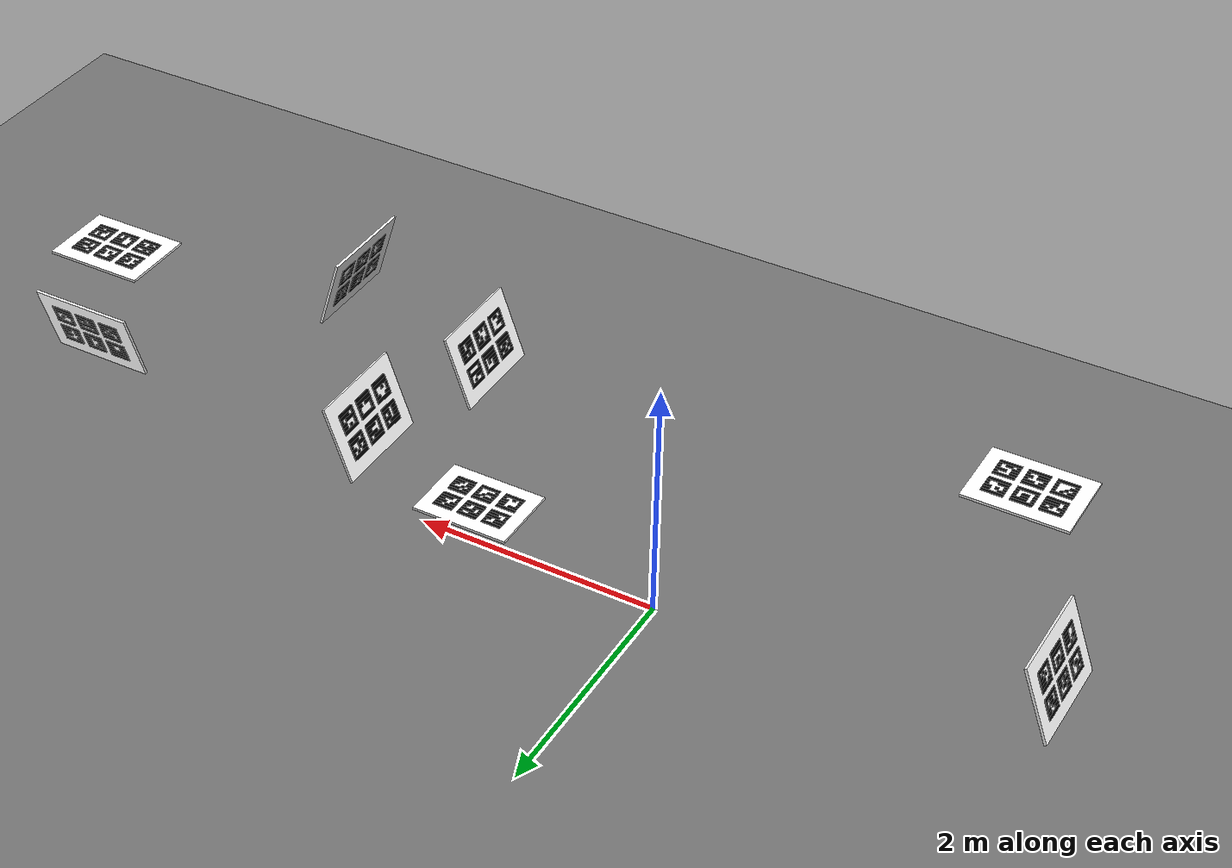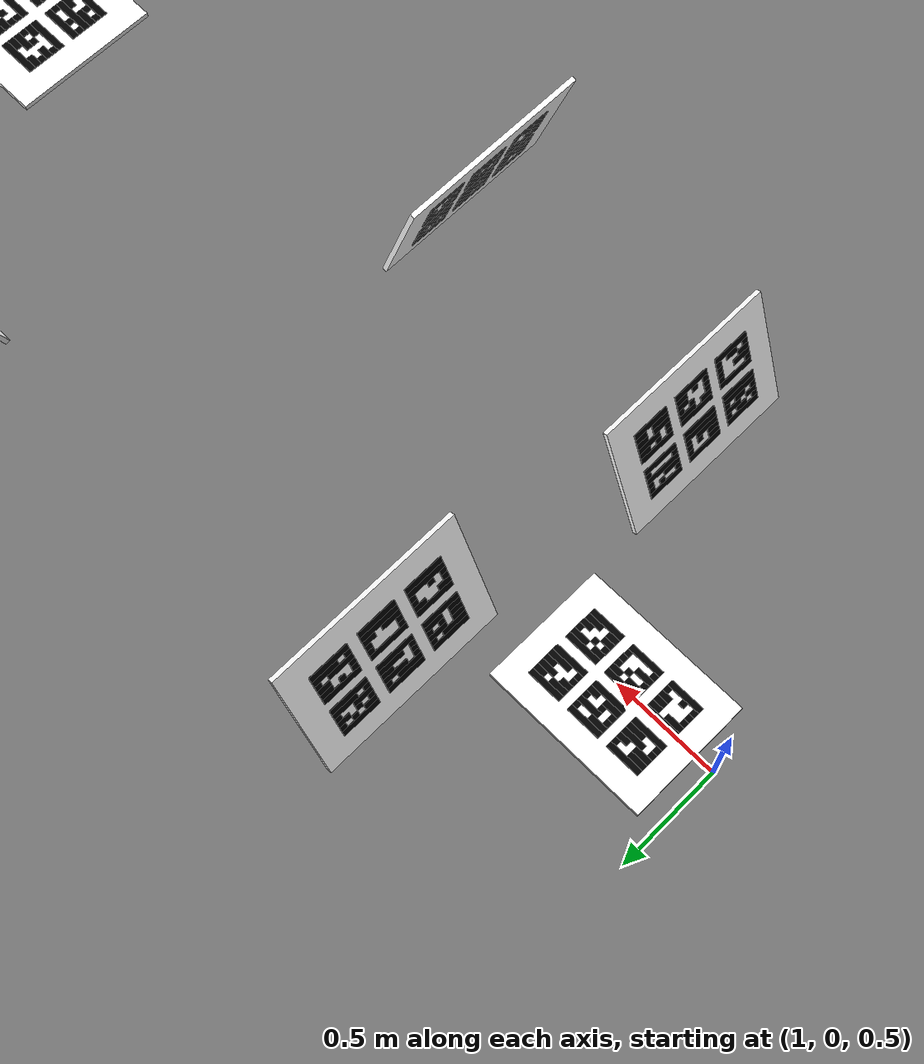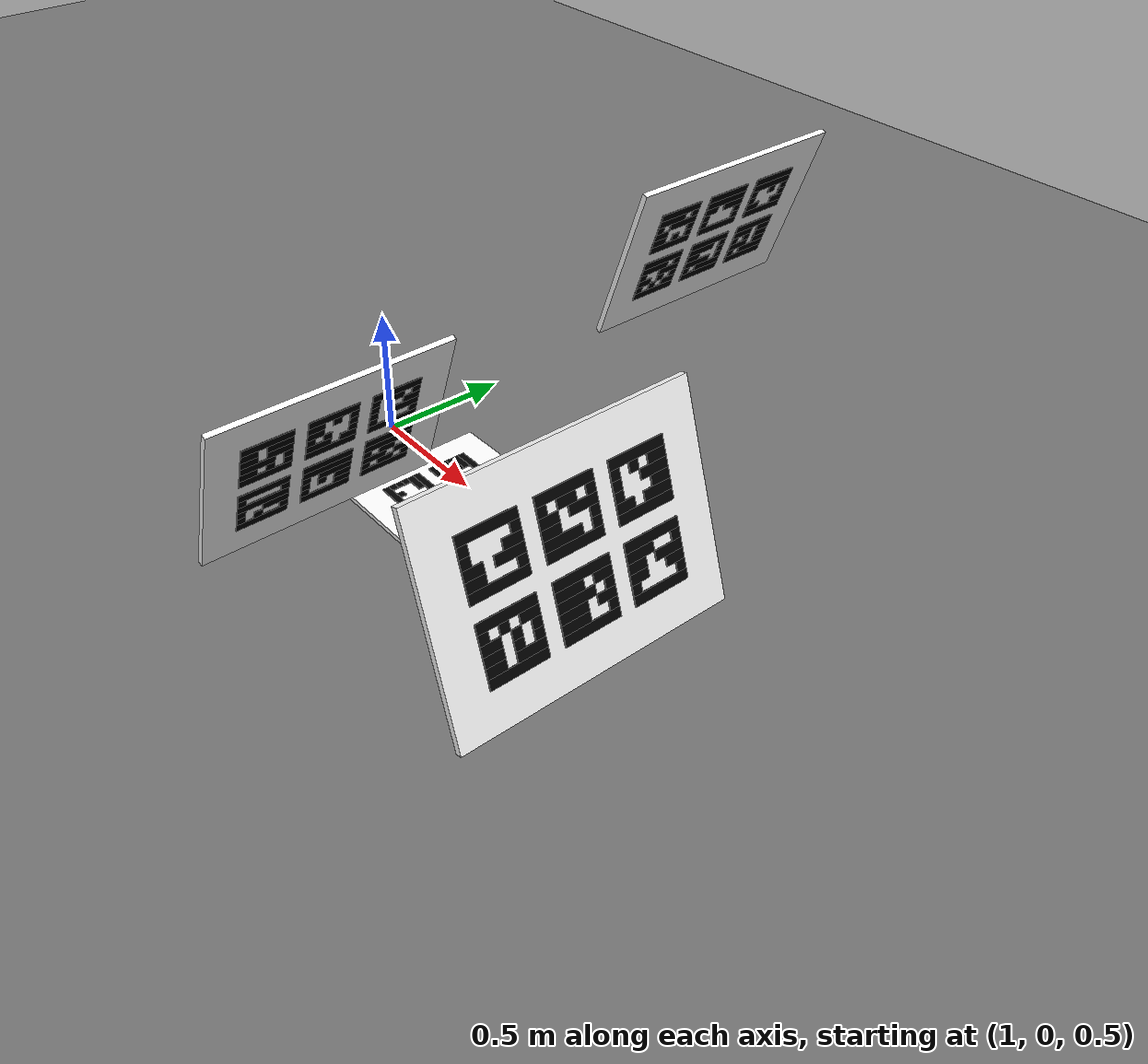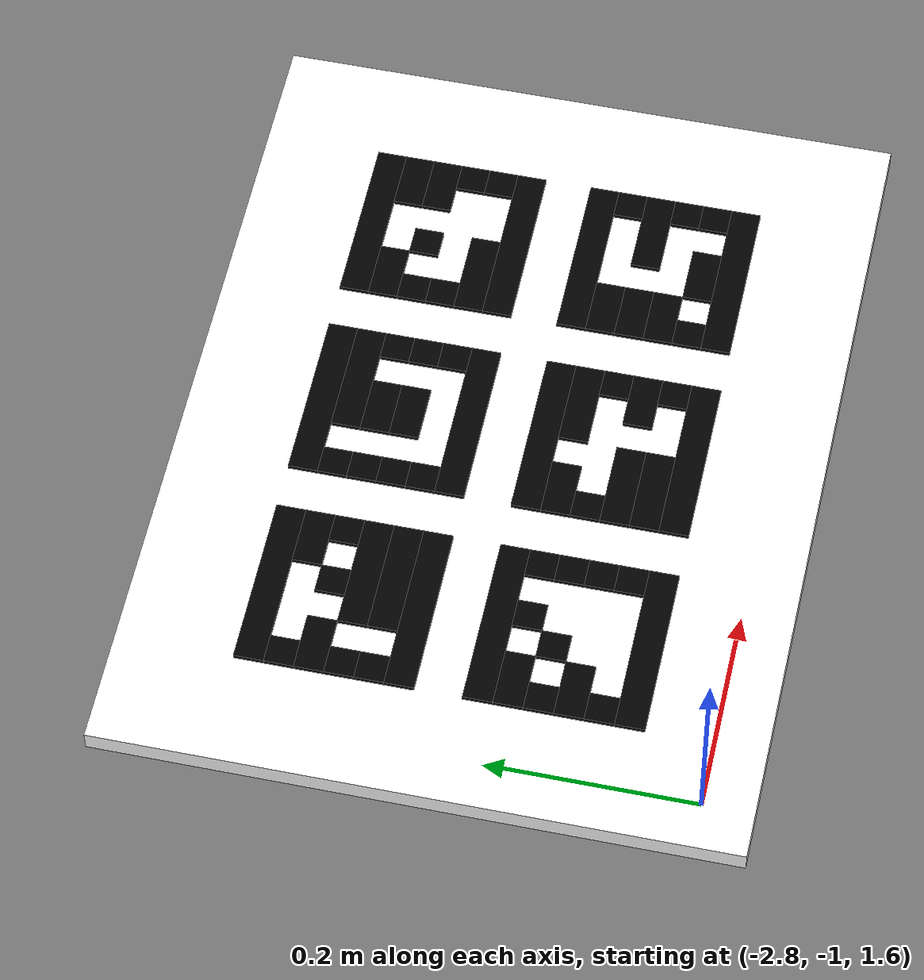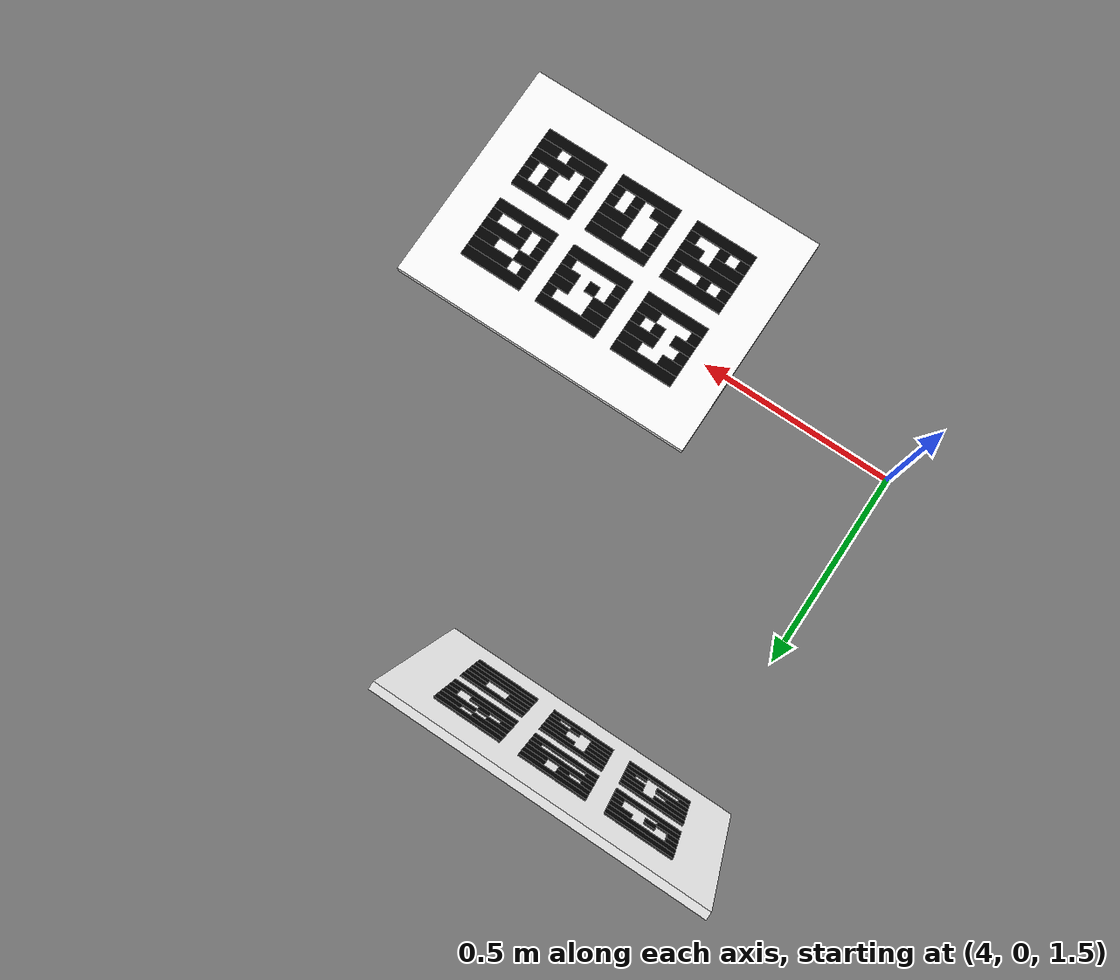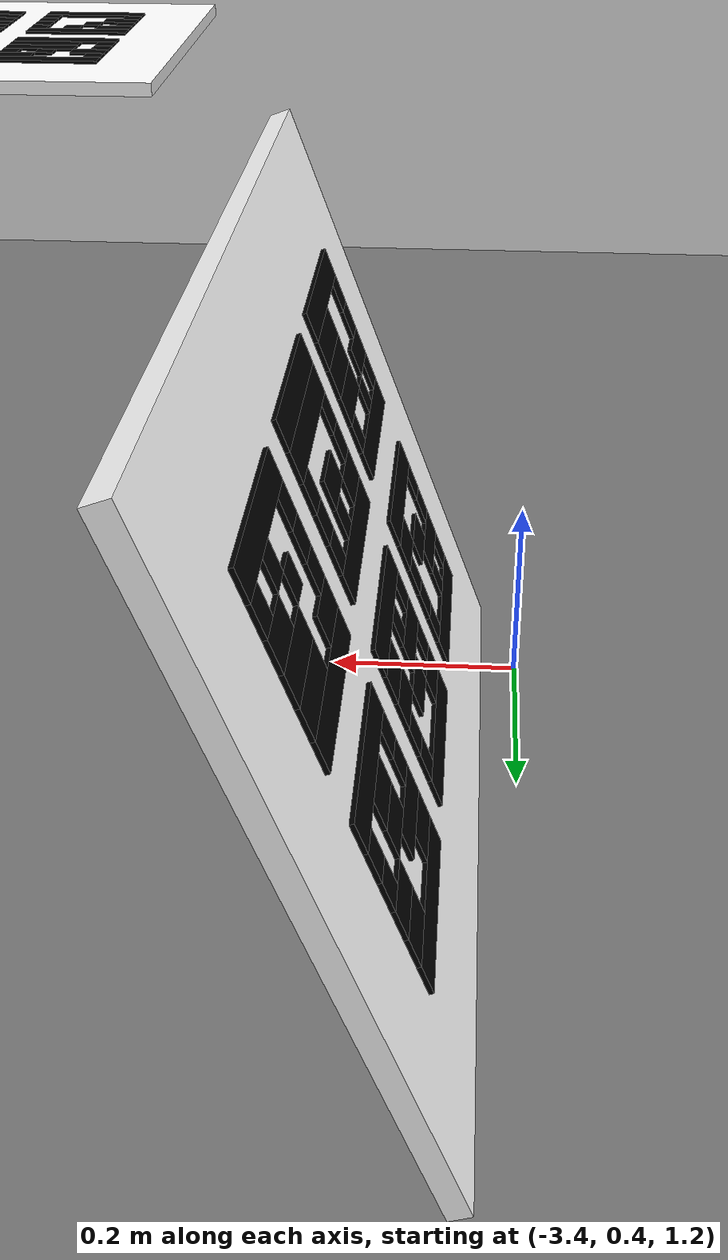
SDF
<sdf version="1.7">
 <world name="bus_multi_aruco_static_stations">
  <scene>
   <ambient>0.90 0.90 0.90 1</ambient>
   <background>0.70 0.70 0.70 1</background>
   <shadows>false</shadows>
  </scene>
  <plugin filename="ignition-gazebo-physics-system" name="ignition::gazebo::systems::Physics"/>
  <plugin filename="ignition-gazebo-user-commands-system" name="ignition::gazebo::systems::UserCommands"/>
  <plugin filename="ignition-gazebo-scene-broadcaster-system" name="ignition::gazebo::systems::SceneBroadcaster"/>
  <plugin filename="ignition-gazebo-sensors-system" name="ignition::gazebo::systems::Sensors">
   <render_engine>ogre2</render_engine>
  </plugin>
  <light name="sun" type="directional">
   <visualize>false</visualize>
   <pose>0 0 10 0 0 0</pose>
   <diffuse>1 1 1 1</diffuse>
   <specular>0.3 0.3 0.3 1</specular>
   <direction>-0.5 0.2 -1</direction>
  </light>
  <model name="ground_plane">
   <static>true</static>
   <link name="link">
    <visual name="visual">
     <geometry><box><size>30 10 0.05</size></box></geometry>
     <material><ambient>0.45 0.45 0.45 1</ambient><diffuse>0.45 0.45 0.45 1</diffuse></material>
    </visual>
   </link>
   <pose>0 0 -0.025 0 0 0</pose>
  </model>
  <include>
   <uri>model://aruco_station_F1_ids_30_35</uri>
   <name>aruco_board_F1_front_mid_far_seat_leaned</name>
   <pose>1.89 -0.75 1.22 0 0.35 0</pose>
  </include>
  <include>
   <uri>model://aruco_station_F2_ids_36_41</uri>
   <name>aruco_board_F2_front_mid_high_left_seat</name>
   <pose>1.97 0.71 1.50 0 0.35 0</pose>
  </include>
  <include>
   <uri>model://aruco_station_F3_ids_00_05</uri>
   <name>aruco_board_F3_front_near_left_seat</name>
   <pose>-3.25 0.71 1.50 0 0.35 0</pose>
  </include>
  <include>
   <uri>model://aruco_station_F4_ids_06_11</uri>
   <name>aruco_board_F4_front_right_table_or_box</name>
   <pose>-2.46 -0.75 1.62 1.57079633 1.57079633 0</pose>
  </include>
  <include>
   <uri>model://aruco_station_R1_ids_24_29</uri>
   <name>aruco_board_R1_rear_left_seat_leaned_occluded</name>
   <pose>3.02 -0.75 1.55 0 0.3 3.14159265</pose>
  </include>
  <include>
   <uri>model://aruco_station_R2_ids_18_23</uri>
   <name>aruco_board_R2_rear_table_flat</name>
   <pose>4.83 -0.09 1.52 1.57079633 1.57079633 3.14159265</pose>
  </include>
  <include>
   <uri>model://aruco_station_R3_ids_12_17</uri>
   <name>aruco_board_R3_rear_right_seat_angled</name>
   <pose>4.27 0.93 1.55 0 0.3 1.57079633</pose>
  </include>
  <include>
   <uri>model://aruco_station_G_ids_42_47</uri>
   <name>aruco_board_G_floor_mid</name>
   <pose>1.50 0.0 0.39 1.57079633 1.57079633 3.14159265</pose>
  </include>
  <model name="front_static_camera">
   <static>true</static>
   <pose>-3.90 0.0 2.85 0 0.69813170 0</pose>
   <link name="link">
    <sensor name="front_static_camera" type="camera">
     <visualize>false</visualize>
     <always_on>true</always_on>
     <update_rate>15</update_rate>
     <topic>/front_static_camera/image</topic>
     <camera>
      <horizontal_fov>1.57079633</horizontal_fov>
      <image><width>640</width><height>480</height><format>R8G8B8</format></image>
      <clip><near>0.05</near><far>30</far></clip>
     </camera>
    </sensor>
   </link>
  </model>
  <model name="rear_static_camera">
   <static>true</static>
   <pose>5.70 0.0 2.85 0 0.69813170 3.14159265</pose>
   <link name="link">
    <sensor name="rear_static_camera" type="camera">
     <visualize>false</visualize>
     <always_on>true</always_on>
     <update_rate>15</update_rate>
     <topic>/rear_static_camera/image</topic>
     <camera>
      <horizontal_fov>1.57079633</horizontal_fov>
      <image><width>640</width><height>480</height><format>R8G8B8</format></image>
      <clip><near>0.05</near><far>30</far></clip>
     </camera>
    </sensor>
   </link>
  </model>
  <model name="moving_calib_camera">
   <static>true</static>
   <pose>4.20 0.0 1.75 0 0 3.14159265</pose>
   <link name="link">
    <sensor name="moving_calib_camera" type="camera">
     <always_on>true</always_on>
     <update_rate>30</update_rate>
     <visualize>false</visualize>
     <topic>/moving_calib_camera/image</topic>
     <camera>
      <horizontal_fov>1.57079633</horizontal_fov>
      <image><width>640</width><height>480</height><format>R8G8B8</format></image>
      <clip><near>0.05</near><far>100</far></clip>
     </camera>
    </sensor>
   </link>
  </model>
 </world>
</sdf>

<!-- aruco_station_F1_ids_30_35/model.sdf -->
<sdf version="1.8">
  <model name="aruco_station_F1_ids_30_35">
    <static>true</static>
    <link name="target_link">

      <visual name="white_board_base">
        <cast_shadows>false</cast_shadows>
        <pose>0.00000000 0.00000000 0.00000000 0.00000000 0.00000000 0.00000000</pose>
        <geometry>
          <box>
            <size>0.02000000 0.80000000 0.60000000</size>
          </box>
        </geometry>
        <material>
          <ambient>1 1 1 1</ambient>
          <diffuse>1 1 1 1</diffuse>
          <specular>0 0 0 1</specular>
          <emissive>1 1 1 1</emissive>
        </material>
      </visual>

      <visual name="black_cell_front_plus_x_id30_r0_c0_6">
        <cast_shadows>false</cast_shadows>
        <pose>0.01300000 -0.21111111 0.17500000 0.00000000 0.00000000 0.00000000</pose>
        <geometry>
          <box>
            <size>0.00400000 0.16666667 0.02777778</size>
          </box>
        </geometry>
        <material>
          <ambient>0 0 0 1</ambient>
          <diffuse>0 0 0 1</diffuse>
          <specular>0 0 0 1</specular>
          <emissive>0 0 0 1</emissive>
        </material>
      </visual>

      <visual name="black_cell_front_plus_x_id30_r1_c0_2">
        <cast_shadows>false</cast_shadows>
        <pose>0.01300000 -0.26666667 0.14722222 0.00000000 0.00000000 0.00000000</pose>
        <geometry>
          <box>
            <size>0.00400000 0.05555556 0.02777778</size>
          </box>
        </geometry>
        <material>
          <ambient>0 0 0 1</ambient>
          <diffuse>0 0 0 1</diffuse>
          <specular>0 0 0 1</specular>
          <emissive>0 0 0 1</emissive>
        </material>
      </visual>

      <visual name="black_cell_front_plus_x_id30_r1_c3_6">
        <cast_shadows>false</cast_shadows>
        <pose>0.01300000 -0.16944444 0.14722222 0.00000000 0.00000000 0.00000000</pose>
        <geometry>
          <box>
            <size>0.00400000 0.08333333 0.02777778</size>
          </box>
        </geometry>
        <material>
          <ambient>0 0 0 1</ambient>
          <diffuse>0 0 0 1</diffuse>
          <specular>0 0 0 1</specular>
          <emissive>0 0 0 1</emissive>
        </material>
      </visual>

      <visual name="black_cell_front_plus_x_id30_r2_c0_2">
        <cast_shadows>false</cast_shadows>
        <pose>0.01300000 -0.26666667 0.11944444 0.00000000 0.00000000 0.00000000</pose>
        <geometry>
          <box>
            <size>0.00400000 0.05555556 0.02777778</size>
          </box>
        </geometry>
        <material>
          <ambient>0 0 0 1</ambient>
          <diffuse>0 0 0 1</diffuse>
          <specular>0 0 0 1</specular>
          <emissive>0 0 0 1</emissive>
        </material>
      </visual>

      <visual name="black_cell_front_plus_x_id30_r2_c3_6">
        <cast_shadows>false</cast_shadows>
        <pose>0.01300000 -0.16944444 0.11944444 0.00000000 0.00000000 0.00000000</pose>
        <geometry>
          <box>
            <size>0.00400000 0.08333333 0.02777778</size>
          </box>
        </geometry>
        <material>
          <ambient>0 0 0 1</ambient>
          <diffuse>0 0 0 1</diffuse>
          <specular>0 0 0 1</specular>
          <emissive>0 0 0 1</emissive>
        </material>
      </visual>

      <visual name="black_cell_front_plus_x_id30_r3_c0_4">
        <cast_shadows>false</cast_shadows>
        <pose>0.01300000 -0.23888889 0.09166667 0.00000000 0.00000000 0.00000000</pose>
        <geometry>
          <box>
            <size>0.00400000 0.11111111 0.02777778</size>
          </box>
        </geometry>
        <material>
          <ambient>0 0 0 1</ambient>
          <diffuse>0 0 0 1</diffuse>
          <specular>0 0 0 1</specular>
          <emissive>0 0 0 1</emissive>
        </material>
      </visual>

      <visual name="black_cell_front_plus_x_id30_r3_c5_6">
        <cast_shadows>false</cast_shadows>
        <pose>0.01300000 -0.14166667 0.09166667 0.00000000 0.00000000 0.00000000</pose>
        <geometry>
          <box>
            <size>0.00400000 0.02777778 0.02777778</size>
          </box>
        </geometry>
        <material>
          <ambient>0 0 0 1</ambient>
          <diffuse>0 0 0 1</diffuse>
          <specular>0 0 0 1</specular>
          <emissive>0 0 0 1</emissive>
        </material>
      </visual>

      <visual name="black_cell_front_plus_x_id30_r4_c0_2">
        <cast_shadows>false</cast_shadows>
        <pose>0.01300000 -0.26666667 0.06388889 0.00000000 0.00000000 0.00000000</pose>
        <geometry>
          <box>
            <size>0.00400000 0.05555556 0.02777778</size>
          </box>
        </geometry>
        <material>
          <ambient>0 0 0 1</ambient>
          <diffuse>0 0 0 1</diffuse>
          <specular>0 0 0 1</specular>
          <emissive>0 0 0 1</emissive>
        </material>
      </visual>

      <visual name="black_cell_front_plus_x_id30_r4_c3_4">
        <cast_shadows>false</cast_shadows>
        <pose>0.01300000 -0.19722222 0.06388889 0.00000000 0.00000000 0.00000000</pose>
        <geometry>
          <box>
            <size>0.00400000 0.02777778 0.02777778</size>
          </box>
        </geometry>
        <material>
          <ambient>0 0 0 1</ambient>
          <diffuse>0 0 0 1</diffuse>
          <specular>0 0 0 1</specular>
          <emissive>0 0 0 1</emissive>
        </material>
      </visual>

      <visual name="black_cell_front_plus_x_id30_r4_c5_6">
        <cast_shadows>false</cast_shadows>
        <pose>0.01300000 -0.14166667 0.06388889 0.00000000 0.00000000 0.00000000</pose>
        <geometry>
          <box>
            <size>0.00400000 0.02777778 0.02777778</size>
          </box>
        </geometry>
        <material>
          <ambient>0 0 0 1</ambient>
          <diffuse>0 0 0 1</diffuse>
          <specular>0 0 0 1</specular>
          <emissive>0 0 0 1</emissive>
        </material>
      </visual>

      <visual name="black_cell_front_plus_x_id30_r5_c0_6">
        <cast_shadows>false</cast_shadows>
        <pose>0.01300000 -0.21111111 0.03611111 0.00000000 0.00000000 0.00000000</pose>
        <geometry>
          <box>
            <size>0.00400000 0.16666667 0.02777778</size>
          </box>
        </geometry>
        <material>
          <ambient>0 0 0 1</ambient>
          <diffuse>0 0 0 1</diffuse>
          <specular>0 0 0 1</specular>
          <emissive>0 0 0 1</emissive>
        </material>
      </visual>

      <visual name="black_cell_back_minus_x_id30_r0_c0_6">
        <cast_shadows>false</cast_shadows>
        <pose>-0.01300000 0.21111111 0.17500000 0.00000000 0.00000000 0.00000000</pose>
        <geometry>
          <box>
            <size>0.00400000 0.16666667 0.02777778</size>
          </box>
        </geometry>
        <material>
          <ambient>0 0 0 1</ambient>
          <diffuse>0 0 0 1</diffuse>
          <specular>0 0 0 1</specular>
          <emissive>0 0 0 1</emissive>
        </material>
      </visual>

      <visual name="black_cell_back_minus_x_id30_r1_c0_2">
        <cast_shadows>false</cast_shadows>
        <pose>-0.01300000 0.26666667 0.14722222 0.00000000 0.00000000 0.00000000</pose>
        <geometry>
          <box>
            <size>0.00400000 0.05555556 0.02777778</size>
          </box>
        </geometry>
        <material>
          <ambient>0 0 0 1</ambient>
          <diffuse>0 0 0 1</diffuse>
          <specular>0 0 0 1</specular>
          <emissive>0 0 0 1</emissive>
        </material>
      </visual>

      <visual name="black_cell_back_minus_x_id30_r1_c3_6">
        <cast_shadows>false</cast_shadows>
        <pose>-0.01300000 0.16944444 0.14722222 0.00000000 0.00000000 0.00000000</pose>
        <geometry>
          <box>
            <size>0.00400000 0.08333333 0.02777778</size>
          </box>
        </geometry>
        <material>
          <ambient>0 0 0 1</ambient>
          <diffuse>0 0 0 1</diffuse>
          <specular>0 0 0 1</specular>
          <emissive>0 0 0 1</emissive>
        </material>
      </visual>

      <visual name="black_cell_back_minus_x_id30_r2_c0_2">
        <cast_shadows>false</cast_shadows>
        <pose>-0.01300000 0.26666667 0.11944444 0.00000000 0.00000000 0.00000000</pose>
        <geometry>
          <box>
            <size>0.00400000 0.05555556 0.02777778</size>
          </box>
        </geometry>
        <material>
          <ambient>0 0 0 1</ambient>
          <diffuse>0 0 0 1</diffuse>
          <specular>0 0 0 1</specular>
          <emissive>0 0 0 1</emissive>
        </material>
      </visual>

      <visual name="black_cell_back_minus_x_id30_r2_c3_6">
        <cast_shadows>false</cast_shadows>
        <pose>-0.01300000 0.16944444 0.11944444 0.00000000 0.00000000 0.00000000</pose>
        <geometry>
          <box>
            <size>0.00400000 0.08333333 0.02777778</size>
          </box>
        </geometry>
        <material>
          <ambient>0 0 0 1</ambient>
          <diffuse>0 0 0 1</diffuse>
          <specular>0 0 0 1</specular>
          <emissive>0 0 0 1</emissive>
        </material>
      </visual>

      <visual name="black_cell_back_minus_x_id30_r3_c0_4">
        <cast_shadows>false</cast_shadows>
        <pose>-0.01300000 0.23888889 0.09166667 0.00000000 0.00000000 0.00000000</pose>
        <geometry>
          <box>
            <size>0.00400000 0.11111111 0.02777778</size>
          </box>
        </geometry>
        <material>
          <ambient>0 0 0 1</ambient>
          <diffuse>0 0 0 1</diffuse>
          <specular>0 0 0 1</specular>
          <emissive>0 0 0 1</emissive>
        </material>
      </visual>

      <visual name="black_cell_back_minus_x_id30_r3_c5_6">
        <cast_shadows>false</cast_shadows>
        <pose>-0.01300000 0.14166667 0.09166667 0.00000000 0.00000000 0.00000000</pose>
        <geometry>
          <box>
            <size>0.00400000 0.02777778 0.02777778</size>
          </box>
        </geometry>
        <material>
          <ambient>0 0 0 1</ambient>
          <diffuse>0 0 0 1</diffuse>
          <specular>0 0 0 1</specular>
          <emissive>0 0 0 1</emissive>
        </material>
      </visual>

      <visual name="black_cell_back_minus_x_id30_r4_c0_2">
        <cast_shadows>false</cast_shadows>
        <pose>-0.01300000 0.26666667 0.06388889 0.00000000 0.00000000 0.00000000</pose>
        <geometry>
          <box>
            <size>0.00400000 0.05555556 0.02777778</size>
          </box>
        </geometry>
        <material>
          <ambient>0 0 0 1</ambient>
          <diffuse>0 0 0 1</diffuse>
          <specular>0 0 0 1</specular>
          <emissive>0 0 0 1</emissive>
        </material>
      </visual>

      <visual name="black_cell_back_minus_x_id30_r4_c3_4">
        <cast_shadows>false</cast_shadows>
        <pose>-0.01300000 0.19722222 0.06388889 0.00000000 0.00000000 0.00000000</pose>
        <geometry>
          <box>
            <size>0.00400000 0.02777778 0.02777778</size>
          </box>
        </geometry>
        <material>
          <ambient>0 0 0 1</ambient>
          <diffuse>0 0 0 1</diffuse>
          <specular>0 0 0 1</specular>
          <emissive>0 0 0 1</emissive>
        </material>
      </visual>

      <visual name="black_cell_back_minus_x_id30_r4_c5_6">
        <cast_shadows>false</cast_shadows>
        <pose>-0.01300000 0.14166667 0.06388889 0.00000000 0.00000000 0.00000000</pose>
        <geometry>
          <box>
            <size>0.00400000 0.02777778 0.02777778</size>
          </box>
        </geometry>
        <material>
          <ambient>0 0 0 1</ambient>
          <diffuse>0 0 0 1</diffuse>
          <specular>0 0 0 1</specular>
          <emissive>0 0 0 1</emissive>
        </material>
      </visual>

      <visual name="black_cell_back_minus_x_id30_r5_c0_6">
        <cast_shadows>false</cast_shadows>
        <pose>-0.01300000 0.21111111 0.03611111 0.00000000 0.00000000 0.00000000</pose>
        <geometry>
          <box>
            <size>0.00400000 0.16666667 0.02777778</size>
          </box>
        </geometry>
        <material>
          <ambient>0 0 0 1</ambient>
          <diffuse>0 0 0 1</diffuse>
          <specular>0 0 0 1</specular>
          <emissive>0 0 0 1</emissive>
        </material>
      </visual>

      <visual name="black_cell_front_plus_x_id31_r0_c0_6">
        <cast_shadows>false</cast_shadows>
        <pose>0.01300000 -0.00000000 0.17500000 0.00000000 0.00000000 0.00000000</pose>
        <geometry>
          <box>
            <size>0.00400000 0.16666667 0.02777778</size>
          </box>
        </geometry>
        <material>
          <ambient>0 0 0 1</ambient>
          <diffuse>0 0 0 1</diffuse>
          <specular>0 0 0 1</specular>
          <emissive>0 0 0 1</emissive>
        </material>
      </visual>

      <visual name="black_cell_front_plus_x_id31_r1_c0_2">
        <cast_shadows>false</cast_shadows>
        <pose>0.01300000 -0.05555556 0.14722222 0.00000000 0.00000000 0.00000000</pose>
        <geometry>
          <box>
            <size>0.00400000 0.05555556 0.02777778</size>
          </box>
        </geometry>
        <material>
          <ambient>0 0 0 1</ambient>
          <diffuse>0 0 0 1</diffuse>
          <specular>0 0 0 1</specular>
          <emissive>0 0 0 1</emissive>
        </material>
      </visual>

      <visual name="black_cell_front_plus_x_id31_r1_c3_4">
        <cast_shadows>false</cast_shadows>
        <pose>0.01300000 0.01388889 0.14722222 0.00000000 0.00000000 0.00000000</pose>
        <geometry>
          <box>
            <size>0.00400000 0.02777778 0.02777778</size>
          </box>
        </geometry>
        <material>
          <ambient>0 0 0 1</ambient>
          <diffuse>0 0 0 1</diffuse>
          <specular>0 0 0 1</specular>
          <emissive>0 0 0 1</emissive>
        </material>
      </visual>

      <visual name="black_cell_front_plus_x_id31_r1_c5_6">
        <cast_shadows>false</cast_shadows>
        <pose>0.01300000 0.06944444 0.14722222 0.00000000 0.00000000 0.00000000</pose>
        <geometry>
          <box>
            <size>0.00400000 0.02777778 0.02777778</size>
          </box>
        </geometry>
        <material>
          <ambient>0 0 0 1</ambient>
          <diffuse>0 0 0 1</diffuse>
          <specular>0 0 0 1</specular>
          <emissive>0 0 0 1</emissive>
        </material>
      </visual>

      <visual name="black_cell_front_plus_x_id31_r2_c0_2">
        <cast_shadows>false</cast_shadows>
        <pose>0.01300000 -0.05555556 0.11944444 0.00000000 0.00000000 0.00000000</pose>
        <geometry>
          <box>
            <size>0.00400000 0.05555556 0.02777778</size>
          </box>
        </geometry>
        <material>
          <ambient>0 0 0 1</ambient>
          <diffuse>0 0 0 1</diffuse>
          <specular>0 0 0 1</specular>
          <emissive>0 0 0 1</emissive>
        </material>
      </visual>

      <visual name="black_cell_front_plus_x_id31_r2_c5_6">
        <cast_shadows>false</cast_shadows>
        <pose>0.01300000 0.06944444 0.11944444 0.00000000 0.00000000 0.00000000</pose>
        <geometry>
          <box>
            <size>0.00400000 0.02777778 0.02777778</size>
          </box>
        </geometry>
        <material>
          <ambient>0 0 0 1</ambient>
          <diffuse>0 0 0 1</diffuse>
          <specular>0 0 0 1</specular>
          <emissive>0 0 0 1</emissive>
        </material>
      </visual>

      <visual name="black_cell_front_plus_x_id31_r3_c0_1">
        <cast_shadows>false</cast_shadows>
        <pose>0.01300000 -0.06944444 0.09166667 0.00000000 0.00000000 0.00000000</pose>
        <geometry>
          <box>
            <size>0.00400000 0.02777778 0.02777778</size>
          </box>
        </geometry>
        <material>
          <ambient>0 0 0 1</ambient>
          <diffuse>0 0 0 1</diffuse>
          <specular>0 0 0 1</specular>
          <emissive>0 0 0 1</emissive>
        </material>
      </visual>

      <visual name="black_cell_front_plus_x_id31_r3_c2_3">
        <cast_shadows>false</cast_shadows>
        <pose>0.01300000 -0.01388889 0.09166667 0.00000000 0.00000000 0.00000000</pose>
        <geometry>
          <box>
            <size>0.00400000 0.02777778 0.02777778</size>
          </box>
        </geometry>
        <material>
          <ambient>0 0 0 1</ambient>
          <diffuse>0 0 0 1</diffuse>
          <specular>0 0 0 1</specular>
          <emissive>0 0 0 1</emissive>
        </material>
      </visual>

      <visual name="black_cell_front_plus_x_id31_r3_c5_6">
        <cast_shadows>false</cast_shadows>
        <pose>0.01300000 0.06944444 0.09166667 0.00000000 0.00000000 0.00000000</pose>
        <geometry>
          <box>
            <size>0.00400000 0.02777778 0.02777778</size>
          </box>
        </geometry>
        <material>
          <ambient>0 0 0 1</ambient>
          <diffuse>0 0 0 1</diffuse>
          <specular>0 0 0 1</specular>
          <emissive>0 0 0 1</emissive>
        </material>
      </visual>

      <visual name="black_cell_front_plus_x_id31_r4_c0_3">
        <cast_shadows>false</cast_shadows>
        <pose>0.01300000 -0.04166667 0.06388889 0.00000000 0.00000000 0.00000000</pose>
        <geometry>
          <box>
            <size>0.00400000 0.08333333 0.02777778</size>
          </box>
        </geometry>
        <material>
          <ambient>0 0 0 1</ambient>
          <diffuse>0 0 0 1</diffuse>
          <specular>0 0 0 1</specular>
          <emissive>0 0 0 1</emissive>
        </material>
      </visual>

      <visual name="black_cell_front_plus_x_id31_r4_c4_6">
        <cast_shadows>false</cast_shadows>
        <pose>0.01300000 0.05555556 0.06388889 0.00000000 0.00000000 0.00000000</pose>
        <geometry>
          <box>
            <size>0.00400000 0.05555556 0.02777778</size>
          </box>
        </geometry>
        <material>
          <ambient>0 0 0 1</ambient>
          <diffuse>0 0 0 1</diffuse>
          <specular>0 0 0 1</specular>
          <emissive>0 0 0 1</emissive>
        </material>
      </visual>

      <visual name="black_cell_front_plus_x_id31_r5_c0_6">
        <cast_shadows>false</cast_shadows>
        <pose>0.01300000 -0.00000000 0.03611111 0.00000000 0.00000000 0.00000000</pose>
        <geometry>
          <box>
            <size>0.00400000 0.16666667 0.02777778</size>
          </box>
        </geometry>
        <material>
          <ambient>0 0 0 1</ambient>
          <diffuse>0 0 0 1</diffuse>
          <specular>0 0 0 1</specular>
          <emissive>0 0 0 1</emissive>
        </material>
      </visual>

      <visual name="black_cell_back_minus_x_id31_r0_c0_6">
        <cast_shadows>false</cast_shadows>
        <pose>-0.01300000 0.00000000 0.17500000 0.00000000 0.00000000 0.00000000</pose>
        <geometry>
          <box>
            <size>0.00400000 0.16666667 0.02777778</size>
          </box>
        </geometry>
        <material>
          <ambient>0 0 0 1</ambient>
          <diffuse>0 0 0 1</diffuse>
          <specular>0 0 0 1</specular>
          <emissive>0 0 0 1</emissive>
        </material>
      </visual>

      <visual name="black_cell_back_minus_x_id31_r1_c0_2">
        <cast_shadows>false</cast_shadows>
        <pose>-0.01300000 0.05555556 0.14722222 0.00000000 0.00000000 0.00000000</pose>
        <geometry>
          <box>
            <size>0.00400000 0.05555556 0.02777778</size>
          </box>
        </geometry>
        <material>
          <ambient>0 0 0 1</ambient>
          <diffuse>0 0 0 1</diffuse>
          <specular>0 0 0 1</specular>
          <emissive>0 0 0 1</emissive>
        </material>
      </visual>

      <visual name="black_cell_back_minus_x_id31_r1_c3_4">
        <cast_shadows>false</cast_shadows>
        <pose>-0.01300000 -0.01388889 0.14722222 0.00000000 0.00000000 0.00000000</pose>
        <geometry>
          <box>
            <size>0.00400000 0.02777778 0.02777778</size>
          </box>
        </geometry>
        <material>
          <ambient>0 0 0 1</ambient>
          <diffuse>0 0 0 1</diffuse>
          <specular>0 0 0 1</specular>
          <emissive>0 0 0 1</emissive>
        </material>
      </visual>

      <visual name="black_cell_back_minus_x_id31_r1_c5_6">
        <cast_shadows>false</cast_shadows>
        <pose>-0.01300000 -0.06944444 0.14722222 0.00000000 0.00000000 0.00000000</pose>
        <geometry>
          <box>
            <size>0.00400000 0.02777778 0.02777778</size>
          </box>
        </geometry>
        <material>
          <ambient>0 0 0 1</ambient>
          <diffuse>0 0 0 1</diffuse>
          <specular>0 0 0 1</specular>
          <emissive>0 0 0 1</emissive>
        </material>
      </visual>

      <visual name="black_cell_back_minus_x_id31_r2_c0_2">
        <cast_shadows>false</cast_shadows>
        <pose>-0.01300000 0.05555556 0.11944444 0.00000000 0.00000000 0.00000000</pose>
        <geometry>
          <box>
            <size>0.00400000 0.05555556 0.02777778</size>
          </box>
        </geometry>
        <material>
          <ambient>0 0 0 1</ambient>
          <diffuse>0 0 0 1</diffuse>
          <specular>0 0 0 1</specular>
          <emissive>0 0 0 1</emissive>
        </material>
      </visual>

      <visual name="black_cell_back_minus_x_id31_r2_c5_6">
        <cast_shadows>false</cast_shadows>
        <pose>-0.01300000 -0.06944444 0.11944444 0.00000000 0.00000000 0.00000000</pose>
        <geometry>
          <box>
            <size>0.00400000 0.02777778 0.02777778</size>
          </box>
        </geometry>
        <material>
          <ambient>0 0 0 1</ambient>
          <diffuse>0 0 0 1</diffuse>
          <specular>0 0 0 1</specular>
          <emissive>0 0 0 1</emissive>
        </material>
      </visual>

      <visual name="black_cell_back_minus_x_id31_r3_c0_1">
        <cast_shadows>false</cast_shadows>
        <pose>-0.01300000 0.06944444 0.09166667 0.00000000 0.00000000 0.00000000</pose>
        <geometry>
          <box>
            <size>0.00400000 0.02777778 0.02777778</size>
          </box>
        </geometry>
        <material>
          <ambient>0 0 0 1</ambient>
          <diffuse>0 0 0 1</diffuse>
          <specular>0 0 0 1</specular>
          <emissive>0 0 0 1</emissive>
        </material>
      </visual>

      <visual name="black_cell_back_minus_x_id31_r3_c2_3">
        <cast_shadows>false</cast_shadows>
        <pose>-0.01300000 0.01388889 0.09166667 0.00000000 0.00000000 0.00000000</pose>
        <geometry>
          <box>
            <size>0.00400000 0.02777778 0.02777778</size>
          </box>
        </geometry>
        <material>
          <ambient>0 0 0 1</ambient>
          <diffuse>0 0 0 1</diffuse>
          <specular>0 0 0 1</specular>
          <emissive>0 0 0 1</emissive>
        </material>
      </visual>

      <visual name="black_cell_back_minus_x_id31_r3_c5_6">
        <cast_shadows>false</cast_shadows>
        <pose>-0.01300000 -0.06944444 0.09166667 0.00000000 0.00000000 0.00000000</pose>
        <geometry>
          <box>
            <size>0.00400000 0.02777778 0.02777778</size>
          </box>
        </geometry>
        <material>
          <ambient>0 0 0 1</ambient>
          <diffuse>0 0 0 1</diffuse>
          <specular>0 0 0 1</specular>
          <emissive>0 0 0 1</emissive>
        </material>
      </visual>

      <visual name="black_cell_back_minus_x_id31_r4_c0_3">
        <cast_shadows>false</cast_shadows>
        <pose>-0.01300000 0.04166667 0.06388889 0.00000000 0.00000000 0.00000000</pose>
        <geometry>
          <box>
            <size>0.00400000 0.08333333 0.02777778</size>
          </box>
        </geometry>
        <material>
          <ambient>0 0 0 1</ambient>
          <diffuse>0 0 0 1</diffuse>
          <specular>0 0 0 1</specular>
          <emissive>0 0 0 1</emissive>
        </material>
      </visual>

      <visual name="black_cell_back_minus_x_id31_r4_c4_6">
        <cast_shadows>false</cast_shadows>
        <pose>-0.01300000 -0.05555556 0.06388889 0.00000000 0.00000000 0.00000000</pose>
        <geometry>
          <box>
            <size>0.00400000 0.05555556 0.02777778</size>
          </box>
        </geometry>
        <material>
          <ambient>0 0 0 1</ambient>
          <diffuse>0 0 0 1</diffuse>
          <specular>0 0 0 1</specular>
          <emissive>0 0 0 1</emissive>
        </material>
      </visual>

      <visual name="black_cell_back_minus_x_id31_r5_c0_6">
        <cast_shadows>false</cast_shadows>
        <pose>-0.01300000 0.00000000 0.03611111 0.00000000 0.00000000 0.00000000</pose>
        <geometry>
          <box>
            <size>0.00400000 0.16666667 0.02777778</size>
          </box>
        </geometry>
        <material>
          <ambient>0 0 0 1</ambient>
          <diffuse>0 0 0 1</diffuse>
          <specular>0 0 0 1</specular>
          <emissive>0 0 0 1</emissive>
        </material>
      </visual>

      <visual name="black_cell_front_plus_x_id32_r0_c0_6">
        <cast_shadows>false</cast_shadows>
        <pose>0.01300000 0.21111111 0.17500000 0.00000000 0.00000000 0.00000000</pose>
        <geometry>
          <box>
            <size>0.00400000 0.16666667 0.02777778</size>
          </box>
        </geometry>
        <material>
          <ambient>0 0 0 1</ambient>
          <diffuse>0 0 0 1</diffuse>
          <specular>0 0 0 1</specular>
          <emissive>0 0 0 1</emissive>
        </material>
      </visual>

      <visual name="black_cell_front_plus_x_id32_r1_c0_1">
        <cast_shadows>false</cast_shadows>
        <pose>0.01300000 0.14166667 0.14722222 0.00000000 0.00000000 0.00000000</pose>
        <geometry>
          <box>
            <size>0.00400000 0.02777778 0.02777778</size>
          </box>
        </geometry>
        <material>
          <ambient>0 0 0 1</ambient>
          <diffuse>0 0 0 1</diffuse>
          <specular>0 0 0 1</specular>
          <emissive>0 0 0 1</emissive>
        </material>
      </visual>

      <visual name="black_cell_front_plus_x_id32_r1_c2_4">
        <cast_shadows>false</cast_shadows>
        <pose>0.01300000 0.21111111 0.14722222 0.00000000 0.00000000 0.00000000</pose>
        <geometry>
          <box>
            <size>0.00400000 0.05555556 0.02777778</size>
          </box>
        </geometry>
        <material>
          <ambient>0 0 0 1</ambient>
          <diffuse>0 0 0 1</diffuse>
          <specular>0 0 0 1</specular>
          <emissive>0 0 0 1</emissive>
        </material>
      </visual>

      <visual name="black_cell_front_plus_x_id32_r1_c5_6">
        <cast_shadows>false</cast_shadows>
        <pose>0.01300000 0.28055556 0.14722222 0.00000000 0.00000000 0.00000000</pose>
        <geometry>
          <box>
            <size>0.00400000 0.02777778 0.02777778</size>
          </box>
        </geometry>
        <material>
          <ambient>0 0 0 1</ambient>
          <diffuse>0 0 0 1</diffuse>
          <specular>0 0 0 1</specular>
          <emissive>0 0 0 1</emissive>
        </material>
      </visual>

      <visual name="black_cell_front_plus_x_id32_r2_c0_1">
        <cast_shadows>false</cast_shadows>
        <pose>0.01300000 0.14166667 0.11944444 0.00000000 0.00000000 0.00000000</pose>
        <geometry>
          <box>
            <size>0.00400000 0.02777778 0.02777778</size>
          </box>
        </geometry>
        <material>
          <ambient>0 0 0 1</ambient>
          <diffuse>0 0 0 1</diffuse>
          <specular>0 0 0 1</specular>
          <emissive>0 0 0 1</emissive>
        </material>
      </visual>

      <visual name="black_cell_front_plus_x_id32_r2_c4_6">
        <cast_shadows>false</cast_shadows>
        <pose>0.01300000 0.26666667 0.11944444 0.00000000 0.00000000 0.00000000</pose>
        <geometry>
          <box>
            <size>0.00400000 0.05555556 0.02777778</size>
          </box>
        </geometry>
        <material>
          <ambient>0 0 0 1</ambient>
          <diffuse>0 0 0 1</diffuse>
          <specular>0 0 0 1</specular>
          <emissive>0 0 0 1</emissive>
        </material>
      </visual>

      <visual name="black_cell_front_plus_x_id32_r3_c0_1">
        <cast_shadows>false</cast_shadows>
        <pose>0.01300000 0.14166667 0.09166667 0.00000000 0.00000000 0.00000000</pose>
        <geometry>
          <box>
            <size>0.00400000 0.02777778 0.02777778</size>
          </box>
        </geometry>
        <material>
          <ambient>0 0 0 1</ambient>
          <diffuse>0 0 0 1</diffuse>
          <specular>0 0 0 1</specular>
          <emissive>0 0 0 1</emissive>
        </material>
      </visual>

      <visual name="black_cell_front_plus_x_id32_r3_c3_6">
        <cast_shadows>false</cast_shadows>
        <pose>0.01300000 0.25277778 0.09166667 0.00000000 0.00000000 0.00000000</pose>
        <geometry>
          <box>
            <size>0.00400000 0.08333333 0.02777778</size>
          </box>
        </geometry>
        <material>
          <ambient>0 0 0 1</ambient>
          <diffuse>0 0 0 1</diffuse>
          <specular>0 0 0 1</specular>
          <emissive>0 0 0 1</emissive>
        </material>
      </visual>

      <visual name="black_cell_front_plus_x_id32_r4_c0_1">
        <cast_shadows>false</cast_shadows>
        <pose>0.01300000 0.14166667 0.06388889 0.00000000 0.00000000 0.00000000</pose>
        <geometry>
          <box>
            <size>0.00400000 0.02777778 0.02777778</size>
          </box>
        </geometry>
        <material>
          <ambient>0 0 0 1</ambient>
          <diffuse>0 0 0 1</diffuse>
          <specular>0 0 0 1</specular>
          <emissive>0 0 0 1</emissive>
        </material>
      </visual>

      <visual name="black_cell_front_plus_x_id32_r4_c5_6">
        <cast_shadows>false</cast_shadows>
        <pose>0.01300000 0.28055556 0.06388889 0.00000000 0.00000000 0.00000000</pose>
        <geometry>
          <box>
            <size>0.00400000 0.02777778 0.02777778</size>
          </box>
        </geometry>
        <material>
          <ambient>0 0 0 1</ambient>
          <diffuse>0 0 0 1</diffuse>
          <specular>0 0 0 1</specular>
          <emissive>0 0 0 1</emissive>
        </material>
      </visual>

      <visual name="black_cell_front_plus_x_id32_r5_c0_6">
        <cast_shadows>false</cast_shadows>
        <pose>0.01300000 0.21111111 0.03611111 0.00000000 0.00000000 0.00000000</pose>
        <geometry>
          <box>
            <size>0.00400000 0.16666667 0.02777778</size>
          </box>
        </geometry>
        <material>
          <ambient>0 0 0 1</ambient>
          <diffuse>0 0 0 1</diffuse>
          <specular>0 0 0 1</specular>
          <emissive>0 0 0 1</emissive>
        </material>
      </visual>

      <visual name="black_cell_back_minus_x_id32_r0_c0_6">
        <cast_shadows>false</cast_shadows>
        <pose>-0.01300000 -0.21111111 0.17500000 0.00000000 0.00000000 0.00000000</pose>
        <geometry>
          <box>
            <size>0.00400000 0.16666667 0.02777778</size>
          </box>
        </geometry>
        <material>
          <ambient>0 0 0 1</ambient>
          <diffuse>0 0 0 1</diffuse>
          <specular>0 0 0 1</specular>
          <emissive>0 0 0 1</emissive>
        </material>
      </visual>

      <visual name="black_cell_back_minus_x_id32_r1_c0_1">
        <cast_shadows>false</cast_shadows>
        <pose>-0.01300000 -0.14166667 0.14722222 0.00000000 0.00000000 0.00000000</pose>
        <geometry>
          <box>
            <size>0.00400000 0.02777778 0.02777778</size>
          </box>
        </geometry>
        <material>
          <ambient>0 0 0 1</ambient>
          <diffuse>0 0 0 1</diffuse>
          <specular>0 0 0 1</specular>
          <emissive>0 0 0 1</emissive>
        </material>
      </visual>

      <visual name="black_cell_back_minus_x_id32_r1_c2_4">
        <cast_shadows>false</cast_shadows>
        <pose>-0.01300000 -0.21111111 0.14722222 0.00000000 0.00000000 0.00000000</pose>
        <geometry>
          <box>
            <size>0.00400000 0.05555556 0.02777778</size>
          </box>
        </geometry>
        <material>
          <ambient>0 0 0 1</ambient>
          <diffuse>0 0 0 1</diffuse>
          <specular>0 0 0 1</specular>
          <emissive>0 0 0 1</emissive>
        </material>
      </visual>

      <visual name="black_cell_back_minus_x_id32_r1_c5_6">
        <cast_shadows>false</cast_shadows>
        <pose>-0.01300000 -0.28055556 0.14722222 0.00000000 0.00000000 0.00000000</pose>
        <geometry>
          <box>
            <size>0.00400000 0.02777778 0.02777778</size>
          </box>
        </geometry>
        <material>
          <ambient>0 0 0 1</ambient>
          <diffuse>0 0 0 1</diffuse>
          <specular>0 0 0 1</specular>
          <emissive>0 0 0 1</emissive>
        </material>
      </visual>

      <visual name="black_cell_back_minus_x_id32_r2_c0_1">
        <cast_shadows>false</cast_shadows>
        <pose>-0.01300000 -0.14166667 0.11944444 0.00000000 0.00000000 0.00000000</pose>
        <geometry>
          <box>
            <size>0.00400000 0.02777778 0.02777778</size>
          </box>
        </geometry>
        <material>
          <ambient>0 0 0 1</ambient>
          <diffuse>0 0 0 1</diffuse>
          <specular>0 0 0 1</specular>
          <emissive>0 0 0 1</emissive>
        </material>
      </visual>

      <visual name="black_cell_back_minus_x_id32_r2_c4_6">
        <cast_shadows>false</cast_shadows>
        <pose>-0.01300000 -0.26666667 0.11944444 0.00000000 0.00000000 0.00000000</pose>
        <geometry>
          <box>
            <size>0.00400000 0.05555556 0.02777778</size>
          </box>
        </geometry>
        <material>
          <ambient>0 0 0 1</ambient>
          <diffuse>0 0 0 1</diffuse>
          <specular>0 0 0 1</specular>
          <emissive>0 0 0 1</emissive>
        </material>
      </visual>

      <visual name="black_cell_back_minus_x_id32_r3_c0_1">
        <cast_shadows>false</cast_shadows>
        <pose>-0.01300000 -0.14166667 0.09166667 0.00000000 0.00000000 0.00000000</pose>
        <geometry>
          <box>
            <size>0.00400000 0.02777778 0.02777778</size>
          </box>
        </geometry>
        <material>
          <ambient>0 0 0 1</ambient>
          <diffuse>0 0 0 1</diffuse>
          <specular>0 0 0 1</specular>
          <emissive>0 0 0 1</emissive>
        </material>
      </visual>

      <visual name="black_cell_back_minus_x_id32_r3_c3_6">
        <cast_shadows>false</cast_shadows>
        <pose>-0.01300000 -0.25277778 0.09166667 0.00000000 0.00000000 0.00000000</pose>
        <geometry>
          <box>
            <size>0.00400000 0.08333333 0.02777778</size>
          </box>
        </geometry>
        <material>
          <ambient>0 0 0 1</ambient>
          <diffuse>0 0 0 1</diffuse>
          <specular>0 0 0 1</specular>
          <emissive>0 0 0 1</emissive>
        </material>
      </visual>

      <visual name="black_cell_back_minus_x_id32_r4_c0_1">
        <cast_shadows>false</cast_shadows>
        <pose>-0.01300000 -0.14166667 0.06388889 0.00000000 0.00000000 0.00000000</pose>
        <geometry>
          <box>
            <size>0.00400000 0.02777778 0.02777778</size>
          </box>
        </geometry>
        <material>
          <ambient>0 0 0 1</ambient>
          <diffuse>0 0 0 1</diffuse>
          <specular>0 0 0 1</specular>
          <emissive>0 0 0 1</emissive>
        </material>
      </visual>

      <visual name="black_cell_back_minus_x_id32_r4_c5_6">
        <cast_shadows>false</cast_shadows>
        <pose>-0.01300000 -0.28055556 0.06388889 0.00000000 0.00000000 0.00000000</pose>
        <geometry>
          <box>
            <size>0.00400000 0.02777778 0.02777778</size>
          </box>
        </geometry>
        <material>
          <ambient>0 0 0 1</ambient>
          <diffuse>0 0 0 1</diffuse>
          <specular>0 0 0 1</specular>
          <emissive>0 0 0 1</emissive>
        </material>
      </visual>

      <visual name="black_cell_back_minus_x_id32_r5_c0_6">
        <cast_shadows>false</cast_shadows>
        <pose>-0.01300000 -0.21111111 0.03611111 0.00000000 0.00000000 0.00000000</pose>
        <geometry>
          <box>
            <size>0.00400000 0.16666667 0.02777778</size>
          </box>
        </geometry>
        <material>
          <ambient>0 0 0 1</ambient>
          <diffuse>0 0 0 1</diffuse>
          <specular>0 0 0 1</specular>
          <emissive>0 0 0 1</emissive>
        </material>
      </visual>

      <visual name="black_cell_front_plus_x_id33_r0_c0_6">
        <cast_shadows>false</cast_shadows>
        <pose>0.01300000 -0.21111111 -0.03611111 0.00000000 0.00000000 0.00000000</pose>
        <geometry>
          <box>
            <size>0.00400000 0.16666667 0.02777778</size>
          </box>
        </geometry>
        <material>
          <ambient>0 0 0 1</ambient>
          <diffuse>0 0 0 1</diffuse>
          <specular>0 0 0 1</specular>
          <emissive>0 0 0 1</emissive>
        </material>
      </visual>

      <visual name="black_cell_front_plus_x_id33_r1_c0_1">
        <cast_shadows>false</cast_shadows>
        <pose>0.01300000 -0.28055556 -0.06388889 0.00000000 0.00000000 0.00000000</pose>
        <geometry>
          <box>
            <size>0.00400000 0.02777778 0.02777778</size>
          </box>
        </geometry>
        <material>
          <ambient>0 0 0 1</ambient>
          <diffuse>0 0 0 1</diffuse>
          <specular>0 0 0 1</specular>
          <emissive>0 0 0 1</emissive>
        </material>
      </visual>

      <visual name="black_cell_front_plus_x_id33_r1_c5_6">
        <cast_shadows>false</cast_shadows>
        <pose>0.01300000 -0.14166667 -0.06388889 0.00000000 0.00000000 0.00000000</pose>
        <geometry>
          <box>
            <size>0.00400000 0.02777778 0.02777778</size>
          </box>
        </geometry>
        <material>
          <ambient>0 0 0 1</ambient>
          <diffuse>0 0 0 1</diffuse>
          <specular>0 0 0 1</specular>
          <emissive>0 0 0 1</emissive>
        </material>
      </visual>

      <visual name="black_cell_front_plus_x_id33_r2_c0_6">
        <cast_shadows>false</cast_shadows>
        <pose>0.01300000 -0.21111111 -0.09166667 0.00000000 0.00000000 0.00000000</pose>
        <geometry>
          <box>
            <size>0.00400000 0.16666667 0.02777778</size>
          </box>
        </geometry>
        <material>
          <ambient>0 0 0 1</ambient>
          <diffuse>0 0 0 1</diffuse>
          <specular>0 0 0 1</specular>
          <emissive>0 0 0 1</emissive>
        </material>
      </visual>

      <visual name="black_cell_front_plus_x_id33_r3_c0_1">
        <cast_shadows>false</cast_shadows>
        <pose>0.01300000 -0.28055556 -0.11944444 0.00000000 0.00000000 0.00000000</pose>
        <geometry>
          <box>
            <size>0.00400000 0.02777778 0.02777778</size>
          </box>
        </geometry>
        <material>
          <ambient>0 0 0 1</ambient>
          <diffuse>0 0 0 1</diffuse>
          <specular>0 0 0 1</specular>
          <emissive>0 0 0 1</emissive>
        </material>
      </visual>

      <visual name="black_cell_front_plus_x_id33_r3_c3_6">
        <cast_shadows>false</cast_shadows>
        <pose>0.01300000 -0.16944444 -0.11944444 0.00000000 0.00000000 0.00000000</pose>
        <geometry>
          <box>
            <size>0.00400000 0.08333333 0.02777778</size>
          </box>
        </geometry>
        <material>
          <ambient>0 0 0 1</ambient>
          <diffuse>0 0 0 1</diffuse>
          <specular>0 0 0 1</specular>
          <emissive>0 0 0 1</emissive>
        </material>
      </visual>

      <visual name="black_cell_front_plus_x_id33_r4_c0_1">
        <cast_shadows>false</cast_shadows>
        <pose>0.01300000 -0.28055556 -0.14722222 0.00000000 0.00000000 0.00000000</pose>
        <geometry>
          <box>
            <size>0.00400000 0.02777778 0.02777778</size>
          </box>
        </geometry>
        <material>
          <ambient>0 0 0 1</ambient>
          <diffuse>0 0 0 1</diffuse>
          <specular>0 0 0 1</specular>
          <emissive>0 0 0 1</emissive>
        </material>
      </visual>

      <visual name="black_cell_front_plus_x_id33_r4_c2_3">
        <cast_shadows>false</cast_shadows>
        <pose>0.01300000 -0.22500000 -0.14722222 0.00000000 0.00000000 0.00000000</pose>
        <geometry>
          <box>
            <size>0.00400000 0.02777778 0.02777778</size>
          </box>
        </geometry>
        <material>
          <ambient>0 0 0 1</ambient>
          <diffuse>0 0 0 1</diffuse>
          <specular>0 0 0 1</specular>
          <emissive>0 0 0 1</emissive>
        </material>
      </visual>

      <visual name="black_cell_front_plus_x_id33_r4_c5_6">
        <cast_shadows>false</cast_shadows>
        <pose>0.01300000 -0.14166667 -0.14722222 0.00000000 0.00000000 0.00000000</pose>
        <geometry>
          <box>
            <size>0.00400000 0.02777778 0.02777778</size>
          </box>
        </geometry>
        <material>
          <ambient>0 0 0 1</ambient>
          <diffuse>0 0 0 1</diffuse>
          <specular>0 0 0 1</specular>
          <emissive>0 0 0 1</emissive>
        </material>
      </visual>

      <visual name="black_cell_front_plus_x_id33_r5_c0_6">
        <cast_shadows>false</cast_shadows>
        <pose>0.01300000 -0.21111111 -0.17500000 0.00000000 0.00000000 0.00000000</pose>
        <geometry>
          <box>
            <size>0.00400000 0.16666667 0.02777778</size>
          </box>
        </geometry>
        <material>
          <ambient>0 0 0 1</ambient>
          <diffuse>0 0 0 1</diffuse>
          <specular>0 0 0 1</specular>
          <emissive>0 0 0 1</emissive>
        </material>
      </visual>

      <visual name="black_cell_back_minus_x_id33_r0_c0_6">
        <cast_shadows>false</cast_shadows>
        <pose>-0.01300000 0.21111111 -0.03611111 0.00000000 0.00000000 0.00000000</pose>
        <geometry>
          <box>
            <size>0.00400000 0.16666667 0.02777778</size>
          </box>
        </geometry>
        <material>
          <ambient>0 0 0 1</ambient>
          <diffuse>0 0 0 1</diffuse>
          <specular>0 0 0 1</specular>
          <emissive>0 0 0 1</emissive>
        </material>
      </visual>

      <visual name="black_cell_back_minus_x_id33_r1_c0_1">
        <cast_shadows>false</cast_shadows>
        <pose>-0.01300000 0.28055556 -0.06388889 0.00000000 0.00000000 0.00000000</pose>
        <geometry>
          <box>
            <size>0.00400000 0.02777778 0.02777778</size>
          </box>
        </geometry>
        <material>
          <ambient>0 0 0 1</ambient>
          <diffuse>0 0 0 1</diffuse>
          <specular>0 0 0 1</specular>
          <emissive>0 0 0 1</emissive>
        </material>
      </visual>

      <visual name="black_cell_back_minus_x_id33_r1_c5_6">
        <cast_shadows>false</cast_shadows>
        <pose>-0.01300000 0.14166667 -0.06388889 0.00000000 0.00000000 0.00000000</pose>
        <geometry>
          <box>
            <size>0.00400000 0.02777778 0.02777778</size>
          </box>
        </geometry>
        <material>
          <ambient>0 0 0 1</ambient>
          <diffuse>0 0 0 1</diffuse>
          <specular>0 0 0 1</specular>
          <emissive>0 0 0 1</emissive>
        </material>
      </visual>

      <visual name="black_cell_back_minus_x_id33_r2_c0_6">
        <cast_shadows>false</cast_shadows>
        <pose>-0.01300000 0.21111111 -0.09166667 0.00000000 0.00000000 0.00000000</pose>
        <geometry>
          <box>
            <size>0.00400000 0.16666667 0.02777778</size>
          </box>
        </geometry>
        <material>
          <ambient>0 0 0 1</ambient>
          <diffuse>0 0 0 1</diffuse>
          <specular>0 0 0 1</specular>
          <emissive>0 0 0 1</emissive>
        </material>
      </visual>

      <visual name="black_cell_back_minus_x_id33_r3_c0_1">
        <cast_shadows>false</cast_shadows>
        <pose>-0.01300000 0.28055556 -0.11944444 0.00000000 0.00000000 0.00000000</pose>
        <geometry>
          <box>
            <size>0.00400000 0.02777778 0.02777778</size>
          </box>
        </geometry>
        <material>
          <ambient>0 0 0 1</ambient>
          <diffuse>0 0 0 1</diffuse>
          <specular>0 0 0 1</specular>
          <emissive>0 0 0 1</emissive>
        </material>
      </visual>

      <visual name="black_cell_back_minus_x_id33_r3_c3_6">
        <cast_shadows>false</cast_shadows>
        <pose>-0.01300000 0.16944444 -0.11944444 0.00000000 0.00000000 0.00000000</pose>
        <geometry>
          <box>
            <size>0.00400000 0.08333333 0.02777778</size>
          </box>
        </geometry>
        <material>
          <ambient>0 0 0 1</ambient>
          <diffuse>0 0 0 1</diffuse>
          <specular>0 0 0 1</specular>
          <emissive>0 0 0 1</emissive>
        </material>
      </visual>

      <visual name="black_cell_back_minus_x_id33_r4_c0_1">
        <cast_shadows>false</cast_shadows>
        <pose>-0.01300000 0.28055556 -0.14722222 0.00000000 0.00000000 0.00000000</pose>
        <geometry>
          <box>
            <size>0.00400000 0.02777778 0.02777778</size>
          </box>
        </geometry>
        <material>
          <ambient>0 0 0 1</ambient>
          <diffuse>0 0 0 1</diffuse>
          <specular>0 0 0 1</specular>
          <emissive>0 0 0 1</emissive>
        </material>
      </visual>

      <visual name="black_cell_back_minus_x_id33_r4_c2_3">
        <cast_shadows>false</cast_shadows>
        <pose>-0.01300000 0.22500000 -0.14722222 0.00000000 0.00000000 0.00000000</pose>
        <geometry>
          <box>
            <size>0.00400000 0.02777778 0.02777778</size>
          </box>
        </geometry>
        <material>
          <ambient>0 0 0 1</ambient>
          <diffuse>0 0 0 1</diffuse>
          <specular>0 0 0 1</specular>
          <emissive>0 0 0 1</emissive>
        </material>
      </visual>

      <visual name="black_cell_back_minus_x_id33_r4_c5_6">
        <cast_shadows>false</cast_shadows>
        <pose>-0.01300000 0.14166667 -0.14722222 0.00000000 0.00000000 0.00000000</pose>
        <geometry>
          <box>
            <size>0.00400000 0.02777778 0.02777778</size>
          </box>
        </geometry>
        <material>
          <ambient>0 0 0 1</ambient>
          <diffuse>0 0 0 1</diffuse>
          <specular>0 0 0 1</specular>
          <emissive>0 0 0 1</emissive>
        </material>
      </visual>

      <visual name="black_cell_back_minus_x_id33_r5_c0_6">
        <cast_shadows>false</cast_shadows>
        <pose>-0.01300000 0.21111111 -0.17500000 0.00000000 0.00000000 0.00000000</pose>
        <geometry>
          <box>
            <size>0.00400000 0.16666667 0.02777778</size>
          </box>
        </geometry>
        <material>
          <ambient>0 0 0 1</ambient>
          <diffuse>0 0 0 1</diffuse>
          <specular>0 0 0 1</specular>
          <emissive>0 0 0 1</emissive>
        </material>
      </visual>

      <visual name="black_cell_front_plus_x_id34_r0_c0_6">
        <cast_shadows>false</cast_shadows>
        <pose>0.01300000 -0.00000000 -0.03611111 0.00000000 0.00000000 0.00000000</pose>
        <geometry>
          <box>
            <size>0.00400000 0.16666667 0.02777778</size>
          </box>
        </geometry>
        <material>
          <ambient>0 0 0 1</ambient>
          <diffuse>0 0 0 1</diffuse>
          <specular>0 0 0 1</specular>
          <emissive>0 0 0 1</emissive>
        </material>
      </visual>

      <visual name="black_cell_front_plus_x_id34_r1_c0_6">
        <cast_shadows>false</cast_shadows>
        <pose>0.01300000 -0.00000000 -0.06388889 0.00000000 0.00000000 0.00000000</pose>
        <geometry>
          <box>
            <size>0.00400000 0.16666667 0.02777778</size>
          </box>
        </geometry>
        <material>
          <ambient>0 0 0 1</ambient>
          <diffuse>0 0 0 1</diffuse>
          <specular>0 0 0 1</specular>
          <emissive>0 0 0 1</emissive>
        </material>
      </visual>

      <visual name="black_cell_front_plus_x_id34_r2_c0_1">
        <cast_shadows>false</cast_shadows>
        <pose>0.01300000 -0.06944444 -0.09166667 0.00000000 0.00000000 0.00000000</pose>
        <geometry>
          <box>
            <size>0.00400000 0.02777778 0.02777778</size>
          </box>
        </geometry>
        <material>
          <ambient>0 0 0 1</ambient>
          <diffuse>0 0 0 1</diffuse>
          <specular>0 0 0 1</specular>
          <emissive>0 0 0 1</emissive>
        </material>
      </visual>

      <visual name="black_cell_front_plus_x_id34_r2_c2_6">
        <cast_shadows>false</cast_shadows>
        <pose>0.01300000 0.02777778 -0.09166667 0.00000000 0.00000000 0.00000000</pose>
        <geometry>
          <box>
            <size>0.00400000 0.11111111 0.02777778</size>
          </box>
        </geometry>
        <material>
          <ambient>0 0 0 1</ambient>
          <diffuse>0 0 0 1</diffuse>
          <specular>0 0 0 1</specular>
          <emissive>0 0 0 1</emissive>
        </material>
      </visual>

      <visual name="black_cell_front_plus_x_id34_r3_c0_1">
        <cast_shadows>false</cast_shadows>
        <pose>0.01300000 -0.06944444 -0.11944444 0.00000000 0.00000000 0.00000000</pose>
        <geometry>
          <box>
            <size>0.00400000 0.02777778 0.02777778</size>
          </box>
        </geometry>
        <material>
          <ambient>0 0 0 1</ambient>
          <diffuse>0 0 0 1</diffuse>
          <specular>0 0 0 1</specular>
          <emissive>0 0 0 1</emissive>
        </material>
      </visual>

      <visual name="black_cell_front_plus_x_id34_r3_c2_3">
        <cast_shadows>false</cast_shadows>
        <pose>0.01300000 -0.01388889 -0.11944444 0.00000000 0.00000000 0.00000000</pose>
        <geometry>
          <box>
            <size>0.00400000 0.02777778 0.02777778</size>
          </box>
        </geometry>
        <material>
          <ambient>0 0 0 1</ambient>
          <diffuse>0 0 0 1</diffuse>
          <specular>0 0 0 1</specular>
          <emissive>0 0 0 1</emissive>
        </material>
      </visual>

      <visual name="black_cell_front_plus_x_id34_r3_c4_6">
        <cast_shadows>false</cast_shadows>
        <pose>0.01300000 0.05555556 -0.11944444 0.00000000 0.00000000 0.00000000</pose>
        <geometry>
          <box>
            <size>0.00400000 0.05555556 0.02777778</size>
          </box>
        </geometry>
        <material>
          <ambient>0 0 0 1</ambient>
          <diffuse>0 0 0 1</diffuse>
          <specular>0 0 0 1</specular>
          <emissive>0 0 0 1</emissive>
        </material>
      </visual>

      <visual name="black_cell_front_plus_x_id34_r4_c0_1">
        <cast_shadows>false</cast_shadows>
        <pose>0.01300000 -0.06944444 -0.14722222 0.00000000 0.00000000 0.00000000</pose>
        <geometry>
          <box>
            <size>0.00400000 0.02777778 0.02777778</size>
          </box>
        </geometry>
        <material>
          <ambient>0 0 0 1</ambient>
          <diffuse>0 0 0 1</diffuse>
          <specular>0 0 0 1</specular>
          <emissive>0 0 0 1</emissive>
        </material>
      </visual>

      <visual name="black_cell_front_plus_x_id34_r4_c4_6">
        <cast_shadows>false</cast_shadows>
        <pose>0.01300000 0.05555556 -0.14722222 0.00000000 0.00000000 0.00000000</pose>
        <geometry>
          <box>
            <size>0.00400000 0.05555556 0.02777778</size>
          </box>
        </geometry>
        <material>
          <ambient>0 0 0 1</ambient>
          <diffuse>0 0 0 1</diffuse>
          <specular>0 0 0 1</specular>
          <emissive>0 0 0 1</emissive>
        </material>
      </visual>

      <visual name="black_cell_front_plus_x_id34_r5_c0_6">
        <cast_shadows>false</cast_shadows>
        <pose>0.01300000 -0.00000000 -0.17500000 0.00000000 0.00000000 0.00000000</pose>
        <geometry>
          <box>
            <size>0.00400000 0.16666667 0.02777778</size>
          </box>
        </geometry>
        <material>
          <ambient>0 0 0 1</ambient>
          <diffuse>0 0 0 1</diffuse>
          <specular>0 0 0 1</specular>
          <emissive>0 0 0 1</emissive>
        </material>
      </visual>

      <visual name="black_cell_back_minus_x_id34_r0_c0_6">
        <cast_shadows>false</cast_shadows>
        <pose>-0.01300000 0.00000000 -0.03611111 0.00000000 0.00000000 0.00000000</pose>
        <geometry>
          <box>
            <size>0.00400000 0.16666667 0.02777778</size>
          </box>
        </geometry>
        <material>
          <ambient>0 0 0 1</ambient>
          <diffuse>0 0 0 1</diffuse>
          <specular>0 0 0 1</specular>
          <emissive>0 0 0 1</emissive>
        </material>
      </visual>

      <visual name="black_cell_back_minus_x_id34_r1_c0_6">
        <cast_shadows>false</cast_shadows>
        <pose>-0.01300000 0.00000000 -0.06388889 0.00000000 0.00000000 0.00000000</pose>
        <geometry>
          <box>
            <size>0.00400000 0.16666667 0.02777778</size>
          </box>
        </geometry>
        <material>
          <ambient>0 0 0 1</ambient>
          <diffuse>0 0 0 1</diffuse>
          <specular>0 0 0 1</specular>
          <emissive>0 0 0 1</emissive>
        </material>
      </visual>

      <visual name="black_cell_back_minus_x_id34_r2_c0_1">
        <cast_shadows>false</cast_shadows>
        <pose>-0.01300000 0.06944444 -0.09166667 0.00000000 0.00000000 0.00000000</pose>
        <geometry>
          <box>
            <size>0.00400000 0.02777778 0.02777778</size>
          </box>
        </geometry>
        <material>
          <ambient>0 0 0 1</ambient>
          <diffuse>0 0 0 1</diffuse>
          <specular>0 0 0 1</specular>
          <emissive>0 0 0 1</emissive>
        </material>
      </visual>

      <visual name="black_cell_back_minus_x_id34_r2_c2_6">
        <cast_shadows>false</cast_shadows>
        <pose>-0.01300000 -0.02777778 -0.09166667 0.00000000 0.00000000 0.00000000</pose>
        <geometry>
          <box>
            <size>0.00400000 0.11111111 0.02777778</size>
          </box>
        </geometry>
        <material>
          <ambient>0 0 0 1</ambient>
          <diffuse>0 0 0 1</diffuse>
          <specular>0 0 0 1</specular>
          <emissive>0 0 0 1</emissive>
        </material>
      </visual>

      <visual name="black_cell_back_minus_x_id34_r3_c0_1">
        <cast_shadows>false</cast_shadows>
        <pose>-0.01300000 0.06944444 -0.11944444 0.00000000 0.00000000 0.00000000</pose>
        <geometry>
          <box>
            <size>0.00400000 0.02777778 0.02777778</size>
          </box>
        </geometry>
        <material>
          <ambient>0 0 0 1</ambient>
          <diffuse>0 0 0 1</diffuse>
          <specular>0 0 0 1</specular>
          <emissive>0 0 0 1</emissive>
        </material>
      </visual>

      <visual name="black_cell_back_minus_x_id34_r3_c2_3">
        <cast_shadows>false</cast_shadows>
        <pose>-0.01300000 0.01388889 -0.11944444 0.00000000 0.00000000 0.00000000</pose>
        <geometry>
          <box>
            <size>0.00400000 0.02777778 0.02777778</size>
          </box>
        </geometry>
        <material>
          <ambient>0 0 0 1</ambient>
          <diffuse>0 0 0 1</diffuse>
          <specular>0 0 0 1</specular>
          <emissive>0 0 0 1</emissive>
        </material>
      </visual>

      <visual name="black_cell_back_minus_x_id34_r3_c4_6">
        <cast_shadows>false</cast_shadows>
        <pose>-0.01300000 -0.05555556 -0.11944444 0.00000000 0.00000000 0.00000000</pose>
        <geometry>
          <box>
            <size>0.00400000 0.05555556 0.02777778</size>
          </box>
        </geometry>
        <material>
          <ambient>0 0 0 1</ambient>
          <diffuse>0 0 0 1</diffuse>
          <specular>0 0 0 1</specular>
          <emissive>0 0 0 1</emissive>
        </material>
      </visual>

      <visual name="black_cell_back_minus_x_id34_r4_c0_1">
        <cast_shadows>false</cast_shadows>
        <pose>-0.01300000 0.06944444 -0.14722222 0.00000000 0.00000000 0.00000000</pose>
        <geometry>
          <box>
            <size>0.00400000 0.02777778 0.02777778</size>
          </box>
        </geometry>
        <material>
          <ambient>0 0 0 1</ambient>
          <diffuse>0 0 0 1</diffuse>
          <specular>0 0 0 1</specular>
          <emissive>0 0 0 1</emissive>
        </material>
      </visual>

      <visual name="black_cell_back_minus_x_id34_r4_c4_6">
        <cast_shadows>false</cast_shadows>
        <pose>-0.01300000 -0.05555556 -0.14722222 0.00000000 0.00000000 0.00000000</pose>
        <geometry>
          <box>
            <size>0.00400000 0.05555556 0.02777778</size>
          </box>
        </geometry>
        <material>
          <ambient>0 0 0 1</ambient>
          <diffuse>0 0 0 1</diffuse>
          <specular>0 0 0 1</specular>
          <emissive>0 0 0 1</emissive>
        </material>
      </visual>

      <visual name="black_cell_back_minus_x_id34_r5_c0_6">
        <cast_shadows>false</cast_shadows>
        <pose>-0.01300000 0.00000000 -0.17500000 0.00000000 0.00000000 0.00000000</pose>
        <geometry>
          <box>
            <size>0.00400000 0.16666667 0.02777778</size>
          </box>
        </geometry>
        <material>
          <ambient>0 0 0 1</ambient>
          <diffuse>0 0 0 1</diffuse>
          <specular>0 0 0 1</specular>
          <emissive>0 0 0 1</emissive>
        </material>
      </visual>

      <visual name="black_cell_front_plus_x_id35_r0_c0_6">
        <cast_shadows>false</cast_shadows>
        <pose>0.01300000 0.21111111 -0.03611111 0.00000000 0.00000000 0.00000000</pose>
        <geometry>
          <box>
            <size>0.00400000 0.16666667 0.02777778</size>
          </box>
        </geometry>
        <material>
          <ambient>0 0 0 1</ambient>
          <diffuse>0 0 0 1</diffuse>
          <specular>0 0 0 1</specular>
          <emissive>0 0 0 1</emissive>
        </material>
      </visual>

      <visual name="black_cell_front_plus_x_id35_r1_c0_6">
        <cast_shadows>false</cast_shadows>
        <pose>0.01300000 0.21111111 -0.06388889 0.00000000 0.00000000 0.00000000</pose>
        <geometry>
          <box>
            <size>0.00400000 0.16666667 0.02777778</size>
          </box>
        </geometry>
        <material>
          <ambient>0 0 0 1</ambient>
          <diffuse>0 0 0 1</diffuse>
          <specular>0 0 0 1</specular>
          <emissive>0 0 0 1</emissive>
        </material>
      </visual>

      <visual name="black_cell_front_plus_x_id35_r2_c0_1">
        <cast_shadows>false</cast_shadows>
        <pose>0.01300000 0.14166667 -0.09166667 0.00000000 0.00000000 0.00000000</pose>
        <geometry>
          <box>
            <size>0.00400000 0.02777778 0.02777778</size>
          </box>
        </geometry>
        <material>
          <ambient>0 0 0 1</ambient>
          <diffuse>0 0 0 1</diffuse>
          <specular>0 0 0 1</specular>
          <emissive>0 0 0 1</emissive>
        </material>
      </visual>

      <visual name="black_cell_front_plus_x_id35_r2_c2_4">
        <cast_shadows>false</cast_shadows>
        <pose>0.01300000 0.21111111 -0.09166667 0.00000000 0.00000000 0.00000000</pose>
        <geometry>
          <box>
            <size>0.00400000 0.05555556 0.02777778</size>
          </box>
        </geometry>
        <material>
          <ambient>0 0 0 1</ambient>
          <diffuse>0 0 0 1</diffuse>
          <specular>0 0 0 1</specular>
          <emissive>0 0 0 1</emissive>
        </material>
      </visual>

      <visual name="black_cell_front_plus_x_id35_r2_c5_6">
        <cast_shadows>false</cast_shadows>
        <pose>0.01300000 0.28055556 -0.09166667 0.00000000 0.00000000 0.00000000</pose>
        <geometry>
          <box>
            <size>0.00400000 0.02777778 0.02777778</size>
          </box>
        </geometry>
        <material>
          <ambient>0 0 0 1</ambient>
          <diffuse>0 0 0 1</diffuse>
          <specular>0 0 0 1</specular>
          <emissive>0 0 0 1</emissive>
        </material>
      </visual>

      <visual name="black_cell_front_plus_x_id35_r3_c0_3">
        <cast_shadows>false</cast_shadows>
        <pose>0.01300000 0.16944444 -0.11944444 0.00000000 0.00000000 0.00000000</pose>
        <geometry>
          <box>
            <size>0.00400000 0.08333333 0.02777778</size>
          </box>
        </geometry>
        <material>
          <ambient>0 0 0 1</ambient>
          <diffuse>0 0 0 1</diffuse>
          <specular>0 0 0 1</specular>
          <emissive>0 0 0 1</emissive>
        </material>
      </visual>

      <visual name="black_cell_front_plus_x_id35_r3_c4_6">
        <cast_shadows>false</cast_shadows>
        <pose>0.01300000 0.26666667 -0.11944444 0.00000000 0.00000000 0.00000000</pose>
        <geometry>
          <box>
            <size>0.00400000 0.05555556 0.02777778</size>
          </box>
        </geometry>
        <material>
          <ambient>0 0 0 1</ambient>
          <diffuse>0 0 0 1</diffuse>
          <specular>0 0 0 1</specular>
          <emissive>0 0 0 1</emissive>
        </material>
      </visual>

      <visual name="black_cell_front_plus_x_id35_r4_c0_1">
        <cast_shadows>false</cast_shadows>
        <pose>0.01300000 0.14166667 -0.14722222 0.00000000 0.00000000 0.00000000</pose>
        <geometry>
          <box>
            <size>0.00400000 0.02777778 0.02777778</size>
          </box>
        </geometry>
        <material>
          <ambient>0 0 0 1</ambient>
          <diffuse>0 0 0 1</diffuse>
          <specular>0 0 0 1</specular>
          <emissive>0 0 0 1</emissive>
        </material>
      </visual>

      <visual name="black_cell_front_plus_x_id35_r4_c2_4">
        <cast_shadows>false</cast_shadows>
        <pose>0.01300000 0.21111111 -0.14722222 0.00000000 0.00000000 0.00000000</pose>
        <geometry>
          <box>
            <size>0.00400000 0.05555556 0.02777778</size>
          </box>
        </geometry>
        <material>
          <ambient>0 0 0 1</ambient>
          <diffuse>0 0 0 1</diffuse>
          <specular>0 0 0 1</specular>
          <emissive>0 0 0 1</emissive>
        </material>
      </visual>

      <visual name="black_cell_front_plus_x_id35_r4_c5_6">
        <cast_shadows>false</cast_shadows>
        <pose>0.01300000 0.28055556 -0.14722222 0.00000000 0.00000000 0.00000000</pose>
        <geometry>
          <box>
            <size>0.00400000 0.02777778 0.02777778</size>
          </box>
        </geometry>
        <material>
          <ambient>0 0 0 1</ambient>
          <diffuse>0 0 0 1</diffuse>
          <specular>0 0 0 1</specular>
          <emissive>0 0 0 1</emissive>
        </material>
      </visual>

      <visual name="black_cell_front_plus_x_id35_r5_c0_6">
        <cast_shadows>false</cast_shadows>
        <pose>0.01300000 0.21111111 -0.17500000 0.00000000 0.00000000 0.00000000</pose>
        <geometry>
          <box>
            <size>0.00400000 0.16666667 0.02777778</size>
          </box>
        </geometry>
        <material>
          <ambient>0 0 0 1</ambient>
          <diffuse>0 0 0 1</diffuse>
          <specular>0 0 0 1</specular>
          <emissive>0 0 0 1</emissive>
        </material>
      </visual>

      <visual name="black_cell_back_minus_x_id35_r0_c0_6">
        <cast_shadows>false</cast_shadows>
        <pose>-0.01300000 -0.21111111 -0.03611111 0.00000000 0.00000000 0.00000000</pose>
        <geometry>
          <box>
            <size>0.00400000 0.16666667 0.02777778</size>
          </box>
        </geometry>
        <material>
          <ambient>0 0 0 1</ambient>
          <diffuse>0 0 0 1</diffuse>
          <specular>0 0 0 1</specular>
          <emissive>0 0 0 1</emissive>
        </material>
      </visual>

      <visual name="black_cell_back_minus_x_id35_r1_c0_6">
        <cast_shadows>false</cast_shadows>
        <pose>-0.01300000 -0.21111111 -0.06388889 0.00000000 0.00000000 0.00000000</pose>
        <geometry>
          <box>
            <size>0.00400000 0.16666667 0.02777778</size>
          </box>
        </geometry>
        <material>
          <ambient>0 0 0 1</ambient>
          <diffuse>0 0 0 1</diffuse>
          <specular>0 0 0 1</specular>
          <emissive>0 0 0 1</emissive>
        </material>
      </visual>

      <visual name="black_cell_back_minus_x_id35_r2_c0_1">
        <cast_shadows>false</cast_shadows>
        <pose>-0.01300000 -0.14166667 -0.09166667 0.00000000 0.00000000 0.00000000</pose>
        <geometry>
          <box>
            <size>0.00400000 0.02777778 0.02777778</size>
          </box>
        </geometry>
        <material>
          <ambient>0 0 0 1</ambient>
          <diffuse>0 0 0 1</diffuse>
          <specular>0 0 0 1</specular>
          <emissive>0 0 0 1</emissive>
        </material>
      </visual>

      <visual name="black_cell_back_minus_x_id35_r2_c2_4">
        <cast_shadows>false</cast_shadows>
        <pose>-0.01300000 -0.21111111 -0.09166667 0.00000000 0.00000000 0.00000000</pose>
        <geometry>
          <box>
            <size>0.00400000 0.05555556 0.02777778</size>
          </box>
        </geometry>
        <material>
          <ambient>0 0 0 1</ambient>
          <diffuse>0 0 0 1</diffuse>
          <specular>0 0 0 1</specular>
          <emissive>0 0 0 1</emissive>
        </material>
      </visual>

      <visual name="black_cell_back_minus_x_id35_r2_c5_6">
        <cast_shadows>false</cast_shadows>
        <pose>-0.01300000 -0.28055556 -0.09166667 0.00000000 0.00000000 0.00000000</pose>
        <geometry>
          <box>
            <size>0.00400000 0.02777778 0.02777778</size>
          </box>
        </geometry>
        <material>
          <ambient>0 0 0 1</ambient>
          <diffuse>0 0 0 1</diffuse>
          <specular>0 0 0 1</specular>
          <emissive>0 0 0 1</emissive>
        </material>
      </visual>

      <visual name="black_cell_back_minus_x_id35_r3_c0_3">
        <cast_shadows>false</cast_shadows>
        <pose>-0.01300000 -0.16944444 -0.11944444 0.00000000 0.00000000 0.00000000</pose>
        <geometry>
          <box>
            <size>0.00400000 0.08333333 0.02777778</size>
          </box>
        </geometry>
        <material>
          <ambient>0 0 0 1</ambient>
          <diffuse>0 0 0 1</diffuse>
          <specular>0 0 0 1</specular>
          <emissive>0 0 0 1</emissive>
        </material>
      </visual>

      <visual name="black_cell_back_minus_x_id35_r3_c4_6">
        <cast_shadows>false</cast_shadows>
        <pose>-0.01300000 -0.26666667 -0.11944444 0.00000000 0.00000000 0.00000000</pose>
        <geometry>
          <box>
            <size>0.00400000 0.05555556 0.02777778</size>
          </box>
        </geometry>
        <material>
          <ambient>0 0 0 1</ambient>
          <diffuse>0 0 0 1</diffuse>
          <specular>0 0 0 1</specular>
          <emissive>0 0 0 1</emissive>
        </material>
      </visual>

      <visual name="black_cell_back_minus_x_id35_r4_c0_1">
        <cast_shadows>false</cast_shadows>
        <pose>-0.01300000 -0.14166667 -0.14722222 0.00000000 0.00000000 0.00000000</pose>
        <geometry>
          <box>
            <size>0.00400000 0.02777778 0.02777778</size>
          </box>
        </geometry>
        <material>
          <ambient>0 0 0 1</ambient>
          <diffuse>0 0 0 1</diffuse>
          <specular>0 0 0 1</specular>
          <emissive>0 0 0 1</emissive>
        </material>
      </visual>

      <visual name="black_cell_back_minus_x_id35_r4_c2_4">
        <cast_shadows>false</cast_shadows>
        <pose>-0.01300000 -0.21111111 -0.14722222 0.00000000 0.00000000 0.00000000</pose>
        <geometry>
          <box>
            <size>0.00400000 0.05555556 0.02777778</size>
          </box>
        </geometry>
        <material>
          <ambient>0 0 0 1</ambient>
          <diffuse>0 0 0 1</diffuse>
          <specular>0 0 0 1</specular>
          <emissive>0 0 0 1</emissive>
        </material>
      </visual>

      <visual name="black_cell_back_minus_x_id35_r4_c5_6">
        <cast_shadows>false</cast_shadows>
        <pose>-0.01300000 -0.28055556 -0.14722222 0.00000000 0.00000000 0.00000000</pose>
        <geometry>
          <box>
            <size>0.00400000 0.02777778 0.02777778</size>
          </box>
        </geometry>
        <material>
          <ambient>0 0 0 1</ambient>
          <diffuse>0 0 0 1</diffuse>
          <specular>0 0 0 1</specular>
          <emissive>0 0 0 1</emissive>
        </material>
      </visual>

      <visual name="black_cell_back_minus_x_id35_r5_c0_6">
        <cast_shadows>false</cast_shadows>
        <pose>-0.01300000 -0.21111111 -0.17500000 0.00000000 0.00000000 0.00000000</pose>
        <geometry>
          <box>
            <size>0.00400000 0.16666667 0.02777778</size>
          </box>
        </geometry>
        <material>
          <ambient>0 0 0 1</ambient>
          <diffuse>0 0 0 1</diffuse>
          <specular>0 0 0 1</specular>
          <emissive>0 0 0 1</emissive>
        </material>
      </visual>

      <collision name="target_collision">
        <geometry>
          <box>
            <size>0.02000000 0.80000000 0.60000000</size>
          </box>
        </geometry>
      </collision>
    </link>
  </model>
</sdf>

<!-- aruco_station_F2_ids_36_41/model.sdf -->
<sdf version="1.8">
  <model name="aruco_station_F2_ids_36_41">
    <static>true</static>
    <link name="target_link">

      <visual name="white_board_base">
        <cast_shadows>false</cast_shadows>
        <pose>0.00000000 0.00000000 0.00000000 0.00000000 0.00000000 0.00000000</pose>
        <geometry>
          <box>
            <size>0.02000000 0.80000000 0.60000000</size>
          </box>
        </geometry>
        <material>
          <ambient>1 1 1 1</ambient>
          <diffuse>1 1 1 1</diffuse>
          <specular>0 0 0 1</specular>
          <emissive>1 1 1 1</emissive>
        </material>
      </visual>

      <visual name="black_cell_front_plus_x_id36_r0_c0_6">
        <cast_shadows>false</cast_shadows>
        <pose>0.01300000 -0.21111111 0.17500000 0.00000000 0.00000000 0.00000000</pose>
        <geometry>
          <box>
            <size>0.00400000 0.16666667 0.02777778</size>
          </box>
        </geometry>
        <material>
          <ambient>0 0 0 1</ambient>
          <diffuse>0 0 0 1</diffuse>
          <specular>0 0 0 1</specular>
          <emissive>0 0 0 1</emissive>
        </material>
      </visual>

      <visual name="black_cell_front_plus_x_id36_r1_c0_4">
        <cast_shadows>false</cast_shadows>
        <pose>0.01300000 -0.23888889 0.14722222 0.00000000 0.00000000 0.00000000</pose>
        <geometry>
          <box>
            <size>0.00400000 0.11111111 0.02777778</size>
          </box>
        </geometry>
        <material>
          <ambient>0 0 0 1</ambient>
          <diffuse>0 0 0 1</diffuse>
          <specular>0 0 0 1</specular>
          <emissive>0 0 0 1</emissive>
        </material>
      </visual>

      <visual name="black_cell_front_plus_x_id36_r1_c5_6">
        <cast_shadows>false</cast_shadows>
        <pose>0.01300000 -0.14166667 0.14722222 0.00000000 0.00000000 0.00000000</pose>
        <geometry>
          <box>
            <size>0.00400000 0.02777778 0.02777778</size>
          </box>
        </geometry>
        <material>
          <ambient>0 0 0 1</ambient>
          <diffuse>0 0 0 1</diffuse>
          <specular>0 0 0 1</specular>
          <emissive>0 0 0 1</emissive>
        </material>
      </visual>

      <visual name="black_cell_front_plus_x_id36_r2_c0_1">
        <cast_shadows>false</cast_shadows>
        <pose>0.01300000 -0.28055556 0.11944444 0.00000000 0.00000000 0.00000000</pose>
        <geometry>
          <box>
            <size>0.00400000 0.02777778 0.02777778</size>
          </box>
        </geometry>
        <material>
          <ambient>0 0 0 1</ambient>
          <diffuse>0 0 0 1</diffuse>
          <specular>0 0 0 1</specular>
          <emissive>0 0 0 1</emissive>
        </material>
      </visual>

      <visual name="black_cell_front_plus_x_id36_r2_c2_6">
        <cast_shadows>false</cast_shadows>
        <pose>0.01300000 -0.18333333 0.11944444 0.00000000 0.00000000 0.00000000</pose>
        <geometry>
          <box>
            <size>0.00400000 0.11111111 0.02777778</size>
          </box>
        </geometry>
        <material>
          <ambient>0 0 0 1</ambient>
          <diffuse>0 0 0 1</diffuse>
          <specular>0 0 0 1</specular>
          <emissive>0 0 0 1</emissive>
        </material>
      </visual>

      <visual name="black_cell_front_plus_x_id36_r3_c0_2">
        <cast_shadows>false</cast_shadows>
        <pose>0.01300000 -0.26666667 0.09166667 0.00000000 0.00000000 0.00000000</pose>
        <geometry>
          <box>
            <size>0.00400000 0.05555556 0.02777778</size>
          </box>
        </geometry>
        <material>
          <ambient>0 0 0 1</ambient>
          <diffuse>0 0 0 1</diffuse>
          <specular>0 0 0 1</specular>
          <emissive>0 0 0 1</emissive>
        </material>
      </visual>

      <visual name="black_cell_front_plus_x_id36_r3_c5_6">
        <cast_shadows>false</cast_shadows>
        <pose>0.01300000 -0.14166667 0.09166667 0.00000000 0.00000000 0.00000000</pose>
        <geometry>
          <box>
            <size>0.00400000 0.02777778 0.02777778</size>
          </box>
        </geometry>
        <material>
          <ambient>0 0 0 1</ambient>
          <diffuse>0 0 0 1</diffuse>
          <specular>0 0 0 1</specular>
          <emissive>0 0 0 1</emissive>
        </material>
      </visual>

      <visual name="black_cell_front_plus_x_id36_r4_c0_2">
        <cast_shadows>false</cast_shadows>
        <pose>0.01300000 -0.26666667 0.06388889 0.00000000 0.00000000 0.00000000</pose>
        <geometry>
          <box>
            <size>0.00400000 0.05555556 0.02777778</size>
          </box>
        </geometry>
        <material>
          <ambient>0 0 0 1</ambient>
          <diffuse>0 0 0 1</diffuse>
          <specular>0 0 0 1</specular>
          <emissive>0 0 0 1</emissive>
        </material>
      </visual>

      <visual name="black_cell_front_plus_x_id36_r4_c3_4">
        <cast_shadows>false</cast_shadows>
        <pose>0.01300000 -0.19722222 0.06388889 0.00000000 0.00000000 0.00000000</pose>
        <geometry>
          <box>
            <size>0.00400000 0.02777778 0.02777778</size>
          </box>
        </geometry>
        <material>
          <ambient>0 0 0 1</ambient>
          <diffuse>0 0 0 1</diffuse>
          <specular>0 0 0 1</specular>
          <emissive>0 0 0 1</emissive>
        </material>
      </visual>

      <visual name="black_cell_front_plus_x_id36_r4_c5_6">
        <cast_shadows>false</cast_shadows>
        <pose>0.01300000 -0.14166667 0.06388889 0.00000000 0.00000000 0.00000000</pose>
        <geometry>
          <box>
            <size>0.00400000 0.02777778 0.02777778</size>
          </box>
        </geometry>
        <material>
          <ambient>0 0 0 1</ambient>
          <diffuse>0 0 0 1</diffuse>
          <specular>0 0 0 1</specular>
          <emissive>0 0 0 1</emissive>
        </material>
      </visual>

      <visual name="black_cell_front_plus_x_id36_r5_c0_6">
        <cast_shadows>false</cast_shadows>
        <pose>0.01300000 -0.21111111 0.03611111 0.00000000 0.00000000 0.00000000</pose>
        <geometry>
          <box>
            <size>0.00400000 0.16666667 0.02777778</size>
          </box>
        </geometry>
        <material>
          <ambient>0 0 0 1</ambient>
          <diffuse>0 0 0 1</diffuse>
          <specular>0 0 0 1</specular>
          <emissive>0 0 0 1</emissive>
        </material>
      </visual>

      <visual name="black_cell_back_minus_x_id36_r0_c0_6">
        <cast_shadows>false</cast_shadows>
        <pose>-0.01300000 0.21111111 0.17500000 0.00000000 0.00000000 0.00000000</pose>
        <geometry>
          <box>
            <size>0.00400000 0.16666667 0.02777778</size>
          </box>
        </geometry>
        <material>
          <ambient>0 0 0 1</ambient>
          <diffuse>0 0 0 1</diffuse>
          <specular>0 0 0 1</specular>
          <emissive>0 0 0 1</emissive>
        </material>
      </visual>

      <visual name="black_cell_back_minus_x_id36_r1_c0_4">
        <cast_shadows>false</cast_shadows>
        <pose>-0.01300000 0.23888889 0.14722222 0.00000000 0.00000000 0.00000000</pose>
        <geometry>
          <box>
            <size>0.00400000 0.11111111 0.02777778</size>
          </box>
        </geometry>
        <material>
          <ambient>0 0 0 1</ambient>
          <diffuse>0 0 0 1</diffuse>
          <specular>0 0 0 1</specular>
          <emissive>0 0 0 1</emissive>
        </material>
      </visual>

      <visual name="black_cell_back_minus_x_id36_r1_c5_6">
        <cast_shadows>false</cast_shadows>
        <pose>-0.01300000 0.14166667 0.14722222 0.00000000 0.00000000 0.00000000</pose>
        <geometry>
          <box>
            <size>0.00400000 0.02777778 0.02777778</size>
          </box>
        </geometry>
        <material>
          <ambient>0 0 0 1</ambient>
          <diffuse>0 0 0 1</diffuse>
          <specular>0 0 0 1</specular>
          <emissive>0 0 0 1</emissive>
        </material>
      </visual>

      <visual name="black_cell_back_minus_x_id36_r2_c0_1">
        <cast_shadows>false</cast_shadows>
        <pose>-0.01300000 0.28055556 0.11944444 0.00000000 0.00000000 0.00000000</pose>
        <geometry>
          <box>
            <size>0.00400000 0.02777778 0.02777778</size>
          </box>
        </geometry>
        <material>
          <ambient>0 0 0 1</ambient>
          <diffuse>0 0 0 1</diffuse>
          <specular>0 0 0 1</specular>
          <emissive>0 0 0 1</emissive>
        </material>
      </visual>

      <visual name="black_cell_back_minus_x_id36_r2_c2_6">
        <cast_shadows>false</cast_shadows>
        <pose>-0.01300000 0.18333333 0.11944444 0.00000000 0.00000000 0.00000000</pose>
        <geometry>
          <box>
            <size>0.00400000 0.11111111 0.02777778</size>
          </box>
        </geometry>
        <material>
          <ambient>0 0 0 1</ambient>
          <diffuse>0 0 0 1</diffuse>
          <specular>0 0 0 1</specular>
          <emissive>0 0 0 1</emissive>
        </material>
      </visual>

      <visual name="black_cell_back_minus_x_id36_r3_c0_2">
        <cast_shadows>false</cast_shadows>
        <pose>-0.01300000 0.26666667 0.09166667 0.00000000 0.00000000 0.00000000</pose>
        <geometry>
          <box>
            <size>0.00400000 0.05555556 0.02777778</size>
          </box>
        </geometry>
        <material>
          <ambient>0 0 0 1</ambient>
          <diffuse>0 0 0 1</diffuse>
          <specular>0 0 0 1</specular>
          <emissive>0 0 0 1</emissive>
        </material>
      </visual>

      <visual name="black_cell_back_minus_x_id36_r3_c5_6">
        <cast_shadows>false</cast_shadows>
        <pose>-0.01300000 0.14166667 0.09166667 0.00000000 0.00000000 0.00000000</pose>
        <geometry>
          <box>
            <size>0.00400000 0.02777778 0.02777778</size>
          </box>
        </geometry>
        <material>
          <ambient>0 0 0 1</ambient>
          <diffuse>0 0 0 1</diffuse>
          <specular>0 0 0 1</specular>
          <emissive>0 0 0 1</emissive>
        </material>
      </visual>

      <visual name="black_cell_back_minus_x_id36_r4_c0_2">
        <cast_shadows>false</cast_shadows>
        <pose>-0.01300000 0.26666667 0.06388889 0.00000000 0.00000000 0.00000000</pose>
        <geometry>
          <box>
            <size>0.00400000 0.05555556 0.02777778</size>
          </box>
        </geometry>
        <material>
          <ambient>0 0 0 1</ambient>
          <diffuse>0 0 0 1</diffuse>
          <specular>0 0 0 1</specular>
          <emissive>0 0 0 1</emissive>
        </material>
      </visual>

      <visual name="black_cell_back_minus_x_id36_r4_c3_4">
        <cast_shadows>false</cast_shadows>
        <pose>-0.01300000 0.19722222 0.06388889 0.00000000 0.00000000 0.00000000</pose>
        <geometry>
          <box>
            <size>0.00400000 0.02777778 0.02777778</size>
          </box>
        </geometry>
        <material>
          <ambient>0 0 0 1</ambient>
          <diffuse>0 0 0 1</diffuse>
          <specular>0 0 0 1</specular>
          <emissive>0 0 0 1</emissive>
        </material>
      </visual>

      <visual name="black_cell_back_minus_x_id36_r4_c5_6">
        <cast_shadows>false</cast_shadows>
        <pose>-0.01300000 0.14166667 0.06388889 0.00000000 0.00000000 0.00000000</pose>
        <geometry>
          <box>
            <size>0.00400000 0.02777778 0.02777778</size>
          </box>
        </geometry>
        <material>
          <ambient>0 0 0 1</ambient>
          <diffuse>0 0 0 1</diffuse>
          <specular>0 0 0 1</specular>
          <emissive>0 0 0 1</emissive>
        </material>
      </visual>

      <visual name="black_cell_back_minus_x_id36_r5_c0_6">
        <cast_shadows>false</cast_shadows>
        <pose>-0.01300000 0.21111111 0.03611111 0.00000000 0.00000000 0.00000000</pose>
        <geometry>
          <box>
            <size>0.00400000 0.16666667 0.02777778</size>
          </box>
        </geometry>
        <material>
          <ambient>0 0 0 1</ambient>
          <diffuse>0 0 0 1</diffuse>
          <specular>0 0 0 1</specular>
          <emissive>0 0 0 1</emissive>
        </material>
      </visual>

      <visual name="black_cell_front_plus_x_id37_r0_c0_6">
        <cast_shadows>false</cast_shadows>
        <pose>0.01300000 -0.00000000 0.17500000 0.00000000 0.00000000 0.00000000</pose>
        <geometry>
          <box>
            <size>0.00400000 0.16666667 0.02777778</size>
          </box>
        </geometry>
        <material>
          <ambient>0 0 0 1</ambient>
          <diffuse>0 0 0 1</diffuse>
          <specular>0 0 0 1</specular>
          <emissive>0 0 0 1</emissive>
        </material>
      </visual>

      <visual name="black_cell_front_plus_x_id37_r1_c0_6">
        <cast_shadows>false</cast_shadows>
        <pose>0.01300000 -0.00000000 0.14722222 0.00000000 0.00000000 0.00000000</pose>
        <geometry>
          <box>
            <size>0.00400000 0.16666667 0.02777778</size>
          </box>
        </geometry>
        <material>
          <ambient>0 0 0 1</ambient>
          <diffuse>0 0 0 1</diffuse>
          <specular>0 0 0 1</specular>
          <emissive>0 0 0 1</emissive>
        </material>
      </visual>

      <visual name="black_cell_front_plus_x_id37_r2_c0_2">
        <cast_shadows>false</cast_shadows>
        <pose>0.01300000 -0.05555556 0.11944444 0.00000000 0.00000000 0.00000000</pose>
        <geometry>
          <box>
            <size>0.00400000 0.05555556 0.02777778</size>
          </box>
        </geometry>
        <material>
          <ambient>0 0 0 1</ambient>
          <diffuse>0 0 0 1</diffuse>
          <specular>0 0 0 1</specular>
          <emissive>0 0 0 1</emissive>
        </material>
      </visual>

      <visual name="black_cell_front_plus_x_id37_r2_c3_6">
        <cast_shadows>false</cast_shadows>
        <pose>0.01300000 0.04166667 0.11944444 0.00000000 0.00000000 0.00000000</pose>
        <geometry>
          <box>
            <size>0.00400000 0.08333333 0.02777778</size>
          </box>
        </geometry>
        <material>
          <ambient>0 0 0 1</ambient>
          <diffuse>0 0 0 1</diffuse>
          <specular>0 0 0 1</specular>
          <emissive>0 0 0 1</emissive>
        </material>
      </visual>

      <visual name="black_cell_front_plus_x_id37_r3_c0_1">
        <cast_shadows>false</cast_shadows>
        <pose>0.01300000 -0.06944444 0.09166667 0.00000000 0.00000000 0.00000000</pose>
        <geometry>
          <box>
            <size>0.00400000 0.02777778 0.02777778</size>
          </box>
        </geometry>
        <material>
          <ambient>0 0 0 1</ambient>
          <diffuse>0 0 0 1</diffuse>
          <specular>0 0 0 1</specular>
          <emissive>0 0 0 1</emissive>
        </material>
      </visual>

      <visual name="black_cell_front_plus_x_id37_r3_c5_6">
        <cast_shadows>false</cast_shadows>
        <pose>0.01300000 0.06944444 0.09166667 0.00000000 0.00000000 0.00000000</pose>
        <geometry>
          <box>
            <size>0.00400000 0.02777778 0.02777778</size>
          </box>
        </geometry>
        <material>
          <ambient>0 0 0 1</ambient>
          <diffuse>0 0 0 1</diffuse>
          <specular>0 0 0 1</specular>
          <emissive>0 0 0 1</emissive>
        </material>
      </visual>

      <visual name="black_cell_front_plus_x_id37_r4_c0_1">
        <cast_shadows>false</cast_shadows>
        <pose>0.01300000 -0.06944444 0.06388889 0.00000000 0.00000000 0.00000000</pose>
        <geometry>
          <box>
            <size>0.00400000 0.02777778 0.02777778</size>
          </box>
        </geometry>
        <material>
          <ambient>0 0 0 1</ambient>
          <diffuse>0 0 0 1</diffuse>
          <specular>0 0 0 1</specular>
          <emissive>0 0 0 1</emissive>
        </material>
      </visual>

      <visual name="black_cell_front_plus_x_id37_r4_c5_6">
        <cast_shadows>false</cast_shadows>
        <pose>0.01300000 0.06944444 0.06388889 0.00000000 0.00000000 0.00000000</pose>
        <geometry>
          <box>
            <size>0.00400000 0.02777778 0.02777778</size>
          </box>
        </geometry>
        <material>
          <ambient>0 0 0 1</ambient>
          <diffuse>0 0 0 1</diffuse>
          <specular>0 0 0 1</specular>
          <emissive>0 0 0 1</emissive>
        </material>
      </visual>

      <visual name="black_cell_front_plus_x_id37_r5_c0_6">
        <cast_shadows>false</cast_shadows>
        <pose>0.01300000 -0.00000000 0.03611111 0.00000000 0.00000000 0.00000000</pose>
        <geometry>
          <box>
            <size>0.00400000 0.16666667 0.02777778</size>
          </box>
        </geometry>
        <material>
          <ambient>0 0 0 1</ambient>
          <diffuse>0 0 0 1</diffuse>
          <specular>0 0 0 1</specular>
          <emissive>0 0 0 1</emissive>
        </material>
      </visual>

      <visual name="black_cell_back_minus_x_id37_r0_c0_6">
        <cast_shadows>false</cast_shadows>
        <pose>-0.01300000 0.00000000 0.17500000 0.00000000 0.00000000 0.00000000</pose>
        <geometry>
          <box>
            <size>0.00400000 0.16666667 0.02777778</size>
          </box>
        </geometry>
        <material>
          <ambient>0 0 0 1</ambient>
          <diffuse>0 0 0 1</diffuse>
          <specular>0 0 0 1</specular>
          <emissive>0 0 0 1</emissive>
        </material>
      </visual>

      <visual name="black_cell_back_minus_x_id37_r1_c0_6">
        <cast_shadows>false</cast_shadows>
        <pose>-0.01300000 0.00000000 0.14722222 0.00000000 0.00000000 0.00000000</pose>
        <geometry>
          <box>
            <size>0.00400000 0.16666667 0.02777778</size>
          </box>
        </geometry>
        <material>
          <ambient>0 0 0 1</ambient>
          <diffuse>0 0 0 1</diffuse>
          <specular>0 0 0 1</specular>
          <emissive>0 0 0 1</emissive>
        </material>
      </visual>

      <visual name="black_cell_back_minus_x_id37_r2_c0_2">
        <cast_shadows>false</cast_shadows>
        <pose>-0.01300000 0.05555556 0.11944444 0.00000000 0.00000000 0.00000000</pose>
        <geometry>
          <box>
            <size>0.00400000 0.05555556 0.02777778</size>
          </box>
        </geometry>
        <material>
          <ambient>0 0 0 1</ambient>
          <diffuse>0 0 0 1</diffuse>
          <specular>0 0 0 1</specular>
          <emissive>0 0 0 1</emissive>
        </material>
      </visual>

      <visual name="black_cell_back_minus_x_id37_r2_c3_6">
        <cast_shadows>false</cast_shadows>
        <pose>-0.01300000 -0.04166667 0.11944444 0.00000000 0.00000000 0.00000000</pose>
        <geometry>
          <box>
            <size>0.00400000 0.08333333 0.02777778</size>
          </box>
        </geometry>
        <material>
          <ambient>0 0 0 1</ambient>
          <diffuse>0 0 0 1</diffuse>
          <specular>0 0 0 1</specular>
          <emissive>0 0 0 1</emissive>
        </material>
      </visual>

      <visual name="black_cell_back_minus_x_id37_r3_c0_1">
        <cast_shadows>false</cast_shadows>
        <pose>-0.01300000 0.06944444 0.09166667 0.00000000 0.00000000 0.00000000</pose>
        <geometry>
          <box>
            <size>0.00400000 0.02777778 0.02777778</size>
          </box>
        </geometry>
        <material>
          <ambient>0 0 0 1</ambient>
          <diffuse>0 0 0 1</diffuse>
          <specular>0 0 0 1</specular>
          <emissive>0 0 0 1</emissive>
        </material>
      </visual>

      <visual name="black_cell_back_minus_x_id37_r3_c5_6">
        <cast_shadows>false</cast_shadows>
        <pose>-0.01300000 -0.06944444 0.09166667 0.00000000 0.00000000 0.00000000</pose>
        <geometry>
          <box>
            <size>0.00400000 0.02777778 0.02777778</size>
          </box>
        </geometry>
        <material>
          <ambient>0 0 0 1</ambient>
          <diffuse>0 0 0 1</diffuse>
          <specular>0 0 0 1</specular>
          <emissive>0 0 0 1</emissive>
        </material>
      </visual>

      <visual name="black_cell_back_minus_x_id37_r4_c0_1">
        <cast_shadows>false</cast_shadows>
        <pose>-0.01300000 0.06944444 0.06388889 0.00000000 0.00000000 0.00000000</pose>
        <geometry>
          <box>
            <size>0.00400000 0.02777778 0.02777778</size>
          </box>
        </geometry>
        <material>
          <ambient>0 0 0 1</ambient>
          <diffuse>0 0 0 1</diffuse>
          <specular>0 0 0 1</specular>
          <emissive>0 0 0 1</emissive>
        </material>
      </visual>

      <visual name="black_cell_back_minus_x_id37_r4_c5_6">
        <cast_shadows>false</cast_shadows>
        <pose>-0.01300000 -0.06944444 0.06388889 0.00000000 0.00000000 0.00000000</pose>
        <geometry>
          <box>
            <size>0.00400000 0.02777778 0.02777778</size>
          </box>
        </geometry>
        <material>
          <ambient>0 0 0 1</ambient>
          <diffuse>0 0 0 1</diffuse>
          <specular>0 0 0 1</specular>
          <emissive>0 0 0 1</emissive>
        </material>
      </visual>

      <visual name="black_cell_back_minus_x_id37_r5_c0_6">
        <cast_shadows>false</cast_shadows>
        <pose>-0.01300000 0.00000000 0.03611111 0.00000000 0.00000000 0.00000000</pose>
        <geometry>
          <box>
            <size>0.00400000 0.16666667 0.02777778</size>
          </box>
        </geometry>
        <material>
          <ambient>0 0 0 1</ambient>
          <diffuse>0 0 0 1</diffuse>
          <specular>0 0 0 1</specular>
          <emissive>0 0 0 1</emissive>
        </material>
      </visual>

      <visual name="black_cell_front_plus_x_id38_r0_c0_6">
        <cast_shadows>false</cast_shadows>
        <pose>0.01300000 0.21111111 0.17500000 0.00000000 0.00000000 0.00000000</pose>
        <geometry>
          <box>
            <size>0.00400000 0.16666667 0.02777778</size>
          </box>
        </geometry>
        <material>
          <ambient>0 0 0 1</ambient>
          <diffuse>0 0 0 1</diffuse>
          <specular>0 0 0 1</specular>
          <emissive>0 0 0 1</emissive>
        </material>
      </visual>

      <visual name="black_cell_front_plus_x_id38_r1_c0_6">
        <cast_shadows>false</cast_shadows>
        <pose>0.01300000 0.21111111 0.14722222 0.00000000 0.00000000 0.00000000</pose>
        <geometry>
          <box>
            <size>0.00400000 0.16666667 0.02777778</size>
          </box>
        </geometry>
        <material>
          <ambient>0 0 0 1</ambient>
          <diffuse>0 0 0 1</diffuse>
          <specular>0 0 0 1</specular>
          <emissive>0 0 0 1</emissive>
        </material>
      </visual>

      <visual name="black_cell_front_plus_x_id38_r2_c0_1">
        <cast_shadows>false</cast_shadows>
        <pose>0.01300000 0.14166667 0.11944444 0.00000000 0.00000000 0.00000000</pose>
        <geometry>
          <box>
            <size>0.00400000 0.02777778 0.02777778</size>
          </box>
        </geometry>
        <material>
          <ambient>0 0 0 1</ambient>
          <diffuse>0 0 0 1</diffuse>
          <specular>0 0 0 1</specular>
          <emissive>0 0 0 1</emissive>
        </material>
      </visual>

      <visual name="black_cell_front_plus_x_id38_r2_c3_4">
        <cast_shadows>false</cast_shadows>
        <pose>0.01300000 0.22500000 0.11944444 0.00000000 0.00000000 0.00000000</pose>
        <geometry>
          <box>
            <size>0.00400000 0.02777778 0.02777778</size>
          </box>
        </geometry>
        <material>
          <ambient>0 0 0 1</ambient>
          <diffuse>0 0 0 1</diffuse>
          <specular>0 0 0 1</specular>
          <emissive>0 0 0 1</emissive>
        </material>
      </visual>

      <visual name="black_cell_front_plus_x_id38_r2_c5_6">
        <cast_shadows>false</cast_shadows>
        <pose>0.01300000 0.28055556 0.11944444 0.00000000 0.00000000 0.00000000</pose>
        <geometry>
          <box>
            <size>0.00400000 0.02777778 0.02777778</size>
          </box>
        </geometry>
        <material>
          <ambient>0 0 0 1</ambient>
          <diffuse>0 0 0 1</diffuse>
          <specular>0 0 0 1</specular>
          <emissive>0 0 0 1</emissive>
        </material>
      </visual>

      <visual name="black_cell_front_plus_x_id38_r3_c0_1">
        <cast_shadows>false</cast_shadows>
        <pose>0.01300000 0.14166667 0.09166667 0.00000000 0.00000000 0.00000000</pose>
        <geometry>
          <box>
            <size>0.00400000 0.02777778 0.02777778</size>
          </box>
        </geometry>
        <material>
          <ambient>0 0 0 1</ambient>
          <diffuse>0 0 0 1</diffuse>
          <specular>0 0 0 1</specular>
          <emissive>0 0 0 1</emissive>
        </material>
      </visual>

      <visual name="black_cell_front_plus_x_id38_r3_c5_6">
        <cast_shadows>false</cast_shadows>
        <pose>0.01300000 0.28055556 0.09166667 0.00000000 0.00000000 0.00000000</pose>
        <geometry>
          <box>
            <size>0.00400000 0.02777778 0.02777778</size>
          </box>
        </geometry>
        <material>
          <ambient>0 0 0 1</ambient>
          <diffuse>0 0 0 1</diffuse>
          <specular>0 0 0 1</specular>
          <emissive>0 0 0 1</emissive>
        </material>
      </visual>

      <visual name="black_cell_front_plus_x_id38_r4_c0_2">
        <cast_shadows>false</cast_shadows>
        <pose>0.01300000 0.15555556 0.06388889 0.00000000 0.00000000 0.00000000</pose>
        <geometry>
          <box>
            <size>0.00400000 0.05555556 0.02777778</size>
          </box>
        </geometry>
        <material>
          <ambient>0 0 0 1</ambient>
          <diffuse>0 0 0 1</diffuse>
          <specular>0 0 0 1</specular>
          <emissive>0 0 0 1</emissive>
        </material>
      </visual>

      <visual name="black_cell_front_plus_x_id38_r4_c4_6">
        <cast_shadows>false</cast_shadows>
        <pose>0.01300000 0.26666667 0.06388889 0.00000000 0.00000000 0.00000000</pose>
        <geometry>
          <box>
            <size>0.00400000 0.05555556 0.02777778</size>
          </box>
        </geometry>
        <material>
          <ambient>0 0 0 1</ambient>
          <diffuse>0 0 0 1</diffuse>
          <specular>0 0 0 1</specular>
          <emissive>0 0 0 1</emissive>
        </material>
      </visual>

      <visual name="black_cell_front_plus_x_id38_r5_c0_6">
        <cast_shadows>false</cast_shadows>
        <pose>0.01300000 0.21111111 0.03611111 0.00000000 0.00000000 0.00000000</pose>
        <geometry>
          <box>
            <size>0.00400000 0.16666667 0.02777778</size>
          </box>
        </geometry>
        <material>
          <ambient>0 0 0 1</ambient>
          <diffuse>0 0 0 1</diffuse>
          <specular>0 0 0 1</specular>
          <emissive>0 0 0 1</emissive>
        </material>
      </visual>

      <visual name="black_cell_back_minus_x_id38_r0_c0_6">
        <cast_shadows>false</cast_shadows>
        <pose>-0.01300000 -0.21111111 0.17500000 0.00000000 0.00000000 0.00000000</pose>
        <geometry>
          <box>
            <size>0.00400000 0.16666667 0.02777778</size>
          </box>
        </geometry>
        <material>
          <ambient>0 0 0 1</ambient>
          <diffuse>0 0 0 1</diffuse>
          <specular>0 0 0 1</specular>
          <emissive>0 0 0 1</emissive>
        </material>
      </visual>

      <visual name="black_cell_back_minus_x_id38_r1_c0_6">
        <cast_shadows>false</cast_shadows>
        <pose>-0.01300000 -0.21111111 0.14722222 0.00000000 0.00000000 0.00000000</pose>
        <geometry>
          <box>
            <size>0.00400000 0.16666667 0.02777778</size>
          </box>
        </geometry>
        <material>
          <ambient>0 0 0 1</ambient>
          <diffuse>0 0 0 1</diffuse>
          <specular>0 0 0 1</specular>
          <emissive>0 0 0 1</emissive>
        </material>
      </visual>

      <visual name="black_cell_back_minus_x_id38_r2_c0_1">
        <cast_shadows>false</cast_shadows>
        <pose>-0.01300000 -0.14166667 0.11944444 0.00000000 0.00000000 0.00000000</pose>
        <geometry>
          <box>
            <size>0.00400000 0.02777778 0.02777778</size>
          </box>
        </geometry>
        <material>
          <ambient>0 0 0 1</ambient>
          <diffuse>0 0 0 1</diffuse>
          <specular>0 0 0 1</specular>
          <emissive>0 0 0 1</emissive>
        </material>
      </visual>

      <visual name="black_cell_back_minus_x_id38_r2_c3_4">
        <cast_shadows>false</cast_shadows>
        <pose>-0.01300000 -0.22500000 0.11944444 0.00000000 0.00000000 0.00000000</pose>
        <geometry>
          <box>
            <size>0.00400000 0.02777778 0.02777778</size>
          </box>
        </geometry>
        <material>
          <ambient>0 0 0 1</ambient>
          <diffuse>0 0 0 1</diffuse>
          <specular>0 0 0 1</specular>
          <emissive>0 0 0 1</emissive>
        </material>
      </visual>

      <visual name="black_cell_back_minus_x_id38_r2_c5_6">
        <cast_shadows>false</cast_shadows>
        <pose>-0.01300000 -0.28055556 0.11944444 0.00000000 0.00000000 0.00000000</pose>
        <geometry>
          <box>
            <size>0.00400000 0.02777778 0.02777778</size>
          </box>
        </geometry>
        <material>
          <ambient>0 0 0 1</ambient>
          <diffuse>0 0 0 1</diffuse>
          <specular>0 0 0 1</specular>
          <emissive>0 0 0 1</emissive>
        </material>
      </visual>

      <visual name="black_cell_back_minus_x_id38_r3_c0_1">
        <cast_shadows>false</cast_shadows>
        <pose>-0.01300000 -0.14166667 0.09166667 0.00000000 0.00000000 0.00000000</pose>
        <geometry>
          <box>
            <size>0.00400000 0.02777778 0.02777778</size>
          </box>
        </geometry>
        <material>
          <ambient>0 0 0 1</ambient>
          <diffuse>0 0 0 1</diffuse>
          <specular>0 0 0 1</specular>
          <emissive>0 0 0 1</emissive>
        </material>
      </visual>

      <visual name="black_cell_back_minus_x_id38_r3_c5_6">
        <cast_shadows>false</cast_shadows>
        <pose>-0.01300000 -0.28055556 0.09166667 0.00000000 0.00000000 0.00000000</pose>
        <geometry>
          <box>
            <size>0.00400000 0.02777778 0.02777778</size>
          </box>
        </geometry>
        <material>
          <ambient>0 0 0 1</ambient>
          <diffuse>0 0 0 1</diffuse>
          <specular>0 0 0 1</specular>
          <emissive>0 0 0 1</emissive>
        </material>
      </visual>

      <visual name="black_cell_back_minus_x_id38_r4_c0_2">
        <cast_shadows>false</cast_shadows>
        <pose>-0.01300000 -0.15555556 0.06388889 0.00000000 0.00000000 0.00000000</pose>
        <geometry>
          <box>
            <size>0.00400000 0.05555556 0.02777778</size>
          </box>
        </geometry>
        <material>
          <ambient>0 0 0 1</ambient>
          <diffuse>0 0 0 1</diffuse>
          <specular>0 0 0 1</specular>
          <emissive>0 0 0 1</emissive>
        </material>
      </visual>

      <visual name="black_cell_back_minus_x_id38_r4_c4_6">
        <cast_shadows>false</cast_shadows>
        <pose>-0.01300000 -0.26666667 0.06388889 0.00000000 0.00000000 0.00000000</pose>
        <geometry>
          <box>
            <size>0.00400000 0.05555556 0.02777778</size>
          </box>
        </geometry>
        <material>
          <ambient>0 0 0 1</ambient>
          <diffuse>0 0 0 1</diffuse>
          <specular>0 0 0 1</specular>
          <emissive>0 0 0 1</emissive>
        </material>
      </visual>

      <visual name="black_cell_back_minus_x_id38_r5_c0_6">
        <cast_shadows>false</cast_shadows>
        <pose>-0.01300000 -0.21111111 0.03611111 0.00000000 0.00000000 0.00000000</pose>
        <geometry>
          <box>
            <size>0.00400000 0.16666667 0.02777778</size>
          </box>
        </geometry>
        <material>
          <ambient>0 0 0 1</ambient>
          <diffuse>0 0 0 1</diffuse>
          <specular>0 0 0 1</specular>
          <emissive>0 0 0 1</emissive>
        </material>
      </visual>

      <visual name="black_cell_front_plus_x_id39_r0_c0_6">
        <cast_shadows>false</cast_shadows>
        <pose>0.01300000 -0.21111111 -0.03611111 0.00000000 0.00000000 0.00000000</pose>
        <geometry>
          <box>
            <size>0.00400000 0.16666667 0.02777778</size>
          </box>
        </geometry>
        <material>
          <ambient>0 0 0 1</ambient>
          <diffuse>0 0 0 1</diffuse>
          <specular>0 0 0 1</specular>
          <emissive>0 0 0 1</emissive>
        </material>
      </visual>

      <visual name="black_cell_front_plus_x_id39_r1_c0_4">
        <cast_shadows>false</cast_shadows>
        <pose>0.01300000 -0.23888889 -0.06388889 0.00000000 0.00000000 0.00000000</pose>
        <geometry>
          <box>
            <size>0.00400000 0.11111111 0.02777778</size>
          </box>
        </geometry>
        <material>
          <ambient>0 0 0 1</ambient>
          <diffuse>0 0 0 1</diffuse>
          <specular>0 0 0 1</specular>
          <emissive>0 0 0 1</emissive>
        </material>
      </visual>

      <visual name="black_cell_front_plus_x_id39_r1_c5_6">
        <cast_shadows>false</cast_shadows>
        <pose>0.01300000 -0.14166667 -0.06388889 0.00000000 0.00000000 0.00000000</pose>
        <geometry>
          <box>
            <size>0.00400000 0.02777778 0.02777778</size>
          </box>
        </geometry>
        <material>
          <ambient>0 0 0 1</ambient>
          <diffuse>0 0 0 1</diffuse>
          <specular>0 0 0 1</specular>
          <emissive>0 0 0 1</emissive>
        </material>
      </visual>

      <visual name="black_cell_front_plus_x_id39_r2_c0_1">
        <cast_shadows>false</cast_shadows>
        <pose>0.01300000 -0.28055556 -0.09166667 0.00000000 0.00000000 0.00000000</pose>
        <geometry>
          <box>
            <size>0.00400000 0.02777778 0.02777778</size>
          </box>
        </geometry>
        <material>
          <ambient>0 0 0 1</ambient>
          <diffuse>0 0 0 1</diffuse>
          <specular>0 0 0 1</specular>
          <emissive>0 0 0 1</emissive>
        </material>
      </visual>

      <visual name="black_cell_front_plus_x_id39_r2_c3_6">
        <cast_shadows>false</cast_shadows>
        <pose>0.01300000 -0.16944444 -0.09166667 0.00000000 0.00000000 0.00000000</pose>
        <geometry>
          <box>
            <size>0.00400000 0.08333333 0.02777778</size>
          </box>
        </geometry>
        <material>
          <ambient>0 0 0 1</ambient>
          <diffuse>0 0 0 1</diffuse>
          <specular>0 0 0 1</specular>
          <emissive>0 0 0 1</emissive>
        </material>
      </visual>

      <visual name="black_cell_front_plus_x_id39_r3_c0_2">
        <cast_shadows>false</cast_shadows>
        <pose>0.01300000 -0.26666667 -0.11944444 0.00000000 0.00000000 0.00000000</pose>
        <geometry>
          <box>
            <size>0.00400000 0.05555556 0.02777778</size>
          </box>
        </geometry>
        <material>
          <ambient>0 0 0 1</ambient>
          <diffuse>0 0 0 1</diffuse>
          <specular>0 0 0 1</specular>
          <emissive>0 0 0 1</emissive>
        </material>
      </visual>

      <visual name="black_cell_front_plus_x_id39_r3_c3_4">
        <cast_shadows>false</cast_shadows>
        <pose>0.01300000 -0.19722222 -0.11944444 0.00000000 0.00000000 0.00000000</pose>
        <geometry>
          <box>
            <size>0.00400000 0.02777778 0.02777778</size>
          </box>
        </geometry>
        <material>
          <ambient>0 0 0 1</ambient>
          <diffuse>0 0 0 1</diffuse>
          <specular>0 0 0 1</specular>
          <emissive>0 0 0 1</emissive>
        </material>
      </visual>

      <visual name="black_cell_front_plus_x_id39_r3_c5_6">
        <cast_shadows>false</cast_shadows>
        <pose>0.01300000 -0.14166667 -0.11944444 0.00000000 0.00000000 0.00000000</pose>
        <geometry>
          <box>
            <size>0.00400000 0.02777778 0.02777778</size>
          </box>
        </geometry>
        <material>
          <ambient>0 0 0 1</ambient>
          <diffuse>0 0 0 1</diffuse>
          <specular>0 0 0 1</specular>
          <emissive>0 0 0 1</emissive>
        </material>
      </visual>

      <visual name="black_cell_front_plus_x_id39_r4_c0_1">
        <cast_shadows>false</cast_shadows>
        <pose>0.01300000 -0.28055556 -0.14722222 0.00000000 0.00000000 0.00000000</pose>
        <geometry>
          <box>
            <size>0.00400000 0.02777778 0.02777778</size>
          </box>
        </geometry>
        <material>
          <ambient>0 0 0 1</ambient>
          <diffuse>0 0 0 1</diffuse>
          <specular>0 0 0 1</specular>
          <emissive>0 0 0 1</emissive>
        </material>
      </visual>

      <visual name="black_cell_front_plus_x_id39_r4_c2_3">
        <cast_shadows>false</cast_shadows>
        <pose>0.01300000 -0.22500000 -0.14722222 0.00000000 0.00000000 0.00000000</pose>
        <geometry>
          <box>
            <size>0.00400000 0.02777778 0.02777778</size>
          </box>
        </geometry>
        <material>
          <ambient>0 0 0 1</ambient>
          <diffuse>0 0 0 1</diffuse>
          <specular>0 0 0 1</specular>
          <emissive>0 0 0 1</emissive>
        </material>
      </visual>

      <visual name="black_cell_front_plus_x_id39_r4_c4_6">
        <cast_shadows>false</cast_shadows>
        <pose>0.01300000 -0.15555556 -0.14722222 0.00000000 0.00000000 0.00000000</pose>
        <geometry>
          <box>
            <size>0.00400000 0.05555556 0.02777778</size>
          </box>
        </geometry>
        <material>
          <ambient>0 0 0 1</ambient>
          <diffuse>0 0 0 1</diffuse>
          <specular>0 0 0 1</specular>
          <emissive>0 0 0 1</emissive>
        </material>
      </visual>

      <visual name="black_cell_front_plus_x_id39_r5_c0_6">
        <cast_shadows>false</cast_shadows>
        <pose>0.01300000 -0.21111111 -0.17500000 0.00000000 0.00000000 0.00000000</pose>
        <geometry>
          <box>
            <size>0.00400000 0.16666667 0.02777778</size>
          </box>
        </geometry>
        <material>
          <ambient>0 0 0 1</ambient>
          <diffuse>0 0 0 1</diffuse>
          <specular>0 0 0 1</specular>
          <emissive>0 0 0 1</emissive>
        </material>
      </visual>

      <visual name="black_cell_back_minus_x_id39_r0_c0_6">
        <cast_shadows>false</cast_shadows>
        <pose>-0.01300000 0.21111111 -0.03611111 0.00000000 0.00000000 0.00000000</pose>
        <geometry>
          <box>
            <size>0.00400000 0.16666667 0.02777778</size>
          </box>
        </geometry>
        <material>
          <ambient>0 0 0 1</ambient>
          <diffuse>0 0 0 1</diffuse>
          <specular>0 0 0 1</specular>
          <emissive>0 0 0 1</emissive>
        </material>
      </visual>

      <visual name="black_cell_back_minus_x_id39_r1_c0_4">
        <cast_shadows>false</cast_shadows>
        <pose>-0.01300000 0.23888889 -0.06388889 0.00000000 0.00000000 0.00000000</pose>
        <geometry>
          <box>
            <size>0.00400000 0.11111111 0.02777778</size>
          </box>
        </geometry>
        <material>
          <ambient>0 0 0 1</ambient>
          <diffuse>0 0 0 1</diffuse>
          <specular>0 0 0 1</specular>
          <emissive>0 0 0 1</emissive>
        </material>
      </visual>

      <visual name="black_cell_back_minus_x_id39_r1_c5_6">
        <cast_shadows>false</cast_shadows>
        <pose>-0.01300000 0.14166667 -0.06388889 0.00000000 0.00000000 0.00000000</pose>
        <geometry>
          <box>
            <size>0.00400000 0.02777778 0.02777778</size>
          </box>
        </geometry>
        <material>
          <ambient>0 0 0 1</ambient>
          <diffuse>0 0 0 1</diffuse>
          <specular>0 0 0 1</specular>
          <emissive>0 0 0 1</emissive>
        </material>
      </visual>

      <visual name="black_cell_back_minus_x_id39_r2_c0_1">
        <cast_shadows>false</cast_shadows>
        <pose>-0.01300000 0.28055556 -0.09166667 0.00000000 0.00000000 0.00000000</pose>
        <geometry>
          <box>
            <size>0.00400000 0.02777778 0.02777778</size>
          </box>
        </geometry>
        <material>
          <ambient>0 0 0 1</ambient>
          <diffuse>0 0 0 1</diffuse>
          <specular>0 0 0 1</specular>
          <emissive>0 0 0 1</emissive>
        </material>
      </visual>

      <visual name="black_cell_back_minus_x_id39_r2_c3_6">
        <cast_shadows>false</cast_shadows>
        <pose>-0.01300000 0.16944444 -0.09166667 0.00000000 0.00000000 0.00000000</pose>
        <geometry>
          <box>
            <size>0.00400000 0.08333333 0.02777778</size>
          </box>
        </geometry>
        <material>
          <ambient>0 0 0 1</ambient>
          <diffuse>0 0 0 1</diffuse>
          <specular>0 0 0 1</specular>
          <emissive>0 0 0 1</emissive>
        </material>
      </visual>

      <visual name="black_cell_back_minus_x_id39_r3_c0_2">
        <cast_shadows>false</cast_shadows>
        <pose>-0.01300000 0.26666667 -0.11944444 0.00000000 0.00000000 0.00000000</pose>
        <geometry>
          <box>
            <size>0.00400000 0.05555556 0.02777778</size>
          </box>
        </geometry>
        <material>
          <ambient>0 0 0 1</ambient>
          <diffuse>0 0 0 1</diffuse>
          <specular>0 0 0 1</specular>
          <emissive>0 0 0 1</emissive>
        </material>
      </visual>

      <visual name="black_cell_back_minus_x_id39_r3_c3_4">
        <cast_shadows>false</cast_shadows>
        <pose>-0.01300000 0.19722222 -0.11944444 0.00000000 0.00000000 0.00000000</pose>
        <geometry>
          <box>
            <size>0.00400000 0.02777778 0.02777778</size>
          </box>
        </geometry>
        <material>
          <ambient>0 0 0 1</ambient>
          <diffuse>0 0 0 1</diffuse>
          <specular>0 0 0 1</specular>
          <emissive>0 0 0 1</emissive>
        </material>
      </visual>

      <visual name="black_cell_back_minus_x_id39_r3_c5_6">
        <cast_shadows>false</cast_shadows>
        <pose>-0.01300000 0.14166667 -0.11944444 0.00000000 0.00000000 0.00000000</pose>
        <geometry>
          <box>
            <size>0.00400000 0.02777778 0.02777778</size>
          </box>
        </geometry>
        <material>
          <ambient>0 0 0 1</ambient>
          <diffuse>0 0 0 1</diffuse>
          <specular>0 0 0 1</specular>
          <emissive>0 0 0 1</emissive>
        </material>
      </visual>

      <visual name="black_cell_back_minus_x_id39_r4_c0_1">
        <cast_shadows>false</cast_shadows>
        <pose>-0.01300000 0.28055556 -0.14722222 0.00000000 0.00000000 0.00000000</pose>
        <geometry>
          <box>
            <size>0.00400000 0.02777778 0.02777778</size>
          </box>
        </geometry>
        <material>
          <ambient>0 0 0 1</ambient>
          <diffuse>0 0 0 1</diffuse>
          <specular>0 0 0 1</specular>
          <emissive>0 0 0 1</emissive>
        </material>
      </visual>

      <visual name="black_cell_back_minus_x_id39_r4_c2_3">
        <cast_shadows>false</cast_shadows>
        <pose>-0.01300000 0.22500000 -0.14722222 0.00000000 0.00000000 0.00000000</pose>
        <geometry>
          <box>
            <size>0.00400000 0.02777778 0.02777778</size>
          </box>
        </geometry>
        <material>
          <ambient>0 0 0 1</ambient>
          <diffuse>0 0 0 1</diffuse>
          <specular>0 0 0 1</specular>
          <emissive>0 0 0 1</emissive>
        </material>
      </visual>

      <visual name="black_cell_back_minus_x_id39_r4_c4_6">
        <cast_shadows>false</cast_shadows>
        <pose>-0.01300000 0.15555556 -0.14722222 0.00000000 0.00000000 0.00000000</pose>
        <geometry>
          <box>
            <size>0.00400000 0.05555556 0.02777778</size>
          </box>
        </geometry>
        <material>
          <ambient>0 0 0 1</ambient>
          <diffuse>0 0 0 1</diffuse>
          <specular>0 0 0 1</specular>
          <emissive>0 0 0 1</emissive>
        </material>
      </visual>

      <visual name="black_cell_back_minus_x_id39_r5_c0_6">
        <cast_shadows>false</cast_shadows>
        <pose>-0.01300000 0.21111111 -0.17500000 0.00000000 0.00000000 0.00000000</pose>
        <geometry>
          <box>
            <size>0.00400000 0.16666667 0.02777778</size>
          </box>
        </geometry>
        <material>
          <ambient>0 0 0 1</ambient>
          <diffuse>0 0 0 1</diffuse>
          <specular>0 0 0 1</specular>
          <emissive>0 0 0 1</emissive>
        </material>
      </visual>

      <visual name="black_cell_front_plus_x_id40_r0_c0_6">
        <cast_shadows>false</cast_shadows>
        <pose>0.01300000 -0.00000000 -0.03611111 0.00000000 0.00000000 0.00000000</pose>
        <geometry>
          <box>
            <size>0.00400000 0.16666667 0.02777778</size>
          </box>
        </geometry>
        <material>
          <ambient>0 0 0 1</ambient>
          <diffuse>0 0 0 1</diffuse>
          <specular>0 0 0 1</specular>
          <emissive>0 0 0 1</emissive>
        </material>
      </visual>

      <visual name="black_cell_front_plus_x_id40_r1_c0_4">
        <cast_shadows>false</cast_shadows>
        <pose>0.01300000 -0.02777778 -0.06388889 0.00000000 0.00000000 0.00000000</pose>
        <geometry>
          <box>
            <size>0.00400000 0.11111111 0.02777778</size>
          </box>
        </geometry>
        <material>
          <ambient>0 0 0 1</ambient>
          <diffuse>0 0 0 1</diffuse>
          <specular>0 0 0 1</specular>
          <emissive>0 0 0 1</emissive>
        </material>
      </visual>

      <visual name="black_cell_front_plus_x_id40_r1_c5_6">
        <cast_shadows>false</cast_shadows>
        <pose>0.01300000 0.06944444 -0.06388889 0.00000000 0.00000000 0.00000000</pose>
        <geometry>
          <box>
            <size>0.00400000 0.02777778 0.02777778</size>
          </box>
        </geometry>
        <material>
          <ambient>0 0 0 1</ambient>
          <diffuse>0 0 0 1</diffuse>
          <specular>0 0 0 1</specular>
          <emissive>0 0 0 1</emissive>
        </material>
      </visual>

      <visual name="black_cell_front_plus_x_id40_r2_c0_2">
        <cast_shadows>false</cast_shadows>
        <pose>0.01300000 -0.05555556 -0.09166667 0.00000000 0.00000000 0.00000000</pose>
        <geometry>
          <box>
            <size>0.00400000 0.05555556 0.02777778</size>
          </box>
        </geometry>
        <material>
          <ambient>0 0 0 1</ambient>
          <diffuse>0 0 0 1</diffuse>
          <specular>0 0 0 1</specular>
          <emissive>0 0 0 1</emissive>
        </material>
      </visual>

      <visual name="black_cell_front_plus_x_id40_r2_c5_6">
        <cast_shadows>false</cast_shadows>
        <pose>0.01300000 0.06944444 -0.09166667 0.00000000 0.00000000 0.00000000</pose>
        <geometry>
          <box>
            <size>0.00400000 0.02777778 0.02777778</size>
          </box>
        </geometry>
        <material>
          <ambient>0 0 0 1</ambient>
          <diffuse>0 0 0 1</diffuse>
          <specular>0 0 0 1</specular>
          <emissive>0 0 0 1</emissive>
        </material>
      </visual>

      <visual name="black_cell_front_plus_x_id40_r3_c0_4">
        <cast_shadows>false</cast_shadows>
        <pose>0.01300000 -0.02777778 -0.11944444 0.00000000 0.00000000 0.00000000</pose>
        <geometry>
          <box>
            <size>0.00400000 0.11111111 0.02777778</size>
          </box>
        </geometry>
        <material>
          <ambient>0 0 0 1</ambient>
          <diffuse>0 0 0 1</diffuse>
          <specular>0 0 0 1</specular>
          <emissive>0 0 0 1</emissive>
        </material>
      </visual>

      <visual name="black_cell_front_plus_x_id40_r3_c5_6">
        <cast_shadows>false</cast_shadows>
        <pose>0.01300000 0.06944444 -0.11944444 0.00000000 0.00000000 0.00000000</pose>
        <geometry>
          <box>
            <size>0.00400000 0.02777778 0.02777778</size>
          </box>
        </geometry>
        <material>
          <ambient>0 0 0 1</ambient>
          <diffuse>0 0 0 1</diffuse>
          <specular>0 0 0 1</specular>
          <emissive>0 0 0 1</emissive>
        </material>
      </visual>

      <visual name="black_cell_front_plus_x_id40_r4_c0_1">
        <cast_shadows>false</cast_shadows>
        <pose>0.01300000 -0.06944444 -0.14722222 0.00000000 0.00000000 0.00000000</pose>
        <geometry>
          <box>
            <size>0.00400000 0.02777778 0.02777778</size>
          </box>
        </geometry>
        <material>
          <ambient>0 0 0 1</ambient>
          <diffuse>0 0 0 1</diffuse>
          <specular>0 0 0 1</specular>
          <emissive>0 0 0 1</emissive>
        </material>
      </visual>

      <visual name="black_cell_front_plus_x_id40_r4_c2_6">
        <cast_shadows>false</cast_shadows>
        <pose>0.01300000 0.02777778 -0.14722222 0.00000000 0.00000000 0.00000000</pose>
        <geometry>
          <box>
            <size>0.00400000 0.11111111 0.02777778</size>
          </box>
        </geometry>
        <material>
          <ambient>0 0 0 1</ambient>
          <diffuse>0 0 0 1</diffuse>
          <specular>0 0 0 1</specular>
          <emissive>0 0 0 1</emissive>
        </material>
      </visual>

      <visual name="black_cell_front_plus_x_id40_r5_c0_6">
        <cast_shadows>false</cast_shadows>
        <pose>0.01300000 -0.00000000 -0.17500000 0.00000000 0.00000000 0.00000000</pose>
        <geometry>
          <box>
            <size>0.00400000 0.16666667 0.02777778</size>
          </box>
        </geometry>
        <material>
          <ambient>0 0 0 1</ambient>
          <diffuse>0 0 0 1</diffuse>
          <specular>0 0 0 1</specular>
          <emissive>0 0 0 1</emissive>
        </material>
      </visual>

      <visual name="black_cell_back_minus_x_id40_r0_c0_6">
        <cast_shadows>false</cast_shadows>
        <pose>-0.01300000 0.00000000 -0.03611111 0.00000000 0.00000000 0.00000000</pose>
        <geometry>
          <box>
            <size>0.00400000 0.16666667 0.02777778</size>
          </box>
        </geometry>
        <material>
          <ambient>0 0 0 1</ambient>
          <diffuse>0 0 0 1</diffuse>
          <specular>0 0 0 1</specular>
          <emissive>0 0 0 1</emissive>
        </material>
      </visual>

      <visual name="black_cell_back_minus_x_id40_r1_c0_4">
        <cast_shadows>false</cast_shadows>
        <pose>-0.01300000 0.02777778 -0.06388889 0.00000000 0.00000000 0.00000000</pose>
        <geometry>
          <box>
            <size>0.00400000 0.11111111 0.02777778</size>
          </box>
        </geometry>
        <material>
          <ambient>0 0 0 1</ambient>
          <diffuse>0 0 0 1</diffuse>
          <specular>0 0 0 1</specular>
          <emissive>0 0 0 1</emissive>
        </material>
      </visual>

      <visual name="black_cell_back_minus_x_id40_r1_c5_6">
        <cast_shadows>false</cast_shadows>
        <pose>-0.01300000 -0.06944444 -0.06388889 0.00000000 0.00000000 0.00000000</pose>
        <geometry>
          <box>
            <size>0.00400000 0.02777778 0.02777778</size>
          </box>
        </geometry>
        <material>
          <ambient>0 0 0 1</ambient>
          <diffuse>0 0 0 1</diffuse>
          <specular>0 0 0 1</specular>
          <emissive>0 0 0 1</emissive>
        </material>
      </visual>

      <visual name="black_cell_back_minus_x_id40_r2_c0_2">
        <cast_shadows>false</cast_shadows>
        <pose>-0.01300000 0.05555556 -0.09166667 0.00000000 0.00000000 0.00000000</pose>
        <geometry>
          <box>
            <size>0.00400000 0.05555556 0.02777778</size>
          </box>
        </geometry>
        <material>
          <ambient>0 0 0 1</ambient>
          <diffuse>0 0 0 1</diffuse>
          <specular>0 0 0 1</specular>
          <emissive>0 0 0 1</emissive>
        </material>
      </visual>

      <visual name="black_cell_back_minus_x_id40_r2_c5_6">
        <cast_shadows>false</cast_shadows>
        <pose>-0.01300000 -0.06944444 -0.09166667 0.00000000 0.00000000 0.00000000</pose>
        <geometry>
          <box>
            <size>0.00400000 0.02777778 0.02777778</size>
          </box>
        </geometry>
        <material>
          <ambient>0 0 0 1</ambient>
          <diffuse>0 0 0 1</diffuse>
          <specular>0 0 0 1</specular>
          <emissive>0 0 0 1</emissive>
        </material>
      </visual>

      <visual name="black_cell_back_minus_x_id40_r3_c0_4">
        <cast_shadows>false</cast_shadows>
        <pose>-0.01300000 0.02777778 -0.11944444 0.00000000 0.00000000 0.00000000</pose>
        <geometry>
          <box>
            <size>0.00400000 0.11111111 0.02777778</size>
          </box>
        </geometry>
        <material>
          <ambient>0 0 0 1</ambient>
          <diffuse>0 0 0 1</diffuse>
          <specular>0 0 0 1</specular>
          <emissive>0 0 0 1</emissive>
        </material>
      </visual>

      <visual name="black_cell_back_minus_x_id40_r3_c5_6">
        <cast_shadows>false</cast_shadows>
        <pose>-0.01300000 -0.06944444 -0.11944444 0.00000000 0.00000000 0.00000000</pose>
        <geometry>
          <box>
            <size>0.00400000 0.02777778 0.02777778</size>
          </box>
        </geometry>
        <material>
          <ambient>0 0 0 1</ambient>
          <diffuse>0 0 0 1</diffuse>
          <specular>0 0 0 1</specular>
          <emissive>0 0 0 1</emissive>
        </material>
      </visual>

      <visual name="black_cell_back_minus_x_id40_r4_c0_1">
        <cast_shadows>false</cast_shadows>
        <pose>-0.01300000 0.06944444 -0.14722222 0.00000000 0.00000000 0.00000000</pose>
        <geometry>
          <box>
            <size>0.00400000 0.02777778 0.02777778</size>
          </box>
        </geometry>
        <material>
          <ambient>0 0 0 1</ambient>
          <diffuse>0 0 0 1</diffuse>
          <specular>0 0 0 1</specular>
          <emissive>0 0 0 1</emissive>
        </material>
      </visual>

      <visual name="black_cell_back_minus_x_id40_r4_c2_6">
        <cast_shadows>false</cast_shadows>
        <pose>-0.01300000 -0.02777778 -0.14722222 0.00000000 0.00000000 0.00000000</pose>
        <geometry>
          <box>
            <size>0.00400000 0.11111111 0.02777778</size>
          </box>
        </geometry>
        <material>
          <ambient>0 0 0 1</ambient>
          <diffuse>0 0 0 1</diffuse>
          <specular>0 0 0 1</specular>
          <emissive>0 0 0 1</emissive>
        </material>
      </visual>

      <visual name="black_cell_back_minus_x_id40_r5_c0_6">
        <cast_shadows>false</cast_shadows>
        <pose>-0.01300000 0.00000000 -0.17500000 0.00000000 0.00000000 0.00000000</pose>
        <geometry>
          <box>
            <size>0.00400000 0.16666667 0.02777778</size>
          </box>
        </geometry>
        <material>
          <ambient>0 0 0 1</ambient>
          <diffuse>0 0 0 1</diffuse>
          <specular>0 0 0 1</specular>
          <emissive>0 0 0 1</emissive>
        </material>
      </visual>

      <visual name="black_cell_front_plus_x_id41_r0_c0_6">
        <cast_shadows>false</cast_shadows>
        <pose>0.01300000 0.21111111 -0.03611111 0.00000000 0.00000000 0.00000000</pose>
        <geometry>
          <box>
            <size>0.00400000 0.16666667 0.02777778</size>
          </box>
        </geometry>
        <material>
          <ambient>0 0 0 1</ambient>
          <diffuse>0 0 0 1</diffuse>
          <specular>0 0 0 1</specular>
          <emissive>0 0 0 1</emissive>
        </material>
      </visual>

      <visual name="black_cell_front_plus_x_id41_r1_c0_3">
        <cast_shadows>false</cast_shadows>
        <pose>0.01300000 0.16944444 -0.06388889 0.00000000 0.00000000 0.00000000</pose>
        <geometry>
          <box>
            <size>0.00400000 0.08333333 0.02777778</size>
          </box>
        </geometry>
        <material>
          <ambient>0 0 0 1</ambient>
          <diffuse>0 0 0 1</diffuse>
          <specular>0 0 0 1</specular>
          <emissive>0 0 0 1</emissive>
        </material>
      </visual>

      <visual name="black_cell_front_plus_x_id41_r1_c4_6">
        <cast_shadows>false</cast_shadows>
        <pose>0.01300000 0.26666667 -0.06388889 0.00000000 0.00000000 0.00000000</pose>
        <geometry>
          <box>
            <size>0.00400000 0.05555556 0.02777778</size>
          </box>
        </geometry>
        <material>
          <ambient>0 0 0 1</ambient>
          <diffuse>0 0 0 1</diffuse>
          <specular>0 0 0 1</specular>
          <emissive>0 0 0 1</emissive>
        </material>
      </visual>

      <visual name="black_cell_front_plus_x_id41_r2_c0_1">
        <cast_shadows>false</cast_shadows>
        <pose>0.01300000 0.14166667 -0.09166667 0.00000000 0.00000000 0.00000000</pose>
        <geometry>
          <box>
            <size>0.00400000 0.02777778 0.02777778</size>
          </box>
        </geometry>
        <material>
          <ambient>0 0 0 1</ambient>
          <diffuse>0 0 0 1</diffuse>
          <specular>0 0 0 1</specular>
          <emissive>0 0 0 1</emissive>
        </material>
      </visual>

      <visual name="black_cell_front_plus_x_id41_r2_c2_3">
        <cast_shadows>false</cast_shadows>
        <pose>0.01300000 0.19722222 -0.09166667 0.00000000 0.00000000 0.00000000</pose>
        <geometry>
          <box>
            <size>0.00400000 0.02777778 0.02777778</size>
          </box>
        </geometry>
        <material>
          <ambient>0 0 0 1</ambient>
          <diffuse>0 0 0 1</diffuse>
          <specular>0 0 0 1</specular>
          <emissive>0 0 0 1</emissive>
        </material>
      </visual>

      <visual name="black_cell_front_plus_x_id41_r2_c4_6">
        <cast_shadows>false</cast_shadows>
        <pose>0.01300000 0.26666667 -0.09166667 0.00000000 0.00000000 0.00000000</pose>
        <geometry>
          <box>
            <size>0.00400000 0.05555556 0.02777778</size>
          </box>
        </geometry>
        <material>
          <ambient>0 0 0 1</ambient>
          <diffuse>0 0 0 1</diffuse>
          <specular>0 0 0 1</specular>
          <emissive>0 0 0 1</emissive>
        </material>
      </visual>

      <visual name="black_cell_front_plus_x_id41_r3_c0_3">
        <cast_shadows>false</cast_shadows>
        <pose>0.01300000 0.16944444 -0.11944444 0.00000000 0.00000000 0.00000000</pose>
        <geometry>
          <box>
            <size>0.00400000 0.08333333 0.02777778</size>
          </box>
        </geometry>
        <material>
          <ambient>0 0 0 1</ambient>
          <diffuse>0 0 0 1</diffuse>
          <specular>0 0 0 1</specular>
          <emissive>0 0 0 1</emissive>
        </material>
      </visual>

      <visual name="black_cell_front_plus_x_id41_r3_c4_6">
        <cast_shadows>false</cast_shadows>
        <pose>0.01300000 0.26666667 -0.11944444 0.00000000 0.00000000 0.00000000</pose>
        <geometry>
          <box>
            <size>0.00400000 0.05555556 0.02777778</size>
          </box>
        </geometry>
        <material>
          <ambient>0 0 0 1</ambient>
          <diffuse>0 0 0 1</diffuse>
          <specular>0 0 0 1</specular>
          <emissive>0 0 0 1</emissive>
        </material>
      </visual>

      <visual name="black_cell_front_plus_x_id41_r4_c0_1">
        <cast_shadows>false</cast_shadows>
        <pose>0.01300000 0.14166667 -0.14722222 0.00000000 0.00000000 0.00000000</pose>
        <geometry>
          <box>
            <size>0.00400000 0.02777778 0.02777778</size>
          </box>
        </geometry>
        <material>
          <ambient>0 0 0 1</ambient>
          <diffuse>0 0 0 1</diffuse>
          <specular>0 0 0 1</specular>
          <emissive>0 0 0 1</emissive>
        </material>
      </visual>

      <visual name="black_cell_front_plus_x_id41_r4_c2_6">
        <cast_shadows>false</cast_shadows>
        <pose>0.01300000 0.23888889 -0.14722222 0.00000000 0.00000000 0.00000000</pose>
        <geometry>
          <box>
            <size>0.00400000 0.11111111 0.02777778</size>
          </box>
        </geometry>
        <material>
          <ambient>0 0 0 1</ambient>
          <diffuse>0 0 0 1</diffuse>
          <specular>0 0 0 1</specular>
          <emissive>0 0 0 1</emissive>
        </material>
      </visual>

      <visual name="black_cell_front_plus_x_id41_r5_c0_6">
        <cast_shadows>false</cast_shadows>
        <pose>0.01300000 0.21111111 -0.17500000 0.00000000 0.00000000 0.00000000</pose>
        <geometry>
          <box>
            <size>0.00400000 0.16666667 0.02777778</size>
          </box>
        </geometry>
        <material>
          <ambient>0 0 0 1</ambient>
          <diffuse>0 0 0 1</diffuse>
          <specular>0 0 0 1</specular>
          <emissive>0 0 0 1</emissive>
        </material>
      </visual>

      <visual name="black_cell_back_minus_x_id41_r0_c0_6">
        <cast_shadows>false</cast_shadows>
        <pose>-0.01300000 -0.21111111 -0.03611111 0.00000000 0.00000000 0.00000000</pose>
        <geometry>
          <box>
            <size>0.00400000 0.16666667 0.02777778</size>
          </box>
        </geometry>
        <material>
          <ambient>0 0 0 1</ambient>
          <diffuse>0 0 0 1</diffuse>
          <specular>0 0 0 1</specular>
          <emissive>0 0 0 1</emissive>
        </material>
      </visual>

      <visual name="black_cell_back_minus_x_id41_r1_c0_3">
        <cast_shadows>false</cast_shadows>
        <pose>-0.01300000 -0.16944444 -0.06388889 0.00000000 0.00000000 0.00000000</pose>
        <geometry>
          <box>
            <size>0.00400000 0.08333333 0.02777778</size>
          </box>
        </geometry>
        <material>
          <ambient>0 0 0 1</ambient>
          <diffuse>0 0 0 1</diffuse>
          <specular>0 0 0 1</specular>
          <emissive>0 0 0 1</emissive>
        </material>
      </visual>

      <visual name="black_cell_back_minus_x_id41_r1_c4_6">
        <cast_shadows>false</cast_shadows>
        <pose>-0.01300000 -0.26666667 -0.06388889 0.00000000 0.00000000 0.00000000</pose>
        <geometry>
          <box>
            <size>0.00400000 0.05555556 0.02777778</size>
          </box>
        </geometry>
        <material>
          <ambient>0 0 0 1</ambient>
          <diffuse>0 0 0 1</diffuse>
          <specular>0 0 0 1</specular>
          <emissive>0 0 0 1</emissive>
        </material>
      </visual>

      <visual name="black_cell_back_minus_x_id41_r2_c0_1">
        <cast_shadows>false</cast_shadows>
        <pose>-0.01300000 -0.14166667 -0.09166667 0.00000000 0.00000000 0.00000000</pose>
        <geometry>
          <box>
            <size>0.00400000 0.02777778 0.02777778</size>
          </box>
        </geometry>
        <material>
          <ambient>0 0 0 1</ambient>
          <diffuse>0 0 0 1</diffuse>
          <specular>0 0 0 1</specular>
          <emissive>0 0 0 1</emissive>
        </material>
      </visual>

      <visual name="black_cell_back_minus_x_id41_r2_c2_3">
        <cast_shadows>false</cast_shadows>
        <pose>-0.01300000 -0.19722222 -0.09166667 0.00000000 0.00000000 0.00000000</pose>
        <geometry>
          <box>
            <size>0.00400000 0.02777778 0.02777778</size>
          </box>
        </geometry>
        <material>
          <ambient>0 0 0 1</ambient>
          <diffuse>0 0 0 1</diffuse>
          <specular>0 0 0 1</specular>
          <emissive>0 0 0 1</emissive>
        </material>
      </visual>

      <visual name="black_cell_back_minus_x_id41_r2_c4_6">
        <cast_shadows>false</cast_shadows>
        <pose>-0.01300000 -0.26666667 -0.09166667 0.00000000 0.00000000 0.00000000</pose>
        <geometry>
          <box>
            <size>0.00400000 0.05555556 0.02777778</size>
          </box>
        </geometry>
        <material>
          <ambient>0 0 0 1</ambient>
          <diffuse>0 0 0 1</diffuse>
          <specular>0 0 0 1</specular>
          <emissive>0 0 0 1</emissive>
        </material>
      </visual>

      <visual name="black_cell_back_minus_x_id41_r3_c0_3">
        <cast_shadows>false</cast_shadows>
        <pose>-0.01300000 -0.16944444 -0.11944444 0.00000000 0.00000000 0.00000000</pose>
        <geometry>
          <box>
            <size>0.00400000 0.08333333 0.02777778</size>
          </box>
        </geometry>
        <material>
          <ambient>0 0 0 1</ambient>
          <diffuse>0 0 0 1</diffuse>
          <specular>0 0 0 1</specular>
          <emissive>0 0 0 1</emissive>
        </material>
      </visual>

      <visual name="black_cell_back_minus_x_id41_r3_c4_6">
        <cast_shadows>false</cast_shadows>
        <pose>-0.01300000 -0.26666667 -0.11944444 0.00000000 0.00000000 0.00000000</pose>
        <geometry>
          <box>
            <size>0.00400000 0.05555556 0.02777778</size>
          </box>
        </geometry>
        <material>
          <ambient>0 0 0 1</ambient>
          <diffuse>0 0 0 1</diffuse>
          <specular>0 0 0 1</specular>
          <emissive>0 0 0 1</emissive>
        </material>
      </visual>

      <visual name="black_cell_back_minus_x_id41_r4_c0_1">
        <cast_shadows>false</cast_shadows>
        <pose>-0.01300000 -0.14166667 -0.14722222 0.00000000 0.00000000 0.00000000</pose>
        <geometry>
          <box>
            <size>0.00400000 0.02777778 0.02777778</size>
          </box>
        </geometry>
        <material>
          <ambient>0 0 0 1</ambient>
          <diffuse>0 0 0 1</diffuse>
          <specular>0 0 0 1</specular>
          <emissive>0 0 0 1</emissive>
        </material>
      </visual>

      <visual name="black_cell_back_minus_x_id41_r4_c2_6">
        <cast_shadows>false</cast_shadows>
        <pose>-0.01300000 -0.23888889 -0.14722222 0.00000000 0.00000000 0.00000000</pose>
        <geometry>
          <box>
            <size>0.00400000 0.11111111 0.02777778</size>
          </box>
        </geometry>
        <material>
          <ambient>0 0 0 1</ambient>
          <diffuse>0 0 0 1</diffuse>
          <specular>0 0 0 1</specular>
          <emissive>0 0 0 1</emissive>
        </material>
      </visual>

      <visual name="black_cell_back_minus_x_id41_r5_c0_6">
        <cast_shadows>false</cast_shadows>
        <pose>-0.01300000 -0.21111111 -0.17500000 0.00000000 0.00000000 0.00000000</pose>
        <geometry>
          <box>
            <size>0.00400000 0.16666667 0.02777778</size>
          </box>
        </geometry>
        <material>
          <ambient>0 0 0 1</ambient>
          <diffuse>0 0 0 1</diffuse>
          <specular>0 0 0 1</specular>
          <emissive>0 0 0 1</emissive>
        </material>
      </visual>

      <collision name="target_collision">
        <geometry>
          <box>
            <size>0.02000000 0.80000000 0.60000000</size>
          </box>
        </geometry>
      </collision>
    </link>
  </model>
</sdf>

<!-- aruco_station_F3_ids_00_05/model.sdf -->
<sdf version="1.8">
  <model name="aruco_station_F3_ids_00_05">
    <static>true</static>
    <link name="target_link">

      <visual name="white_board_base">
        <cast_shadows>false</cast_shadows>
        <pose>0.00000000 0.00000000 0.00000000 0.00000000 0.00000000 0.00000000</pose>
        <geometry>
          <box>
            <size>0.02000000 0.80000000 0.60000000</size>
          </box>
        </geometry>
        <material>
          <ambient>1 1 1 1</ambient>
          <diffuse>1 1 1 1</diffuse>
          <specular>0 0 0 1</specular>
          <emissive>1 1 1 1</emissive>
        </material>
      </visual>

      <visual name="black_cell_front_plus_x_id0_r0_c0_6">
        <cast_shadows>false</cast_shadows>
        <pose>0.01300000 -0.21111111 0.17500000 0.00000000 0.00000000 0.00000000</pose>
        <geometry>
          <box>
            <size>0.00400000 0.16666667 0.02777778</size>
          </box>
        </geometry>
        <material>
          <ambient>0 0 0 1</ambient>
          <diffuse>0 0 0 1</diffuse>
          <specular>0 0 0 1</specular>
          <emissive>0 0 0 1</emissive>
        </material>
      </visual>

      <visual name="black_cell_front_plus_x_id0_r1_c0_1">
        <cast_shadows>false</cast_shadows>
        <pose>0.01300000 -0.28055556 0.14722222 0.00000000 0.00000000 0.00000000</pose>
        <geometry>
          <box>
            <size>0.00400000 0.02777778 0.02777778</size>
          </box>
        </geometry>
        <material>
          <ambient>0 0 0 1</ambient>
          <diffuse>0 0 0 1</diffuse>
          <specular>0 0 0 1</specular>
          <emissive>0 0 0 1</emissive>
        </material>
      </visual>

      <visual name="black_cell_front_plus_x_id0_r1_c2_3">
        <cast_shadows>false</cast_shadows>
        <pose>0.01300000 -0.22500000 0.14722222 0.00000000 0.00000000 0.00000000</pose>
        <geometry>
          <box>
            <size>0.00400000 0.02777778 0.02777778</size>
          </box>
        </geometry>
        <material>
          <ambient>0 0 0 1</ambient>
          <diffuse>0 0 0 1</diffuse>
          <specular>0 0 0 1</specular>
          <emissive>0 0 0 1</emissive>
        </material>
      </visual>

      <visual name="black_cell_front_plus_x_id0_r1_c5_6">
        <cast_shadows>false</cast_shadows>
        <pose>0.01300000 -0.14166667 0.14722222 0.00000000 0.00000000 0.00000000</pose>
        <geometry>
          <box>
            <size>0.00400000 0.02777778 0.02777778</size>
          </box>
        </geometry>
        <material>
          <ambient>0 0 0 1</ambient>
          <diffuse>0 0 0 1</diffuse>
          <specular>0 0 0 1</specular>
          <emissive>0 0 0 1</emissive>
        </material>
      </visual>

      <visual name="black_cell_front_plus_x_id0_r2_c0_2">
        <cast_shadows>false</cast_shadows>
        <pose>0.01300000 -0.26666667 0.11944444 0.00000000 0.00000000 0.00000000</pose>
        <geometry>
          <box>
            <size>0.00400000 0.05555556 0.02777778</size>
          </box>
        </geometry>
        <material>
          <ambient>0 0 0 1</ambient>
          <diffuse>0 0 0 1</diffuse>
          <specular>0 0 0 1</specular>
          <emissive>0 0 0 1</emissive>
        </material>
      </visual>

      <visual name="black_cell_front_plus_x_id0_r2_c3_4">
        <cast_shadows>false</cast_shadows>
        <pose>0.01300000 -0.19722222 0.11944444 0.00000000 0.00000000 0.00000000</pose>
        <geometry>
          <box>
            <size>0.00400000 0.02777778 0.02777778</size>
          </box>
        </geometry>
        <material>
          <ambient>0 0 0 1</ambient>
          <diffuse>0 0 0 1</diffuse>
          <specular>0 0 0 1</specular>
          <emissive>0 0 0 1</emissive>
        </material>
      </visual>

      <visual name="black_cell_front_plus_x_id0_r2_c5_6">
        <cast_shadows>false</cast_shadows>
        <pose>0.01300000 -0.14166667 0.11944444 0.00000000 0.00000000 0.00000000</pose>
        <geometry>
          <box>
            <size>0.00400000 0.02777778 0.02777778</size>
          </box>
        </geometry>
        <material>
          <ambient>0 0 0 1</ambient>
          <diffuse>0 0 0 1</diffuse>
          <specular>0 0 0 1</specular>
          <emissive>0 0 0 1</emissive>
        </material>
      </visual>

      <visual name="black_cell_front_plus_x_id0_r3_c0_3">
        <cast_shadows>false</cast_shadows>
        <pose>0.01300000 -0.25277778 0.09166667 0.00000000 0.00000000 0.00000000</pose>
        <geometry>
          <box>
            <size>0.00400000 0.08333333 0.02777778</size>
          </box>
        </geometry>
        <material>
          <ambient>0 0 0 1</ambient>
          <diffuse>0 0 0 1</diffuse>
          <specular>0 0 0 1</specular>
          <emissive>0 0 0 1</emissive>
        </material>
      </visual>

      <visual name="black_cell_front_plus_x_id0_r3_c5_6">
        <cast_shadows>false</cast_shadows>
        <pose>0.01300000 -0.14166667 0.09166667 0.00000000 0.00000000 0.00000000</pose>
        <geometry>
          <box>
            <size>0.00400000 0.02777778 0.02777778</size>
          </box>
        </geometry>
        <material>
          <ambient>0 0 0 1</ambient>
          <diffuse>0 0 0 1</diffuse>
          <specular>0 0 0 1</specular>
          <emissive>0 0 0 1</emissive>
        </material>
      </visual>

      <visual name="black_cell_front_plus_x_id0_r4_c0_3">
        <cast_shadows>false</cast_shadows>
        <pose>0.01300000 -0.25277778 0.06388889 0.00000000 0.00000000 0.00000000</pose>
        <geometry>
          <box>
            <size>0.00400000 0.08333333 0.02777778</size>
          </box>
        </geometry>
        <material>
          <ambient>0 0 0 1</ambient>
          <diffuse>0 0 0 1</diffuse>
          <specular>0 0 0 1</specular>
          <emissive>0 0 0 1</emissive>
        </material>
      </visual>

      <visual name="black_cell_front_plus_x_id0_r4_c4_6">
        <cast_shadows>false</cast_shadows>
        <pose>0.01300000 -0.15555556 0.06388889 0.00000000 0.00000000 0.00000000</pose>
        <geometry>
          <box>
            <size>0.00400000 0.05555556 0.02777778</size>
          </box>
        </geometry>
        <material>
          <ambient>0 0 0 1</ambient>
          <diffuse>0 0 0 1</diffuse>
          <specular>0 0 0 1</specular>
          <emissive>0 0 0 1</emissive>
        </material>
      </visual>

      <visual name="black_cell_front_plus_x_id0_r5_c0_6">
        <cast_shadows>false</cast_shadows>
        <pose>0.01300000 -0.21111111 0.03611111 0.00000000 0.00000000 0.00000000</pose>
        <geometry>
          <box>
            <size>0.00400000 0.16666667 0.02777778</size>
          </box>
        </geometry>
        <material>
          <ambient>0 0 0 1</ambient>
          <diffuse>0 0 0 1</diffuse>
          <specular>0 0 0 1</specular>
          <emissive>0 0 0 1</emissive>
        </material>
      </visual>

      <visual name="black_cell_back_minus_x_id0_r0_c0_6">
        <cast_shadows>false</cast_shadows>
        <pose>-0.01300000 0.21111111 0.17500000 0.00000000 0.00000000 0.00000000</pose>
        <geometry>
          <box>
            <size>0.00400000 0.16666667 0.02777778</size>
          </box>
        </geometry>
        <material>
          <ambient>0 0 0 1</ambient>
          <diffuse>0 0 0 1</diffuse>
          <specular>0 0 0 1</specular>
          <emissive>0 0 0 1</emissive>
        </material>
      </visual>

      <visual name="black_cell_back_minus_x_id0_r1_c0_1">
        <cast_shadows>false</cast_shadows>
        <pose>-0.01300000 0.28055556 0.14722222 0.00000000 0.00000000 0.00000000</pose>
        <geometry>
          <box>
            <size>0.00400000 0.02777778 0.02777778</size>
          </box>
        </geometry>
        <material>
          <ambient>0 0 0 1</ambient>
          <diffuse>0 0 0 1</diffuse>
          <specular>0 0 0 1</specular>
          <emissive>0 0 0 1</emissive>
        </material>
      </visual>

      <visual name="black_cell_back_minus_x_id0_r1_c2_3">
        <cast_shadows>false</cast_shadows>
        <pose>-0.01300000 0.22500000 0.14722222 0.00000000 0.00000000 0.00000000</pose>
        <geometry>
          <box>
            <size>0.00400000 0.02777778 0.02777778</size>
          </box>
        </geometry>
        <material>
          <ambient>0 0 0 1</ambient>
          <diffuse>0 0 0 1</diffuse>
          <specular>0 0 0 1</specular>
          <emissive>0 0 0 1</emissive>
        </material>
      </visual>

      <visual name="black_cell_back_minus_x_id0_r1_c5_6">
        <cast_shadows>false</cast_shadows>
        <pose>-0.01300000 0.14166667 0.14722222 0.00000000 0.00000000 0.00000000</pose>
        <geometry>
          <box>
            <size>0.00400000 0.02777778 0.02777778</size>
          </box>
        </geometry>
        <material>
          <ambient>0 0 0 1</ambient>
          <diffuse>0 0 0 1</diffuse>
          <specular>0 0 0 1</specular>
          <emissive>0 0 0 1</emissive>
        </material>
      </visual>

      <visual name="black_cell_back_minus_x_id0_r2_c0_2">
        <cast_shadows>false</cast_shadows>
        <pose>-0.01300000 0.26666667 0.11944444 0.00000000 0.00000000 0.00000000</pose>
        <geometry>
          <box>
            <size>0.00400000 0.05555556 0.02777778</size>
          </box>
        </geometry>
        <material>
          <ambient>0 0 0 1</ambient>
          <diffuse>0 0 0 1</diffuse>
          <specular>0 0 0 1</specular>
          <emissive>0 0 0 1</emissive>
        </material>
      </visual>

      <visual name="black_cell_back_minus_x_id0_r2_c3_4">
        <cast_shadows>false</cast_shadows>
        <pose>-0.01300000 0.19722222 0.11944444 0.00000000 0.00000000 0.00000000</pose>
        <geometry>
          <box>
            <size>0.00400000 0.02777778 0.02777778</size>
          </box>
        </geometry>
        <material>
          <ambient>0 0 0 1</ambient>
          <diffuse>0 0 0 1</diffuse>
          <specular>0 0 0 1</specular>
          <emissive>0 0 0 1</emissive>
        </material>
      </visual>

      <visual name="black_cell_back_minus_x_id0_r2_c5_6">
        <cast_shadows>false</cast_shadows>
        <pose>-0.01300000 0.14166667 0.11944444 0.00000000 0.00000000 0.00000000</pose>
        <geometry>
          <box>
            <size>0.00400000 0.02777778 0.02777778</size>
          </box>
        </geometry>
        <material>
          <ambient>0 0 0 1</ambient>
          <diffuse>0 0 0 1</diffuse>
          <specular>0 0 0 1</specular>
          <emissive>0 0 0 1</emissive>
        </material>
      </visual>

      <visual name="black_cell_back_minus_x_id0_r3_c0_3">
        <cast_shadows>false</cast_shadows>
        <pose>-0.01300000 0.25277778 0.09166667 0.00000000 0.00000000 0.00000000</pose>
        <geometry>
          <box>
            <size>0.00400000 0.08333333 0.02777778</size>
          </box>
        </geometry>
        <material>
          <ambient>0 0 0 1</ambient>
          <diffuse>0 0 0 1</diffuse>
          <specular>0 0 0 1</specular>
          <emissive>0 0 0 1</emissive>
        </material>
      </visual>

      <visual name="black_cell_back_minus_x_id0_r3_c5_6">
        <cast_shadows>false</cast_shadows>
        <pose>-0.01300000 0.14166667 0.09166667 0.00000000 0.00000000 0.00000000</pose>
        <geometry>
          <box>
            <size>0.00400000 0.02777778 0.02777778</size>
          </box>
        </geometry>
        <material>
          <ambient>0 0 0 1</ambient>
          <diffuse>0 0 0 1</diffuse>
          <specular>0 0 0 1</specular>
          <emissive>0 0 0 1</emissive>
        </material>
      </visual>

      <visual name="black_cell_back_minus_x_id0_r4_c0_3">
        <cast_shadows>false</cast_shadows>
        <pose>-0.01300000 0.25277778 0.06388889 0.00000000 0.00000000 0.00000000</pose>
        <geometry>
          <box>
            <size>0.00400000 0.08333333 0.02777778</size>
          </box>
        </geometry>
        <material>
          <ambient>0 0 0 1</ambient>
          <diffuse>0 0 0 1</diffuse>
          <specular>0 0 0 1</specular>
          <emissive>0 0 0 1</emissive>
        </material>
      </visual>

      <visual name="black_cell_back_minus_x_id0_r4_c4_6">
        <cast_shadows>false</cast_shadows>
        <pose>-0.01300000 0.15555556 0.06388889 0.00000000 0.00000000 0.00000000</pose>
        <geometry>
          <box>
            <size>0.00400000 0.05555556 0.02777778</size>
          </box>
        </geometry>
        <material>
          <ambient>0 0 0 1</ambient>
          <diffuse>0 0 0 1</diffuse>
          <specular>0 0 0 1</specular>
          <emissive>0 0 0 1</emissive>
        </material>
      </visual>

      <visual name="black_cell_back_minus_x_id0_r5_c0_6">
        <cast_shadows>false</cast_shadows>
        <pose>-0.01300000 0.21111111 0.03611111 0.00000000 0.00000000 0.00000000</pose>
        <geometry>
          <box>
            <size>0.00400000 0.16666667 0.02777778</size>
          </box>
        </geometry>
        <material>
          <ambient>0 0 0 1</ambient>
          <diffuse>0 0 0 1</diffuse>
          <specular>0 0 0 1</specular>
          <emissive>0 0 0 1</emissive>
        </material>
      </visual>

      <visual name="black_cell_front_plus_x_id1_r0_c0_6">
        <cast_shadows>false</cast_shadows>
        <pose>0.01300000 -0.00000000 0.17500000 0.00000000 0.00000000 0.00000000</pose>
        <geometry>
          <box>
            <size>0.00400000 0.16666667 0.02777778</size>
          </box>
        </geometry>
        <material>
          <ambient>0 0 0 1</ambient>
          <diffuse>0 0 0 1</diffuse>
          <specular>0 0 0 1</specular>
          <emissive>0 0 0 1</emissive>
        </material>
      </visual>

      <visual name="black_cell_front_plus_x_id1_r1_c0_6">
        <cast_shadows>false</cast_shadows>
        <pose>0.01300000 -0.00000000 0.14722222 0.00000000 0.00000000 0.00000000</pose>
        <geometry>
          <box>
            <size>0.00400000 0.16666667 0.02777778</size>
          </box>
        </geometry>
        <material>
          <ambient>0 0 0 1</ambient>
          <diffuse>0 0 0 1</diffuse>
          <specular>0 0 0 1</specular>
          <emissive>0 0 0 1</emissive>
        </material>
      </visual>

      <visual name="black_cell_front_plus_x_id1_r2_c0_1">
        <cast_shadows>false</cast_shadows>
        <pose>0.01300000 -0.06944444 0.11944444 0.00000000 0.00000000 0.00000000</pose>
        <geometry>
          <box>
            <size>0.00400000 0.02777778 0.02777778</size>
          </box>
        </geometry>
        <material>
          <ambient>0 0 0 1</ambient>
          <diffuse>0 0 0 1</diffuse>
          <specular>0 0 0 1</specular>
          <emissive>0 0 0 1</emissive>
        </material>
      </visual>

      <visual name="black_cell_front_plus_x_id1_r2_c5_6">
        <cast_shadows>false</cast_shadows>
        <pose>0.01300000 0.06944444 0.11944444 0.00000000 0.00000000 0.00000000</pose>
        <geometry>
          <box>
            <size>0.00400000 0.02777778 0.02777778</size>
          </box>
        </geometry>
        <material>
          <ambient>0 0 0 1</ambient>
          <diffuse>0 0 0 1</diffuse>
          <specular>0 0 0 1</specular>
          <emissive>0 0 0 1</emissive>
        </material>
      </visual>

      <visual name="black_cell_front_plus_x_id1_r3_c0_1">
        <cast_shadows>false</cast_shadows>
        <pose>0.01300000 -0.06944444 0.09166667 0.00000000 0.00000000 0.00000000</pose>
        <geometry>
          <box>
            <size>0.00400000 0.02777778 0.02777778</size>
          </box>
        </geometry>
        <material>
          <ambient>0 0 0 1</ambient>
          <diffuse>0 0 0 1</diffuse>
          <specular>0 0 0 1</specular>
          <emissive>0 0 0 1</emissive>
        </material>
      </visual>

      <visual name="black_cell_front_plus_x_id1_r3_c2_4">
        <cast_shadows>false</cast_shadows>
        <pose>0.01300000 0.00000000 0.09166667 0.00000000 0.00000000 0.00000000</pose>
        <geometry>
          <box>
            <size>0.00400000 0.05555556 0.02777778</size>
          </box>
        </geometry>
        <material>
          <ambient>0 0 0 1</ambient>
          <diffuse>0 0 0 1</diffuse>
          <specular>0 0 0 1</specular>
          <emissive>0 0 0 1</emissive>
        </material>
      </visual>

      <visual name="black_cell_front_plus_x_id1_r3_c5_6">
        <cast_shadows>false</cast_shadows>
        <pose>0.01300000 0.06944444 0.09166667 0.00000000 0.00000000 0.00000000</pose>
        <geometry>
          <box>
            <size>0.00400000 0.02777778 0.02777778</size>
          </box>
        </geometry>
        <material>
          <ambient>0 0 0 1</ambient>
          <diffuse>0 0 0 1</diffuse>
          <specular>0 0 0 1</specular>
          <emissive>0 0 0 1</emissive>
        </material>
      </visual>

      <visual name="black_cell_front_plus_x_id1_r4_c0_1">
        <cast_shadows>false</cast_shadows>
        <pose>0.01300000 -0.06944444 0.06388889 0.00000000 0.00000000 0.00000000</pose>
        <geometry>
          <box>
            <size>0.00400000 0.02777778 0.02777778</size>
          </box>
        </geometry>
        <material>
          <ambient>0 0 0 1</ambient>
          <diffuse>0 0 0 1</diffuse>
          <specular>0 0 0 1</specular>
          <emissive>0 0 0 1</emissive>
        </material>
      </visual>

      <visual name="black_cell_front_plus_x_id1_r4_c2_3">
        <cast_shadows>false</cast_shadows>
        <pose>0.01300000 -0.01388889 0.06388889 0.00000000 0.00000000 0.00000000</pose>
        <geometry>
          <box>
            <size>0.00400000 0.02777778 0.02777778</size>
          </box>
        </geometry>
        <material>
          <ambient>0 0 0 1</ambient>
          <diffuse>0 0 0 1</diffuse>
          <specular>0 0 0 1</specular>
          <emissive>0 0 0 1</emissive>
        </material>
      </visual>

      <visual name="black_cell_front_plus_x_id1_r4_c4_6">
        <cast_shadows>false</cast_shadows>
        <pose>0.01300000 0.05555556 0.06388889 0.00000000 0.00000000 0.00000000</pose>
        <geometry>
          <box>
            <size>0.00400000 0.05555556 0.02777778</size>
          </box>
        </geometry>
        <material>
          <ambient>0 0 0 1</ambient>
          <diffuse>0 0 0 1</diffuse>
          <specular>0 0 0 1</specular>
          <emissive>0 0 0 1</emissive>
        </material>
      </visual>

      <visual name="black_cell_front_plus_x_id1_r5_c0_6">
        <cast_shadows>false</cast_shadows>
        <pose>0.01300000 -0.00000000 0.03611111 0.00000000 0.00000000 0.00000000</pose>
        <geometry>
          <box>
            <size>0.00400000 0.16666667 0.02777778</size>
          </box>
        </geometry>
        <material>
          <ambient>0 0 0 1</ambient>
          <diffuse>0 0 0 1</diffuse>
          <specular>0 0 0 1</specular>
          <emissive>0 0 0 1</emissive>
        </material>
      </visual>

      <visual name="black_cell_back_minus_x_id1_r0_c0_6">
        <cast_shadows>false</cast_shadows>
        <pose>-0.01300000 0.00000000 0.17500000 0.00000000 0.00000000 0.00000000</pose>
        <geometry>
          <box>
            <size>0.00400000 0.16666667 0.02777778</size>
          </box>
        </geometry>
        <material>
          <ambient>0 0 0 1</ambient>
          <diffuse>0 0 0 1</diffuse>
          <specular>0 0 0 1</specular>
          <emissive>0 0 0 1</emissive>
        </material>
      </visual>

      <visual name="black_cell_back_minus_x_id1_r1_c0_6">
        <cast_shadows>false</cast_shadows>
        <pose>-0.01300000 0.00000000 0.14722222 0.00000000 0.00000000 0.00000000</pose>
        <geometry>
          <box>
            <size>0.00400000 0.16666667 0.02777778</size>
          </box>
        </geometry>
        <material>
          <ambient>0 0 0 1</ambient>
          <diffuse>0 0 0 1</diffuse>
          <specular>0 0 0 1</specular>
          <emissive>0 0 0 1</emissive>
        </material>
      </visual>

      <visual name="black_cell_back_minus_x_id1_r2_c0_1">
        <cast_shadows>false</cast_shadows>
        <pose>-0.01300000 0.06944444 0.11944444 0.00000000 0.00000000 0.00000000</pose>
        <geometry>
          <box>
            <size>0.00400000 0.02777778 0.02777778</size>
          </box>
        </geometry>
        <material>
          <ambient>0 0 0 1</ambient>
          <diffuse>0 0 0 1</diffuse>
          <specular>0 0 0 1</specular>
          <emissive>0 0 0 1</emissive>
        </material>
      </visual>

      <visual name="black_cell_back_minus_x_id1_r2_c5_6">
        <cast_shadows>false</cast_shadows>
        <pose>-0.01300000 -0.06944444 0.11944444 0.00000000 0.00000000 0.00000000</pose>
        <geometry>
          <box>
            <size>0.00400000 0.02777778 0.02777778</size>
          </box>
        </geometry>
        <material>
          <ambient>0 0 0 1</ambient>
          <diffuse>0 0 0 1</diffuse>
          <specular>0 0 0 1</specular>
          <emissive>0 0 0 1</emissive>
        </material>
      </visual>

      <visual name="black_cell_back_minus_x_id1_r3_c0_1">
        <cast_shadows>false</cast_shadows>
        <pose>-0.01300000 0.06944444 0.09166667 0.00000000 0.00000000 0.00000000</pose>
        <geometry>
          <box>
            <size>0.00400000 0.02777778 0.02777778</size>
          </box>
        </geometry>
        <material>
          <ambient>0 0 0 1</ambient>
          <diffuse>0 0 0 1</diffuse>
          <specular>0 0 0 1</specular>
          <emissive>0 0 0 1</emissive>
        </material>
      </visual>

      <visual name="black_cell_back_minus_x_id1_r3_c2_4">
        <cast_shadows>false</cast_shadows>
        <pose>-0.01300000 -0.00000000 0.09166667 0.00000000 0.00000000 0.00000000</pose>
        <geometry>
          <box>
            <size>0.00400000 0.05555556 0.02777778</size>
          </box>
        </geometry>
        <material>
          <ambient>0 0 0 1</ambient>
          <diffuse>0 0 0 1</diffuse>
          <specular>0 0 0 1</specular>
          <emissive>0 0 0 1</emissive>
        </material>
      </visual>

      <visual name="black_cell_back_minus_x_id1_r3_c5_6">
        <cast_shadows>false</cast_shadows>
        <pose>-0.01300000 -0.06944444 0.09166667 0.00000000 0.00000000 0.00000000</pose>
        <geometry>
          <box>
            <size>0.00400000 0.02777778 0.02777778</size>
          </box>
        </geometry>
        <material>
          <ambient>0 0 0 1</ambient>
          <diffuse>0 0 0 1</diffuse>
          <specular>0 0 0 1</specular>
          <emissive>0 0 0 1</emissive>
        </material>
      </visual>

      <visual name="black_cell_back_minus_x_id1_r4_c0_1">
        <cast_shadows>false</cast_shadows>
        <pose>-0.01300000 0.06944444 0.06388889 0.00000000 0.00000000 0.00000000</pose>
        <geometry>
          <box>
            <size>0.00400000 0.02777778 0.02777778</size>
          </box>
        </geometry>
        <material>
          <ambient>0 0 0 1</ambient>
          <diffuse>0 0 0 1</diffuse>
          <specular>0 0 0 1</specular>
          <emissive>0 0 0 1</emissive>
        </material>
      </visual>

      <visual name="black_cell_back_minus_x_id1_r4_c2_3">
        <cast_shadows>false</cast_shadows>
        <pose>-0.01300000 0.01388889 0.06388889 0.00000000 0.00000000 0.00000000</pose>
        <geometry>
          <box>
            <size>0.00400000 0.02777778 0.02777778</size>
          </box>
        </geometry>
        <material>
          <ambient>0 0 0 1</ambient>
          <diffuse>0 0 0 1</diffuse>
          <specular>0 0 0 1</specular>
          <emissive>0 0 0 1</emissive>
        </material>
      </visual>

      <visual name="black_cell_back_minus_x_id1_r4_c4_6">
        <cast_shadows>false</cast_shadows>
        <pose>-0.01300000 -0.05555556 0.06388889 0.00000000 0.00000000 0.00000000</pose>
        <geometry>
          <box>
            <size>0.00400000 0.05555556 0.02777778</size>
          </box>
        </geometry>
        <material>
          <ambient>0 0 0 1</ambient>
          <diffuse>0 0 0 1</diffuse>
          <specular>0 0 0 1</specular>
          <emissive>0 0 0 1</emissive>
        </material>
      </visual>

      <visual name="black_cell_back_minus_x_id1_r5_c0_6">
        <cast_shadows>false</cast_shadows>
        <pose>-0.01300000 0.00000000 0.03611111 0.00000000 0.00000000 0.00000000</pose>
        <geometry>
          <box>
            <size>0.00400000 0.16666667 0.02777778</size>
          </box>
        </geometry>
        <material>
          <ambient>0 0 0 1</ambient>
          <diffuse>0 0 0 1</diffuse>
          <specular>0 0 0 1</specular>
          <emissive>0 0 0 1</emissive>
        </material>
      </visual>

      <visual name="black_cell_front_plus_x_id2_r0_c0_6">
        <cast_shadows>false</cast_shadows>
        <pose>0.01300000 0.21111111 0.17500000 0.00000000 0.00000000 0.00000000</pose>
        <geometry>
          <box>
            <size>0.00400000 0.16666667 0.02777778</size>
          </box>
        </geometry>
        <material>
          <ambient>0 0 0 1</ambient>
          <diffuse>0 0 0 1</diffuse>
          <specular>0 0 0 1</specular>
          <emissive>0 0 0 1</emissive>
        </material>
      </visual>

      <visual name="black_cell_front_plus_x_id2_r1_c0_3">
        <cast_shadows>false</cast_shadows>
        <pose>0.01300000 0.16944444 0.14722222 0.00000000 0.00000000 0.00000000</pose>
        <geometry>
          <box>
            <size>0.00400000 0.08333333 0.02777778</size>
          </box>
        </geometry>
        <material>
          <ambient>0 0 0 1</ambient>
          <diffuse>0 0 0 1</diffuse>
          <specular>0 0 0 1</specular>
          <emissive>0 0 0 1</emissive>
        </material>
      </visual>

      <visual name="black_cell_front_plus_x_id2_r1_c5_6">
        <cast_shadows>false</cast_shadows>
        <pose>0.01300000 0.28055556 0.14722222 0.00000000 0.00000000 0.00000000</pose>
        <geometry>
          <box>
            <size>0.00400000 0.02777778 0.02777778</size>
          </box>
        </geometry>
        <material>
          <ambient>0 0 0 1</ambient>
          <diffuse>0 0 0 1</diffuse>
          <specular>0 0 0 1</specular>
          <emissive>0 0 0 1</emissive>
        </material>
      </visual>

      <visual name="black_cell_front_plus_x_id2_r2_c0_3">
        <cast_shadows>false</cast_shadows>
        <pose>0.01300000 0.16944444 0.11944444 0.00000000 0.00000000 0.00000000</pose>
        <geometry>
          <box>
            <size>0.00400000 0.08333333 0.02777778</size>
          </box>
        </geometry>
        <material>
          <ambient>0 0 0 1</ambient>
          <diffuse>0 0 0 1</diffuse>
          <specular>0 0 0 1</specular>
          <emissive>0 0 0 1</emissive>
        </material>
      </visual>

      <visual name="black_cell_front_plus_x_id2_r2_c5_6">
        <cast_shadows>false</cast_shadows>
        <pose>0.01300000 0.28055556 0.11944444 0.00000000 0.00000000 0.00000000</pose>
        <geometry>
          <box>
            <size>0.00400000 0.02777778 0.02777778</size>
          </box>
        </geometry>
        <material>
          <ambient>0 0 0 1</ambient>
          <diffuse>0 0 0 1</diffuse>
          <specular>0 0 0 1</specular>
          <emissive>0 0 0 1</emissive>
        </material>
      </visual>

      <visual name="black_cell_front_plus_x_id2_r3_c0_3">
        <cast_shadows>false</cast_shadows>
        <pose>0.01300000 0.16944444 0.09166667 0.00000000 0.00000000 0.00000000</pose>
        <geometry>
          <box>
            <size>0.00400000 0.08333333 0.02777778</size>
          </box>
        </geometry>
        <material>
          <ambient>0 0 0 1</ambient>
          <diffuse>0 0 0 1</diffuse>
          <specular>0 0 0 1</specular>
          <emissive>0 0 0 1</emissive>
        </material>
      </visual>

      <visual name="black_cell_front_plus_x_id2_r3_c4_6">
        <cast_shadows>false</cast_shadows>
        <pose>0.01300000 0.26666667 0.09166667 0.00000000 0.00000000 0.00000000</pose>
        <geometry>
          <box>
            <size>0.00400000 0.05555556 0.02777778</size>
          </box>
        </geometry>
        <material>
          <ambient>0 0 0 1</ambient>
          <diffuse>0 0 0 1</diffuse>
          <specular>0 0 0 1</specular>
          <emissive>0 0 0 1</emissive>
        </material>
      </visual>

      <visual name="black_cell_front_plus_x_id2_r4_c0_1">
        <cast_shadows>false</cast_shadows>
        <pose>0.01300000 0.14166667 0.06388889 0.00000000 0.00000000 0.00000000</pose>
        <geometry>
          <box>
            <size>0.00400000 0.02777778 0.02777778</size>
          </box>
        </geometry>
        <material>
          <ambient>0 0 0 1</ambient>
          <diffuse>0 0 0 1</diffuse>
          <specular>0 0 0 1</specular>
          <emissive>0 0 0 1</emissive>
        </material>
      </visual>

      <visual name="black_cell_front_plus_x_id2_r4_c3_4">
        <cast_shadows>false</cast_shadows>
        <pose>0.01300000 0.22500000 0.06388889 0.00000000 0.00000000 0.00000000</pose>
        <geometry>
          <box>
            <size>0.00400000 0.02777778 0.02777778</size>
          </box>
        </geometry>
        <material>
          <ambient>0 0 0 1</ambient>
          <diffuse>0 0 0 1</diffuse>
          <specular>0 0 0 1</specular>
          <emissive>0 0 0 1</emissive>
        </material>
      </visual>

      <visual name="black_cell_front_plus_x_id2_r4_c5_6">
        <cast_shadows>false</cast_shadows>
        <pose>0.01300000 0.28055556 0.06388889 0.00000000 0.00000000 0.00000000</pose>
        <geometry>
          <box>
            <size>0.00400000 0.02777778 0.02777778</size>
          </box>
        </geometry>
        <material>
          <ambient>0 0 0 1</ambient>
          <diffuse>0 0 0 1</diffuse>
          <specular>0 0 0 1</specular>
          <emissive>0 0 0 1</emissive>
        </material>
      </visual>

      <visual name="black_cell_front_plus_x_id2_r5_c0_6">
        <cast_shadows>false</cast_shadows>
        <pose>0.01300000 0.21111111 0.03611111 0.00000000 0.00000000 0.00000000</pose>
        <geometry>
          <box>
            <size>0.00400000 0.16666667 0.02777778</size>
          </box>
        </geometry>
        <material>
          <ambient>0 0 0 1</ambient>
          <diffuse>0 0 0 1</diffuse>
          <specular>0 0 0 1</specular>
          <emissive>0 0 0 1</emissive>
        </material>
      </visual>

      <visual name="black_cell_back_minus_x_id2_r0_c0_6">
        <cast_shadows>false</cast_shadows>
        <pose>-0.01300000 -0.21111111 0.17500000 0.00000000 0.00000000 0.00000000</pose>
        <geometry>
          <box>
            <size>0.00400000 0.16666667 0.02777778</size>
          </box>
        </geometry>
        <material>
          <ambient>0 0 0 1</ambient>
          <diffuse>0 0 0 1</diffuse>
          <specular>0 0 0 1</specular>
          <emissive>0 0 0 1</emissive>
        </material>
      </visual>

      <visual name="black_cell_back_minus_x_id2_r1_c0_3">
        <cast_shadows>false</cast_shadows>
        <pose>-0.01300000 -0.16944444 0.14722222 0.00000000 0.00000000 0.00000000</pose>
        <geometry>
          <box>
            <size>0.00400000 0.08333333 0.02777778</size>
          </box>
        </geometry>
        <material>
          <ambient>0 0 0 1</ambient>
          <diffuse>0 0 0 1</diffuse>
          <specular>0 0 0 1</specular>
          <emissive>0 0 0 1</emissive>
        </material>
      </visual>

      <visual name="black_cell_back_minus_x_id2_r1_c5_6">
        <cast_shadows>false</cast_shadows>
        <pose>-0.01300000 -0.28055556 0.14722222 0.00000000 0.00000000 0.00000000</pose>
        <geometry>
          <box>
            <size>0.00400000 0.02777778 0.02777778</size>
          </box>
        </geometry>
        <material>
          <ambient>0 0 0 1</ambient>
          <diffuse>0 0 0 1</diffuse>
          <specular>0 0 0 1</specular>
          <emissive>0 0 0 1</emissive>
        </material>
      </visual>

      <visual name="black_cell_back_minus_x_id2_r2_c0_3">
        <cast_shadows>false</cast_shadows>
        <pose>-0.01300000 -0.16944444 0.11944444 0.00000000 0.00000000 0.00000000</pose>
        <geometry>
          <box>
            <size>0.00400000 0.08333333 0.02777778</size>
          </box>
        </geometry>
        <material>
          <ambient>0 0 0 1</ambient>
          <diffuse>0 0 0 1</diffuse>
          <specular>0 0 0 1</specular>
          <emissive>0 0 0 1</emissive>
        </material>
      </visual>

      <visual name="black_cell_back_minus_x_id2_r2_c5_6">
        <cast_shadows>false</cast_shadows>
        <pose>-0.01300000 -0.28055556 0.11944444 0.00000000 0.00000000 0.00000000</pose>
        <geometry>
          <box>
            <size>0.00400000 0.02777778 0.02777778</size>
          </box>
        </geometry>
        <material>
          <ambient>0 0 0 1</ambient>
          <diffuse>0 0 0 1</diffuse>
          <specular>0 0 0 1</specular>
          <emissive>0 0 0 1</emissive>
        </material>
      </visual>

      <visual name="black_cell_back_minus_x_id2_r3_c0_3">
        <cast_shadows>false</cast_shadows>
        <pose>-0.01300000 -0.16944444 0.09166667 0.00000000 0.00000000 0.00000000</pose>
        <geometry>
          <box>
            <size>0.00400000 0.08333333 0.02777778</size>
          </box>
        </geometry>
        <material>
          <ambient>0 0 0 1</ambient>
          <diffuse>0 0 0 1</diffuse>
          <specular>0 0 0 1</specular>
          <emissive>0 0 0 1</emissive>
        </material>
      </visual>

      <visual name="black_cell_back_minus_x_id2_r3_c4_6">
        <cast_shadows>false</cast_shadows>
        <pose>-0.01300000 -0.26666667 0.09166667 0.00000000 0.00000000 0.00000000</pose>
        <geometry>
          <box>
            <size>0.00400000 0.05555556 0.02777778</size>
          </box>
        </geometry>
        <material>
          <ambient>0 0 0 1</ambient>
          <diffuse>0 0 0 1</diffuse>
          <specular>0 0 0 1</specular>
          <emissive>0 0 0 1</emissive>
        </material>
      </visual>

      <visual name="black_cell_back_minus_x_id2_r4_c0_1">
        <cast_shadows>false</cast_shadows>
        <pose>-0.01300000 -0.14166667 0.06388889 0.00000000 0.00000000 0.00000000</pose>
        <geometry>
          <box>
            <size>0.00400000 0.02777778 0.02777778</size>
          </box>
        </geometry>
        <material>
          <ambient>0 0 0 1</ambient>
          <diffuse>0 0 0 1</diffuse>
          <specular>0 0 0 1</specular>
          <emissive>0 0 0 1</emissive>
        </material>
      </visual>

      <visual name="black_cell_back_minus_x_id2_r4_c3_4">
        <cast_shadows>false</cast_shadows>
        <pose>-0.01300000 -0.22500000 0.06388889 0.00000000 0.00000000 0.00000000</pose>
        <geometry>
          <box>
            <size>0.00400000 0.02777778 0.02777778</size>
          </box>
        </geometry>
        <material>
          <ambient>0 0 0 1</ambient>
          <diffuse>0 0 0 1</diffuse>
          <specular>0 0 0 1</specular>
          <emissive>0 0 0 1</emissive>
        </material>
      </visual>

      <visual name="black_cell_back_minus_x_id2_r4_c5_6">
        <cast_shadows>false</cast_shadows>
        <pose>-0.01300000 -0.28055556 0.06388889 0.00000000 0.00000000 0.00000000</pose>
        <geometry>
          <box>
            <size>0.00400000 0.02777778 0.02777778</size>
          </box>
        </geometry>
        <material>
          <ambient>0 0 0 1</ambient>
          <diffuse>0 0 0 1</diffuse>
          <specular>0 0 0 1</specular>
          <emissive>0 0 0 1</emissive>
        </material>
      </visual>

      <visual name="black_cell_back_minus_x_id2_r5_c0_6">
        <cast_shadows>false</cast_shadows>
        <pose>-0.01300000 -0.21111111 0.03611111 0.00000000 0.00000000 0.00000000</pose>
        <geometry>
          <box>
            <size>0.00400000 0.16666667 0.02777778</size>
          </box>
        </geometry>
        <material>
          <ambient>0 0 0 1</ambient>
          <diffuse>0 0 0 1</diffuse>
          <specular>0 0 0 1</specular>
          <emissive>0 0 0 1</emissive>
        </material>
      </visual>

      <visual name="black_cell_front_plus_x_id3_r0_c0_6">
        <cast_shadows>false</cast_shadows>
        <pose>0.01300000 -0.21111111 -0.03611111 0.00000000 0.00000000 0.00000000</pose>
        <geometry>
          <box>
            <size>0.00400000 0.16666667 0.02777778</size>
          </box>
        </geometry>
        <material>
          <ambient>0 0 0 1</ambient>
          <diffuse>0 0 0 1</diffuse>
          <specular>0 0 0 1</specular>
          <emissive>0 0 0 1</emissive>
        </material>
      </visual>

      <visual name="black_cell_front_plus_x_id3_r1_c0_1">
        <cast_shadows>false</cast_shadows>
        <pose>0.01300000 -0.28055556 -0.06388889 0.00000000 0.00000000 0.00000000</pose>
        <geometry>
          <box>
            <size>0.00400000 0.02777778 0.02777778</size>
          </box>
        </geometry>
        <material>
          <ambient>0 0 0 1</ambient>
          <diffuse>0 0 0 1</diffuse>
          <specular>0 0 0 1</specular>
          <emissive>0 0 0 1</emissive>
        </material>
      </visual>

      <visual name="black_cell_front_plus_x_id3_r1_c2_4">
        <cast_shadows>false</cast_shadows>
        <pose>0.01300000 -0.21111111 -0.06388889 0.00000000 0.00000000 0.00000000</pose>
        <geometry>
          <box>
            <size>0.00400000 0.05555556 0.02777778</size>
          </box>
        </geometry>
        <material>
          <ambient>0 0 0 1</ambient>
          <diffuse>0 0 0 1</diffuse>
          <specular>0 0 0 1</specular>
          <emissive>0 0 0 1</emissive>
        </material>
      </visual>

      <visual name="black_cell_front_plus_x_id3_r1_c5_6">
        <cast_shadows>false</cast_shadows>
        <pose>0.01300000 -0.14166667 -0.06388889 0.00000000 0.00000000 0.00000000</pose>
        <geometry>
          <box>
            <size>0.00400000 0.02777778 0.02777778</size>
          </box>
        </geometry>
        <material>
          <ambient>0 0 0 1</ambient>
          <diffuse>0 0 0 1</diffuse>
          <specular>0 0 0 1</specular>
          <emissive>0 0 0 1</emissive>
        </material>
      </visual>

      <visual name="black_cell_front_plus_x_id3_r2_c0_1">
        <cast_shadows>false</cast_shadows>
        <pose>0.01300000 -0.28055556 -0.09166667 0.00000000 0.00000000 0.00000000</pose>
        <geometry>
          <box>
            <size>0.00400000 0.02777778 0.02777778</size>
          </box>
        </geometry>
        <material>
          <ambient>0 0 0 1</ambient>
          <diffuse>0 0 0 1</diffuse>
          <specular>0 0 0 1</specular>
          <emissive>0 0 0 1</emissive>
        </material>
      </visual>

      <visual name="black_cell_front_plus_x_id3_r2_c2_4">
        <cast_shadows>false</cast_shadows>
        <pose>0.01300000 -0.21111111 -0.09166667 0.00000000 0.00000000 0.00000000</pose>
        <geometry>
          <box>
            <size>0.00400000 0.05555556 0.02777778</size>
          </box>
        </geometry>
        <material>
          <ambient>0 0 0 1</ambient>
          <diffuse>0 0 0 1</diffuse>
          <specular>0 0 0 1</specular>
          <emissive>0 0 0 1</emissive>
        </material>
      </visual>

      <visual name="black_cell_front_plus_x_id3_r2_c5_6">
        <cast_shadows>false</cast_shadows>
        <pose>0.01300000 -0.14166667 -0.09166667 0.00000000 0.00000000 0.00000000</pose>
        <geometry>
          <box>
            <size>0.00400000 0.02777778 0.02777778</size>
          </box>
        </geometry>
        <material>
          <ambient>0 0 0 1</ambient>
          <diffuse>0 0 0 1</diffuse>
          <specular>0 0 0 1</specular>
          <emissive>0 0 0 1</emissive>
        </material>
      </visual>

      <visual name="black_cell_front_plus_x_id3_r3_c0_2">
        <cast_shadows>false</cast_shadows>
        <pose>0.01300000 -0.26666667 -0.11944444 0.00000000 0.00000000 0.00000000</pose>
        <geometry>
          <box>
            <size>0.00400000 0.05555556 0.02777778</size>
          </box>
        </geometry>
        <material>
          <ambient>0 0 0 1</ambient>
          <diffuse>0 0 0 1</diffuse>
          <specular>0 0 0 1</specular>
          <emissive>0 0 0 1</emissive>
        </material>
      </visual>

      <visual name="black_cell_front_plus_x_id3_r3_c3_6">
        <cast_shadows>false</cast_shadows>
        <pose>0.01300000 -0.16944444 -0.11944444 0.00000000 0.00000000 0.00000000</pose>
        <geometry>
          <box>
            <size>0.00400000 0.08333333 0.02777778</size>
          </box>
        </geometry>
        <material>
          <ambient>0 0 0 1</ambient>
          <diffuse>0 0 0 1</diffuse>
          <specular>0 0 0 1</specular>
          <emissive>0 0 0 1</emissive>
        </material>
      </visual>

      <visual name="black_cell_front_plus_x_id3_r4_c0_2">
        <cast_shadows>false</cast_shadows>
        <pose>0.01300000 -0.26666667 -0.14722222 0.00000000 0.00000000 0.00000000</pose>
        <geometry>
          <box>
            <size>0.00400000 0.05555556 0.02777778</size>
          </box>
        </geometry>
        <material>
          <ambient>0 0 0 1</ambient>
          <diffuse>0 0 0 1</diffuse>
          <specular>0 0 0 1</specular>
          <emissive>0 0 0 1</emissive>
        </material>
      </visual>

      <visual name="black_cell_front_plus_x_id3_r4_c4_6">
        <cast_shadows>false</cast_shadows>
        <pose>0.01300000 -0.15555556 -0.14722222 0.00000000 0.00000000 0.00000000</pose>
        <geometry>
          <box>
            <size>0.00400000 0.05555556 0.02777778</size>
          </box>
        </geometry>
        <material>
          <ambient>0 0 0 1</ambient>
          <diffuse>0 0 0 1</diffuse>
          <specular>0 0 0 1</specular>
          <emissive>0 0 0 1</emissive>
        </material>
      </visual>

      <visual name="black_cell_front_plus_x_id3_r5_c0_6">
        <cast_shadows>false</cast_shadows>
        <pose>0.01300000 -0.21111111 -0.17500000 0.00000000 0.00000000 0.00000000</pose>
        <geometry>
          <box>
            <size>0.00400000 0.16666667 0.02777778</size>
          </box>
        </geometry>
        <material>
          <ambient>0 0 0 1</ambient>
          <diffuse>0 0 0 1</diffuse>
          <specular>0 0 0 1</specular>
          <emissive>0 0 0 1</emissive>
        </material>
      </visual>

      <visual name="black_cell_back_minus_x_id3_r0_c0_6">
        <cast_shadows>false</cast_shadows>
        <pose>-0.01300000 0.21111111 -0.03611111 0.00000000 0.00000000 0.00000000</pose>
        <geometry>
          <box>
            <size>0.00400000 0.16666667 0.02777778</size>
          </box>
        </geometry>
        <material>
          <ambient>0 0 0 1</ambient>
          <diffuse>0 0 0 1</diffuse>
          <specular>0 0 0 1</specular>
          <emissive>0 0 0 1</emissive>
        </material>
      </visual>

      <visual name="black_cell_back_minus_x_id3_r1_c0_1">
        <cast_shadows>false</cast_shadows>
        <pose>-0.01300000 0.28055556 -0.06388889 0.00000000 0.00000000 0.00000000</pose>
        <geometry>
          <box>
            <size>0.00400000 0.02777778 0.02777778</size>
          </box>
        </geometry>
        <material>
          <ambient>0 0 0 1</ambient>
          <diffuse>0 0 0 1</diffuse>
          <specular>0 0 0 1</specular>
          <emissive>0 0 0 1</emissive>
        </material>
      </visual>

      <visual name="black_cell_back_minus_x_id3_r1_c2_4">
        <cast_shadows>false</cast_shadows>
        <pose>-0.01300000 0.21111111 -0.06388889 0.00000000 0.00000000 0.00000000</pose>
        <geometry>
          <box>
            <size>0.00400000 0.05555556 0.02777778</size>
          </box>
        </geometry>
        <material>
          <ambient>0 0 0 1</ambient>
          <diffuse>0 0 0 1</diffuse>
          <specular>0 0 0 1</specular>
          <emissive>0 0 0 1</emissive>
        </material>
      </visual>

      <visual name="black_cell_back_minus_x_id3_r1_c5_6">
        <cast_shadows>false</cast_shadows>
        <pose>-0.01300000 0.14166667 -0.06388889 0.00000000 0.00000000 0.00000000</pose>
        <geometry>
          <box>
            <size>0.00400000 0.02777778 0.02777778</size>
          </box>
        </geometry>
        <material>
          <ambient>0 0 0 1</ambient>
          <diffuse>0 0 0 1</diffuse>
          <specular>0 0 0 1</specular>
          <emissive>0 0 0 1</emissive>
        </material>
      </visual>

      <visual name="black_cell_back_minus_x_id3_r2_c0_1">
        <cast_shadows>false</cast_shadows>
        <pose>-0.01300000 0.28055556 -0.09166667 0.00000000 0.00000000 0.00000000</pose>
        <geometry>
          <box>
            <size>0.00400000 0.02777778 0.02777778</size>
          </box>
        </geometry>
        <material>
          <ambient>0 0 0 1</ambient>
          <diffuse>0 0 0 1</diffuse>
          <specular>0 0 0 1</specular>
          <emissive>0 0 0 1</emissive>
        </material>
      </visual>

      <visual name="black_cell_back_minus_x_id3_r2_c2_4">
        <cast_shadows>false</cast_shadows>
        <pose>-0.01300000 0.21111111 -0.09166667 0.00000000 0.00000000 0.00000000</pose>
        <geometry>
          <box>
            <size>0.00400000 0.05555556 0.02777778</size>
          </box>
        </geometry>
        <material>
          <ambient>0 0 0 1</ambient>
          <diffuse>0 0 0 1</diffuse>
          <specular>0 0 0 1</specular>
          <emissive>0 0 0 1</emissive>
        </material>
      </visual>

      <visual name="black_cell_back_minus_x_id3_r2_c5_6">
        <cast_shadows>false</cast_shadows>
        <pose>-0.01300000 0.14166667 -0.09166667 0.00000000 0.00000000 0.00000000</pose>
        <geometry>
          <box>
            <size>0.00400000 0.02777778 0.02777778</size>
          </box>
        </geometry>
        <material>
          <ambient>0 0 0 1</ambient>
          <diffuse>0 0 0 1</diffuse>
          <specular>0 0 0 1</specular>
          <emissive>0 0 0 1</emissive>
        </material>
      </visual>

      <visual name="black_cell_back_minus_x_id3_r3_c0_2">
        <cast_shadows>false</cast_shadows>
        <pose>-0.01300000 0.26666667 -0.11944444 0.00000000 0.00000000 0.00000000</pose>
        <geometry>
          <box>
            <size>0.00400000 0.05555556 0.02777778</size>
          </box>
        </geometry>
        <material>
          <ambient>0 0 0 1</ambient>
          <diffuse>0 0 0 1</diffuse>
          <specular>0 0 0 1</specular>
          <emissive>0 0 0 1</emissive>
        </material>
      </visual>

      <visual name="black_cell_back_minus_x_id3_r3_c3_6">
        <cast_shadows>false</cast_shadows>
        <pose>-0.01300000 0.16944444 -0.11944444 0.00000000 0.00000000 0.00000000</pose>
        <geometry>
          <box>
            <size>0.00400000 0.08333333 0.02777778</size>
          </box>
        </geometry>
        <material>
          <ambient>0 0 0 1</ambient>
          <diffuse>0 0 0 1</diffuse>
          <specular>0 0 0 1</specular>
          <emissive>0 0 0 1</emissive>
        </material>
      </visual>

      <visual name="black_cell_back_minus_x_id3_r4_c0_2">
        <cast_shadows>false</cast_shadows>
        <pose>-0.01300000 0.26666667 -0.14722222 0.00000000 0.00000000 0.00000000</pose>
        <geometry>
          <box>
            <size>0.00400000 0.05555556 0.02777778</size>
          </box>
        </geometry>
        <material>
          <ambient>0 0 0 1</ambient>
          <diffuse>0 0 0 1</diffuse>
          <specular>0 0 0 1</specular>
          <emissive>0 0 0 1</emissive>
        </material>
      </visual>

      <visual name="black_cell_back_minus_x_id3_r4_c4_6">
        <cast_shadows>false</cast_shadows>
        <pose>-0.01300000 0.15555556 -0.14722222 0.00000000 0.00000000 0.00000000</pose>
        <geometry>
          <box>
            <size>0.00400000 0.05555556 0.02777778</size>
          </box>
        </geometry>
        <material>
          <ambient>0 0 0 1</ambient>
          <diffuse>0 0 0 1</diffuse>
          <specular>0 0 0 1</specular>
          <emissive>0 0 0 1</emissive>
        </material>
      </visual>

      <visual name="black_cell_back_minus_x_id3_r5_c0_6">
        <cast_shadows>false</cast_shadows>
        <pose>-0.01300000 0.21111111 -0.17500000 0.00000000 0.00000000 0.00000000</pose>
        <geometry>
          <box>
            <size>0.00400000 0.16666667 0.02777778</size>
          </box>
        </geometry>
        <material>
          <ambient>0 0 0 1</ambient>
          <diffuse>0 0 0 1</diffuse>
          <specular>0 0 0 1</specular>
          <emissive>0 0 0 1</emissive>
        </material>
      </visual>

      <visual name="black_cell_front_plus_x_id4_r0_c0_6">
        <cast_shadows>false</cast_shadows>
        <pose>0.01300000 -0.00000000 -0.03611111 0.00000000 0.00000000 0.00000000</pose>
        <geometry>
          <box>
            <size>0.00400000 0.16666667 0.02777778</size>
          </box>
        </geometry>
        <material>
          <ambient>0 0 0 1</ambient>
          <diffuse>0 0 0 1</diffuse>
          <specular>0 0 0 1</specular>
          <emissive>0 0 0 1</emissive>
        </material>
      </visual>

      <visual name="black_cell_front_plus_x_id4_r1_c0_2">
        <cast_shadows>false</cast_shadows>
        <pose>0.01300000 -0.05555556 -0.06388889 0.00000000 0.00000000 0.00000000</pose>
        <geometry>
          <box>
            <size>0.00400000 0.05555556 0.02777778</size>
          </box>
        </geometry>
        <material>
          <ambient>0 0 0 1</ambient>
          <diffuse>0 0 0 1</diffuse>
          <specular>0 0 0 1</specular>
          <emissive>0 0 0 1</emissive>
        </material>
      </visual>

      <visual name="black_cell_front_plus_x_id4_r1_c3_4">
        <cast_shadows>false</cast_shadows>
        <pose>0.01300000 0.01388889 -0.06388889 0.00000000 0.00000000 0.00000000</pose>
        <geometry>
          <box>
            <size>0.00400000 0.02777778 0.02777778</size>
          </box>
        </geometry>
        <material>
          <ambient>0 0 0 1</ambient>
          <diffuse>0 0 0 1</diffuse>
          <specular>0 0 0 1</specular>
          <emissive>0 0 0 1</emissive>
        </material>
      </visual>

      <visual name="black_cell_front_plus_x_id4_r1_c5_6">
        <cast_shadows>false</cast_shadows>
        <pose>0.01300000 0.06944444 -0.06388889 0.00000000 0.00000000 0.00000000</pose>
        <geometry>
          <box>
            <size>0.00400000 0.02777778 0.02777778</size>
          </box>
        </geometry>
        <material>
          <ambient>0 0 0 1</ambient>
          <diffuse>0 0 0 1</diffuse>
          <specular>0 0 0 1</specular>
          <emissive>0 0 0 1</emissive>
        </material>
      </visual>

      <visual name="black_cell_front_plus_x_id4_r2_c0_2">
        <cast_shadows>false</cast_shadows>
        <pose>0.01300000 -0.05555556 -0.09166667 0.00000000 0.00000000 0.00000000</pose>
        <geometry>
          <box>
            <size>0.00400000 0.05555556 0.02777778</size>
          </box>
        </geometry>
        <material>
          <ambient>0 0 0 1</ambient>
          <diffuse>0 0 0 1</diffuse>
          <specular>0 0 0 1</specular>
          <emissive>0 0 0 1</emissive>
        </material>
      </visual>

      <visual name="black_cell_front_plus_x_id4_r2_c3_6">
        <cast_shadows>false</cast_shadows>
        <pose>0.01300000 0.04166667 -0.09166667 0.00000000 0.00000000 0.00000000</pose>
        <geometry>
          <box>
            <size>0.00400000 0.08333333 0.02777778</size>
          </box>
        </geometry>
        <material>
          <ambient>0 0 0 1</ambient>
          <diffuse>0 0 0 1</diffuse>
          <specular>0 0 0 1</specular>
          <emissive>0 0 0 1</emissive>
        </material>
      </visual>

      <visual name="black_cell_front_plus_x_id4_r3_c0_1">
        <cast_shadows>false</cast_shadows>
        <pose>0.01300000 -0.06944444 -0.11944444 0.00000000 0.00000000 0.00000000</pose>
        <geometry>
          <box>
            <size>0.00400000 0.02777778 0.02777778</size>
          </box>
        </geometry>
        <material>
          <ambient>0 0 0 1</ambient>
          <diffuse>0 0 0 1</diffuse>
          <specular>0 0 0 1</specular>
          <emissive>0 0 0 1</emissive>
        </material>
      </visual>

      <visual name="black_cell_front_plus_x_id4_r3_c2_4">
        <cast_shadows>false</cast_shadows>
        <pose>0.01300000 0.00000000 -0.11944444 0.00000000 0.00000000 0.00000000</pose>
        <geometry>
          <box>
            <size>0.00400000 0.05555556 0.02777778</size>
          </box>
        </geometry>
        <material>
          <ambient>0 0 0 1</ambient>
          <diffuse>0 0 0 1</diffuse>
          <specular>0 0 0 1</specular>
          <emissive>0 0 0 1</emissive>
        </material>
      </visual>

      <visual name="black_cell_front_plus_x_id4_r3_c5_6">
        <cast_shadows>false</cast_shadows>
        <pose>0.01300000 0.06944444 -0.11944444 0.00000000 0.00000000 0.00000000</pose>
        <geometry>
          <box>
            <size>0.00400000 0.02777778 0.02777778</size>
          </box>
        </geometry>
        <material>
          <ambient>0 0 0 1</ambient>
          <diffuse>0 0 0 1</diffuse>
          <specular>0 0 0 1</specular>
          <emissive>0 0 0 1</emissive>
        </material>
      </visual>

      <visual name="black_cell_front_plus_x_id4_r4_c0_1">
        <cast_shadows>false</cast_shadows>
        <pose>0.01300000 -0.06944444 -0.14722222 0.00000000 0.00000000 0.00000000</pose>
        <geometry>
          <box>
            <size>0.00400000 0.02777778 0.02777778</size>
          </box>
        </geometry>
        <material>
          <ambient>0 0 0 1</ambient>
          <diffuse>0 0 0 1</diffuse>
          <specular>0 0 0 1</specular>
          <emissive>0 0 0 1</emissive>
        </material>
      </visual>

      <visual name="black_cell_front_plus_x_id4_r4_c4_6">
        <cast_shadows>false</cast_shadows>
        <pose>0.01300000 0.05555556 -0.14722222 0.00000000 0.00000000 0.00000000</pose>
        <geometry>
          <box>
            <size>0.00400000 0.05555556 0.02777778</size>
          </box>
        </geometry>
        <material>
          <ambient>0 0 0 1</ambient>
          <diffuse>0 0 0 1</diffuse>
          <specular>0 0 0 1</specular>
          <emissive>0 0 0 1</emissive>
        </material>
      </visual>

      <visual name="black_cell_front_plus_x_id4_r5_c0_6">
        <cast_shadows>false</cast_shadows>
        <pose>0.01300000 -0.00000000 -0.17500000 0.00000000 0.00000000 0.00000000</pose>
        <geometry>
          <box>
            <size>0.00400000 0.16666667 0.02777778</size>
          </box>
        </geometry>
        <material>
          <ambient>0 0 0 1</ambient>
          <diffuse>0 0 0 1</diffuse>
          <specular>0 0 0 1</specular>
          <emissive>0 0 0 1</emissive>
        </material>
      </visual>

      <visual name="black_cell_back_minus_x_id4_r0_c0_6">
        <cast_shadows>false</cast_shadows>
        <pose>-0.01300000 0.00000000 -0.03611111 0.00000000 0.00000000 0.00000000</pose>
        <geometry>
          <box>
            <size>0.00400000 0.16666667 0.02777778</size>
          </box>
        </geometry>
        <material>
          <ambient>0 0 0 1</ambient>
          <diffuse>0 0 0 1</diffuse>
          <specular>0 0 0 1</specular>
          <emissive>0 0 0 1</emissive>
        </material>
      </visual>

      <visual name="black_cell_back_minus_x_id4_r1_c0_2">
        <cast_shadows>false</cast_shadows>
        <pose>-0.01300000 0.05555556 -0.06388889 0.00000000 0.00000000 0.00000000</pose>
        <geometry>
          <box>
            <size>0.00400000 0.05555556 0.02777778</size>
          </box>
        </geometry>
        <material>
          <ambient>0 0 0 1</ambient>
          <diffuse>0 0 0 1</diffuse>
          <specular>0 0 0 1</specular>
          <emissive>0 0 0 1</emissive>
        </material>
      </visual>

      <visual name="black_cell_back_minus_x_id4_r1_c3_4">
        <cast_shadows>false</cast_shadows>
        <pose>-0.01300000 -0.01388889 -0.06388889 0.00000000 0.00000000 0.00000000</pose>
        <geometry>
          <box>
            <size>0.00400000 0.02777778 0.02777778</size>
          </box>
        </geometry>
        <material>
          <ambient>0 0 0 1</ambient>
          <diffuse>0 0 0 1</diffuse>
          <specular>0 0 0 1</specular>
          <emissive>0 0 0 1</emissive>
        </material>
      </visual>

      <visual name="black_cell_back_minus_x_id4_r1_c5_6">
        <cast_shadows>false</cast_shadows>
        <pose>-0.01300000 -0.06944444 -0.06388889 0.00000000 0.00000000 0.00000000</pose>
        <geometry>
          <box>
            <size>0.00400000 0.02777778 0.02777778</size>
          </box>
        </geometry>
        <material>
          <ambient>0 0 0 1</ambient>
          <diffuse>0 0 0 1</diffuse>
          <specular>0 0 0 1</specular>
          <emissive>0 0 0 1</emissive>
        </material>
      </visual>

      <visual name="black_cell_back_minus_x_id4_r2_c0_2">
        <cast_shadows>false</cast_shadows>
        <pose>-0.01300000 0.05555556 -0.09166667 0.00000000 0.00000000 0.00000000</pose>
        <geometry>
          <box>
            <size>0.00400000 0.05555556 0.02777778</size>
          </box>
        </geometry>
        <material>
          <ambient>0 0 0 1</ambient>
          <diffuse>0 0 0 1</diffuse>
          <specular>0 0 0 1</specular>
          <emissive>0 0 0 1</emissive>
        </material>
      </visual>

      <visual name="black_cell_back_minus_x_id4_r2_c3_6">
        <cast_shadows>false</cast_shadows>
        <pose>-0.01300000 -0.04166667 -0.09166667 0.00000000 0.00000000 0.00000000</pose>
        <geometry>
          <box>
            <size>0.00400000 0.08333333 0.02777778</size>
          </box>
        </geometry>
        <material>
          <ambient>0 0 0 1</ambient>
          <diffuse>0 0 0 1</diffuse>
          <specular>0 0 0 1</specular>
          <emissive>0 0 0 1</emissive>
        </material>
      </visual>

      <visual name="black_cell_back_minus_x_id4_r3_c0_1">
        <cast_shadows>false</cast_shadows>
        <pose>-0.01300000 0.06944444 -0.11944444 0.00000000 0.00000000 0.00000000</pose>
        <geometry>
          <box>
            <size>0.00400000 0.02777778 0.02777778</size>
          </box>
        </geometry>
        <material>
          <ambient>0 0 0 1</ambient>
          <diffuse>0 0 0 1</diffuse>
          <specular>0 0 0 1</specular>
          <emissive>0 0 0 1</emissive>
        </material>
      </visual>

      <visual name="black_cell_back_minus_x_id4_r3_c2_4">
        <cast_shadows>false</cast_shadows>
        <pose>-0.01300000 -0.00000000 -0.11944444 0.00000000 0.00000000 0.00000000</pose>
        <geometry>
          <box>
            <size>0.00400000 0.05555556 0.02777778</size>
          </box>
        </geometry>
        <material>
          <ambient>0 0 0 1</ambient>
          <diffuse>0 0 0 1</diffuse>
          <specular>0 0 0 1</specular>
          <emissive>0 0 0 1</emissive>
        </material>
      </visual>

      <visual name="black_cell_back_minus_x_id4_r3_c5_6">
        <cast_shadows>false</cast_shadows>
        <pose>-0.01300000 -0.06944444 -0.11944444 0.00000000 0.00000000 0.00000000</pose>
        <geometry>
          <box>
            <size>0.00400000 0.02777778 0.02777778</size>
          </box>
        </geometry>
        <material>
          <ambient>0 0 0 1</ambient>
          <diffuse>0 0 0 1</diffuse>
          <specular>0 0 0 1</specular>
          <emissive>0 0 0 1</emissive>
        </material>
      </visual>

      <visual name="black_cell_back_minus_x_id4_r4_c0_1">
        <cast_shadows>false</cast_shadows>
        <pose>-0.01300000 0.06944444 -0.14722222 0.00000000 0.00000000 0.00000000</pose>
        <geometry>
          <box>
            <size>0.00400000 0.02777778 0.02777778</size>
          </box>
        </geometry>
        <material>
          <ambient>0 0 0 1</ambient>
          <diffuse>0 0 0 1</diffuse>
          <specular>0 0 0 1</specular>
          <emissive>0 0 0 1</emissive>
        </material>
      </visual>

      <visual name="black_cell_back_minus_x_id4_r4_c4_6">
        <cast_shadows>false</cast_shadows>
        <pose>-0.01300000 -0.05555556 -0.14722222 0.00000000 0.00000000 0.00000000</pose>
        <geometry>
          <box>
            <size>0.00400000 0.05555556 0.02777778</size>
          </box>
        </geometry>
        <material>
          <ambient>0 0 0 1</ambient>
          <diffuse>0 0 0 1</diffuse>
          <specular>0 0 0 1</specular>
          <emissive>0 0 0 1</emissive>
        </material>
      </visual>

      <visual name="black_cell_back_minus_x_id4_r5_c0_6">
        <cast_shadows>false</cast_shadows>
        <pose>-0.01300000 0.00000000 -0.17500000 0.00000000 0.00000000 0.00000000</pose>
        <geometry>
          <box>
            <size>0.00400000 0.16666667 0.02777778</size>
          </box>
        </geometry>
        <material>
          <ambient>0 0 0 1</ambient>
          <diffuse>0 0 0 1</diffuse>
          <specular>0 0 0 1</specular>
          <emissive>0 0 0 1</emissive>
        </material>
      </visual>

      <visual name="black_cell_front_plus_x_id5_r0_c0_6">
        <cast_shadows>false</cast_shadows>
        <pose>0.01300000 0.21111111 -0.03611111 0.00000000 0.00000000 0.00000000</pose>
        <geometry>
          <box>
            <size>0.00400000 0.16666667 0.02777778</size>
          </box>
        </geometry>
        <material>
          <ambient>0 0 0 1</ambient>
          <diffuse>0 0 0 1</diffuse>
          <specular>0 0 0 1</specular>
          <emissive>0 0 0 1</emissive>
        </material>
      </visual>

      <visual name="black_cell_front_plus_x_id5_r1_c0_2">
        <cast_shadows>false</cast_shadows>
        <pose>0.01300000 0.15555556 -0.06388889 0.00000000 0.00000000 0.00000000</pose>
        <geometry>
          <box>
            <size>0.00400000 0.05555556 0.02777778</size>
          </box>
        </geometry>
        <material>
          <ambient>0 0 0 1</ambient>
          <diffuse>0 0 0 1</diffuse>
          <specular>0 0 0 1</specular>
          <emissive>0 0 0 1</emissive>
        </material>
      </visual>

      <visual name="black_cell_front_plus_x_id5_r1_c5_6">
        <cast_shadows>false</cast_shadows>
        <pose>0.01300000 0.28055556 -0.06388889 0.00000000 0.00000000 0.00000000</pose>
        <geometry>
          <box>
            <size>0.00400000 0.02777778 0.02777778</size>
          </box>
        </geometry>
        <material>
          <ambient>0 0 0 1</ambient>
          <diffuse>0 0 0 1</diffuse>
          <specular>0 0 0 1</specular>
          <emissive>0 0 0 1</emissive>
        </material>
      </visual>

      <visual name="black_cell_front_plus_x_id5_r2_c0_1">
        <cast_shadows>false</cast_shadows>
        <pose>0.01300000 0.14166667 -0.09166667 0.00000000 0.00000000 0.00000000</pose>
        <geometry>
          <box>
            <size>0.00400000 0.02777778 0.02777778</size>
          </box>
        </geometry>
        <material>
          <ambient>0 0 0 1</ambient>
          <diffuse>0 0 0 1</diffuse>
          <specular>0 0 0 1</specular>
          <emissive>0 0 0 1</emissive>
        </material>
      </visual>

      <visual name="black_cell_front_plus_x_id5_r2_c2_4">
        <cast_shadows>false</cast_shadows>
        <pose>0.01300000 0.21111111 -0.09166667 0.00000000 0.00000000 0.00000000</pose>
        <geometry>
          <box>
            <size>0.00400000 0.05555556 0.02777778</size>
          </box>
        </geometry>
        <material>
          <ambient>0 0 0 1</ambient>
          <diffuse>0 0 0 1</diffuse>
          <specular>0 0 0 1</specular>
          <emissive>0 0 0 1</emissive>
        </material>
      </visual>

      <visual name="black_cell_front_plus_x_id5_r2_c5_6">
        <cast_shadows>false</cast_shadows>
        <pose>0.01300000 0.28055556 -0.09166667 0.00000000 0.00000000 0.00000000</pose>
        <geometry>
          <box>
            <size>0.00400000 0.02777778 0.02777778</size>
          </box>
        </geometry>
        <material>
          <ambient>0 0 0 1</ambient>
          <diffuse>0 0 0 1</diffuse>
          <specular>0 0 0 1</specular>
          <emissive>0 0 0 1</emissive>
        </material>
      </visual>

      <visual name="black_cell_front_plus_x_id5_r3_c0_1">
        <cast_shadows>false</cast_shadows>
        <pose>0.01300000 0.14166667 -0.11944444 0.00000000 0.00000000 0.00000000</pose>
        <geometry>
          <box>
            <size>0.00400000 0.02777778 0.02777778</size>
          </box>
        </geometry>
        <material>
          <ambient>0 0 0 1</ambient>
          <diffuse>0 0 0 1</diffuse>
          <specular>0 0 0 1</specular>
          <emissive>0 0 0 1</emissive>
        </material>
      </visual>

      <visual name="black_cell_front_plus_x_id5_r3_c3_6">
        <cast_shadows>false</cast_shadows>
        <pose>0.01300000 0.25277778 -0.11944444 0.00000000 0.00000000 0.00000000</pose>
        <geometry>
          <box>
            <size>0.00400000 0.08333333 0.02777778</size>
          </box>
        </geometry>
        <material>
          <ambient>0 0 0 1</ambient>
          <diffuse>0 0 0 1</diffuse>
          <specular>0 0 0 1</specular>
          <emissive>0 0 0 1</emissive>
        </material>
      </visual>

      <visual name="black_cell_front_plus_x_id5_r4_c0_1">
        <cast_shadows>false</cast_shadows>
        <pose>0.01300000 0.14166667 -0.14722222 0.00000000 0.00000000 0.00000000</pose>
        <geometry>
          <box>
            <size>0.00400000 0.02777778 0.02777778</size>
          </box>
        </geometry>
        <material>
          <ambient>0 0 0 1</ambient>
          <diffuse>0 0 0 1</diffuse>
          <specular>0 0 0 1</specular>
          <emissive>0 0 0 1</emissive>
        </material>
      </visual>

      <visual name="black_cell_front_plus_x_id5_r4_c3_4">
        <cast_shadows>false</cast_shadows>
        <pose>0.01300000 0.22500000 -0.14722222 0.00000000 0.00000000 0.00000000</pose>
        <geometry>
          <box>
            <size>0.00400000 0.02777778 0.02777778</size>
          </box>
        </geometry>
        <material>
          <ambient>0 0 0 1</ambient>
          <diffuse>0 0 0 1</diffuse>
          <specular>0 0 0 1</specular>
          <emissive>0 0 0 1</emissive>
        </material>
      </visual>

      <visual name="black_cell_front_plus_x_id5_r4_c5_6">
        <cast_shadows>false</cast_shadows>
        <pose>0.01300000 0.28055556 -0.14722222 0.00000000 0.00000000 0.00000000</pose>
        <geometry>
          <box>
            <size>0.00400000 0.02777778 0.02777778</size>
          </box>
        </geometry>
        <material>
          <ambient>0 0 0 1</ambient>
          <diffuse>0 0 0 1</diffuse>
          <specular>0 0 0 1</specular>
          <emissive>0 0 0 1</emissive>
        </material>
      </visual>

      <visual name="black_cell_front_plus_x_id5_r5_c0_6">
        <cast_shadows>false</cast_shadows>
        <pose>0.01300000 0.21111111 -0.17500000 0.00000000 0.00000000 0.00000000</pose>
        <geometry>
          <box>
            <size>0.00400000 0.16666667 0.02777778</size>
          </box>
        </geometry>
        <material>
          <ambient>0 0 0 1</ambient>
          <diffuse>0 0 0 1</diffuse>
          <specular>0 0 0 1</specular>
          <emissive>0 0 0 1</emissive>
        </material>
      </visual>

      <visual name="black_cell_back_minus_x_id5_r0_c0_6">
        <cast_shadows>false</cast_shadows>
        <pose>-0.01300000 -0.21111111 -0.03611111 0.00000000 0.00000000 0.00000000</pose>
        <geometry>
          <box>
            <size>0.00400000 0.16666667 0.02777778</size>
          </box>
        </geometry>
        <material>
          <ambient>0 0 0 1</ambient>
          <diffuse>0 0 0 1</diffuse>
          <specular>0 0 0 1</specular>
          <emissive>0 0 0 1</emissive>
        </material>
      </visual>

      <visual name="black_cell_back_minus_x_id5_r1_c0_2">
        <cast_shadows>false</cast_shadows>
        <pose>-0.01300000 -0.15555556 -0.06388889 0.00000000 0.00000000 0.00000000</pose>
        <geometry>
          <box>
            <size>0.00400000 0.05555556 0.02777778</size>
          </box>
        </geometry>
        <material>
          <ambient>0 0 0 1</ambient>
          <diffuse>0 0 0 1</diffuse>
          <specular>0 0 0 1</specular>
          <emissive>0 0 0 1</emissive>
        </material>
      </visual>

      <visual name="black_cell_back_minus_x_id5_r1_c5_6">
        <cast_shadows>false</cast_shadows>
        <pose>-0.01300000 -0.28055556 -0.06388889 0.00000000 0.00000000 0.00000000</pose>
        <geometry>
          <box>
            <size>0.00400000 0.02777778 0.02777778</size>
          </box>
        </geometry>
        <material>
          <ambient>0 0 0 1</ambient>
          <diffuse>0 0 0 1</diffuse>
          <specular>0 0 0 1</specular>
          <emissive>0 0 0 1</emissive>
        </material>
      </visual>

      <visual name="black_cell_back_minus_x_id5_r2_c0_1">
        <cast_shadows>false</cast_shadows>
        <pose>-0.01300000 -0.14166667 -0.09166667 0.00000000 0.00000000 0.00000000</pose>
        <geometry>
          <box>
            <size>0.00400000 0.02777778 0.02777778</size>
          </box>
        </geometry>
        <material>
          <ambient>0 0 0 1</ambient>
          <diffuse>0 0 0 1</diffuse>
          <specular>0 0 0 1</specular>
          <emissive>0 0 0 1</emissive>
        </material>
      </visual>

      <visual name="black_cell_back_minus_x_id5_r2_c2_4">
        <cast_shadows>false</cast_shadows>
        <pose>-0.01300000 -0.21111111 -0.09166667 0.00000000 0.00000000 0.00000000</pose>
        <geometry>
          <box>
            <size>0.00400000 0.05555556 0.02777778</size>
          </box>
        </geometry>
        <material>
          <ambient>0 0 0 1</ambient>
          <diffuse>0 0 0 1</diffuse>
          <specular>0 0 0 1</specular>
          <emissive>0 0 0 1</emissive>
        </material>
      </visual>

      <visual name="black_cell_back_minus_x_id5_r2_c5_6">
        <cast_shadows>false</cast_shadows>
        <pose>-0.01300000 -0.28055556 -0.09166667 0.00000000 0.00000000 0.00000000</pose>
        <geometry>
          <box>
            <size>0.00400000 0.02777778 0.02777778</size>
          </box>
        </geometry>
        <material>
          <ambient>0 0 0 1</ambient>
          <diffuse>0 0 0 1</diffuse>
          <specular>0 0 0 1</specular>
          <emissive>0 0 0 1</emissive>
        </material>
      </visual>

      <visual name="black_cell_back_minus_x_id5_r3_c0_1">
        <cast_shadows>false</cast_shadows>
        <pose>-0.01300000 -0.14166667 -0.11944444 0.00000000 0.00000000 0.00000000</pose>
        <geometry>
          <box>
            <size>0.00400000 0.02777778 0.02777778</size>
          </box>
        </geometry>
        <material>
          <ambient>0 0 0 1</ambient>
          <diffuse>0 0 0 1</diffuse>
          <specular>0 0 0 1</specular>
          <emissive>0 0 0 1</emissive>
        </material>
      </visual>

      <visual name="black_cell_back_minus_x_id5_r3_c3_6">
        <cast_shadows>false</cast_shadows>
        <pose>-0.01300000 -0.25277778 -0.11944444 0.00000000 0.00000000 0.00000000</pose>
        <geometry>
          <box>
            <size>0.00400000 0.08333333 0.02777778</size>
          </box>
        </geometry>
        <material>
          <ambient>0 0 0 1</ambient>
          <diffuse>0 0 0 1</diffuse>
          <specular>0 0 0 1</specular>
          <emissive>0 0 0 1</emissive>
        </material>
      </visual>

      <visual name="black_cell_back_minus_x_id5_r4_c0_1">
        <cast_shadows>false</cast_shadows>
        <pose>-0.01300000 -0.14166667 -0.14722222 0.00000000 0.00000000 0.00000000</pose>
        <geometry>
          <box>
            <size>0.00400000 0.02777778 0.02777778</size>
          </box>
        </geometry>
        <material>
          <ambient>0 0 0 1</ambient>
          <diffuse>0 0 0 1</diffuse>
          <specular>0 0 0 1</specular>
          <emissive>0 0 0 1</emissive>
        </material>
      </visual>

      <visual name="black_cell_back_minus_x_id5_r4_c3_4">
        <cast_shadows>false</cast_shadows>
        <pose>-0.01300000 -0.22500000 -0.14722222 0.00000000 0.00000000 0.00000000</pose>
        <geometry>
          <box>
            <size>0.00400000 0.02777778 0.02777778</size>
          </box>
        </geometry>
        <material>
          <ambient>0 0 0 1</ambient>
          <diffuse>0 0 0 1</diffuse>
          <specular>0 0 0 1</specular>
          <emissive>0 0 0 1</emissive>
        </material>
      </visual>

      <visual name="black_cell_back_minus_x_id5_r4_c5_6">
        <cast_shadows>false</cast_shadows>
        <pose>-0.01300000 -0.28055556 -0.14722222 0.00000000 0.00000000 0.00000000</pose>
        <geometry>
          <box>
            <size>0.00400000 0.02777778 0.02777778</size>
          </box>
        </geometry>
        <material>
          <ambient>0 0 0 1</ambient>
          <diffuse>0 0 0 1</diffuse>
          <specular>0 0 0 1</specular>
          <emissive>0 0 0 1</emissive>
        </material>
      </visual>

      <visual name="black_cell_back_minus_x_id5_r5_c0_6">
        <cast_shadows>false</cast_shadows>
        <pose>-0.01300000 -0.21111111 -0.17500000 0.00000000 0.00000000 0.00000000</pose>
        <geometry>
          <box>
            <size>0.00400000 0.16666667 0.02777778</size>
          </box>
        </geometry>
        <material>
          <ambient>0 0 0 1</ambient>
          <diffuse>0 0 0 1</diffuse>
          <specular>0 0 0 1</specular>
          <emissive>0 0 0 1</emissive>
        </material>
      </visual>

      <collision name="target_collision">
        <geometry>
          <box>
            <size>0.02000000 0.80000000 0.60000000</size>
          </box>
        </geometry>
      </collision>
    </link>
  </model>
</sdf>

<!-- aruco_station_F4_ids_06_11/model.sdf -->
<sdf version="1.8">
  <model name="aruco_station_F4_ids_06_11">
    <static>true</static>
    <link name="target_link">

      <visual name="white_board_base">
        <cast_shadows>false</cast_shadows>
        <pose>0.00000000 0.00000000 0.00000000 0.00000000 0.00000000 0.00000000</pose>
        <geometry>
          <box>
            <size>0.02000000 0.80000000 0.60000000</size>
          </box>
        </geometry>
        <material>
          <ambient>1 1 1 1</ambient>
          <diffuse>1 1 1 1</diffuse>
          <specular>0 0 0 1</specular>
          <emissive>1 1 1 1</emissive>
        </material>
      </visual>

      <visual name="black_cell_front_plus_x_id6_r0_c0_6">
        <cast_shadows>false</cast_shadows>
        <pose>0.01300000 -0.21111111 0.17500000 0.00000000 0.00000000 0.00000000</pose>
        <geometry>
          <box>
            <size>0.00400000 0.16666667 0.02777778</size>
          </box>
        </geometry>
        <material>
          <ambient>0 0 0 1</ambient>
          <diffuse>0 0 0 1</diffuse>
          <specular>0 0 0 1</specular>
          <emissive>0 0 0 1</emissive>
        </material>
      </visual>

      <visual name="black_cell_front_plus_x_id6_r1_c0_1">
        <cast_shadows>false</cast_shadows>
        <pose>0.01300000 -0.28055556 0.14722222 0.00000000 0.00000000 0.00000000</pose>
        <geometry>
          <box>
            <size>0.00400000 0.02777778 0.02777778</size>
          </box>
        </geometry>
        <material>
          <ambient>0 0 0 1</ambient>
          <diffuse>0 0 0 1</diffuse>
          <specular>0 0 0 1</specular>
          <emissive>0 0 0 1</emissive>
        </material>
      </visual>

      <visual name="black_cell_front_plus_x_id6_r1_c2_4">
        <cast_shadows>false</cast_shadows>
        <pose>0.01300000 -0.21111111 0.14722222 0.00000000 0.00000000 0.00000000</pose>
        <geometry>
          <box>
            <size>0.00400000 0.05555556 0.02777778</size>
          </box>
        </geometry>
        <material>
          <ambient>0 0 0 1</ambient>
          <diffuse>0 0 0 1</diffuse>
          <specular>0 0 0 1</specular>
          <emissive>0 0 0 1</emissive>
        </material>
      </visual>

      <visual name="black_cell_front_plus_x_id6_r1_c5_6">
        <cast_shadows>false</cast_shadows>
        <pose>0.01300000 -0.14166667 0.14722222 0.00000000 0.00000000 0.00000000</pose>
        <geometry>
          <box>
            <size>0.00400000 0.02777778 0.02777778</size>
          </box>
        </geometry>
        <material>
          <ambient>0 0 0 1</ambient>
          <diffuse>0 0 0 1</diffuse>
          <specular>0 0 0 1</specular>
          <emissive>0 0 0 1</emissive>
        </material>
      </visual>

      <visual name="black_cell_front_plus_x_id6_r2_c0_1">
        <cast_shadows>false</cast_shadows>
        <pose>0.01300000 -0.28055556 0.11944444 0.00000000 0.00000000 0.00000000</pose>
        <geometry>
          <box>
            <size>0.00400000 0.02777778 0.02777778</size>
          </box>
        </geometry>
        <material>
          <ambient>0 0 0 1</ambient>
          <diffuse>0 0 0 1</diffuse>
          <specular>0 0 0 1</specular>
          <emissive>0 0 0 1</emissive>
        </material>
      </visual>

      <visual name="black_cell_front_plus_x_id6_r2_c4_6">
        <cast_shadows>false</cast_shadows>
        <pose>0.01300000 -0.15555556 0.11944444 0.00000000 0.00000000 0.00000000</pose>
        <geometry>
          <box>
            <size>0.00400000 0.05555556 0.02777778</size>
          </box>
        </geometry>
        <material>
          <ambient>0 0 0 1</ambient>
          <diffuse>0 0 0 1</diffuse>
          <specular>0 0 0 1</specular>
          <emissive>0 0 0 1</emissive>
        </material>
      </visual>

      <visual name="black_cell_front_plus_x_id6_r3_c0_3">
        <cast_shadows>false</cast_shadows>
        <pose>0.01300000 -0.25277778 0.09166667 0.00000000 0.00000000 0.00000000</pose>
        <geometry>
          <box>
            <size>0.00400000 0.08333333 0.02777778</size>
          </box>
        </geometry>
        <material>
          <ambient>0 0 0 1</ambient>
          <diffuse>0 0 0 1</diffuse>
          <specular>0 0 0 1</specular>
          <emissive>0 0 0 1</emissive>
        </material>
      </visual>

      <visual name="black_cell_front_plus_x_id6_r3_c4_6">
        <cast_shadows>false</cast_shadows>
        <pose>0.01300000 -0.15555556 0.09166667 0.00000000 0.00000000 0.00000000</pose>
        <geometry>
          <box>
            <size>0.00400000 0.05555556 0.02777778</size>
          </box>
        </geometry>
        <material>
          <ambient>0 0 0 1</ambient>
          <diffuse>0 0 0 1</diffuse>
          <specular>0 0 0 1</specular>
          <emissive>0 0 0 1</emissive>
        </material>
      </visual>

      <visual name="black_cell_front_plus_x_id6_r4_c0_1">
        <cast_shadows>false</cast_shadows>
        <pose>0.01300000 -0.28055556 0.06388889 0.00000000 0.00000000 0.00000000</pose>
        <geometry>
          <box>
            <size>0.00400000 0.02777778 0.02777778</size>
          </box>
        </geometry>
        <material>
          <ambient>0 0 0 1</ambient>
          <diffuse>0 0 0 1</diffuse>
          <specular>0 0 0 1</specular>
          <emissive>0 0 0 1</emissive>
        </material>
      </visual>

      <visual name="black_cell_front_plus_x_id6_r4_c4_6">
        <cast_shadows>false</cast_shadows>
        <pose>0.01300000 -0.15555556 0.06388889 0.00000000 0.00000000 0.00000000</pose>
        <geometry>
          <box>
            <size>0.00400000 0.05555556 0.02777778</size>
          </box>
        </geometry>
        <material>
          <ambient>0 0 0 1</ambient>
          <diffuse>0 0 0 1</diffuse>
          <specular>0 0 0 1</specular>
          <emissive>0 0 0 1</emissive>
        </material>
      </visual>

      <visual name="black_cell_front_plus_x_id6_r5_c0_6">
        <cast_shadows>false</cast_shadows>
        <pose>0.01300000 -0.21111111 0.03611111 0.00000000 0.00000000 0.00000000</pose>
        <geometry>
          <box>
            <size>0.00400000 0.16666667 0.02777778</size>
          </box>
        </geometry>
        <material>
          <ambient>0 0 0 1</ambient>
          <diffuse>0 0 0 1</diffuse>
          <specular>0 0 0 1</specular>
          <emissive>0 0 0 1</emissive>
        </material>
      </visual>

      <visual name="black_cell_back_minus_x_id6_r0_c0_6">
        <cast_shadows>false</cast_shadows>
        <pose>-0.01300000 0.21111111 0.17500000 0.00000000 0.00000000 0.00000000</pose>
        <geometry>
          <box>
            <size>0.00400000 0.16666667 0.02777778</size>
          </box>
        </geometry>
        <material>
          <ambient>0 0 0 1</ambient>
          <diffuse>0 0 0 1</diffuse>
          <specular>0 0 0 1</specular>
          <emissive>0 0 0 1</emissive>
        </material>
      </visual>

      <visual name="black_cell_back_minus_x_id6_r1_c0_1">
        <cast_shadows>false</cast_shadows>
        <pose>-0.01300000 0.28055556 0.14722222 0.00000000 0.00000000 0.00000000</pose>
        <geometry>
          <box>
            <size>0.00400000 0.02777778 0.02777778</size>
          </box>
        </geometry>
        <material>
          <ambient>0 0 0 1</ambient>
          <diffuse>0 0 0 1</diffuse>
          <specular>0 0 0 1</specular>
          <emissive>0 0 0 1</emissive>
        </material>
      </visual>

      <visual name="black_cell_back_minus_x_id6_r1_c2_4">
        <cast_shadows>false</cast_shadows>
        <pose>-0.01300000 0.21111111 0.14722222 0.00000000 0.00000000 0.00000000</pose>
        <geometry>
          <box>
            <size>0.00400000 0.05555556 0.02777778</size>
          </box>
        </geometry>
        <material>
          <ambient>0 0 0 1</ambient>
          <diffuse>0 0 0 1</diffuse>
          <specular>0 0 0 1</specular>
          <emissive>0 0 0 1</emissive>
        </material>
      </visual>

      <visual name="black_cell_back_minus_x_id6_r1_c5_6">
        <cast_shadows>false</cast_shadows>
        <pose>-0.01300000 0.14166667 0.14722222 0.00000000 0.00000000 0.00000000</pose>
        <geometry>
          <box>
            <size>0.00400000 0.02777778 0.02777778</size>
          </box>
        </geometry>
        <material>
          <ambient>0 0 0 1</ambient>
          <diffuse>0 0 0 1</diffuse>
          <specular>0 0 0 1</specular>
          <emissive>0 0 0 1</emissive>
        </material>
      </visual>

      <visual name="black_cell_back_minus_x_id6_r2_c0_1">
        <cast_shadows>false</cast_shadows>
        <pose>-0.01300000 0.28055556 0.11944444 0.00000000 0.00000000 0.00000000</pose>
        <geometry>
          <box>
            <size>0.00400000 0.02777778 0.02777778</size>
          </box>
        </geometry>
        <material>
          <ambient>0 0 0 1</ambient>
          <diffuse>0 0 0 1</diffuse>
          <specular>0 0 0 1</specular>
          <emissive>0 0 0 1</emissive>
        </material>
      </visual>

      <visual name="black_cell_back_minus_x_id6_r2_c4_6">
        <cast_shadows>false</cast_shadows>
        <pose>-0.01300000 0.15555556 0.11944444 0.00000000 0.00000000 0.00000000</pose>
        <geometry>
          <box>
            <size>0.00400000 0.05555556 0.02777778</size>
          </box>
        </geometry>
        <material>
          <ambient>0 0 0 1</ambient>
          <diffuse>0 0 0 1</diffuse>
          <specular>0 0 0 1</specular>
          <emissive>0 0 0 1</emissive>
        </material>
      </visual>

      <visual name="black_cell_back_minus_x_id6_r3_c0_3">
        <cast_shadows>false</cast_shadows>
        <pose>-0.01300000 0.25277778 0.09166667 0.00000000 0.00000000 0.00000000</pose>
        <geometry>
          <box>
            <size>0.00400000 0.08333333 0.02777778</size>
          </box>
        </geometry>
        <material>
          <ambient>0 0 0 1</ambient>
          <diffuse>0 0 0 1</diffuse>
          <specular>0 0 0 1</specular>
          <emissive>0 0 0 1</emissive>
        </material>
      </visual>

      <visual name="black_cell_back_minus_x_id6_r3_c4_6">
        <cast_shadows>false</cast_shadows>
        <pose>-0.01300000 0.15555556 0.09166667 0.00000000 0.00000000 0.00000000</pose>
        <geometry>
          <box>
            <size>0.00400000 0.05555556 0.02777778</size>
          </box>
        </geometry>
        <material>
          <ambient>0 0 0 1</ambient>
          <diffuse>0 0 0 1</diffuse>
          <specular>0 0 0 1</specular>
          <emissive>0 0 0 1</emissive>
        </material>
      </visual>

      <visual name="black_cell_back_minus_x_id6_r4_c0_1">
        <cast_shadows>false</cast_shadows>
        <pose>-0.01300000 0.28055556 0.06388889 0.00000000 0.00000000 0.00000000</pose>
        <geometry>
          <box>
            <size>0.00400000 0.02777778 0.02777778</size>
          </box>
        </geometry>
        <material>
          <ambient>0 0 0 1</ambient>
          <diffuse>0 0 0 1</diffuse>
          <specular>0 0 0 1</specular>
          <emissive>0 0 0 1</emissive>
        </material>
      </visual>

      <visual name="black_cell_back_minus_x_id6_r4_c4_6">
        <cast_shadows>false</cast_shadows>
        <pose>-0.01300000 0.15555556 0.06388889 0.00000000 0.00000000 0.00000000</pose>
        <geometry>
          <box>
            <size>0.00400000 0.05555556 0.02777778</size>
          </box>
        </geometry>
        <material>
          <ambient>0 0 0 1</ambient>
          <diffuse>0 0 0 1</diffuse>
          <specular>0 0 0 1</specular>
          <emissive>0 0 0 1</emissive>
        </material>
      </visual>

      <visual name="black_cell_back_minus_x_id6_r5_c0_6">
        <cast_shadows>false</cast_shadows>
        <pose>-0.01300000 0.21111111 0.03611111 0.00000000 0.00000000 0.00000000</pose>
        <geometry>
          <box>
            <size>0.00400000 0.16666667 0.02777778</size>
          </box>
        </geometry>
        <material>
          <ambient>0 0 0 1</ambient>
          <diffuse>0 0 0 1</diffuse>
          <specular>0 0 0 1</specular>
          <emissive>0 0 0 1</emissive>
        </material>
      </visual>

      <visual name="black_cell_front_plus_x_id7_r0_c0_6">
        <cast_shadows>false</cast_shadows>
        <pose>0.01300000 -0.00000000 0.17500000 0.00000000 0.00000000 0.00000000</pose>
        <geometry>
          <box>
            <size>0.00400000 0.16666667 0.02777778</size>
          </box>
        </geometry>
        <material>
          <ambient>0 0 0 1</ambient>
          <diffuse>0 0 0 1</diffuse>
          <specular>0 0 0 1</specular>
          <emissive>0 0 0 1</emissive>
        </material>
      </visual>

      <visual name="black_cell_front_plus_x_id7_r1_c0_1">
        <cast_shadows>false</cast_shadows>
        <pose>0.01300000 -0.06944444 0.14722222 0.00000000 0.00000000 0.00000000</pose>
        <geometry>
          <box>
            <size>0.00400000 0.02777778 0.02777778</size>
          </box>
        </geometry>
        <material>
          <ambient>0 0 0 1</ambient>
          <diffuse>0 0 0 1</diffuse>
          <specular>0 0 0 1</specular>
          <emissive>0 0 0 1</emissive>
        </material>
      </visual>

      <visual name="black_cell_front_plus_x_id7_r1_c3_6">
        <cast_shadows>false</cast_shadows>
        <pose>0.01300000 0.04166667 0.14722222 0.00000000 0.00000000 0.00000000</pose>
        <geometry>
          <box>
            <size>0.00400000 0.08333333 0.02777778</size>
          </box>
        </geometry>
        <material>
          <ambient>0 0 0 1</ambient>
          <diffuse>0 0 0 1</diffuse>
          <specular>0 0 0 1</specular>
          <emissive>0 0 0 1</emissive>
        </material>
      </visual>

      <visual name="black_cell_front_plus_x_id7_r2_c0_2">
        <cast_shadows>false</cast_shadows>
        <pose>0.01300000 -0.05555556 0.11944444 0.00000000 0.00000000 0.00000000</pose>
        <geometry>
          <box>
            <size>0.00400000 0.05555556 0.02777778</size>
          </box>
        </geometry>
        <material>
          <ambient>0 0 0 1</ambient>
          <diffuse>0 0 0 1</diffuse>
          <specular>0 0 0 1</specular>
          <emissive>0 0 0 1</emissive>
        </material>
      </visual>

      <visual name="black_cell_front_plus_x_id7_r2_c3_6">
        <cast_shadows>false</cast_shadows>
        <pose>0.01300000 0.04166667 0.11944444 0.00000000 0.00000000 0.00000000</pose>
        <geometry>
          <box>
            <size>0.00400000 0.08333333 0.02777778</size>
          </box>
        </geometry>
        <material>
          <ambient>0 0 0 1</ambient>
          <diffuse>0 0 0 1</diffuse>
          <specular>0 0 0 1</specular>
          <emissive>0 0 0 1</emissive>
        </material>
      </visual>

      <visual name="black_cell_front_plus_x_id7_r3_c0_1">
        <cast_shadows>false</cast_shadows>
        <pose>0.01300000 -0.06944444 0.09166667 0.00000000 0.00000000 0.00000000</pose>
        <geometry>
          <box>
            <size>0.00400000 0.02777778 0.02777778</size>
          </box>
        </geometry>
        <material>
          <ambient>0 0 0 1</ambient>
          <diffuse>0 0 0 1</diffuse>
          <specular>0 0 0 1</specular>
          <emissive>0 0 0 1</emissive>
        </material>
      </visual>

      <visual name="black_cell_front_plus_x_id7_r3_c5_6">
        <cast_shadows>false</cast_shadows>
        <pose>0.01300000 0.06944444 0.09166667 0.00000000 0.00000000 0.00000000</pose>
        <geometry>
          <box>
            <size>0.00400000 0.02777778 0.02777778</size>
          </box>
        </geometry>
        <material>
          <ambient>0 0 0 1</ambient>
          <diffuse>0 0 0 1</diffuse>
          <specular>0 0 0 1</specular>
          <emissive>0 0 0 1</emissive>
        </material>
      </visual>

      <visual name="black_cell_front_plus_x_id7_r4_c0_3">
        <cast_shadows>false</cast_shadows>
        <pose>0.01300000 -0.04166667 0.06388889 0.00000000 0.00000000 0.00000000</pose>
        <geometry>
          <box>
            <size>0.00400000 0.08333333 0.02777778</size>
          </box>
        </geometry>
        <material>
          <ambient>0 0 0 1</ambient>
          <diffuse>0 0 0 1</diffuse>
          <specular>0 0 0 1</specular>
          <emissive>0 0 0 1</emissive>
        </material>
      </visual>

      <visual name="black_cell_front_plus_x_id7_r4_c4_6">
        <cast_shadows>false</cast_shadows>
        <pose>0.01300000 0.05555556 0.06388889 0.00000000 0.00000000 0.00000000</pose>
        <geometry>
          <box>
            <size>0.00400000 0.05555556 0.02777778</size>
          </box>
        </geometry>
        <material>
          <ambient>0 0 0 1</ambient>
          <diffuse>0 0 0 1</diffuse>
          <specular>0 0 0 1</specular>
          <emissive>0 0 0 1</emissive>
        </material>
      </visual>

      <visual name="black_cell_front_plus_x_id7_r5_c0_6">
        <cast_shadows>false</cast_shadows>
        <pose>0.01300000 -0.00000000 0.03611111 0.00000000 0.00000000 0.00000000</pose>
        <geometry>
          <box>
            <size>0.00400000 0.16666667 0.02777778</size>
          </box>
        </geometry>
        <material>
          <ambient>0 0 0 1</ambient>
          <diffuse>0 0 0 1</diffuse>
          <specular>0 0 0 1</specular>
          <emissive>0 0 0 1</emissive>
        </material>
      </visual>

      <visual name="black_cell_back_minus_x_id7_r0_c0_6">
        <cast_shadows>false</cast_shadows>
        <pose>-0.01300000 0.00000000 0.17500000 0.00000000 0.00000000 0.00000000</pose>
        <geometry>
          <box>
            <size>0.00400000 0.16666667 0.02777778</size>
          </box>
        </geometry>
        <material>
          <ambient>0 0 0 1</ambient>
          <diffuse>0 0 0 1</diffuse>
          <specular>0 0 0 1</specular>
          <emissive>0 0 0 1</emissive>
        </material>
      </visual>

      <visual name="black_cell_back_minus_x_id7_r1_c0_1">
        <cast_shadows>false</cast_shadows>
        <pose>-0.01300000 0.06944444 0.14722222 0.00000000 0.00000000 0.00000000</pose>
        <geometry>
          <box>
            <size>0.00400000 0.02777778 0.02777778</size>
          </box>
        </geometry>
        <material>
          <ambient>0 0 0 1</ambient>
          <diffuse>0 0 0 1</diffuse>
          <specular>0 0 0 1</specular>
          <emissive>0 0 0 1</emissive>
        </material>
      </visual>

      <visual name="black_cell_back_minus_x_id7_r1_c3_6">
        <cast_shadows>false</cast_shadows>
        <pose>-0.01300000 -0.04166667 0.14722222 0.00000000 0.00000000 0.00000000</pose>
        <geometry>
          <box>
            <size>0.00400000 0.08333333 0.02777778</size>
          </box>
        </geometry>
        <material>
          <ambient>0 0 0 1</ambient>
          <diffuse>0 0 0 1</diffuse>
          <specular>0 0 0 1</specular>
          <emissive>0 0 0 1</emissive>
        </material>
      </visual>

      <visual name="black_cell_back_minus_x_id7_r2_c0_2">
        <cast_shadows>false</cast_shadows>
        <pose>-0.01300000 0.05555556 0.11944444 0.00000000 0.00000000 0.00000000</pose>
        <geometry>
          <box>
            <size>0.00400000 0.05555556 0.02777778</size>
          </box>
        </geometry>
        <material>
          <ambient>0 0 0 1</ambient>
          <diffuse>0 0 0 1</diffuse>
          <specular>0 0 0 1</specular>
          <emissive>0 0 0 1</emissive>
        </material>
      </visual>

      <visual name="black_cell_back_minus_x_id7_r2_c3_6">
        <cast_shadows>false</cast_shadows>
        <pose>-0.01300000 -0.04166667 0.11944444 0.00000000 0.00000000 0.00000000</pose>
        <geometry>
          <box>
            <size>0.00400000 0.08333333 0.02777778</size>
          </box>
        </geometry>
        <material>
          <ambient>0 0 0 1</ambient>
          <diffuse>0 0 0 1</diffuse>
          <specular>0 0 0 1</specular>
          <emissive>0 0 0 1</emissive>
        </material>
      </visual>

      <visual name="black_cell_back_minus_x_id7_r3_c0_1">
        <cast_shadows>false</cast_shadows>
        <pose>-0.01300000 0.06944444 0.09166667 0.00000000 0.00000000 0.00000000</pose>
        <geometry>
          <box>
            <size>0.00400000 0.02777778 0.02777778</size>
          </box>
        </geometry>
        <material>
          <ambient>0 0 0 1</ambient>
          <diffuse>0 0 0 1</diffuse>
          <specular>0 0 0 1</specular>
          <emissive>0 0 0 1</emissive>
        </material>
      </visual>

      <visual name="black_cell_back_minus_x_id7_r3_c5_6">
        <cast_shadows>false</cast_shadows>
        <pose>-0.01300000 -0.06944444 0.09166667 0.00000000 0.00000000 0.00000000</pose>
        <geometry>
          <box>
            <size>0.00400000 0.02777778 0.02777778</size>
          </box>
        </geometry>
        <material>
          <ambient>0 0 0 1</ambient>
          <diffuse>0 0 0 1</diffuse>
          <specular>0 0 0 1</specular>
          <emissive>0 0 0 1</emissive>
        </material>
      </visual>

      <visual name="black_cell_back_minus_x_id7_r4_c0_3">
        <cast_shadows>false</cast_shadows>
        <pose>-0.01300000 0.04166667 0.06388889 0.00000000 0.00000000 0.00000000</pose>
        <geometry>
          <box>
            <size>0.00400000 0.08333333 0.02777778</size>
          </box>
        </geometry>
        <material>
          <ambient>0 0 0 1</ambient>
          <diffuse>0 0 0 1</diffuse>
          <specular>0 0 0 1</specular>
          <emissive>0 0 0 1</emissive>
        </material>
      </visual>

      <visual name="black_cell_back_minus_x_id7_r4_c4_6">
        <cast_shadows>false</cast_shadows>
        <pose>-0.01300000 -0.05555556 0.06388889 0.00000000 0.00000000 0.00000000</pose>
        <geometry>
          <box>
            <size>0.00400000 0.05555556 0.02777778</size>
          </box>
        </geometry>
        <material>
          <ambient>0 0 0 1</ambient>
          <diffuse>0 0 0 1</diffuse>
          <specular>0 0 0 1</specular>
          <emissive>0 0 0 1</emissive>
        </material>
      </visual>

      <visual name="black_cell_back_minus_x_id7_r5_c0_6">
        <cast_shadows>false</cast_shadows>
        <pose>-0.01300000 0.00000000 0.03611111 0.00000000 0.00000000 0.00000000</pose>
        <geometry>
          <box>
            <size>0.00400000 0.16666667 0.02777778</size>
          </box>
        </geometry>
        <material>
          <ambient>0 0 0 1</ambient>
          <diffuse>0 0 0 1</diffuse>
          <specular>0 0 0 1</specular>
          <emissive>0 0 0 1</emissive>
        </material>
      </visual>

      <visual name="black_cell_front_plus_x_id8_r0_c0_6">
        <cast_shadows>false</cast_shadows>
        <pose>0.01300000 0.21111111 0.17500000 0.00000000 0.00000000 0.00000000</pose>
        <geometry>
          <box>
            <size>0.00400000 0.16666667 0.02777778</size>
          </box>
        </geometry>
        <material>
          <ambient>0 0 0 1</ambient>
          <diffuse>0 0 0 1</diffuse>
          <specular>0 0 0 1</specular>
          <emissive>0 0 0 1</emissive>
        </material>
      </visual>

      <visual name="black_cell_front_plus_x_id8_r1_c0_1">
        <cast_shadows>false</cast_shadows>
        <pose>0.01300000 0.14166667 0.14722222 0.00000000 0.00000000 0.00000000</pose>
        <geometry>
          <box>
            <size>0.00400000 0.02777778 0.02777778</size>
          </box>
        </geometry>
        <material>
          <ambient>0 0 0 1</ambient>
          <diffuse>0 0 0 1</diffuse>
          <specular>0 0 0 1</specular>
          <emissive>0 0 0 1</emissive>
        </material>
      </visual>

      <visual name="black_cell_front_plus_x_id8_r1_c5_6">
        <cast_shadows>false</cast_shadows>
        <pose>0.01300000 0.28055556 0.14722222 0.00000000 0.00000000 0.00000000</pose>
        <geometry>
          <box>
            <size>0.00400000 0.02777778 0.02777778</size>
          </box>
        </geometry>
        <material>
          <ambient>0 0 0 1</ambient>
          <diffuse>0 0 0 1</diffuse>
          <specular>0 0 0 1</specular>
          <emissive>0 0 0 1</emissive>
        </material>
      </visual>

      <visual name="black_cell_front_plus_x_id8_r2_c0_1">
        <cast_shadows>false</cast_shadows>
        <pose>0.01300000 0.14166667 0.11944444 0.00000000 0.00000000 0.00000000</pose>
        <geometry>
          <box>
            <size>0.00400000 0.02777778 0.02777778</size>
          </box>
        </geometry>
        <material>
          <ambient>0 0 0 1</ambient>
          <diffuse>0 0 0 1</diffuse>
          <specular>0 0 0 1</specular>
          <emissive>0 0 0 1</emissive>
        </material>
      </visual>

      <visual name="black_cell_front_plus_x_id8_r2_c4_6">
        <cast_shadows>false</cast_shadows>
        <pose>0.01300000 0.26666667 0.11944444 0.00000000 0.00000000 0.00000000</pose>
        <geometry>
          <box>
            <size>0.00400000 0.05555556 0.02777778</size>
          </box>
        </geometry>
        <material>
          <ambient>0 0 0 1</ambient>
          <diffuse>0 0 0 1</diffuse>
          <specular>0 0 0 1</specular>
          <emissive>0 0 0 1</emissive>
        </material>
      </visual>

      <visual name="black_cell_front_plus_x_id8_r3_c0_1">
        <cast_shadows>false</cast_shadows>
        <pose>0.01300000 0.14166667 0.09166667 0.00000000 0.00000000 0.00000000</pose>
        <geometry>
          <box>
            <size>0.00400000 0.02777778 0.02777778</size>
          </box>
        </geometry>
        <material>
          <ambient>0 0 0 1</ambient>
          <diffuse>0 0 0 1</diffuse>
          <specular>0 0 0 1</specular>
          <emissive>0 0 0 1</emissive>
        </material>
      </visual>

      <visual name="black_cell_front_plus_x_id8_r3_c3_4">
        <cast_shadows>false</cast_shadows>
        <pose>0.01300000 0.22500000 0.09166667 0.00000000 0.00000000 0.00000000</pose>
        <geometry>
          <box>
            <size>0.00400000 0.02777778 0.02777778</size>
          </box>
        </geometry>
        <material>
          <ambient>0 0 0 1</ambient>
          <diffuse>0 0 0 1</diffuse>
          <specular>0 0 0 1</specular>
          <emissive>0 0 0 1</emissive>
        </material>
      </visual>

      <visual name="black_cell_front_plus_x_id8_r3_c5_6">
        <cast_shadows>false</cast_shadows>
        <pose>0.01300000 0.28055556 0.09166667 0.00000000 0.00000000 0.00000000</pose>
        <geometry>
          <box>
            <size>0.00400000 0.02777778 0.02777778</size>
          </box>
        </geometry>
        <material>
          <ambient>0 0 0 1</ambient>
          <diffuse>0 0 0 1</diffuse>
          <specular>0 0 0 1</specular>
          <emissive>0 0 0 1</emissive>
        </material>
      </visual>

      <visual name="black_cell_front_plus_x_id8_r4_c0_1">
        <cast_shadows>false</cast_shadows>
        <pose>0.01300000 0.14166667 0.06388889 0.00000000 0.00000000 0.00000000</pose>
        <geometry>
          <box>
            <size>0.00400000 0.02777778 0.02777778</size>
          </box>
        </geometry>
        <material>
          <ambient>0 0 0 1</ambient>
          <diffuse>0 0 0 1</diffuse>
          <specular>0 0 0 1</specular>
          <emissive>0 0 0 1</emissive>
        </material>
      </visual>

      <visual name="black_cell_front_plus_x_id8_r4_c2_3">
        <cast_shadows>false</cast_shadows>
        <pose>0.01300000 0.19722222 0.06388889 0.00000000 0.00000000 0.00000000</pose>
        <geometry>
          <box>
            <size>0.00400000 0.02777778 0.02777778</size>
          </box>
        </geometry>
        <material>
          <ambient>0 0 0 1</ambient>
          <diffuse>0 0 0 1</diffuse>
          <specular>0 0 0 1</specular>
          <emissive>0 0 0 1</emissive>
        </material>
      </visual>

      <visual name="black_cell_front_plus_x_id8_r4_c4_6">
        <cast_shadows>false</cast_shadows>
        <pose>0.01300000 0.26666667 0.06388889 0.00000000 0.00000000 0.00000000</pose>
        <geometry>
          <box>
            <size>0.00400000 0.05555556 0.02777778</size>
          </box>
        </geometry>
        <material>
          <ambient>0 0 0 1</ambient>
          <diffuse>0 0 0 1</diffuse>
          <specular>0 0 0 1</specular>
          <emissive>0 0 0 1</emissive>
        </material>
      </visual>

      <visual name="black_cell_front_plus_x_id8_r5_c0_6">
        <cast_shadows>false</cast_shadows>
        <pose>0.01300000 0.21111111 0.03611111 0.00000000 0.00000000 0.00000000</pose>
        <geometry>
          <box>
            <size>0.00400000 0.16666667 0.02777778</size>
          </box>
        </geometry>
        <material>
          <ambient>0 0 0 1</ambient>
          <diffuse>0 0 0 1</diffuse>
          <specular>0 0 0 1</specular>
          <emissive>0 0 0 1</emissive>
        </material>
      </visual>

      <visual name="black_cell_back_minus_x_id8_r0_c0_6">
        <cast_shadows>false</cast_shadows>
        <pose>-0.01300000 -0.21111111 0.17500000 0.00000000 0.00000000 0.00000000</pose>
        <geometry>
          <box>
            <size>0.00400000 0.16666667 0.02777778</size>
          </box>
        </geometry>
        <material>
          <ambient>0 0 0 1</ambient>
          <diffuse>0 0 0 1</diffuse>
          <specular>0 0 0 1</specular>
          <emissive>0 0 0 1</emissive>
        </material>
      </visual>

      <visual name="black_cell_back_minus_x_id8_r1_c0_1">
        <cast_shadows>false</cast_shadows>
        <pose>-0.01300000 -0.14166667 0.14722222 0.00000000 0.00000000 0.00000000</pose>
        <geometry>
          <box>
            <size>0.00400000 0.02777778 0.02777778</size>
          </box>
        </geometry>
        <material>
          <ambient>0 0 0 1</ambient>
          <diffuse>0 0 0 1</diffuse>
          <specular>0 0 0 1</specular>
          <emissive>0 0 0 1</emissive>
        </material>
      </visual>

      <visual name="black_cell_back_minus_x_id8_r1_c5_6">
        <cast_shadows>false</cast_shadows>
        <pose>-0.01300000 -0.28055556 0.14722222 0.00000000 0.00000000 0.00000000</pose>
        <geometry>
          <box>
            <size>0.00400000 0.02777778 0.02777778</size>
          </box>
        </geometry>
        <material>
          <ambient>0 0 0 1</ambient>
          <diffuse>0 0 0 1</diffuse>
          <specular>0 0 0 1</specular>
          <emissive>0 0 0 1</emissive>
        </material>
      </visual>

      <visual name="black_cell_back_minus_x_id8_r2_c0_1">
        <cast_shadows>false</cast_shadows>
        <pose>-0.01300000 -0.14166667 0.11944444 0.00000000 0.00000000 0.00000000</pose>
        <geometry>
          <box>
            <size>0.00400000 0.02777778 0.02777778</size>
          </box>
        </geometry>
        <material>
          <ambient>0 0 0 1</ambient>
          <diffuse>0 0 0 1</diffuse>
          <specular>0 0 0 1</specular>
          <emissive>0 0 0 1</emissive>
        </material>
      </visual>

      <visual name="black_cell_back_minus_x_id8_r2_c4_6">
        <cast_shadows>false</cast_shadows>
        <pose>-0.01300000 -0.26666667 0.11944444 0.00000000 0.00000000 0.00000000</pose>
        <geometry>
          <box>
            <size>0.00400000 0.05555556 0.02777778</size>
          </box>
        </geometry>
        <material>
          <ambient>0 0 0 1</ambient>
          <diffuse>0 0 0 1</diffuse>
          <specular>0 0 0 1</specular>
          <emissive>0 0 0 1</emissive>
        </material>
      </visual>

      <visual name="black_cell_back_minus_x_id8_r3_c0_1">
        <cast_shadows>false</cast_shadows>
        <pose>-0.01300000 -0.14166667 0.09166667 0.00000000 0.00000000 0.00000000</pose>
        <geometry>
          <box>
            <size>0.00400000 0.02777778 0.02777778</size>
          </box>
        </geometry>
        <material>
          <ambient>0 0 0 1</ambient>
          <diffuse>0 0 0 1</diffuse>
          <specular>0 0 0 1</specular>
          <emissive>0 0 0 1</emissive>
        </material>
      </visual>

      <visual name="black_cell_back_minus_x_id8_r3_c3_4">
        <cast_shadows>false</cast_shadows>
        <pose>-0.01300000 -0.22500000 0.09166667 0.00000000 0.00000000 0.00000000</pose>
        <geometry>
          <box>
            <size>0.00400000 0.02777778 0.02777778</size>
          </box>
        </geometry>
        <material>
          <ambient>0 0 0 1</ambient>
          <diffuse>0 0 0 1</diffuse>
          <specular>0 0 0 1</specular>
          <emissive>0 0 0 1</emissive>
        </material>
      </visual>

      <visual name="black_cell_back_minus_x_id8_r3_c5_6">
        <cast_shadows>false</cast_shadows>
        <pose>-0.01300000 -0.28055556 0.09166667 0.00000000 0.00000000 0.00000000</pose>
        <geometry>
          <box>
            <size>0.00400000 0.02777778 0.02777778</size>
          </box>
        </geometry>
        <material>
          <ambient>0 0 0 1</ambient>
          <diffuse>0 0 0 1</diffuse>
          <specular>0 0 0 1</specular>
          <emissive>0 0 0 1</emissive>
        </material>
      </visual>

      <visual name="black_cell_back_minus_x_id8_r4_c0_1">
        <cast_shadows>false</cast_shadows>
        <pose>-0.01300000 -0.14166667 0.06388889 0.00000000 0.00000000 0.00000000</pose>
        <geometry>
          <box>
            <size>0.00400000 0.02777778 0.02777778</size>
          </box>
        </geometry>
        <material>
          <ambient>0 0 0 1</ambient>
          <diffuse>0 0 0 1</diffuse>
          <specular>0 0 0 1</specular>
          <emissive>0 0 0 1</emissive>
        </material>
      </visual>

      <visual name="black_cell_back_minus_x_id8_r4_c2_3">
        <cast_shadows>false</cast_shadows>
        <pose>-0.01300000 -0.19722222 0.06388889 0.00000000 0.00000000 0.00000000</pose>
        <geometry>
          <box>
            <size>0.00400000 0.02777778 0.02777778</size>
          </box>
        </geometry>
        <material>
          <ambient>0 0 0 1</ambient>
          <diffuse>0 0 0 1</diffuse>
          <specular>0 0 0 1</specular>
          <emissive>0 0 0 1</emissive>
        </material>
      </visual>

      <visual name="black_cell_back_minus_x_id8_r4_c4_6">
        <cast_shadows>false</cast_shadows>
        <pose>-0.01300000 -0.26666667 0.06388889 0.00000000 0.00000000 0.00000000</pose>
        <geometry>
          <box>
            <size>0.00400000 0.05555556 0.02777778</size>
          </box>
        </geometry>
        <material>
          <ambient>0 0 0 1</ambient>
          <diffuse>0 0 0 1</diffuse>
          <specular>0 0 0 1</specular>
          <emissive>0 0 0 1</emissive>
        </material>
      </visual>

      <visual name="black_cell_back_minus_x_id8_r5_c0_6">
        <cast_shadows>false</cast_shadows>
        <pose>-0.01300000 -0.21111111 0.03611111 0.00000000 0.00000000 0.00000000</pose>
        <geometry>
          <box>
            <size>0.00400000 0.16666667 0.02777778</size>
          </box>
        </geometry>
        <material>
          <ambient>0 0 0 1</ambient>
          <diffuse>0 0 0 1</diffuse>
          <specular>0 0 0 1</specular>
          <emissive>0 0 0 1</emissive>
        </material>
      </visual>

      <visual name="black_cell_front_plus_x_id9_r0_c0_6">
        <cast_shadows>false</cast_shadows>
        <pose>0.01300000 -0.21111111 -0.03611111 0.00000000 0.00000000 0.00000000</pose>
        <geometry>
          <box>
            <size>0.00400000 0.16666667 0.02777778</size>
          </box>
        </geometry>
        <material>
          <ambient>0 0 0 1</ambient>
          <diffuse>0 0 0 1</diffuse>
          <specular>0 0 0 1</specular>
          <emissive>0 0 0 1</emissive>
        </material>
      </visual>

      <visual name="black_cell_front_plus_x_id9_r1_c0_1">
        <cast_shadows>false</cast_shadows>
        <pose>0.01300000 -0.28055556 -0.06388889 0.00000000 0.00000000 0.00000000</pose>
        <geometry>
          <box>
            <size>0.00400000 0.02777778 0.02777778</size>
          </box>
        </geometry>
        <material>
          <ambient>0 0 0 1</ambient>
          <diffuse>0 0 0 1</diffuse>
          <specular>0 0 0 1</specular>
          <emissive>0 0 0 1</emissive>
        </material>
      </visual>

      <visual name="black_cell_front_plus_x_id9_r1_c3_6">
        <cast_shadows>false</cast_shadows>
        <pose>0.01300000 -0.16944444 -0.06388889 0.00000000 0.00000000 0.00000000</pose>
        <geometry>
          <box>
            <size>0.00400000 0.08333333 0.02777778</size>
          </box>
        </geometry>
        <material>
          <ambient>0 0 0 1</ambient>
          <diffuse>0 0 0 1</diffuse>
          <specular>0 0 0 1</specular>
          <emissive>0 0 0 1</emissive>
        </material>
      </visual>

      <visual name="black_cell_front_plus_x_id9_r2_c0_1">
        <cast_shadows>false</cast_shadows>
        <pose>0.01300000 -0.28055556 -0.09166667 0.00000000 0.00000000 0.00000000</pose>
        <geometry>
          <box>
            <size>0.00400000 0.02777778 0.02777778</size>
          </box>
        </geometry>
        <material>
          <ambient>0 0 0 1</ambient>
          <diffuse>0 0 0 1</diffuse>
          <specular>0 0 0 1</specular>
          <emissive>0 0 0 1</emissive>
        </material>
      </visual>

      <visual name="black_cell_front_plus_x_id9_r2_c5_6">
        <cast_shadows>false</cast_shadows>
        <pose>0.01300000 -0.14166667 -0.09166667 0.00000000 0.00000000 0.00000000</pose>
        <geometry>
          <box>
            <size>0.00400000 0.02777778 0.02777778</size>
          </box>
        </geometry>
        <material>
          <ambient>0 0 0 1</ambient>
          <diffuse>0 0 0 1</diffuse>
          <specular>0 0 0 1</specular>
          <emissive>0 0 0 1</emissive>
        </material>
      </visual>

      <visual name="black_cell_front_plus_x_id9_r3_c0_2">
        <cast_shadows>false</cast_shadows>
        <pose>0.01300000 -0.26666667 -0.11944444 0.00000000 0.00000000 0.00000000</pose>
        <geometry>
          <box>
            <size>0.00400000 0.05555556 0.02777778</size>
          </box>
        </geometry>
        <material>
          <ambient>0 0 0 1</ambient>
          <diffuse>0 0 0 1</diffuse>
          <specular>0 0 0 1</specular>
          <emissive>0 0 0 1</emissive>
        </material>
      </visual>

      <visual name="black_cell_front_plus_x_id9_r3_c3_4">
        <cast_shadows>false</cast_shadows>
        <pose>0.01300000 -0.19722222 -0.11944444 0.00000000 0.00000000 0.00000000</pose>
        <geometry>
          <box>
            <size>0.00400000 0.02777778 0.02777778</size>
          </box>
        </geometry>
        <material>
          <ambient>0 0 0 1</ambient>
          <diffuse>0 0 0 1</diffuse>
          <specular>0 0 0 1</specular>
          <emissive>0 0 0 1</emissive>
        </material>
      </visual>

      <visual name="black_cell_front_plus_x_id9_r3_c5_6">
        <cast_shadows>false</cast_shadows>
        <pose>0.01300000 -0.14166667 -0.11944444 0.00000000 0.00000000 0.00000000</pose>
        <geometry>
          <box>
            <size>0.00400000 0.02777778 0.02777778</size>
          </box>
        </geometry>
        <material>
          <ambient>0 0 0 1</ambient>
          <diffuse>0 0 0 1</diffuse>
          <specular>0 0 0 1</specular>
          <emissive>0 0 0 1</emissive>
        </material>
      </visual>

      <visual name="black_cell_front_plus_x_id9_r4_c0_2">
        <cast_shadows>false</cast_shadows>
        <pose>0.01300000 -0.26666667 -0.14722222 0.00000000 0.00000000 0.00000000</pose>
        <geometry>
          <box>
            <size>0.00400000 0.05555556 0.02777778</size>
          </box>
        </geometry>
        <material>
          <ambient>0 0 0 1</ambient>
          <diffuse>0 0 0 1</diffuse>
          <specular>0 0 0 1</specular>
          <emissive>0 0 0 1</emissive>
        </material>
      </visual>

      <visual name="black_cell_front_plus_x_id9_r4_c4_6">
        <cast_shadows>false</cast_shadows>
        <pose>0.01300000 -0.15555556 -0.14722222 0.00000000 0.00000000 0.00000000</pose>
        <geometry>
          <box>
            <size>0.00400000 0.05555556 0.02777778</size>
          </box>
        </geometry>
        <material>
          <ambient>0 0 0 1</ambient>
          <diffuse>0 0 0 1</diffuse>
          <specular>0 0 0 1</specular>
          <emissive>0 0 0 1</emissive>
        </material>
      </visual>

      <visual name="black_cell_front_plus_x_id9_r5_c0_6">
        <cast_shadows>false</cast_shadows>
        <pose>0.01300000 -0.21111111 -0.17500000 0.00000000 0.00000000 0.00000000</pose>
        <geometry>
          <box>
            <size>0.00400000 0.16666667 0.02777778</size>
          </box>
        </geometry>
        <material>
          <ambient>0 0 0 1</ambient>
          <diffuse>0 0 0 1</diffuse>
          <specular>0 0 0 1</specular>
          <emissive>0 0 0 1</emissive>
        </material>
      </visual>

      <visual name="black_cell_back_minus_x_id9_r0_c0_6">
        <cast_shadows>false</cast_shadows>
        <pose>-0.01300000 0.21111111 -0.03611111 0.00000000 0.00000000 0.00000000</pose>
        <geometry>
          <box>
            <size>0.00400000 0.16666667 0.02777778</size>
          </box>
        </geometry>
        <material>
          <ambient>0 0 0 1</ambient>
          <diffuse>0 0 0 1</diffuse>
          <specular>0 0 0 1</specular>
          <emissive>0 0 0 1</emissive>
        </material>
      </visual>

      <visual name="black_cell_back_minus_x_id9_r1_c0_1">
        <cast_shadows>false</cast_shadows>
        <pose>-0.01300000 0.28055556 -0.06388889 0.00000000 0.00000000 0.00000000</pose>
        <geometry>
          <box>
            <size>0.00400000 0.02777778 0.02777778</size>
          </box>
        </geometry>
        <material>
          <ambient>0 0 0 1</ambient>
          <diffuse>0 0 0 1</diffuse>
          <specular>0 0 0 1</specular>
          <emissive>0 0 0 1</emissive>
        </material>
      </visual>

      <visual name="black_cell_back_minus_x_id9_r1_c3_6">
        <cast_shadows>false</cast_shadows>
        <pose>-0.01300000 0.16944444 -0.06388889 0.00000000 0.00000000 0.00000000</pose>
        <geometry>
          <box>
            <size>0.00400000 0.08333333 0.02777778</size>
          </box>
        </geometry>
        <material>
          <ambient>0 0 0 1</ambient>
          <diffuse>0 0 0 1</diffuse>
          <specular>0 0 0 1</specular>
          <emissive>0 0 0 1</emissive>
        </material>
      </visual>

      <visual name="black_cell_back_minus_x_id9_r2_c0_1">
        <cast_shadows>false</cast_shadows>
        <pose>-0.01300000 0.28055556 -0.09166667 0.00000000 0.00000000 0.00000000</pose>
        <geometry>
          <box>
            <size>0.00400000 0.02777778 0.02777778</size>
          </box>
        </geometry>
        <material>
          <ambient>0 0 0 1</ambient>
          <diffuse>0 0 0 1</diffuse>
          <specular>0 0 0 1</specular>
          <emissive>0 0 0 1</emissive>
        </material>
      </visual>

      <visual name="black_cell_back_minus_x_id9_r2_c5_6">
        <cast_shadows>false</cast_shadows>
        <pose>-0.01300000 0.14166667 -0.09166667 0.00000000 0.00000000 0.00000000</pose>
        <geometry>
          <box>
            <size>0.00400000 0.02777778 0.02777778</size>
          </box>
        </geometry>
        <material>
          <ambient>0 0 0 1</ambient>
          <diffuse>0 0 0 1</diffuse>
          <specular>0 0 0 1</specular>
          <emissive>0 0 0 1</emissive>
        </material>
      </visual>

      <visual name="black_cell_back_minus_x_id9_r3_c0_2">
        <cast_shadows>false</cast_shadows>
        <pose>-0.01300000 0.26666667 -0.11944444 0.00000000 0.00000000 0.00000000</pose>
        <geometry>
          <box>
            <size>0.00400000 0.05555556 0.02777778</size>
          </box>
        </geometry>
        <material>
          <ambient>0 0 0 1</ambient>
          <diffuse>0 0 0 1</diffuse>
          <specular>0 0 0 1</specular>
          <emissive>0 0 0 1</emissive>
        </material>
      </visual>

      <visual name="black_cell_back_minus_x_id9_r3_c3_4">
        <cast_shadows>false</cast_shadows>
        <pose>-0.01300000 0.19722222 -0.11944444 0.00000000 0.00000000 0.00000000</pose>
        <geometry>
          <box>
            <size>0.00400000 0.02777778 0.02777778</size>
          </box>
        </geometry>
        <material>
          <ambient>0 0 0 1</ambient>
          <diffuse>0 0 0 1</diffuse>
          <specular>0 0 0 1</specular>
          <emissive>0 0 0 1</emissive>
        </material>
      </visual>

      <visual name="black_cell_back_minus_x_id9_r3_c5_6">
        <cast_shadows>false</cast_shadows>
        <pose>-0.01300000 0.14166667 -0.11944444 0.00000000 0.00000000 0.00000000</pose>
        <geometry>
          <box>
            <size>0.00400000 0.02777778 0.02777778</size>
          </box>
        </geometry>
        <material>
          <ambient>0 0 0 1</ambient>
          <diffuse>0 0 0 1</diffuse>
          <specular>0 0 0 1</specular>
          <emissive>0 0 0 1</emissive>
        </material>
      </visual>

      <visual name="black_cell_back_minus_x_id9_r4_c0_2">
        <cast_shadows>false</cast_shadows>
        <pose>-0.01300000 0.26666667 -0.14722222 0.00000000 0.00000000 0.00000000</pose>
        <geometry>
          <box>
            <size>0.00400000 0.05555556 0.02777778</size>
          </box>
        </geometry>
        <material>
          <ambient>0 0 0 1</ambient>
          <diffuse>0 0 0 1</diffuse>
          <specular>0 0 0 1</specular>
          <emissive>0 0 0 1</emissive>
        </material>
      </visual>

      <visual name="black_cell_back_minus_x_id9_r4_c4_6">
        <cast_shadows>false</cast_shadows>
        <pose>-0.01300000 0.15555556 -0.14722222 0.00000000 0.00000000 0.00000000</pose>
        <geometry>
          <box>
            <size>0.00400000 0.05555556 0.02777778</size>
          </box>
        </geometry>
        <material>
          <ambient>0 0 0 1</ambient>
          <diffuse>0 0 0 1</diffuse>
          <specular>0 0 0 1</specular>
          <emissive>0 0 0 1</emissive>
        </material>
      </visual>

      <visual name="black_cell_back_minus_x_id9_r5_c0_6">
        <cast_shadows>false</cast_shadows>
        <pose>-0.01300000 0.21111111 -0.17500000 0.00000000 0.00000000 0.00000000</pose>
        <geometry>
          <box>
            <size>0.00400000 0.16666667 0.02777778</size>
          </box>
        </geometry>
        <material>
          <ambient>0 0 0 1</ambient>
          <diffuse>0 0 0 1</diffuse>
          <specular>0 0 0 1</specular>
          <emissive>0 0 0 1</emissive>
        </material>
      </visual>

      <visual name="black_cell_front_plus_x_id10_r0_c0_6">
        <cast_shadows>false</cast_shadows>
        <pose>0.01300000 -0.00000000 -0.03611111 0.00000000 0.00000000 0.00000000</pose>
        <geometry>
          <box>
            <size>0.00400000 0.16666667 0.02777778</size>
          </box>
        </geometry>
        <material>
          <ambient>0 0 0 1</ambient>
          <diffuse>0 0 0 1</diffuse>
          <specular>0 0 0 1</specular>
          <emissive>0 0 0 1</emissive>
        </material>
      </visual>

      <visual name="black_cell_front_plus_x_id10_r1_c0_1">
        <cast_shadows>false</cast_shadows>
        <pose>0.01300000 -0.06944444 -0.06388889 0.00000000 0.00000000 0.00000000</pose>
        <geometry>
          <box>
            <size>0.00400000 0.02777778 0.02777778</size>
          </box>
        </geometry>
        <material>
          <ambient>0 0 0 1</ambient>
          <diffuse>0 0 0 1</diffuse>
          <specular>0 0 0 1</specular>
          <emissive>0 0 0 1</emissive>
        </material>
      </visual>

      <visual name="black_cell_front_plus_x_id10_r1_c5_6">
        <cast_shadows>false</cast_shadows>
        <pose>0.01300000 0.06944444 -0.06388889 0.00000000 0.00000000 0.00000000</pose>
        <geometry>
          <box>
            <size>0.00400000 0.02777778 0.02777778</size>
          </box>
        </geometry>
        <material>
          <ambient>0 0 0 1</ambient>
          <diffuse>0 0 0 1</diffuse>
          <specular>0 0 0 1</specular>
          <emissive>0 0 0 1</emissive>
        </material>
      </visual>

      <visual name="black_cell_front_plus_x_id10_r2_c0_1">
        <cast_shadows>false</cast_shadows>
        <pose>0.01300000 -0.06944444 -0.09166667 0.00000000 0.00000000 0.00000000</pose>
        <geometry>
          <box>
            <size>0.00400000 0.02777778 0.02777778</size>
          </box>
        </geometry>
        <material>
          <ambient>0 0 0 1</ambient>
          <diffuse>0 0 0 1</diffuse>
          <specular>0 0 0 1</specular>
          <emissive>0 0 0 1</emissive>
        </material>
      </visual>

      <visual name="black_cell_front_plus_x_id10_r2_c2_4">
        <cast_shadows>false</cast_shadows>
        <pose>0.01300000 0.00000000 -0.09166667 0.00000000 0.00000000 0.00000000</pose>
        <geometry>
          <box>
            <size>0.00400000 0.05555556 0.02777778</size>
          </box>
        </geometry>
        <material>
          <ambient>0 0 0 1</ambient>
          <diffuse>0 0 0 1</diffuse>
          <specular>0 0 0 1</specular>
          <emissive>0 0 0 1</emissive>
        </material>
      </visual>

      <visual name="black_cell_front_plus_x_id10_r2_c5_6">
        <cast_shadows>false</cast_shadows>
        <pose>0.01300000 0.06944444 -0.09166667 0.00000000 0.00000000 0.00000000</pose>
        <geometry>
          <box>
            <size>0.00400000 0.02777778 0.02777778</size>
          </box>
        </geometry>
        <material>
          <ambient>0 0 0 1</ambient>
          <diffuse>0 0 0 1</diffuse>
          <specular>0 0 0 1</specular>
          <emissive>0 0 0 1</emissive>
        </material>
      </visual>

      <visual name="black_cell_front_plus_x_id10_r3_c0_1">
        <cast_shadows>false</cast_shadows>
        <pose>0.01300000 -0.06944444 -0.11944444 0.00000000 0.00000000 0.00000000</pose>
        <geometry>
          <box>
            <size>0.00400000 0.02777778 0.02777778</size>
          </box>
        </geometry>
        <material>
          <ambient>0 0 0 1</ambient>
          <diffuse>0 0 0 1</diffuse>
          <specular>0 0 0 1</specular>
          <emissive>0 0 0 1</emissive>
        </material>
      </visual>

      <visual name="black_cell_front_plus_x_id10_r3_c2_4">
        <cast_shadows>false</cast_shadows>
        <pose>0.01300000 0.00000000 -0.11944444 0.00000000 0.00000000 0.00000000</pose>
        <geometry>
          <box>
            <size>0.00400000 0.05555556 0.02777778</size>
          </box>
        </geometry>
        <material>
          <ambient>0 0 0 1</ambient>
          <diffuse>0 0 0 1</diffuse>
          <specular>0 0 0 1</specular>
          <emissive>0 0 0 1</emissive>
        </material>
      </visual>

      <visual name="black_cell_front_plus_x_id10_r3_c5_6">
        <cast_shadows>false</cast_shadows>
        <pose>0.01300000 0.06944444 -0.11944444 0.00000000 0.00000000 0.00000000</pose>
        <geometry>
          <box>
            <size>0.00400000 0.02777778 0.02777778</size>
          </box>
        </geometry>
        <material>
          <ambient>0 0 0 1</ambient>
          <diffuse>0 0 0 1</diffuse>
          <specular>0 0 0 1</specular>
          <emissive>0 0 0 1</emissive>
        </material>
      </visual>

      <visual name="black_cell_front_plus_x_id10_r4_c0_4">
        <cast_shadows>false</cast_shadows>
        <pose>0.01300000 -0.02777778 -0.14722222 0.00000000 0.00000000 0.00000000</pose>
        <geometry>
          <box>
            <size>0.00400000 0.11111111 0.02777778</size>
          </box>
        </geometry>
        <material>
          <ambient>0 0 0 1</ambient>
          <diffuse>0 0 0 1</diffuse>
          <specular>0 0 0 1</specular>
          <emissive>0 0 0 1</emissive>
        </material>
      </visual>

      <visual name="black_cell_front_plus_x_id10_r4_c5_6">
        <cast_shadows>false</cast_shadows>
        <pose>0.01300000 0.06944444 -0.14722222 0.00000000 0.00000000 0.00000000</pose>
        <geometry>
          <box>
            <size>0.00400000 0.02777778 0.02777778</size>
          </box>
        </geometry>
        <material>
          <ambient>0 0 0 1</ambient>
          <diffuse>0 0 0 1</diffuse>
          <specular>0 0 0 1</specular>
          <emissive>0 0 0 1</emissive>
        </material>
      </visual>

      <visual name="black_cell_front_plus_x_id10_r5_c0_6">
        <cast_shadows>false</cast_shadows>
        <pose>0.01300000 -0.00000000 -0.17500000 0.00000000 0.00000000 0.00000000</pose>
        <geometry>
          <box>
            <size>0.00400000 0.16666667 0.02777778</size>
          </box>
        </geometry>
        <material>
          <ambient>0 0 0 1</ambient>
          <diffuse>0 0 0 1</diffuse>
          <specular>0 0 0 1</specular>
          <emissive>0 0 0 1</emissive>
        </material>
      </visual>

      <visual name="black_cell_back_minus_x_id10_r0_c0_6">
        <cast_shadows>false</cast_shadows>
        <pose>-0.01300000 0.00000000 -0.03611111 0.00000000 0.00000000 0.00000000</pose>
        <geometry>
          <box>
            <size>0.00400000 0.16666667 0.02777778</size>
          </box>
        </geometry>
        <material>
          <ambient>0 0 0 1</ambient>
          <diffuse>0 0 0 1</diffuse>
          <specular>0 0 0 1</specular>
          <emissive>0 0 0 1</emissive>
        </material>
      </visual>

      <visual name="black_cell_back_minus_x_id10_r1_c0_1">
        <cast_shadows>false</cast_shadows>
        <pose>-0.01300000 0.06944444 -0.06388889 0.00000000 0.00000000 0.00000000</pose>
        <geometry>
          <box>
            <size>0.00400000 0.02777778 0.02777778</size>
          </box>
        </geometry>
        <material>
          <ambient>0 0 0 1</ambient>
          <diffuse>0 0 0 1</diffuse>
          <specular>0 0 0 1</specular>
          <emissive>0 0 0 1</emissive>
        </material>
      </visual>

      <visual name="black_cell_back_minus_x_id10_r1_c5_6">
        <cast_shadows>false</cast_shadows>
        <pose>-0.01300000 -0.06944444 -0.06388889 0.00000000 0.00000000 0.00000000</pose>
        <geometry>
          <box>
            <size>0.00400000 0.02777778 0.02777778</size>
          </box>
        </geometry>
        <material>
          <ambient>0 0 0 1</ambient>
          <diffuse>0 0 0 1</diffuse>
          <specular>0 0 0 1</specular>
          <emissive>0 0 0 1</emissive>
        </material>
      </visual>

      <visual name="black_cell_back_minus_x_id10_r2_c0_1">
        <cast_shadows>false</cast_shadows>
        <pose>-0.01300000 0.06944444 -0.09166667 0.00000000 0.00000000 0.00000000</pose>
        <geometry>
          <box>
            <size>0.00400000 0.02777778 0.02777778</size>
          </box>
        </geometry>
        <material>
          <ambient>0 0 0 1</ambient>
          <diffuse>0 0 0 1</diffuse>
          <specular>0 0 0 1</specular>
          <emissive>0 0 0 1</emissive>
        </material>
      </visual>

      <visual name="black_cell_back_minus_x_id10_r2_c2_4">
        <cast_shadows>false</cast_shadows>
        <pose>-0.01300000 -0.00000000 -0.09166667 0.00000000 0.00000000 0.00000000</pose>
        <geometry>
          <box>
            <size>0.00400000 0.05555556 0.02777778</size>
          </box>
        </geometry>
        <material>
          <ambient>0 0 0 1</ambient>
          <diffuse>0 0 0 1</diffuse>
          <specular>0 0 0 1</specular>
          <emissive>0 0 0 1</emissive>
        </material>
      </visual>

      <visual name="black_cell_back_minus_x_id10_r2_c5_6">
        <cast_shadows>false</cast_shadows>
        <pose>-0.01300000 -0.06944444 -0.09166667 0.00000000 0.00000000 0.00000000</pose>
        <geometry>
          <box>
            <size>0.00400000 0.02777778 0.02777778</size>
          </box>
        </geometry>
        <material>
          <ambient>0 0 0 1</ambient>
          <diffuse>0 0 0 1</diffuse>
          <specular>0 0 0 1</specular>
          <emissive>0 0 0 1</emissive>
        </material>
      </visual>

      <visual name="black_cell_back_minus_x_id10_r3_c0_1">
        <cast_shadows>false</cast_shadows>
        <pose>-0.01300000 0.06944444 -0.11944444 0.00000000 0.00000000 0.00000000</pose>
        <geometry>
          <box>
            <size>0.00400000 0.02777778 0.02777778</size>
          </box>
        </geometry>
        <material>
          <ambient>0 0 0 1</ambient>
          <diffuse>0 0 0 1</diffuse>
          <specular>0 0 0 1</specular>
          <emissive>0 0 0 1</emissive>
        </material>
      </visual>

      <visual name="black_cell_back_minus_x_id10_r3_c2_4">
        <cast_shadows>false</cast_shadows>
        <pose>-0.01300000 -0.00000000 -0.11944444 0.00000000 0.00000000 0.00000000</pose>
        <geometry>
          <box>
            <size>0.00400000 0.05555556 0.02777778</size>
          </box>
        </geometry>
        <material>
          <ambient>0 0 0 1</ambient>
          <diffuse>0 0 0 1</diffuse>
          <specular>0 0 0 1</specular>
          <emissive>0 0 0 1</emissive>
        </material>
      </visual>

      <visual name="black_cell_back_minus_x_id10_r3_c5_6">
        <cast_shadows>false</cast_shadows>
        <pose>-0.01300000 -0.06944444 -0.11944444 0.00000000 0.00000000 0.00000000</pose>
        <geometry>
          <box>
            <size>0.00400000 0.02777778 0.02777778</size>
          </box>
        </geometry>
        <material>
          <ambient>0 0 0 1</ambient>
          <diffuse>0 0 0 1</diffuse>
          <specular>0 0 0 1</specular>
          <emissive>0 0 0 1</emissive>
        </material>
      </visual>

      <visual name="black_cell_back_minus_x_id10_r4_c0_4">
        <cast_shadows>false</cast_shadows>
        <pose>-0.01300000 0.02777778 -0.14722222 0.00000000 0.00000000 0.00000000</pose>
        <geometry>
          <box>
            <size>0.00400000 0.11111111 0.02777778</size>
          </box>
        </geometry>
        <material>
          <ambient>0 0 0 1</ambient>
          <diffuse>0 0 0 1</diffuse>
          <specular>0 0 0 1</specular>
          <emissive>0 0 0 1</emissive>
        </material>
      </visual>

      <visual name="black_cell_back_minus_x_id10_r4_c5_6">
        <cast_shadows>false</cast_shadows>
        <pose>-0.01300000 -0.06944444 -0.14722222 0.00000000 0.00000000 0.00000000</pose>
        <geometry>
          <box>
            <size>0.00400000 0.02777778 0.02777778</size>
          </box>
        </geometry>
        <material>
          <ambient>0 0 0 1</ambient>
          <diffuse>0 0 0 1</diffuse>
          <specular>0 0 0 1</specular>
          <emissive>0 0 0 1</emissive>
        </material>
      </visual>

      <visual name="black_cell_back_minus_x_id10_r5_c0_6">
        <cast_shadows>false</cast_shadows>
        <pose>-0.01300000 0.00000000 -0.17500000 0.00000000 0.00000000 0.00000000</pose>
        <geometry>
          <box>
            <size>0.00400000 0.16666667 0.02777778</size>
          </box>
        </geometry>
        <material>
          <ambient>0 0 0 1</ambient>
          <diffuse>0 0 0 1</diffuse>
          <specular>0 0 0 1</specular>
          <emissive>0 0 0 1</emissive>
        </material>
      </visual>

      <visual name="black_cell_front_plus_x_id11_r0_c0_6">
        <cast_shadows>false</cast_shadows>
        <pose>0.01300000 0.21111111 -0.03611111 0.00000000 0.00000000 0.00000000</pose>
        <geometry>
          <box>
            <size>0.00400000 0.16666667 0.02777778</size>
          </box>
        </geometry>
        <material>
          <ambient>0 0 0 1</ambient>
          <diffuse>0 0 0 1</diffuse>
          <specular>0 0 0 1</specular>
          <emissive>0 0 0 1</emissive>
        </material>
      </visual>

      <visual name="black_cell_front_plus_x_id11_r1_c0_4">
        <cast_shadows>false</cast_shadows>
        <pose>0.01300000 0.18333333 -0.06388889 0.00000000 0.00000000 0.00000000</pose>
        <geometry>
          <box>
            <size>0.00400000 0.11111111 0.02777778</size>
          </box>
        </geometry>
        <material>
          <ambient>0 0 0 1</ambient>
          <diffuse>0 0 0 1</diffuse>
          <specular>0 0 0 1</specular>
          <emissive>0 0 0 1</emissive>
        </material>
      </visual>

      <visual name="black_cell_front_plus_x_id11_r1_c5_6">
        <cast_shadows>false</cast_shadows>
        <pose>0.01300000 0.28055556 -0.06388889 0.00000000 0.00000000 0.00000000</pose>
        <geometry>
          <box>
            <size>0.00400000 0.02777778 0.02777778</size>
          </box>
        </geometry>
        <material>
          <ambient>0 0 0 1</ambient>
          <diffuse>0 0 0 1</diffuse>
          <specular>0 0 0 1</specular>
          <emissive>0 0 0 1</emissive>
        </material>
      </visual>

      <visual name="black_cell_front_plus_x_id11_r2_c0_4">
        <cast_shadows>false</cast_shadows>
        <pose>0.01300000 0.18333333 -0.09166667 0.00000000 0.00000000 0.00000000</pose>
        <geometry>
          <box>
            <size>0.00400000 0.11111111 0.02777778</size>
          </box>
        </geometry>
        <material>
          <ambient>0 0 0 1</ambient>
          <diffuse>0 0 0 1</diffuse>
          <specular>0 0 0 1</specular>
          <emissive>0 0 0 1</emissive>
        </material>
      </visual>

      <visual name="black_cell_front_plus_x_id11_r2_c5_6">
        <cast_shadows>false</cast_shadows>
        <pose>0.01300000 0.28055556 -0.09166667 0.00000000 0.00000000 0.00000000</pose>
        <geometry>
          <box>
            <size>0.00400000 0.02777778 0.02777778</size>
          </box>
        </geometry>
        <material>
          <ambient>0 0 0 1</ambient>
          <diffuse>0 0 0 1</diffuse>
          <specular>0 0 0 1</specular>
          <emissive>0 0 0 1</emissive>
        </material>
      </visual>

      <visual name="black_cell_front_plus_x_id11_r3_c0_1">
        <cast_shadows>false</cast_shadows>
        <pose>0.01300000 0.14166667 -0.11944444 0.00000000 0.00000000 0.00000000</pose>
        <geometry>
          <box>
            <size>0.00400000 0.02777778 0.02777778</size>
          </box>
        </geometry>
        <material>
          <ambient>0 0 0 1</ambient>
          <diffuse>0 0 0 1</diffuse>
          <specular>0 0 0 1</specular>
          <emissive>0 0 0 1</emissive>
        </material>
      </visual>

      <visual name="black_cell_front_plus_x_id11_r3_c2_3">
        <cast_shadows>false</cast_shadows>
        <pose>0.01300000 0.19722222 -0.11944444 0.00000000 0.00000000 0.00000000</pose>
        <geometry>
          <box>
            <size>0.00400000 0.02777778 0.02777778</size>
          </box>
        </geometry>
        <material>
          <ambient>0 0 0 1</ambient>
          <diffuse>0 0 0 1</diffuse>
          <specular>0 0 0 1</specular>
          <emissive>0 0 0 1</emissive>
        </material>
      </visual>

      <visual name="black_cell_front_plus_x_id11_r3_c4_6">
        <cast_shadows>false</cast_shadows>
        <pose>0.01300000 0.26666667 -0.11944444 0.00000000 0.00000000 0.00000000</pose>
        <geometry>
          <box>
            <size>0.00400000 0.05555556 0.02777778</size>
          </box>
        </geometry>
        <material>
          <ambient>0 0 0 1</ambient>
          <diffuse>0 0 0 1</diffuse>
          <specular>0 0 0 1</specular>
          <emissive>0 0 0 1</emissive>
        </material>
      </visual>

      <visual name="black_cell_front_plus_x_id11_r4_c0_2">
        <cast_shadows>false</cast_shadows>
        <pose>0.01300000 0.15555556 -0.14722222 0.00000000 0.00000000 0.00000000</pose>
        <geometry>
          <box>
            <size>0.00400000 0.05555556 0.02777778</size>
          </box>
        </geometry>
        <material>
          <ambient>0 0 0 1</ambient>
          <diffuse>0 0 0 1</diffuse>
          <specular>0 0 0 1</specular>
          <emissive>0 0 0 1</emissive>
        </material>
      </visual>

      <visual name="black_cell_front_plus_x_id11_r4_c5_6">
        <cast_shadows>false</cast_shadows>
        <pose>0.01300000 0.28055556 -0.14722222 0.00000000 0.00000000 0.00000000</pose>
        <geometry>
          <box>
            <size>0.00400000 0.02777778 0.02777778</size>
          </box>
        </geometry>
        <material>
          <ambient>0 0 0 1</ambient>
          <diffuse>0 0 0 1</diffuse>
          <specular>0 0 0 1</specular>
          <emissive>0 0 0 1</emissive>
        </material>
      </visual>

      <visual name="black_cell_front_plus_x_id11_r5_c0_6">
        <cast_shadows>false</cast_shadows>
        <pose>0.01300000 0.21111111 -0.17500000 0.00000000 0.00000000 0.00000000</pose>
        <geometry>
          <box>
            <size>0.00400000 0.16666667 0.02777778</size>
          </box>
        </geometry>
        <material>
          <ambient>0 0 0 1</ambient>
          <diffuse>0 0 0 1</diffuse>
          <specular>0 0 0 1</specular>
          <emissive>0 0 0 1</emissive>
        </material>
      </visual>

      <visual name="black_cell_back_minus_x_id11_r0_c0_6">
        <cast_shadows>false</cast_shadows>
        <pose>-0.01300000 -0.21111111 -0.03611111 0.00000000 0.00000000 0.00000000</pose>
        <geometry>
          <box>
            <size>0.00400000 0.16666667 0.02777778</size>
          </box>
        </geometry>
        <material>
          <ambient>0 0 0 1</ambient>
          <diffuse>0 0 0 1</diffuse>
          <specular>0 0 0 1</specular>
          <emissive>0 0 0 1</emissive>
        </material>
      </visual>

      <visual name="black_cell_back_minus_x_id11_r1_c0_4">
        <cast_shadows>false</cast_shadows>
        <pose>-0.01300000 -0.18333333 -0.06388889 0.00000000 0.00000000 0.00000000</pose>
        <geometry>
          <box>
            <size>0.00400000 0.11111111 0.02777778</size>
          </box>
        </geometry>
        <material>
          <ambient>0 0 0 1</ambient>
          <diffuse>0 0 0 1</diffuse>
          <specular>0 0 0 1</specular>
          <emissive>0 0 0 1</emissive>
        </material>
      </visual>

      <visual name="black_cell_back_minus_x_id11_r1_c5_6">
        <cast_shadows>false</cast_shadows>
        <pose>-0.01300000 -0.28055556 -0.06388889 0.00000000 0.00000000 0.00000000</pose>
        <geometry>
          <box>
            <size>0.00400000 0.02777778 0.02777778</size>
          </box>
        </geometry>
        <material>
          <ambient>0 0 0 1</ambient>
          <diffuse>0 0 0 1</diffuse>
          <specular>0 0 0 1</specular>
          <emissive>0 0 0 1</emissive>
        </material>
      </visual>

      <visual name="black_cell_back_minus_x_id11_r2_c0_4">
        <cast_shadows>false</cast_shadows>
        <pose>-0.01300000 -0.18333333 -0.09166667 0.00000000 0.00000000 0.00000000</pose>
        <geometry>
          <box>
            <size>0.00400000 0.11111111 0.02777778</size>
          </box>
        </geometry>
        <material>
          <ambient>0 0 0 1</ambient>
          <diffuse>0 0 0 1</diffuse>
          <specular>0 0 0 1</specular>
          <emissive>0 0 0 1</emissive>
        </material>
      </visual>

      <visual name="black_cell_back_minus_x_id11_r2_c5_6">
        <cast_shadows>false</cast_shadows>
        <pose>-0.01300000 -0.28055556 -0.09166667 0.00000000 0.00000000 0.00000000</pose>
        <geometry>
          <box>
            <size>0.00400000 0.02777778 0.02777778</size>
          </box>
        </geometry>
        <material>
          <ambient>0 0 0 1</ambient>
          <diffuse>0 0 0 1</diffuse>
          <specular>0 0 0 1</specular>
          <emissive>0 0 0 1</emissive>
        </material>
      </visual>

      <visual name="black_cell_back_minus_x_id11_r3_c0_1">
        <cast_shadows>false</cast_shadows>
        <pose>-0.01300000 -0.14166667 -0.11944444 0.00000000 0.00000000 0.00000000</pose>
        <geometry>
          <box>
            <size>0.00400000 0.02777778 0.02777778</size>
          </box>
        </geometry>
        <material>
          <ambient>0 0 0 1</ambient>
          <diffuse>0 0 0 1</diffuse>
          <specular>0 0 0 1</specular>
          <emissive>0 0 0 1</emissive>
        </material>
      </visual>

      <visual name="black_cell_back_minus_x_id11_r3_c2_3">
        <cast_shadows>false</cast_shadows>
        <pose>-0.01300000 -0.19722222 -0.11944444 0.00000000 0.00000000 0.00000000</pose>
        <geometry>
          <box>
            <size>0.00400000 0.02777778 0.02777778</size>
          </box>
        </geometry>
        <material>
          <ambient>0 0 0 1</ambient>
          <diffuse>0 0 0 1</diffuse>
          <specular>0 0 0 1</specular>
          <emissive>0 0 0 1</emissive>
        </material>
      </visual>

      <visual name="black_cell_back_minus_x_id11_r3_c4_6">
        <cast_shadows>false</cast_shadows>
        <pose>-0.01300000 -0.26666667 -0.11944444 0.00000000 0.00000000 0.00000000</pose>
        <geometry>
          <box>
            <size>0.00400000 0.05555556 0.02777778</size>
          </box>
        </geometry>
        <material>
          <ambient>0 0 0 1</ambient>
          <diffuse>0 0 0 1</diffuse>
          <specular>0 0 0 1</specular>
          <emissive>0 0 0 1</emissive>
        </material>
      </visual>

      <visual name="black_cell_back_minus_x_id11_r4_c0_2">
        <cast_shadows>false</cast_shadows>
        <pose>-0.01300000 -0.15555556 -0.14722222 0.00000000 0.00000000 0.00000000</pose>
        <geometry>
          <box>
            <size>0.00400000 0.05555556 0.02777778</size>
          </box>
        </geometry>
        <material>
          <ambient>0 0 0 1</ambient>
          <diffuse>0 0 0 1</diffuse>
          <specular>0 0 0 1</specular>
          <emissive>0 0 0 1</emissive>
        </material>
      </visual>

      <visual name="black_cell_back_minus_x_id11_r4_c5_6">
        <cast_shadows>false</cast_shadows>
        <pose>-0.01300000 -0.28055556 -0.14722222 0.00000000 0.00000000 0.00000000</pose>
        <geometry>
          <box>
            <size>0.00400000 0.02777778 0.02777778</size>
          </box>
        </geometry>
        <material>
          <ambient>0 0 0 1</ambient>
          <diffuse>0 0 0 1</diffuse>
          <specular>0 0 0 1</specular>
          <emissive>0 0 0 1</emissive>
        </material>
      </visual>

      <visual name="black_cell_back_minus_x_id11_r5_c0_6">
        <cast_shadows>false</cast_shadows>
        <pose>-0.01300000 -0.21111111 -0.17500000 0.00000000 0.00000000 0.00000000</pose>
        <geometry>
          <box>
            <size>0.00400000 0.16666667 0.02777778</size>
          </box>
        </geometry>
        <material>
          <ambient>0 0 0 1</ambient>
          <diffuse>0 0 0 1</diffuse>
          <specular>0 0 0 1</specular>
          <emissive>0 0 0 1</emissive>
        </material>
      </visual>

      <collision name="target_collision">
        <geometry>
          <box>
            <size>0.02000000 0.80000000 0.60000000</size>
          </box>
        </geometry>
      </collision>
    </link>
  </model>
</sdf>

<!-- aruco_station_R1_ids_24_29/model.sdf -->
<sdf version="1.8">
  <model name="aruco_station_R1_ids_24_29">
    <static>true</static>
    <link name="target_link">

      <visual name="white_board_base">
        <cast_shadows>false</cast_shadows>
        <pose>0.00000000 0.00000000 0.00000000 0.00000000 0.00000000 0.00000000</pose>
        <geometry>
          <box>
            <size>0.02000000 0.80000000 0.60000000</size>
          </box>
        </geometry>
        <material>
          <ambient>1 1 1 1</ambient>
          <diffuse>1 1 1 1</diffuse>
          <specular>0 0 0 1</specular>
          <emissive>1 1 1 1</emissive>
        </material>
      </visual>

      <visual name="black_cell_front_plus_x_id24_r0_c0_6">
        <cast_shadows>false</cast_shadows>
        <pose>0.01300000 -0.21111111 0.17500000 0.00000000 0.00000000 0.00000000</pose>
        <geometry>
          <box>
            <size>0.00400000 0.16666667 0.02777778</size>
          </box>
        </geometry>
        <material>
          <ambient>0 0 0 1</ambient>
          <diffuse>0 0 0 1</diffuse>
          <specular>0 0 0 1</specular>
          <emissive>0 0 0 1</emissive>
        </material>
      </visual>

      <visual name="black_cell_front_plus_x_id24_r1_c0_1">
        <cast_shadows>false</cast_shadows>
        <pose>0.01300000 -0.28055556 0.14722222 0.00000000 0.00000000 0.00000000</pose>
        <geometry>
          <box>
            <size>0.00400000 0.02777778 0.02777778</size>
          </box>
        </geometry>
        <material>
          <ambient>0 0 0 1</ambient>
          <diffuse>0 0 0 1</diffuse>
          <specular>0 0 0 1</specular>
          <emissive>0 0 0 1</emissive>
        </material>
      </visual>

      <visual name="black_cell_front_plus_x_id24_r1_c5_6">
        <cast_shadows>false</cast_shadows>
        <pose>0.01300000 -0.14166667 0.14722222 0.00000000 0.00000000 0.00000000</pose>
        <geometry>
          <box>
            <size>0.00400000 0.02777778 0.02777778</size>
          </box>
        </geometry>
        <material>
          <ambient>0 0 0 1</ambient>
          <diffuse>0 0 0 1</diffuse>
          <specular>0 0 0 1</specular>
          <emissive>0 0 0 1</emissive>
        </material>
      </visual>

      <visual name="black_cell_front_plus_x_id24_r2_c0_1">
        <cast_shadows>false</cast_shadows>
        <pose>0.01300000 -0.28055556 0.11944444 0.00000000 0.00000000 0.00000000</pose>
        <geometry>
          <box>
            <size>0.00400000 0.02777778 0.02777778</size>
          </box>
        </geometry>
        <material>
          <ambient>0 0 0 1</ambient>
          <diffuse>0 0 0 1</diffuse>
          <specular>0 0 0 1</specular>
          <emissive>0 0 0 1</emissive>
        </material>
      </visual>

      <visual name="black_cell_front_plus_x_id24_r2_c4_6">
        <cast_shadows>false</cast_shadows>
        <pose>0.01300000 -0.15555556 0.11944444 0.00000000 0.00000000 0.00000000</pose>
        <geometry>
          <box>
            <size>0.00400000 0.05555556 0.02777778</size>
          </box>
        </geometry>
        <material>
          <ambient>0 0 0 1</ambient>
          <diffuse>0 0 0 1</diffuse>
          <specular>0 0 0 1</specular>
          <emissive>0 0 0 1</emissive>
        </material>
      </visual>

      <visual name="black_cell_front_plus_x_id24_r3_c0_2">
        <cast_shadows>false</cast_shadows>
        <pose>0.01300000 -0.26666667 0.09166667 0.00000000 0.00000000 0.00000000</pose>
        <geometry>
          <box>
            <size>0.00400000 0.05555556 0.02777778</size>
          </box>
        </geometry>
        <material>
          <ambient>0 0 0 1</ambient>
          <diffuse>0 0 0 1</diffuse>
          <specular>0 0 0 1</specular>
          <emissive>0 0 0 1</emissive>
        </material>
      </visual>

      <visual name="black_cell_front_plus_x_id24_r3_c3_6">
        <cast_shadows>false</cast_shadows>
        <pose>0.01300000 -0.16944444 0.09166667 0.00000000 0.00000000 0.00000000</pose>
        <geometry>
          <box>
            <size>0.00400000 0.08333333 0.02777778</size>
          </box>
        </geometry>
        <material>
          <ambient>0 0 0 1</ambient>
          <diffuse>0 0 0 1</diffuse>
          <specular>0 0 0 1</specular>
          <emissive>0 0 0 1</emissive>
        </material>
      </visual>

      <visual name="black_cell_front_plus_x_id24_r4_c0_2">
        <cast_shadows>false</cast_shadows>
        <pose>0.01300000 -0.26666667 0.06388889 0.00000000 0.00000000 0.00000000</pose>
        <geometry>
          <box>
            <size>0.00400000 0.05555556 0.02777778</size>
          </box>
        </geometry>
        <material>
          <ambient>0 0 0 1</ambient>
          <diffuse>0 0 0 1</diffuse>
          <specular>0 0 0 1</specular>
          <emissive>0 0 0 1</emissive>
        </material>
      </visual>

      <visual name="black_cell_front_plus_x_id24_r4_c5_6">
        <cast_shadows>false</cast_shadows>
        <pose>0.01300000 -0.14166667 0.06388889 0.00000000 0.00000000 0.00000000</pose>
        <geometry>
          <box>
            <size>0.00400000 0.02777778 0.02777778</size>
          </box>
        </geometry>
        <material>
          <ambient>0 0 0 1</ambient>
          <diffuse>0 0 0 1</diffuse>
          <specular>0 0 0 1</specular>
          <emissive>0 0 0 1</emissive>
        </material>
      </visual>

      <visual name="black_cell_front_plus_x_id24_r5_c0_6">
        <cast_shadows>false</cast_shadows>
        <pose>0.01300000 -0.21111111 0.03611111 0.00000000 0.00000000 0.00000000</pose>
        <geometry>
          <box>
            <size>0.00400000 0.16666667 0.02777778</size>
          </box>
        </geometry>
        <material>
          <ambient>0 0 0 1</ambient>
          <diffuse>0 0 0 1</diffuse>
          <specular>0 0 0 1</specular>
          <emissive>0 0 0 1</emissive>
        </material>
      </visual>

      <visual name="black_cell_back_minus_x_id24_r0_c0_6">
        <cast_shadows>false</cast_shadows>
        <pose>-0.01300000 0.21111111 0.17500000 0.00000000 0.00000000 0.00000000</pose>
        <geometry>
          <box>
            <size>0.00400000 0.16666667 0.02777778</size>
          </box>
        </geometry>
        <material>
          <ambient>0 0 0 1</ambient>
          <diffuse>0 0 0 1</diffuse>
          <specular>0 0 0 1</specular>
          <emissive>0 0 0 1</emissive>
        </material>
      </visual>

      <visual name="black_cell_back_minus_x_id24_r1_c0_1">
        <cast_shadows>false</cast_shadows>
        <pose>-0.01300000 0.28055556 0.14722222 0.00000000 0.00000000 0.00000000</pose>
        <geometry>
          <box>
            <size>0.00400000 0.02777778 0.02777778</size>
          </box>
        </geometry>
        <material>
          <ambient>0 0 0 1</ambient>
          <diffuse>0 0 0 1</diffuse>
          <specular>0 0 0 1</specular>
          <emissive>0 0 0 1</emissive>
        </material>
      </visual>

      <visual name="black_cell_back_minus_x_id24_r1_c5_6">
        <cast_shadows>false</cast_shadows>
        <pose>-0.01300000 0.14166667 0.14722222 0.00000000 0.00000000 0.00000000</pose>
        <geometry>
          <box>
            <size>0.00400000 0.02777778 0.02777778</size>
          </box>
        </geometry>
        <material>
          <ambient>0 0 0 1</ambient>
          <diffuse>0 0 0 1</diffuse>
          <specular>0 0 0 1</specular>
          <emissive>0 0 0 1</emissive>
        </material>
      </visual>

      <visual name="black_cell_back_minus_x_id24_r2_c0_1">
        <cast_shadows>false</cast_shadows>
        <pose>-0.01300000 0.28055556 0.11944444 0.00000000 0.00000000 0.00000000</pose>
        <geometry>
          <box>
            <size>0.00400000 0.02777778 0.02777778</size>
          </box>
        </geometry>
        <material>
          <ambient>0 0 0 1</ambient>
          <diffuse>0 0 0 1</diffuse>
          <specular>0 0 0 1</specular>
          <emissive>0 0 0 1</emissive>
        </material>
      </visual>

      <visual name="black_cell_back_minus_x_id24_r2_c4_6">
        <cast_shadows>false</cast_shadows>
        <pose>-0.01300000 0.15555556 0.11944444 0.00000000 0.00000000 0.00000000</pose>
        <geometry>
          <box>
            <size>0.00400000 0.05555556 0.02777778</size>
          </box>
        </geometry>
        <material>
          <ambient>0 0 0 1</ambient>
          <diffuse>0 0 0 1</diffuse>
          <specular>0 0 0 1</specular>
          <emissive>0 0 0 1</emissive>
        </material>
      </visual>

      <visual name="black_cell_back_minus_x_id24_r3_c0_2">
        <cast_shadows>false</cast_shadows>
        <pose>-0.01300000 0.26666667 0.09166667 0.00000000 0.00000000 0.00000000</pose>
        <geometry>
          <box>
            <size>0.00400000 0.05555556 0.02777778</size>
          </box>
        </geometry>
        <material>
          <ambient>0 0 0 1</ambient>
          <diffuse>0 0 0 1</diffuse>
          <specular>0 0 0 1</specular>
          <emissive>0 0 0 1</emissive>
        </material>
      </visual>

      <visual name="black_cell_back_minus_x_id24_r3_c3_6">
        <cast_shadows>false</cast_shadows>
        <pose>-0.01300000 0.16944444 0.09166667 0.00000000 0.00000000 0.00000000</pose>
        <geometry>
          <box>
            <size>0.00400000 0.08333333 0.02777778</size>
          </box>
        </geometry>
        <material>
          <ambient>0 0 0 1</ambient>
          <diffuse>0 0 0 1</diffuse>
          <specular>0 0 0 1</specular>
          <emissive>0 0 0 1</emissive>
        </material>
      </visual>

      <visual name="black_cell_back_minus_x_id24_r4_c0_2">
        <cast_shadows>false</cast_shadows>
        <pose>-0.01300000 0.26666667 0.06388889 0.00000000 0.00000000 0.00000000</pose>
        <geometry>
          <box>
            <size>0.00400000 0.05555556 0.02777778</size>
          </box>
        </geometry>
        <material>
          <ambient>0 0 0 1</ambient>
          <diffuse>0 0 0 1</diffuse>
          <specular>0 0 0 1</specular>
          <emissive>0 0 0 1</emissive>
        </material>
      </visual>

      <visual name="black_cell_back_minus_x_id24_r4_c5_6">
        <cast_shadows>false</cast_shadows>
        <pose>-0.01300000 0.14166667 0.06388889 0.00000000 0.00000000 0.00000000</pose>
        <geometry>
          <box>
            <size>0.00400000 0.02777778 0.02777778</size>
          </box>
        </geometry>
        <material>
          <ambient>0 0 0 1</ambient>
          <diffuse>0 0 0 1</diffuse>
          <specular>0 0 0 1</specular>
          <emissive>0 0 0 1</emissive>
        </material>
      </visual>

      <visual name="black_cell_back_minus_x_id24_r5_c0_6">
        <cast_shadows>false</cast_shadows>
        <pose>-0.01300000 0.21111111 0.03611111 0.00000000 0.00000000 0.00000000</pose>
        <geometry>
          <box>
            <size>0.00400000 0.16666667 0.02777778</size>
          </box>
        </geometry>
        <material>
          <ambient>0 0 0 1</ambient>
          <diffuse>0 0 0 1</diffuse>
          <specular>0 0 0 1</specular>
          <emissive>0 0 0 1</emissive>
        </material>
      </visual>

      <visual name="black_cell_front_plus_x_id25_r0_c0_6">
        <cast_shadows>false</cast_shadows>
        <pose>0.01300000 -0.00000000 0.17500000 0.00000000 0.00000000 0.00000000</pose>
        <geometry>
          <box>
            <size>0.00400000 0.16666667 0.02777778</size>
          </box>
        </geometry>
        <material>
          <ambient>0 0 0 1</ambient>
          <diffuse>0 0 0 1</diffuse>
          <specular>0 0 0 1</specular>
          <emissive>0 0 0 1</emissive>
        </material>
      </visual>

      <visual name="black_cell_front_plus_x_id25_r1_c0_1">
        <cast_shadows>false</cast_shadows>
        <pose>0.01300000 -0.06944444 0.14722222 0.00000000 0.00000000 0.00000000</pose>
        <geometry>
          <box>
            <size>0.00400000 0.02777778 0.02777778</size>
          </box>
        </geometry>
        <material>
          <ambient>0 0 0 1</ambient>
          <diffuse>0 0 0 1</diffuse>
          <specular>0 0 0 1</specular>
          <emissive>0 0 0 1</emissive>
        </material>
      </visual>

      <visual name="black_cell_front_plus_x_id25_r1_c2_4">
        <cast_shadows>false</cast_shadows>
        <pose>0.01300000 0.00000000 0.14722222 0.00000000 0.00000000 0.00000000</pose>
        <geometry>
          <box>
            <size>0.00400000 0.05555556 0.02777778</size>
          </box>
        </geometry>
        <material>
          <ambient>0 0 0 1</ambient>
          <diffuse>0 0 0 1</diffuse>
          <specular>0 0 0 1</specular>
          <emissive>0 0 0 1</emissive>
        </material>
      </visual>

      <visual name="black_cell_front_plus_x_id25_r1_c5_6">
        <cast_shadows>false</cast_shadows>
        <pose>0.01300000 0.06944444 0.14722222 0.00000000 0.00000000 0.00000000</pose>
        <geometry>
          <box>
            <size>0.00400000 0.02777778 0.02777778</size>
          </box>
        </geometry>
        <material>
          <ambient>0 0 0 1</ambient>
          <diffuse>0 0 0 1</diffuse>
          <specular>0 0 0 1</specular>
          <emissive>0 0 0 1</emissive>
        </material>
      </visual>

      <visual name="black_cell_front_plus_x_id25_r2_c0_2">
        <cast_shadows>false</cast_shadows>
        <pose>0.01300000 -0.05555556 0.11944444 0.00000000 0.00000000 0.00000000</pose>
        <geometry>
          <box>
            <size>0.00400000 0.05555556 0.02777778</size>
          </box>
        </geometry>
        <material>
          <ambient>0 0 0 1</ambient>
          <diffuse>0 0 0 1</diffuse>
          <specular>0 0 0 1</specular>
          <emissive>0 0 0 1</emissive>
        </material>
      </visual>

      <visual name="black_cell_front_plus_x_id25_r2_c3_6">
        <cast_shadows>false</cast_shadows>
        <pose>0.01300000 0.04166667 0.11944444 0.00000000 0.00000000 0.00000000</pose>
        <geometry>
          <box>
            <size>0.00400000 0.08333333 0.02777778</size>
          </box>
        </geometry>
        <material>
          <ambient>0 0 0 1</ambient>
          <diffuse>0 0 0 1</diffuse>
          <specular>0 0 0 1</specular>
          <emissive>0 0 0 1</emissive>
        </material>
      </visual>

      <visual name="black_cell_front_plus_x_id25_r3_c0_2">
        <cast_shadows>false</cast_shadows>
        <pose>0.01300000 -0.05555556 0.09166667 0.00000000 0.00000000 0.00000000</pose>
        <geometry>
          <box>
            <size>0.00400000 0.05555556 0.02777778</size>
          </box>
        </geometry>
        <material>
          <ambient>0 0 0 1</ambient>
          <diffuse>0 0 0 1</diffuse>
          <specular>0 0 0 1</specular>
          <emissive>0 0 0 1</emissive>
        </material>
      </visual>

      <visual name="black_cell_front_plus_x_id25_r3_c5_6">
        <cast_shadows>false</cast_shadows>
        <pose>0.01300000 0.06944444 0.09166667 0.00000000 0.00000000 0.00000000</pose>
        <geometry>
          <box>
            <size>0.00400000 0.02777778 0.02777778</size>
          </box>
        </geometry>
        <material>
          <ambient>0 0 0 1</ambient>
          <diffuse>0 0 0 1</diffuse>
          <specular>0 0 0 1</specular>
          <emissive>0 0 0 1</emissive>
        </material>
      </visual>

      <visual name="black_cell_front_plus_x_id25_r4_c0_4">
        <cast_shadows>false</cast_shadows>
        <pose>0.01300000 -0.02777778 0.06388889 0.00000000 0.00000000 0.00000000</pose>
        <geometry>
          <box>
            <size>0.00400000 0.11111111 0.02777778</size>
          </box>
        </geometry>
        <material>
          <ambient>0 0 0 1</ambient>
          <diffuse>0 0 0 1</diffuse>
          <specular>0 0 0 1</specular>
          <emissive>0 0 0 1</emissive>
        </material>
      </visual>

      <visual name="black_cell_front_plus_x_id25_r4_c5_6">
        <cast_shadows>false</cast_shadows>
        <pose>0.01300000 0.06944444 0.06388889 0.00000000 0.00000000 0.00000000</pose>
        <geometry>
          <box>
            <size>0.00400000 0.02777778 0.02777778</size>
          </box>
        </geometry>
        <material>
          <ambient>0 0 0 1</ambient>
          <diffuse>0 0 0 1</diffuse>
          <specular>0 0 0 1</specular>
          <emissive>0 0 0 1</emissive>
        </material>
      </visual>

      <visual name="black_cell_front_plus_x_id25_r5_c0_6">
        <cast_shadows>false</cast_shadows>
        <pose>0.01300000 -0.00000000 0.03611111 0.00000000 0.00000000 0.00000000</pose>
        <geometry>
          <box>
            <size>0.00400000 0.16666667 0.02777778</size>
          </box>
        </geometry>
        <material>
          <ambient>0 0 0 1</ambient>
          <diffuse>0 0 0 1</diffuse>
          <specular>0 0 0 1</specular>
          <emissive>0 0 0 1</emissive>
        </material>
      </visual>

      <visual name="black_cell_back_minus_x_id25_r0_c0_6">
        <cast_shadows>false</cast_shadows>
        <pose>-0.01300000 0.00000000 0.17500000 0.00000000 0.00000000 0.00000000</pose>
        <geometry>
          <box>
            <size>0.00400000 0.16666667 0.02777778</size>
          </box>
        </geometry>
        <material>
          <ambient>0 0 0 1</ambient>
          <diffuse>0 0 0 1</diffuse>
          <specular>0 0 0 1</specular>
          <emissive>0 0 0 1</emissive>
        </material>
      </visual>

      <visual name="black_cell_back_minus_x_id25_r1_c0_1">
        <cast_shadows>false</cast_shadows>
        <pose>-0.01300000 0.06944444 0.14722222 0.00000000 0.00000000 0.00000000</pose>
        <geometry>
          <box>
            <size>0.00400000 0.02777778 0.02777778</size>
          </box>
        </geometry>
        <material>
          <ambient>0 0 0 1</ambient>
          <diffuse>0 0 0 1</diffuse>
          <specular>0 0 0 1</specular>
          <emissive>0 0 0 1</emissive>
        </material>
      </visual>

      <visual name="black_cell_back_minus_x_id25_r1_c2_4">
        <cast_shadows>false</cast_shadows>
        <pose>-0.01300000 -0.00000000 0.14722222 0.00000000 0.00000000 0.00000000</pose>
        <geometry>
          <box>
            <size>0.00400000 0.05555556 0.02777778</size>
          </box>
        </geometry>
        <material>
          <ambient>0 0 0 1</ambient>
          <diffuse>0 0 0 1</diffuse>
          <specular>0 0 0 1</specular>
          <emissive>0 0 0 1</emissive>
        </material>
      </visual>

      <visual name="black_cell_back_minus_x_id25_r1_c5_6">
        <cast_shadows>false</cast_shadows>
        <pose>-0.01300000 -0.06944444 0.14722222 0.00000000 0.00000000 0.00000000</pose>
        <geometry>
          <box>
            <size>0.00400000 0.02777778 0.02777778</size>
          </box>
        </geometry>
        <material>
          <ambient>0 0 0 1</ambient>
          <diffuse>0 0 0 1</diffuse>
          <specular>0 0 0 1</specular>
          <emissive>0 0 0 1</emissive>
        </material>
      </visual>

      <visual name="black_cell_back_minus_x_id25_r2_c0_2">
        <cast_shadows>false</cast_shadows>
        <pose>-0.01300000 0.05555556 0.11944444 0.00000000 0.00000000 0.00000000</pose>
        <geometry>
          <box>
            <size>0.00400000 0.05555556 0.02777778</size>
          </box>
        </geometry>
        <material>
          <ambient>0 0 0 1</ambient>
          <diffuse>0 0 0 1</diffuse>
          <specular>0 0 0 1</specular>
          <emissive>0 0 0 1</emissive>
        </material>
      </visual>

      <visual name="black_cell_back_minus_x_id25_r2_c3_6">
        <cast_shadows>false</cast_shadows>
        <pose>-0.01300000 -0.04166667 0.11944444 0.00000000 0.00000000 0.00000000</pose>
        <geometry>
          <box>
            <size>0.00400000 0.08333333 0.02777778</size>
          </box>
        </geometry>
        <material>
          <ambient>0 0 0 1</ambient>
          <diffuse>0 0 0 1</diffuse>
          <specular>0 0 0 1</specular>
          <emissive>0 0 0 1</emissive>
        </material>
      </visual>

      <visual name="black_cell_back_minus_x_id25_r3_c0_2">
        <cast_shadows>false</cast_shadows>
        <pose>-0.01300000 0.05555556 0.09166667 0.00000000 0.00000000 0.00000000</pose>
        <geometry>
          <box>
            <size>0.00400000 0.05555556 0.02777778</size>
          </box>
        </geometry>
        <material>
          <ambient>0 0 0 1</ambient>
          <diffuse>0 0 0 1</diffuse>
          <specular>0 0 0 1</specular>
          <emissive>0 0 0 1</emissive>
        </material>
      </visual>

      <visual name="black_cell_back_minus_x_id25_r3_c5_6">
        <cast_shadows>false</cast_shadows>
        <pose>-0.01300000 -0.06944444 0.09166667 0.00000000 0.00000000 0.00000000</pose>
        <geometry>
          <box>
            <size>0.00400000 0.02777778 0.02777778</size>
          </box>
        </geometry>
        <material>
          <ambient>0 0 0 1</ambient>
          <diffuse>0 0 0 1</diffuse>
          <specular>0 0 0 1</specular>
          <emissive>0 0 0 1</emissive>
        </material>
      </visual>

      <visual name="black_cell_back_minus_x_id25_r4_c0_4">
        <cast_shadows>false</cast_shadows>
        <pose>-0.01300000 0.02777778 0.06388889 0.00000000 0.00000000 0.00000000</pose>
        <geometry>
          <box>
            <size>0.00400000 0.11111111 0.02777778</size>
          </box>
        </geometry>
        <material>
          <ambient>0 0 0 1</ambient>
          <diffuse>0 0 0 1</diffuse>
          <specular>0 0 0 1</specular>
          <emissive>0 0 0 1</emissive>
        </material>
      </visual>

      <visual name="black_cell_back_minus_x_id25_r4_c5_6">
        <cast_shadows>false</cast_shadows>
        <pose>-0.01300000 -0.06944444 0.06388889 0.00000000 0.00000000 0.00000000</pose>
        <geometry>
          <box>
            <size>0.00400000 0.02777778 0.02777778</size>
          </box>
        </geometry>
        <material>
          <ambient>0 0 0 1</ambient>
          <diffuse>0 0 0 1</diffuse>
          <specular>0 0 0 1</specular>
          <emissive>0 0 0 1</emissive>
        </material>
      </visual>

      <visual name="black_cell_back_minus_x_id25_r5_c0_6">
        <cast_shadows>false</cast_shadows>
        <pose>-0.01300000 0.00000000 0.03611111 0.00000000 0.00000000 0.00000000</pose>
        <geometry>
          <box>
            <size>0.00400000 0.16666667 0.02777778</size>
          </box>
        </geometry>
        <material>
          <ambient>0 0 0 1</ambient>
          <diffuse>0 0 0 1</diffuse>
          <specular>0 0 0 1</specular>
          <emissive>0 0 0 1</emissive>
        </material>
      </visual>

      <visual name="black_cell_front_plus_x_id26_r0_c0_6">
        <cast_shadows>false</cast_shadows>
        <pose>0.01300000 0.21111111 0.17500000 0.00000000 0.00000000 0.00000000</pose>
        <geometry>
          <box>
            <size>0.00400000 0.16666667 0.02777778</size>
          </box>
        </geometry>
        <material>
          <ambient>0 0 0 1</ambient>
          <diffuse>0 0 0 1</diffuse>
          <specular>0 0 0 1</specular>
          <emissive>0 0 0 1</emissive>
        </material>
      </visual>

      <visual name="black_cell_front_plus_x_id26_r1_c0_1">
        <cast_shadows>false</cast_shadows>
        <pose>0.01300000 0.14166667 0.14722222 0.00000000 0.00000000 0.00000000</pose>
        <geometry>
          <box>
            <size>0.00400000 0.02777778 0.02777778</size>
          </box>
        </geometry>
        <material>
          <ambient>0 0 0 1</ambient>
          <diffuse>0 0 0 1</diffuse>
          <specular>0 0 0 1</specular>
          <emissive>0 0 0 1</emissive>
        </material>
      </visual>

      <visual name="black_cell_front_plus_x_id26_r1_c2_3">
        <cast_shadows>false</cast_shadows>
        <pose>0.01300000 0.19722222 0.14722222 0.00000000 0.00000000 0.00000000</pose>
        <geometry>
          <box>
            <size>0.00400000 0.02777778 0.02777778</size>
          </box>
        </geometry>
        <material>
          <ambient>0 0 0 1</ambient>
          <diffuse>0 0 0 1</diffuse>
          <specular>0 0 0 1</specular>
          <emissive>0 0 0 1</emissive>
        </material>
      </visual>

      <visual name="black_cell_front_plus_x_id26_r1_c4_6">
        <cast_shadows>false</cast_shadows>
        <pose>0.01300000 0.26666667 0.14722222 0.00000000 0.00000000 0.00000000</pose>
        <geometry>
          <box>
            <size>0.00400000 0.05555556 0.02777778</size>
          </box>
        </geometry>
        <material>
          <ambient>0 0 0 1</ambient>
          <diffuse>0 0 0 1</diffuse>
          <specular>0 0 0 1</specular>
          <emissive>0 0 0 1</emissive>
        </material>
      </visual>

      <visual name="black_cell_front_plus_x_id26_r2_c0_1">
        <cast_shadows>false</cast_shadows>
        <pose>0.01300000 0.14166667 0.11944444 0.00000000 0.00000000 0.00000000</pose>
        <geometry>
          <box>
            <size>0.00400000 0.02777778 0.02777778</size>
          </box>
        </geometry>
        <material>
          <ambient>0 0 0 1</ambient>
          <diffuse>0 0 0 1</diffuse>
          <specular>0 0 0 1</specular>
          <emissive>0 0 0 1</emissive>
        </material>
      </visual>

      <visual name="black_cell_front_plus_x_id26_r2_c3_6">
        <cast_shadows>false</cast_shadows>
        <pose>0.01300000 0.25277778 0.11944444 0.00000000 0.00000000 0.00000000</pose>
        <geometry>
          <box>
            <size>0.00400000 0.08333333 0.02777778</size>
          </box>
        </geometry>
        <material>
          <ambient>0 0 0 1</ambient>
          <diffuse>0 0 0 1</diffuse>
          <specular>0 0 0 1</specular>
          <emissive>0 0 0 1</emissive>
        </material>
      </visual>

      <visual name="black_cell_front_plus_x_id26_r3_c0_1">
        <cast_shadows>false</cast_shadows>
        <pose>0.01300000 0.14166667 0.09166667 0.00000000 0.00000000 0.00000000</pose>
        <geometry>
          <box>
            <size>0.00400000 0.02777778 0.02777778</size>
          </box>
        </geometry>
        <material>
          <ambient>0 0 0 1</ambient>
          <diffuse>0 0 0 1</diffuse>
          <specular>0 0 0 1</specular>
          <emissive>0 0 0 1</emissive>
        </material>
      </visual>

      <visual name="black_cell_front_plus_x_id26_r3_c4_6">
        <cast_shadows>false</cast_shadows>
        <pose>0.01300000 0.26666667 0.09166667 0.00000000 0.00000000 0.00000000</pose>
        <geometry>
          <box>
            <size>0.00400000 0.05555556 0.02777778</size>
          </box>
        </geometry>
        <material>
          <ambient>0 0 0 1</ambient>
          <diffuse>0 0 0 1</diffuse>
          <specular>0 0 0 1</specular>
          <emissive>0 0 0 1</emissive>
        </material>
      </visual>

      <visual name="black_cell_front_plus_x_id26_r4_c0_2">
        <cast_shadows>false</cast_shadows>
        <pose>0.01300000 0.15555556 0.06388889 0.00000000 0.00000000 0.00000000</pose>
        <geometry>
          <box>
            <size>0.00400000 0.05555556 0.02777778</size>
          </box>
        </geometry>
        <material>
          <ambient>0 0 0 1</ambient>
          <diffuse>0 0 0 1</diffuse>
          <specular>0 0 0 1</specular>
          <emissive>0 0 0 1</emissive>
        </material>
      </visual>

      <visual name="black_cell_front_plus_x_id26_r4_c3_6">
        <cast_shadows>false</cast_shadows>
        <pose>0.01300000 0.25277778 0.06388889 0.00000000 0.00000000 0.00000000</pose>
        <geometry>
          <box>
            <size>0.00400000 0.08333333 0.02777778</size>
          </box>
        </geometry>
        <material>
          <ambient>0 0 0 1</ambient>
          <diffuse>0 0 0 1</diffuse>
          <specular>0 0 0 1</specular>
          <emissive>0 0 0 1</emissive>
        </material>
      </visual>

      <visual name="black_cell_front_plus_x_id26_r5_c0_6">
        <cast_shadows>false</cast_shadows>
        <pose>0.01300000 0.21111111 0.03611111 0.00000000 0.00000000 0.00000000</pose>
        <geometry>
          <box>
            <size>0.00400000 0.16666667 0.02777778</size>
          </box>
        </geometry>
        <material>
          <ambient>0 0 0 1</ambient>
          <diffuse>0 0 0 1</diffuse>
          <specular>0 0 0 1</specular>
          <emissive>0 0 0 1</emissive>
        </material>
      </visual>

      <visual name="black_cell_back_minus_x_id26_r0_c0_6">
        <cast_shadows>false</cast_shadows>
        <pose>-0.01300000 -0.21111111 0.17500000 0.00000000 0.00000000 0.00000000</pose>
        <geometry>
          <box>
            <size>0.00400000 0.16666667 0.02777778</size>
          </box>
        </geometry>
        <material>
          <ambient>0 0 0 1</ambient>
          <diffuse>0 0 0 1</diffuse>
          <specular>0 0 0 1</specular>
          <emissive>0 0 0 1</emissive>
        </material>
      </visual>

      <visual name="black_cell_back_minus_x_id26_r1_c0_1">
        <cast_shadows>false</cast_shadows>
        <pose>-0.01300000 -0.14166667 0.14722222 0.00000000 0.00000000 0.00000000</pose>
        <geometry>
          <box>
            <size>0.00400000 0.02777778 0.02777778</size>
          </box>
        </geometry>
        <material>
          <ambient>0 0 0 1</ambient>
          <diffuse>0 0 0 1</diffuse>
          <specular>0 0 0 1</specular>
          <emissive>0 0 0 1</emissive>
        </material>
      </visual>

      <visual name="black_cell_back_minus_x_id26_r1_c2_3">
        <cast_shadows>false</cast_shadows>
        <pose>-0.01300000 -0.19722222 0.14722222 0.00000000 0.00000000 0.00000000</pose>
        <geometry>
          <box>
            <size>0.00400000 0.02777778 0.02777778</size>
          </box>
        </geometry>
        <material>
          <ambient>0 0 0 1</ambient>
          <diffuse>0 0 0 1</diffuse>
          <specular>0 0 0 1</specular>
          <emissive>0 0 0 1</emissive>
        </material>
      </visual>

      <visual name="black_cell_back_minus_x_id26_r1_c4_6">
        <cast_shadows>false</cast_shadows>
        <pose>-0.01300000 -0.26666667 0.14722222 0.00000000 0.00000000 0.00000000</pose>
        <geometry>
          <box>
            <size>0.00400000 0.05555556 0.02777778</size>
          </box>
        </geometry>
        <material>
          <ambient>0 0 0 1</ambient>
          <diffuse>0 0 0 1</diffuse>
          <specular>0 0 0 1</specular>
          <emissive>0 0 0 1</emissive>
        </material>
      </visual>

      <visual name="black_cell_back_minus_x_id26_r2_c0_1">
        <cast_shadows>false</cast_shadows>
        <pose>-0.01300000 -0.14166667 0.11944444 0.00000000 0.00000000 0.00000000</pose>
        <geometry>
          <box>
            <size>0.00400000 0.02777778 0.02777778</size>
          </box>
        </geometry>
        <material>
          <ambient>0 0 0 1</ambient>
          <diffuse>0 0 0 1</diffuse>
          <specular>0 0 0 1</specular>
          <emissive>0 0 0 1</emissive>
        </material>
      </visual>

      <visual name="black_cell_back_minus_x_id26_r2_c3_6">
        <cast_shadows>false</cast_shadows>
        <pose>-0.01300000 -0.25277778 0.11944444 0.00000000 0.00000000 0.00000000</pose>
        <geometry>
          <box>
            <size>0.00400000 0.08333333 0.02777778</size>
          </box>
        </geometry>
        <material>
          <ambient>0 0 0 1</ambient>
          <diffuse>0 0 0 1</diffuse>
          <specular>0 0 0 1</specular>
          <emissive>0 0 0 1</emissive>
        </material>
      </visual>

      <visual name="black_cell_back_minus_x_id26_r3_c0_1">
        <cast_shadows>false</cast_shadows>
        <pose>-0.01300000 -0.14166667 0.09166667 0.00000000 0.00000000 0.00000000</pose>
        <geometry>
          <box>
            <size>0.00400000 0.02777778 0.02777778</size>
          </box>
        </geometry>
        <material>
          <ambient>0 0 0 1</ambient>
          <diffuse>0 0 0 1</diffuse>
          <specular>0 0 0 1</specular>
          <emissive>0 0 0 1</emissive>
        </material>
      </visual>

      <visual name="black_cell_back_minus_x_id26_r3_c4_6">
        <cast_shadows>false</cast_shadows>
        <pose>-0.01300000 -0.26666667 0.09166667 0.00000000 0.00000000 0.00000000</pose>
        <geometry>
          <box>
            <size>0.00400000 0.05555556 0.02777778</size>
          </box>
        </geometry>
        <material>
          <ambient>0 0 0 1</ambient>
          <diffuse>0 0 0 1</diffuse>
          <specular>0 0 0 1</specular>
          <emissive>0 0 0 1</emissive>
        </material>
      </visual>

      <visual name="black_cell_back_minus_x_id26_r4_c0_2">
        <cast_shadows>false</cast_shadows>
        <pose>-0.01300000 -0.15555556 0.06388889 0.00000000 0.00000000 0.00000000</pose>
        <geometry>
          <box>
            <size>0.00400000 0.05555556 0.02777778</size>
          </box>
        </geometry>
        <material>
          <ambient>0 0 0 1</ambient>
          <diffuse>0 0 0 1</diffuse>
          <specular>0 0 0 1</specular>
          <emissive>0 0 0 1</emissive>
        </material>
      </visual>

      <visual name="black_cell_back_minus_x_id26_r4_c3_6">
        <cast_shadows>false</cast_shadows>
        <pose>-0.01300000 -0.25277778 0.06388889 0.00000000 0.00000000 0.00000000</pose>
        <geometry>
          <box>
            <size>0.00400000 0.08333333 0.02777778</size>
          </box>
        </geometry>
        <material>
          <ambient>0 0 0 1</ambient>
          <diffuse>0 0 0 1</diffuse>
          <specular>0 0 0 1</specular>
          <emissive>0 0 0 1</emissive>
        </material>
      </visual>

      <visual name="black_cell_back_minus_x_id26_r5_c0_6">
        <cast_shadows>false</cast_shadows>
        <pose>-0.01300000 -0.21111111 0.03611111 0.00000000 0.00000000 0.00000000</pose>
        <geometry>
          <box>
            <size>0.00400000 0.16666667 0.02777778</size>
          </box>
        </geometry>
        <material>
          <ambient>0 0 0 1</ambient>
          <diffuse>0 0 0 1</diffuse>
          <specular>0 0 0 1</specular>
          <emissive>0 0 0 1</emissive>
        </material>
      </visual>

      <visual name="black_cell_front_plus_x_id27_r0_c0_6">
        <cast_shadows>false</cast_shadows>
        <pose>0.01300000 -0.21111111 -0.03611111 0.00000000 0.00000000 0.00000000</pose>
        <geometry>
          <box>
            <size>0.00400000 0.16666667 0.02777778</size>
          </box>
        </geometry>
        <material>
          <ambient>0 0 0 1</ambient>
          <diffuse>0 0 0 1</diffuse>
          <specular>0 0 0 1</specular>
          <emissive>0 0 0 1</emissive>
        </material>
      </visual>

      <visual name="black_cell_front_plus_x_id27_r1_c0_1">
        <cast_shadows>false</cast_shadows>
        <pose>0.01300000 -0.28055556 -0.06388889 0.00000000 0.00000000 0.00000000</pose>
        <geometry>
          <box>
            <size>0.00400000 0.02777778 0.02777778</size>
          </box>
        </geometry>
        <material>
          <ambient>0 0 0 1</ambient>
          <diffuse>0 0 0 1</diffuse>
          <specular>0 0 0 1</specular>
          <emissive>0 0 0 1</emissive>
        </material>
      </visual>

      <visual name="black_cell_front_plus_x_id27_r1_c2_3">
        <cast_shadows>false</cast_shadows>
        <pose>0.01300000 -0.22500000 -0.06388889 0.00000000 0.00000000 0.00000000</pose>
        <geometry>
          <box>
            <size>0.00400000 0.02777778 0.02777778</size>
          </box>
        </geometry>
        <material>
          <ambient>0 0 0 1</ambient>
          <diffuse>0 0 0 1</diffuse>
          <specular>0 0 0 1</specular>
          <emissive>0 0 0 1</emissive>
        </material>
      </visual>

      <visual name="black_cell_front_plus_x_id27_r1_c4_6">
        <cast_shadows>false</cast_shadows>
        <pose>0.01300000 -0.15555556 -0.06388889 0.00000000 0.00000000 0.00000000</pose>
        <geometry>
          <box>
            <size>0.00400000 0.05555556 0.02777778</size>
          </box>
        </geometry>
        <material>
          <ambient>0 0 0 1</ambient>
          <diffuse>0 0 0 1</diffuse>
          <specular>0 0 0 1</specular>
          <emissive>0 0 0 1</emissive>
        </material>
      </visual>

      <visual name="black_cell_front_plus_x_id27_r2_c0_2">
        <cast_shadows>false</cast_shadows>
        <pose>0.01300000 -0.26666667 -0.09166667 0.00000000 0.00000000 0.00000000</pose>
        <geometry>
          <box>
            <size>0.00400000 0.05555556 0.02777778</size>
          </box>
        </geometry>
        <material>
          <ambient>0 0 0 1</ambient>
          <diffuse>0 0 0 1</diffuse>
          <specular>0 0 0 1</specular>
          <emissive>0 0 0 1</emissive>
        </material>
      </visual>

      <visual name="black_cell_front_plus_x_id27_r2_c3_4">
        <cast_shadows>false</cast_shadows>
        <pose>0.01300000 -0.19722222 -0.09166667 0.00000000 0.00000000 0.00000000</pose>
        <geometry>
          <box>
            <size>0.00400000 0.02777778 0.02777778</size>
          </box>
        </geometry>
        <material>
          <ambient>0 0 0 1</ambient>
          <diffuse>0 0 0 1</diffuse>
          <specular>0 0 0 1</specular>
          <emissive>0 0 0 1</emissive>
        </material>
      </visual>

      <visual name="black_cell_front_plus_x_id27_r2_c5_6">
        <cast_shadows>false</cast_shadows>
        <pose>0.01300000 -0.14166667 -0.09166667 0.00000000 0.00000000 0.00000000</pose>
        <geometry>
          <box>
            <size>0.00400000 0.02777778 0.02777778</size>
          </box>
        </geometry>
        <material>
          <ambient>0 0 0 1</ambient>
          <diffuse>0 0 0 1</diffuse>
          <specular>0 0 0 1</specular>
          <emissive>0 0 0 1</emissive>
        </material>
      </visual>

      <visual name="black_cell_front_plus_x_id27_r3_c0_2">
        <cast_shadows>false</cast_shadows>
        <pose>0.01300000 -0.26666667 -0.11944444 0.00000000 0.00000000 0.00000000</pose>
        <geometry>
          <box>
            <size>0.00400000 0.05555556 0.02777778</size>
          </box>
        </geometry>
        <material>
          <ambient>0 0 0 1</ambient>
          <diffuse>0 0 0 1</diffuse>
          <specular>0 0 0 1</specular>
          <emissive>0 0 0 1</emissive>
        </material>
      </visual>

      <visual name="black_cell_front_plus_x_id27_r3_c3_4">
        <cast_shadows>false</cast_shadows>
        <pose>0.01300000 -0.19722222 -0.11944444 0.00000000 0.00000000 0.00000000</pose>
        <geometry>
          <box>
            <size>0.00400000 0.02777778 0.02777778</size>
          </box>
        </geometry>
        <material>
          <ambient>0 0 0 1</ambient>
          <diffuse>0 0 0 1</diffuse>
          <specular>0 0 0 1</specular>
          <emissive>0 0 0 1</emissive>
        </material>
      </visual>

      <visual name="black_cell_front_plus_x_id27_r3_c5_6">
        <cast_shadows>false</cast_shadows>
        <pose>0.01300000 -0.14166667 -0.11944444 0.00000000 0.00000000 0.00000000</pose>
        <geometry>
          <box>
            <size>0.00400000 0.02777778 0.02777778</size>
          </box>
        </geometry>
        <material>
          <ambient>0 0 0 1</ambient>
          <diffuse>0 0 0 1</diffuse>
          <specular>0 0 0 1</specular>
          <emissive>0 0 0 1</emissive>
        </material>
      </visual>

      <visual name="black_cell_front_plus_x_id27_r4_c0_2">
        <cast_shadows>false</cast_shadows>
        <pose>0.01300000 -0.26666667 -0.14722222 0.00000000 0.00000000 0.00000000</pose>
        <geometry>
          <box>
            <size>0.00400000 0.05555556 0.02777778</size>
          </box>
        </geometry>
        <material>
          <ambient>0 0 0 1</ambient>
          <diffuse>0 0 0 1</diffuse>
          <specular>0 0 0 1</specular>
          <emissive>0 0 0 1</emissive>
        </material>
      </visual>

      <visual name="black_cell_front_plus_x_id27_r4_c3_6">
        <cast_shadows>false</cast_shadows>
        <pose>0.01300000 -0.16944444 -0.14722222 0.00000000 0.00000000 0.00000000</pose>
        <geometry>
          <box>
            <size>0.00400000 0.08333333 0.02777778</size>
          </box>
        </geometry>
        <material>
          <ambient>0 0 0 1</ambient>
          <diffuse>0 0 0 1</diffuse>
          <specular>0 0 0 1</specular>
          <emissive>0 0 0 1</emissive>
        </material>
      </visual>

      <visual name="black_cell_front_plus_x_id27_r5_c0_6">
        <cast_shadows>false</cast_shadows>
        <pose>0.01300000 -0.21111111 -0.17500000 0.00000000 0.00000000 0.00000000</pose>
        <geometry>
          <box>
            <size>0.00400000 0.16666667 0.02777778</size>
          </box>
        </geometry>
        <material>
          <ambient>0 0 0 1</ambient>
          <diffuse>0 0 0 1</diffuse>
          <specular>0 0 0 1</specular>
          <emissive>0 0 0 1</emissive>
        </material>
      </visual>

      <visual name="black_cell_back_minus_x_id27_r0_c0_6">
        <cast_shadows>false</cast_shadows>
        <pose>-0.01300000 0.21111111 -0.03611111 0.00000000 0.00000000 0.00000000</pose>
        <geometry>
          <box>
            <size>0.00400000 0.16666667 0.02777778</size>
          </box>
        </geometry>
        <material>
          <ambient>0 0 0 1</ambient>
          <diffuse>0 0 0 1</diffuse>
          <specular>0 0 0 1</specular>
          <emissive>0 0 0 1</emissive>
        </material>
      </visual>

      <visual name="black_cell_back_minus_x_id27_r1_c0_1">
        <cast_shadows>false</cast_shadows>
        <pose>-0.01300000 0.28055556 -0.06388889 0.00000000 0.00000000 0.00000000</pose>
        <geometry>
          <box>
            <size>0.00400000 0.02777778 0.02777778</size>
          </box>
        </geometry>
        <material>
          <ambient>0 0 0 1</ambient>
          <diffuse>0 0 0 1</diffuse>
          <specular>0 0 0 1</specular>
          <emissive>0 0 0 1</emissive>
        </material>
      </visual>

      <visual name="black_cell_back_minus_x_id27_r1_c2_3">
        <cast_shadows>false</cast_shadows>
        <pose>-0.01300000 0.22500000 -0.06388889 0.00000000 0.00000000 0.00000000</pose>
        <geometry>
          <box>
            <size>0.00400000 0.02777778 0.02777778</size>
          </box>
        </geometry>
        <material>
          <ambient>0 0 0 1</ambient>
          <diffuse>0 0 0 1</diffuse>
          <specular>0 0 0 1</specular>
          <emissive>0 0 0 1</emissive>
        </material>
      </visual>

      <visual name="black_cell_back_minus_x_id27_r1_c4_6">
        <cast_shadows>false</cast_shadows>
        <pose>-0.01300000 0.15555556 -0.06388889 0.00000000 0.00000000 0.00000000</pose>
        <geometry>
          <box>
            <size>0.00400000 0.05555556 0.02777778</size>
          </box>
        </geometry>
        <material>
          <ambient>0 0 0 1</ambient>
          <diffuse>0 0 0 1</diffuse>
          <specular>0 0 0 1</specular>
          <emissive>0 0 0 1</emissive>
        </material>
      </visual>

      <visual name="black_cell_back_minus_x_id27_r2_c0_2">
        <cast_shadows>false</cast_shadows>
        <pose>-0.01300000 0.26666667 -0.09166667 0.00000000 0.00000000 0.00000000</pose>
        <geometry>
          <box>
            <size>0.00400000 0.05555556 0.02777778</size>
          </box>
        </geometry>
        <material>
          <ambient>0 0 0 1</ambient>
          <diffuse>0 0 0 1</diffuse>
          <specular>0 0 0 1</specular>
          <emissive>0 0 0 1</emissive>
        </material>
      </visual>

      <visual name="black_cell_back_minus_x_id27_r2_c3_4">
        <cast_shadows>false</cast_shadows>
        <pose>-0.01300000 0.19722222 -0.09166667 0.00000000 0.00000000 0.00000000</pose>
        <geometry>
          <box>
            <size>0.00400000 0.02777778 0.02777778</size>
          </box>
        </geometry>
        <material>
          <ambient>0 0 0 1</ambient>
          <diffuse>0 0 0 1</diffuse>
          <specular>0 0 0 1</specular>
          <emissive>0 0 0 1</emissive>
        </material>
      </visual>

      <visual name="black_cell_back_minus_x_id27_r2_c5_6">
        <cast_shadows>false</cast_shadows>
        <pose>-0.01300000 0.14166667 -0.09166667 0.00000000 0.00000000 0.00000000</pose>
        <geometry>
          <box>
            <size>0.00400000 0.02777778 0.02777778</size>
          </box>
        </geometry>
        <material>
          <ambient>0 0 0 1</ambient>
          <diffuse>0 0 0 1</diffuse>
          <specular>0 0 0 1</specular>
          <emissive>0 0 0 1</emissive>
        </material>
      </visual>

      <visual name="black_cell_back_minus_x_id27_r3_c0_2">
        <cast_shadows>false</cast_shadows>
        <pose>-0.01300000 0.26666667 -0.11944444 0.00000000 0.00000000 0.00000000</pose>
        <geometry>
          <box>
            <size>0.00400000 0.05555556 0.02777778</size>
          </box>
        </geometry>
        <material>
          <ambient>0 0 0 1</ambient>
          <diffuse>0 0 0 1</diffuse>
          <specular>0 0 0 1</specular>
          <emissive>0 0 0 1</emissive>
        </material>
      </visual>

      <visual name="black_cell_back_minus_x_id27_r3_c3_4">
        <cast_shadows>false</cast_shadows>
        <pose>-0.01300000 0.19722222 -0.11944444 0.00000000 0.00000000 0.00000000</pose>
        <geometry>
          <box>
            <size>0.00400000 0.02777778 0.02777778</size>
          </box>
        </geometry>
        <material>
          <ambient>0 0 0 1</ambient>
          <diffuse>0 0 0 1</diffuse>
          <specular>0 0 0 1</specular>
          <emissive>0 0 0 1</emissive>
        </material>
      </visual>

      <visual name="black_cell_back_minus_x_id27_r3_c5_6">
        <cast_shadows>false</cast_shadows>
        <pose>-0.01300000 0.14166667 -0.11944444 0.00000000 0.00000000 0.00000000</pose>
        <geometry>
          <box>
            <size>0.00400000 0.02777778 0.02777778</size>
          </box>
        </geometry>
        <material>
          <ambient>0 0 0 1</ambient>
          <diffuse>0 0 0 1</diffuse>
          <specular>0 0 0 1</specular>
          <emissive>0 0 0 1</emissive>
        </material>
      </visual>

      <visual name="black_cell_back_minus_x_id27_r4_c0_2">
        <cast_shadows>false</cast_shadows>
        <pose>-0.01300000 0.26666667 -0.14722222 0.00000000 0.00000000 0.00000000</pose>
        <geometry>
          <box>
            <size>0.00400000 0.05555556 0.02777778</size>
          </box>
        </geometry>
        <material>
          <ambient>0 0 0 1</ambient>
          <diffuse>0 0 0 1</diffuse>
          <specular>0 0 0 1</specular>
          <emissive>0 0 0 1</emissive>
        </material>
      </visual>

      <visual name="black_cell_back_minus_x_id27_r4_c3_6">
        <cast_shadows>false</cast_shadows>
        <pose>-0.01300000 0.16944444 -0.14722222 0.00000000 0.00000000 0.00000000</pose>
        <geometry>
          <box>
            <size>0.00400000 0.08333333 0.02777778</size>
          </box>
        </geometry>
        <material>
          <ambient>0 0 0 1</ambient>
          <diffuse>0 0 0 1</diffuse>
          <specular>0 0 0 1</specular>
          <emissive>0 0 0 1</emissive>
        </material>
      </visual>

      <visual name="black_cell_back_minus_x_id27_r5_c0_6">
        <cast_shadows>false</cast_shadows>
        <pose>-0.01300000 0.21111111 -0.17500000 0.00000000 0.00000000 0.00000000</pose>
        <geometry>
          <box>
            <size>0.00400000 0.16666667 0.02777778</size>
          </box>
        </geometry>
        <material>
          <ambient>0 0 0 1</ambient>
          <diffuse>0 0 0 1</diffuse>
          <specular>0 0 0 1</specular>
          <emissive>0 0 0 1</emissive>
        </material>
      </visual>

      <visual name="black_cell_front_plus_x_id28_r0_c0_6">
        <cast_shadows>false</cast_shadows>
        <pose>0.01300000 -0.00000000 -0.03611111 0.00000000 0.00000000 0.00000000</pose>
        <geometry>
          <box>
            <size>0.00400000 0.16666667 0.02777778</size>
          </box>
        </geometry>
        <material>
          <ambient>0 0 0 1</ambient>
          <diffuse>0 0 0 1</diffuse>
          <specular>0 0 0 1</specular>
          <emissive>0 0 0 1</emissive>
        </material>
      </visual>

      <visual name="black_cell_front_plus_x_id28_r1_c0_3">
        <cast_shadows>false</cast_shadows>
        <pose>0.01300000 -0.04166667 -0.06388889 0.00000000 0.00000000 0.00000000</pose>
        <geometry>
          <box>
            <size>0.00400000 0.08333333 0.02777778</size>
          </box>
        </geometry>
        <material>
          <ambient>0 0 0 1</ambient>
          <diffuse>0 0 0 1</diffuse>
          <specular>0 0 0 1</specular>
          <emissive>0 0 0 1</emissive>
        </material>
      </visual>

      <visual name="black_cell_front_plus_x_id28_r1_c4_6">
        <cast_shadows>false</cast_shadows>
        <pose>0.01300000 0.05555556 -0.06388889 0.00000000 0.00000000 0.00000000</pose>
        <geometry>
          <box>
            <size>0.00400000 0.05555556 0.02777778</size>
          </box>
        </geometry>
        <material>
          <ambient>0 0 0 1</ambient>
          <diffuse>0 0 0 1</diffuse>
          <specular>0 0 0 1</specular>
          <emissive>0 0 0 1</emissive>
        </material>
      </visual>

      <visual name="black_cell_front_plus_x_id28_r2_c0_4">
        <cast_shadows>false</cast_shadows>
        <pose>0.01300000 -0.02777778 -0.09166667 0.00000000 0.00000000 0.00000000</pose>
        <geometry>
          <box>
            <size>0.00400000 0.11111111 0.02777778</size>
          </box>
        </geometry>
        <material>
          <ambient>0 0 0 1</ambient>
          <diffuse>0 0 0 1</diffuse>
          <specular>0 0 0 1</specular>
          <emissive>0 0 0 1</emissive>
        </material>
      </visual>

      <visual name="black_cell_front_plus_x_id28_r2_c5_6">
        <cast_shadows>false</cast_shadows>
        <pose>0.01300000 0.06944444 -0.09166667 0.00000000 0.00000000 0.00000000</pose>
        <geometry>
          <box>
            <size>0.00400000 0.02777778 0.02777778</size>
          </box>
        </geometry>
        <material>
          <ambient>0 0 0 1</ambient>
          <diffuse>0 0 0 1</diffuse>
          <specular>0 0 0 1</specular>
          <emissive>0 0 0 1</emissive>
        </material>
      </visual>

      <visual name="black_cell_front_plus_x_id28_r3_c0_3">
        <cast_shadows>false</cast_shadows>
        <pose>0.01300000 -0.04166667 -0.11944444 0.00000000 0.00000000 0.00000000</pose>
        <geometry>
          <box>
            <size>0.00400000 0.08333333 0.02777778</size>
          </box>
        </geometry>
        <material>
          <ambient>0 0 0 1</ambient>
          <diffuse>0 0 0 1</diffuse>
          <specular>0 0 0 1</specular>
          <emissive>0 0 0 1</emissive>
        </material>
      </visual>

      <visual name="black_cell_front_plus_x_id28_r3_c4_6">
        <cast_shadows>false</cast_shadows>
        <pose>0.01300000 0.05555556 -0.11944444 0.00000000 0.00000000 0.00000000</pose>
        <geometry>
          <box>
            <size>0.00400000 0.05555556 0.02777778</size>
          </box>
        </geometry>
        <material>
          <ambient>0 0 0 1</ambient>
          <diffuse>0 0 0 1</diffuse>
          <specular>0 0 0 1</specular>
          <emissive>0 0 0 1</emissive>
        </material>
      </visual>

      <visual name="black_cell_front_plus_x_id28_r4_c0_3">
        <cast_shadows>false</cast_shadows>
        <pose>0.01300000 -0.04166667 -0.14722222 0.00000000 0.00000000 0.00000000</pose>
        <geometry>
          <box>
            <size>0.00400000 0.08333333 0.02777778</size>
          </box>
        </geometry>
        <material>
          <ambient>0 0 0 1</ambient>
          <diffuse>0 0 0 1</diffuse>
          <specular>0 0 0 1</specular>
          <emissive>0 0 0 1</emissive>
        </material>
      </visual>

      <visual name="black_cell_front_plus_x_id28_r4_c5_6">
        <cast_shadows>false</cast_shadows>
        <pose>0.01300000 0.06944444 -0.14722222 0.00000000 0.00000000 0.00000000</pose>
        <geometry>
          <box>
            <size>0.00400000 0.02777778 0.02777778</size>
          </box>
        </geometry>
        <material>
          <ambient>0 0 0 1</ambient>
          <diffuse>0 0 0 1</diffuse>
          <specular>0 0 0 1</specular>
          <emissive>0 0 0 1</emissive>
        </material>
      </visual>

      <visual name="black_cell_front_plus_x_id28_r5_c0_6">
        <cast_shadows>false</cast_shadows>
        <pose>0.01300000 -0.00000000 -0.17500000 0.00000000 0.00000000 0.00000000</pose>
        <geometry>
          <box>
            <size>0.00400000 0.16666667 0.02777778</size>
          </box>
        </geometry>
        <material>
          <ambient>0 0 0 1</ambient>
          <diffuse>0 0 0 1</diffuse>
          <specular>0 0 0 1</specular>
          <emissive>0 0 0 1</emissive>
        </material>
      </visual>

      <visual name="black_cell_back_minus_x_id28_r0_c0_6">
        <cast_shadows>false</cast_shadows>
        <pose>-0.01300000 0.00000000 -0.03611111 0.00000000 0.00000000 0.00000000</pose>
        <geometry>
          <box>
            <size>0.00400000 0.16666667 0.02777778</size>
          </box>
        </geometry>
        <material>
          <ambient>0 0 0 1</ambient>
          <diffuse>0 0 0 1</diffuse>
          <specular>0 0 0 1</specular>
          <emissive>0 0 0 1</emissive>
        </material>
      </visual>

      <visual name="black_cell_back_minus_x_id28_r1_c0_3">
        <cast_shadows>false</cast_shadows>
        <pose>-0.01300000 0.04166667 -0.06388889 0.00000000 0.00000000 0.00000000</pose>
        <geometry>
          <box>
            <size>0.00400000 0.08333333 0.02777778</size>
          </box>
        </geometry>
        <material>
          <ambient>0 0 0 1</ambient>
          <diffuse>0 0 0 1</diffuse>
          <specular>0 0 0 1</specular>
          <emissive>0 0 0 1</emissive>
        </material>
      </visual>

      <visual name="black_cell_back_minus_x_id28_r1_c4_6">
        <cast_shadows>false</cast_shadows>
        <pose>-0.01300000 -0.05555556 -0.06388889 0.00000000 0.00000000 0.00000000</pose>
        <geometry>
          <box>
            <size>0.00400000 0.05555556 0.02777778</size>
          </box>
        </geometry>
        <material>
          <ambient>0 0 0 1</ambient>
          <diffuse>0 0 0 1</diffuse>
          <specular>0 0 0 1</specular>
          <emissive>0 0 0 1</emissive>
        </material>
      </visual>

      <visual name="black_cell_back_minus_x_id28_r2_c0_4">
        <cast_shadows>false</cast_shadows>
        <pose>-0.01300000 0.02777778 -0.09166667 0.00000000 0.00000000 0.00000000</pose>
        <geometry>
          <box>
            <size>0.00400000 0.11111111 0.02777778</size>
          </box>
        </geometry>
        <material>
          <ambient>0 0 0 1</ambient>
          <diffuse>0 0 0 1</diffuse>
          <specular>0 0 0 1</specular>
          <emissive>0 0 0 1</emissive>
        </material>
      </visual>

      <visual name="black_cell_back_minus_x_id28_r2_c5_6">
        <cast_shadows>false</cast_shadows>
        <pose>-0.01300000 -0.06944444 -0.09166667 0.00000000 0.00000000 0.00000000</pose>
        <geometry>
          <box>
            <size>0.00400000 0.02777778 0.02777778</size>
          </box>
        </geometry>
        <material>
          <ambient>0 0 0 1</ambient>
          <diffuse>0 0 0 1</diffuse>
          <specular>0 0 0 1</specular>
          <emissive>0 0 0 1</emissive>
        </material>
      </visual>

      <visual name="black_cell_back_minus_x_id28_r3_c0_3">
        <cast_shadows>false</cast_shadows>
        <pose>-0.01300000 0.04166667 -0.11944444 0.00000000 0.00000000 0.00000000</pose>
        <geometry>
          <box>
            <size>0.00400000 0.08333333 0.02777778</size>
          </box>
        </geometry>
        <material>
          <ambient>0 0 0 1</ambient>
          <diffuse>0 0 0 1</diffuse>
          <specular>0 0 0 1</specular>
          <emissive>0 0 0 1</emissive>
        </material>
      </visual>

      <visual name="black_cell_back_minus_x_id28_r3_c4_6">
        <cast_shadows>false</cast_shadows>
        <pose>-0.01300000 -0.05555556 -0.11944444 0.00000000 0.00000000 0.00000000</pose>
        <geometry>
          <box>
            <size>0.00400000 0.05555556 0.02777778</size>
          </box>
        </geometry>
        <material>
          <ambient>0 0 0 1</ambient>
          <diffuse>0 0 0 1</diffuse>
          <specular>0 0 0 1</specular>
          <emissive>0 0 0 1</emissive>
        </material>
      </visual>

      <visual name="black_cell_back_minus_x_id28_r4_c0_3">
        <cast_shadows>false</cast_shadows>
        <pose>-0.01300000 0.04166667 -0.14722222 0.00000000 0.00000000 0.00000000</pose>
        <geometry>
          <box>
            <size>0.00400000 0.08333333 0.02777778</size>
          </box>
        </geometry>
        <material>
          <ambient>0 0 0 1</ambient>
          <diffuse>0 0 0 1</diffuse>
          <specular>0 0 0 1</specular>
          <emissive>0 0 0 1</emissive>
        </material>
      </visual>

      <visual name="black_cell_back_minus_x_id28_r4_c5_6">
        <cast_shadows>false</cast_shadows>
        <pose>-0.01300000 -0.06944444 -0.14722222 0.00000000 0.00000000 0.00000000</pose>
        <geometry>
          <box>
            <size>0.00400000 0.02777778 0.02777778</size>
          </box>
        </geometry>
        <material>
          <ambient>0 0 0 1</ambient>
          <diffuse>0 0 0 1</diffuse>
          <specular>0 0 0 1</specular>
          <emissive>0 0 0 1</emissive>
        </material>
      </visual>

      <visual name="black_cell_back_minus_x_id28_r5_c0_6">
        <cast_shadows>false</cast_shadows>
        <pose>-0.01300000 0.00000000 -0.17500000 0.00000000 0.00000000 0.00000000</pose>
        <geometry>
          <box>
            <size>0.00400000 0.16666667 0.02777778</size>
          </box>
        </geometry>
        <material>
          <ambient>0 0 0 1</ambient>
          <diffuse>0 0 0 1</diffuse>
          <specular>0 0 0 1</specular>
          <emissive>0 0 0 1</emissive>
        </material>
      </visual>

      <visual name="black_cell_front_plus_x_id29_r0_c0_6">
        <cast_shadows>false</cast_shadows>
        <pose>0.01300000 0.21111111 -0.03611111 0.00000000 0.00000000 0.00000000</pose>
        <geometry>
          <box>
            <size>0.00400000 0.16666667 0.02777778</size>
          </box>
        </geometry>
        <material>
          <ambient>0 0 0 1</ambient>
          <diffuse>0 0 0 1</diffuse>
          <specular>0 0 0 1</specular>
          <emissive>0 0 0 1</emissive>
        </material>
      </visual>

      <visual name="black_cell_front_plus_x_id29_r1_c0_3">
        <cast_shadows>false</cast_shadows>
        <pose>0.01300000 0.16944444 -0.06388889 0.00000000 0.00000000 0.00000000</pose>
        <geometry>
          <box>
            <size>0.00400000 0.08333333 0.02777778</size>
          </box>
        </geometry>
        <material>
          <ambient>0 0 0 1</ambient>
          <diffuse>0 0 0 1</diffuse>
          <specular>0 0 0 1</specular>
          <emissive>0 0 0 1</emissive>
        </material>
      </visual>

      <visual name="black_cell_front_plus_x_id29_r1_c5_6">
        <cast_shadows>false</cast_shadows>
        <pose>0.01300000 0.28055556 -0.06388889 0.00000000 0.00000000 0.00000000</pose>
        <geometry>
          <box>
            <size>0.00400000 0.02777778 0.02777778</size>
          </box>
        </geometry>
        <material>
          <ambient>0 0 0 1</ambient>
          <diffuse>0 0 0 1</diffuse>
          <specular>0 0 0 1</specular>
          <emissive>0 0 0 1</emissive>
        </material>
      </visual>

      <visual name="black_cell_front_plus_x_id29_r2_c0_2">
        <cast_shadows>false</cast_shadows>
        <pose>0.01300000 0.15555556 -0.09166667 0.00000000 0.00000000 0.00000000</pose>
        <geometry>
          <box>
            <size>0.00400000 0.05555556 0.02777778</size>
          </box>
        </geometry>
        <material>
          <ambient>0 0 0 1</ambient>
          <diffuse>0 0 0 1</diffuse>
          <specular>0 0 0 1</specular>
          <emissive>0 0 0 1</emissive>
        </material>
      </visual>

      <visual name="black_cell_front_plus_x_id29_r2_c3_6">
        <cast_shadows>false</cast_shadows>
        <pose>0.01300000 0.25277778 -0.09166667 0.00000000 0.00000000 0.00000000</pose>
        <geometry>
          <box>
            <size>0.00400000 0.08333333 0.02777778</size>
          </box>
        </geometry>
        <material>
          <ambient>0 0 0 1</ambient>
          <diffuse>0 0 0 1</diffuse>
          <specular>0 0 0 1</specular>
          <emissive>0 0 0 1</emissive>
        </material>
      </visual>

      <visual name="black_cell_front_plus_x_id29_r3_c0_2">
        <cast_shadows>false</cast_shadows>
        <pose>0.01300000 0.15555556 -0.11944444 0.00000000 0.00000000 0.00000000</pose>
        <geometry>
          <box>
            <size>0.00400000 0.05555556 0.02777778</size>
          </box>
        </geometry>
        <material>
          <ambient>0 0 0 1</ambient>
          <diffuse>0 0 0 1</diffuse>
          <specular>0 0 0 1</specular>
          <emissive>0 0 0 1</emissive>
        </material>
      </visual>

      <visual name="black_cell_front_plus_x_id29_r3_c4_6">
        <cast_shadows>false</cast_shadows>
        <pose>0.01300000 0.26666667 -0.11944444 0.00000000 0.00000000 0.00000000</pose>
        <geometry>
          <box>
            <size>0.00400000 0.05555556 0.02777778</size>
          </box>
        </geometry>
        <material>
          <ambient>0 0 0 1</ambient>
          <diffuse>0 0 0 1</diffuse>
          <specular>0 0 0 1</specular>
          <emissive>0 0 0 1</emissive>
        </material>
      </visual>

      <visual name="black_cell_front_plus_x_id29_r4_c0_1">
        <cast_shadows>false</cast_shadows>
        <pose>0.01300000 0.14166667 -0.14722222 0.00000000 0.00000000 0.00000000</pose>
        <geometry>
          <box>
            <size>0.00400000 0.02777778 0.02777778</size>
          </box>
        </geometry>
        <material>
          <ambient>0 0 0 1</ambient>
          <diffuse>0 0 0 1</diffuse>
          <specular>0 0 0 1</specular>
          <emissive>0 0 0 1</emissive>
        </material>
      </visual>

      <visual name="black_cell_front_plus_x_id29_r4_c5_6">
        <cast_shadows>false</cast_shadows>
        <pose>0.01300000 0.28055556 -0.14722222 0.00000000 0.00000000 0.00000000</pose>
        <geometry>
          <box>
            <size>0.00400000 0.02777778 0.02777778</size>
          </box>
        </geometry>
        <material>
          <ambient>0 0 0 1</ambient>
          <diffuse>0 0 0 1</diffuse>
          <specular>0 0 0 1</specular>
          <emissive>0 0 0 1</emissive>
        </material>
      </visual>

      <visual name="black_cell_front_plus_x_id29_r5_c0_6">
        <cast_shadows>false</cast_shadows>
        <pose>0.01300000 0.21111111 -0.17500000 0.00000000 0.00000000 0.00000000</pose>
        <geometry>
          <box>
            <size>0.00400000 0.16666667 0.02777778</size>
          </box>
        </geometry>
        <material>
          <ambient>0 0 0 1</ambient>
          <diffuse>0 0 0 1</diffuse>
          <specular>0 0 0 1</specular>
          <emissive>0 0 0 1</emissive>
        </material>
      </visual>

      <visual name="black_cell_back_minus_x_id29_r0_c0_6">
        <cast_shadows>false</cast_shadows>
        <pose>-0.01300000 -0.21111111 -0.03611111 0.00000000 0.00000000 0.00000000</pose>
        <geometry>
          <box>
            <size>0.00400000 0.16666667 0.02777778</size>
          </box>
        </geometry>
        <material>
          <ambient>0 0 0 1</ambient>
          <diffuse>0 0 0 1</diffuse>
          <specular>0 0 0 1</specular>
          <emissive>0 0 0 1</emissive>
        </material>
      </visual>

      <visual name="black_cell_back_minus_x_id29_r1_c0_3">
        <cast_shadows>false</cast_shadows>
        <pose>-0.01300000 -0.16944444 -0.06388889 0.00000000 0.00000000 0.00000000</pose>
        <geometry>
          <box>
            <size>0.00400000 0.08333333 0.02777778</size>
          </box>
        </geometry>
        <material>
          <ambient>0 0 0 1</ambient>
          <diffuse>0 0 0 1</diffuse>
          <specular>0 0 0 1</specular>
          <emissive>0 0 0 1</emissive>
        </material>
      </visual>

      <visual name="black_cell_back_minus_x_id29_r1_c5_6">
        <cast_shadows>false</cast_shadows>
        <pose>-0.01300000 -0.28055556 -0.06388889 0.00000000 0.00000000 0.00000000</pose>
        <geometry>
          <box>
            <size>0.00400000 0.02777778 0.02777778</size>
          </box>
        </geometry>
        <material>
          <ambient>0 0 0 1</ambient>
          <diffuse>0 0 0 1</diffuse>
          <specular>0 0 0 1</specular>
          <emissive>0 0 0 1</emissive>
        </material>
      </visual>

      <visual name="black_cell_back_minus_x_id29_r2_c0_2">
        <cast_shadows>false</cast_shadows>
        <pose>-0.01300000 -0.15555556 -0.09166667 0.00000000 0.00000000 0.00000000</pose>
        <geometry>
          <box>
            <size>0.00400000 0.05555556 0.02777778</size>
          </box>
        </geometry>
        <material>
          <ambient>0 0 0 1</ambient>
          <diffuse>0 0 0 1</diffuse>
          <specular>0 0 0 1</specular>
          <emissive>0 0 0 1</emissive>
        </material>
      </visual>

      <visual name="black_cell_back_minus_x_id29_r2_c3_6">
        <cast_shadows>false</cast_shadows>
        <pose>-0.01300000 -0.25277778 -0.09166667 0.00000000 0.00000000 0.00000000</pose>
        <geometry>
          <box>
            <size>0.00400000 0.08333333 0.02777778</size>
          </box>
        </geometry>
        <material>
          <ambient>0 0 0 1</ambient>
          <diffuse>0 0 0 1</diffuse>
          <specular>0 0 0 1</specular>
          <emissive>0 0 0 1</emissive>
        </material>
      </visual>

      <visual name="black_cell_back_minus_x_id29_r3_c0_2">
        <cast_shadows>false</cast_shadows>
        <pose>-0.01300000 -0.15555556 -0.11944444 0.00000000 0.00000000 0.00000000</pose>
        <geometry>
          <box>
            <size>0.00400000 0.05555556 0.02777778</size>
          </box>
        </geometry>
        <material>
          <ambient>0 0 0 1</ambient>
          <diffuse>0 0 0 1</diffuse>
          <specular>0 0 0 1</specular>
          <emissive>0 0 0 1</emissive>
        </material>
      </visual>

      <visual name="black_cell_back_minus_x_id29_r3_c4_6">
        <cast_shadows>false</cast_shadows>
        <pose>-0.01300000 -0.26666667 -0.11944444 0.00000000 0.00000000 0.00000000</pose>
        <geometry>
          <box>
            <size>0.00400000 0.05555556 0.02777778</size>
          </box>
        </geometry>
        <material>
          <ambient>0 0 0 1</ambient>
          <diffuse>0 0 0 1</diffuse>
          <specular>0 0 0 1</specular>
          <emissive>0 0 0 1</emissive>
        </material>
      </visual>

      <visual name="black_cell_back_minus_x_id29_r4_c0_1">
        <cast_shadows>false</cast_shadows>
        <pose>-0.01300000 -0.14166667 -0.14722222 0.00000000 0.00000000 0.00000000</pose>
        <geometry>
          <box>
            <size>0.00400000 0.02777778 0.02777778</size>
          </box>
        </geometry>
        <material>
          <ambient>0 0 0 1</ambient>
          <diffuse>0 0 0 1</diffuse>
          <specular>0 0 0 1</specular>
          <emissive>0 0 0 1</emissive>
        </material>
      </visual>

      <visual name="black_cell_back_minus_x_id29_r4_c5_6">
        <cast_shadows>false</cast_shadows>
        <pose>-0.01300000 -0.28055556 -0.14722222 0.00000000 0.00000000 0.00000000</pose>
        <geometry>
          <box>
            <size>0.00400000 0.02777778 0.02777778</size>
          </box>
        </geometry>
        <material>
          <ambient>0 0 0 1</ambient>
          <diffuse>0 0 0 1</diffuse>
          <specular>0 0 0 1</specular>
          <emissive>0 0 0 1</emissive>
        </material>
      </visual>

      <visual name="black_cell_back_minus_x_id29_r5_c0_6">
        <cast_shadows>false</cast_shadows>
        <pose>-0.01300000 -0.21111111 -0.17500000 0.00000000 0.00000000 0.00000000</pose>
        <geometry>
          <box>
            <size>0.00400000 0.16666667 0.02777778</size>
          </box>
        </geometry>
        <material>
          <ambient>0 0 0 1</ambient>
          <diffuse>0 0 0 1</diffuse>
          <specular>0 0 0 1</specular>
          <emissive>0 0 0 1</emissive>
        </material>
      </visual>

      <collision name="target_collision">
        <geometry>
          <box>
            <size>0.02000000 0.80000000 0.60000000</size>
          </box>
        </geometry>
      </collision>
    </link>
  </model>
</sdf>

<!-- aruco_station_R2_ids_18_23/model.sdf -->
<sdf version="1.8">
  <model name="aruco_station_R2_ids_18_23">
    <static>true</static>
    <link name="target_link">

      <visual name="white_board_base">
        <cast_shadows>false</cast_shadows>
        <pose>0.00000000 0.00000000 0.00000000 0.00000000 0.00000000 0.00000000</pose>
        <geometry>
          <box>
            <size>0.02000000 0.80000000 0.60000000</size>
          </box>
        </geometry>
        <material>
          <ambient>1 1 1 1</ambient>
          <diffuse>1 1 1 1</diffuse>
          <specular>0 0 0 1</specular>
          <emissive>1 1 1 1</emissive>
        </material>
      </visual>

      <visual name="black_cell_front_plus_x_id18_r0_c0_6">
        <cast_shadows>false</cast_shadows>
        <pose>0.01300000 -0.21111111 0.17500000 0.00000000 0.00000000 0.00000000</pose>
        <geometry>
          <box>
            <size>0.00400000 0.16666667 0.02777778</size>
          </box>
        </geometry>
        <material>
          <ambient>0 0 0 1</ambient>
          <diffuse>0 0 0 1</diffuse>
          <specular>0 0 0 1</specular>
          <emissive>0 0 0 1</emissive>
        </material>
      </visual>

      <visual name="black_cell_front_plus_x_id18_r1_c0_2">
        <cast_shadows>false</cast_shadows>
        <pose>0.01300000 -0.26666667 0.14722222 0.00000000 0.00000000 0.00000000</pose>
        <geometry>
          <box>
            <size>0.00400000 0.05555556 0.02777778</size>
          </box>
        </geometry>
        <material>
          <ambient>0 0 0 1</ambient>
          <diffuse>0 0 0 1</diffuse>
          <specular>0 0 0 1</specular>
          <emissive>0 0 0 1</emissive>
        </material>
      </visual>

      <visual name="black_cell_front_plus_x_id18_r1_c4_6">
        <cast_shadows>false</cast_shadows>
        <pose>0.01300000 -0.15555556 0.14722222 0.00000000 0.00000000 0.00000000</pose>
        <geometry>
          <box>
            <size>0.00400000 0.05555556 0.02777778</size>
          </box>
        </geometry>
        <material>
          <ambient>0 0 0 1</ambient>
          <diffuse>0 0 0 1</diffuse>
          <specular>0 0 0 1</specular>
          <emissive>0 0 0 1</emissive>
        </material>
      </visual>

      <visual name="black_cell_front_plus_x_id18_r2_c0_1">
        <cast_shadows>false</cast_shadows>
        <pose>0.01300000 -0.28055556 0.11944444 0.00000000 0.00000000 0.00000000</pose>
        <geometry>
          <box>
            <size>0.00400000 0.02777778 0.02777778</size>
          </box>
        </geometry>
        <material>
          <ambient>0 0 0 1</ambient>
          <diffuse>0 0 0 1</diffuse>
          <specular>0 0 0 1</specular>
          <emissive>0 0 0 1</emissive>
        </material>
      </visual>

      <visual name="black_cell_front_plus_x_id18_r2_c3_6">
        <cast_shadows>false</cast_shadows>
        <pose>0.01300000 -0.16944444 0.11944444 0.00000000 0.00000000 0.00000000</pose>
        <geometry>
          <box>
            <size>0.00400000 0.08333333 0.02777778</size>
          </box>
        </geometry>
        <material>
          <ambient>0 0 0 1</ambient>
          <diffuse>0 0 0 1</diffuse>
          <specular>0 0 0 1</specular>
          <emissive>0 0 0 1</emissive>
        </material>
      </visual>

      <visual name="black_cell_front_plus_x_id18_r3_c0_2">
        <cast_shadows>false</cast_shadows>
        <pose>0.01300000 -0.26666667 0.09166667 0.00000000 0.00000000 0.00000000</pose>
        <geometry>
          <box>
            <size>0.00400000 0.05555556 0.02777778</size>
          </box>
        </geometry>
        <material>
          <ambient>0 0 0 1</ambient>
          <diffuse>0 0 0 1</diffuse>
          <specular>0 0 0 1</specular>
          <emissive>0 0 0 1</emissive>
        </material>
      </visual>

      <visual name="black_cell_front_plus_x_id18_r3_c3_4">
        <cast_shadows>false</cast_shadows>
        <pose>0.01300000 -0.19722222 0.09166667 0.00000000 0.00000000 0.00000000</pose>
        <geometry>
          <box>
            <size>0.00400000 0.02777778 0.02777778</size>
          </box>
        </geometry>
        <material>
          <ambient>0 0 0 1</ambient>
          <diffuse>0 0 0 1</diffuse>
          <specular>0 0 0 1</specular>
          <emissive>0 0 0 1</emissive>
        </material>
      </visual>

      <visual name="black_cell_front_plus_x_id18_r3_c5_6">
        <cast_shadows>false</cast_shadows>
        <pose>0.01300000 -0.14166667 0.09166667 0.00000000 0.00000000 0.00000000</pose>
        <geometry>
          <box>
            <size>0.00400000 0.02777778 0.02777778</size>
          </box>
        </geometry>
        <material>
          <ambient>0 0 0 1</ambient>
          <diffuse>0 0 0 1</diffuse>
          <specular>0 0 0 1</specular>
          <emissive>0 0 0 1</emissive>
        </material>
      </visual>

      <visual name="black_cell_front_plus_x_id18_r4_c0_1">
        <cast_shadows>false</cast_shadows>
        <pose>0.01300000 -0.28055556 0.06388889 0.00000000 0.00000000 0.00000000</pose>
        <geometry>
          <box>
            <size>0.00400000 0.02777778 0.02777778</size>
          </box>
        </geometry>
        <material>
          <ambient>0 0 0 1</ambient>
          <diffuse>0 0 0 1</diffuse>
          <specular>0 0 0 1</specular>
          <emissive>0 0 0 1</emissive>
        </material>
      </visual>

      <visual name="black_cell_front_plus_x_id18_r4_c4_6">
        <cast_shadows>false</cast_shadows>
        <pose>0.01300000 -0.15555556 0.06388889 0.00000000 0.00000000 0.00000000</pose>
        <geometry>
          <box>
            <size>0.00400000 0.05555556 0.02777778</size>
          </box>
        </geometry>
        <material>
          <ambient>0 0 0 1</ambient>
          <diffuse>0 0 0 1</diffuse>
          <specular>0 0 0 1</specular>
          <emissive>0 0 0 1</emissive>
        </material>
      </visual>

      <visual name="black_cell_front_plus_x_id18_r5_c0_6">
        <cast_shadows>false</cast_shadows>
        <pose>0.01300000 -0.21111111 0.03611111 0.00000000 0.00000000 0.00000000</pose>
        <geometry>
          <box>
            <size>0.00400000 0.16666667 0.02777778</size>
          </box>
        </geometry>
        <material>
          <ambient>0 0 0 1</ambient>
          <diffuse>0 0 0 1</diffuse>
          <specular>0 0 0 1</specular>
          <emissive>0 0 0 1</emissive>
        </material>
      </visual>

      <visual name="black_cell_back_minus_x_id18_r0_c0_6">
        <cast_shadows>false</cast_shadows>
        <pose>-0.01300000 0.21111111 0.17500000 0.00000000 0.00000000 0.00000000</pose>
        <geometry>
          <box>
            <size>0.00400000 0.16666667 0.02777778</size>
          </box>
        </geometry>
        <material>
          <ambient>0 0 0 1</ambient>
          <diffuse>0 0 0 1</diffuse>
          <specular>0 0 0 1</specular>
          <emissive>0 0 0 1</emissive>
        </material>
      </visual>

      <visual name="black_cell_back_minus_x_id18_r1_c0_2">
        <cast_shadows>false</cast_shadows>
        <pose>-0.01300000 0.26666667 0.14722222 0.00000000 0.00000000 0.00000000</pose>
        <geometry>
          <box>
            <size>0.00400000 0.05555556 0.02777778</size>
          </box>
        </geometry>
        <material>
          <ambient>0 0 0 1</ambient>
          <diffuse>0 0 0 1</diffuse>
          <specular>0 0 0 1</specular>
          <emissive>0 0 0 1</emissive>
        </material>
      </visual>

      <visual name="black_cell_back_minus_x_id18_r1_c4_6">
        <cast_shadows>false</cast_shadows>
        <pose>-0.01300000 0.15555556 0.14722222 0.00000000 0.00000000 0.00000000</pose>
        <geometry>
          <box>
            <size>0.00400000 0.05555556 0.02777778</size>
          </box>
        </geometry>
        <material>
          <ambient>0 0 0 1</ambient>
          <diffuse>0 0 0 1</diffuse>
          <specular>0 0 0 1</specular>
          <emissive>0 0 0 1</emissive>
        </material>
      </visual>

      <visual name="black_cell_back_minus_x_id18_r2_c0_1">
        <cast_shadows>false</cast_shadows>
        <pose>-0.01300000 0.28055556 0.11944444 0.00000000 0.00000000 0.00000000</pose>
        <geometry>
          <box>
            <size>0.00400000 0.02777778 0.02777778</size>
          </box>
        </geometry>
        <material>
          <ambient>0 0 0 1</ambient>
          <diffuse>0 0 0 1</diffuse>
          <specular>0 0 0 1</specular>
          <emissive>0 0 0 1</emissive>
        </material>
      </visual>

      <visual name="black_cell_back_minus_x_id18_r2_c3_6">
        <cast_shadows>false</cast_shadows>
        <pose>-0.01300000 0.16944444 0.11944444 0.00000000 0.00000000 0.00000000</pose>
        <geometry>
          <box>
            <size>0.00400000 0.08333333 0.02777778</size>
          </box>
        </geometry>
        <material>
          <ambient>0 0 0 1</ambient>
          <diffuse>0 0 0 1</diffuse>
          <specular>0 0 0 1</specular>
          <emissive>0 0 0 1</emissive>
        </material>
      </visual>

      <visual name="black_cell_back_minus_x_id18_r3_c0_2">
        <cast_shadows>false</cast_shadows>
        <pose>-0.01300000 0.26666667 0.09166667 0.00000000 0.00000000 0.00000000</pose>
        <geometry>
          <box>
            <size>0.00400000 0.05555556 0.02777778</size>
          </box>
        </geometry>
        <material>
          <ambient>0 0 0 1</ambient>
          <diffuse>0 0 0 1</diffuse>
          <specular>0 0 0 1</specular>
          <emissive>0 0 0 1</emissive>
        </material>
      </visual>

      <visual name="black_cell_back_minus_x_id18_r3_c3_4">
        <cast_shadows>false</cast_shadows>
        <pose>-0.01300000 0.19722222 0.09166667 0.00000000 0.00000000 0.00000000</pose>
        <geometry>
          <box>
            <size>0.00400000 0.02777778 0.02777778</size>
          </box>
        </geometry>
        <material>
          <ambient>0 0 0 1</ambient>
          <diffuse>0 0 0 1</diffuse>
          <specular>0 0 0 1</specular>
          <emissive>0 0 0 1</emissive>
        </material>
      </visual>

      <visual name="black_cell_back_minus_x_id18_r3_c5_6">
        <cast_shadows>false</cast_shadows>
        <pose>-0.01300000 0.14166667 0.09166667 0.00000000 0.00000000 0.00000000</pose>
        <geometry>
          <box>
            <size>0.00400000 0.02777778 0.02777778</size>
          </box>
        </geometry>
        <material>
          <ambient>0 0 0 1</ambient>
          <diffuse>0 0 0 1</diffuse>
          <specular>0 0 0 1</specular>
          <emissive>0 0 0 1</emissive>
        </material>
      </visual>

      <visual name="black_cell_back_minus_x_id18_r4_c0_1">
        <cast_shadows>false</cast_shadows>
        <pose>-0.01300000 0.28055556 0.06388889 0.00000000 0.00000000 0.00000000</pose>
        <geometry>
          <box>
            <size>0.00400000 0.02777778 0.02777778</size>
          </box>
        </geometry>
        <material>
          <ambient>0 0 0 1</ambient>
          <diffuse>0 0 0 1</diffuse>
          <specular>0 0 0 1</specular>
          <emissive>0 0 0 1</emissive>
        </material>
      </visual>

      <visual name="black_cell_back_minus_x_id18_r4_c4_6">
        <cast_shadows>false</cast_shadows>
        <pose>-0.01300000 0.15555556 0.06388889 0.00000000 0.00000000 0.00000000</pose>
        <geometry>
          <box>
            <size>0.00400000 0.05555556 0.02777778</size>
          </box>
        </geometry>
        <material>
          <ambient>0 0 0 1</ambient>
          <diffuse>0 0 0 1</diffuse>
          <specular>0 0 0 1</specular>
          <emissive>0 0 0 1</emissive>
        </material>
      </visual>

      <visual name="black_cell_back_minus_x_id18_r5_c0_6">
        <cast_shadows>false</cast_shadows>
        <pose>-0.01300000 0.21111111 0.03611111 0.00000000 0.00000000 0.00000000</pose>
        <geometry>
          <box>
            <size>0.00400000 0.16666667 0.02777778</size>
          </box>
        </geometry>
        <material>
          <ambient>0 0 0 1</ambient>
          <diffuse>0 0 0 1</diffuse>
          <specular>0 0 0 1</specular>
          <emissive>0 0 0 1</emissive>
        </material>
      </visual>

      <visual name="black_cell_front_plus_x_id19_r0_c0_6">
        <cast_shadows>false</cast_shadows>
        <pose>0.01300000 -0.00000000 0.17500000 0.00000000 0.00000000 0.00000000</pose>
        <geometry>
          <box>
            <size>0.00400000 0.16666667 0.02777778</size>
          </box>
        </geometry>
        <material>
          <ambient>0 0 0 1</ambient>
          <diffuse>0 0 0 1</diffuse>
          <specular>0 0 0 1</specular>
          <emissive>0 0 0 1</emissive>
        </material>
      </visual>

      <visual name="black_cell_front_plus_x_id19_r1_c0_2">
        <cast_shadows>false</cast_shadows>
        <pose>0.01300000 -0.05555556 0.14722222 0.00000000 0.00000000 0.00000000</pose>
        <geometry>
          <box>
            <size>0.00400000 0.05555556 0.02777778</size>
          </box>
        </geometry>
        <material>
          <ambient>0 0 0 1</ambient>
          <diffuse>0 0 0 1</diffuse>
          <specular>0 0 0 1</specular>
          <emissive>0 0 0 1</emissive>
        </material>
      </visual>

      <visual name="black_cell_front_plus_x_id19_r1_c5_6">
        <cast_shadows>false</cast_shadows>
        <pose>0.01300000 0.06944444 0.14722222 0.00000000 0.00000000 0.00000000</pose>
        <geometry>
          <box>
            <size>0.00400000 0.02777778 0.02777778</size>
          </box>
        </geometry>
        <material>
          <ambient>0 0 0 1</ambient>
          <diffuse>0 0 0 1</diffuse>
          <specular>0 0 0 1</specular>
          <emissive>0 0 0 1</emissive>
        </material>
      </visual>

      <visual name="black_cell_front_plus_x_id19_r2_c0_2">
        <cast_shadows>false</cast_shadows>
        <pose>0.01300000 -0.05555556 0.11944444 0.00000000 0.00000000 0.00000000</pose>
        <geometry>
          <box>
            <size>0.00400000 0.05555556 0.02777778</size>
          </box>
        </geometry>
        <material>
          <ambient>0 0 0 1</ambient>
          <diffuse>0 0 0 1</diffuse>
          <specular>0 0 0 1</specular>
          <emissive>0 0 0 1</emissive>
        </material>
      </visual>

      <visual name="black_cell_front_plus_x_id19_r2_c4_6">
        <cast_shadows>false</cast_shadows>
        <pose>0.01300000 0.05555556 0.11944444 0.00000000 0.00000000 0.00000000</pose>
        <geometry>
          <box>
            <size>0.00400000 0.05555556 0.02777778</size>
          </box>
        </geometry>
        <material>
          <ambient>0 0 0 1</ambient>
          <diffuse>0 0 0 1</diffuse>
          <specular>0 0 0 1</specular>
          <emissive>0 0 0 1</emissive>
        </material>
      </visual>

      <visual name="black_cell_front_plus_x_id19_r3_c0_1">
        <cast_shadows>false</cast_shadows>
        <pose>0.01300000 -0.06944444 0.09166667 0.00000000 0.00000000 0.00000000</pose>
        <geometry>
          <box>
            <size>0.00400000 0.02777778 0.02777778</size>
          </box>
        </geometry>
        <material>
          <ambient>0 0 0 1</ambient>
          <diffuse>0 0 0 1</diffuse>
          <specular>0 0 0 1</specular>
          <emissive>0 0 0 1</emissive>
        </material>
      </visual>

      <visual name="black_cell_front_plus_x_id19_r3_c2_3">
        <cast_shadows>false</cast_shadows>
        <pose>0.01300000 -0.01388889 0.09166667 0.00000000 0.00000000 0.00000000</pose>
        <geometry>
          <box>
            <size>0.00400000 0.02777778 0.02777778</size>
          </box>
        </geometry>
        <material>
          <ambient>0 0 0 1</ambient>
          <diffuse>0 0 0 1</diffuse>
          <specular>0 0 0 1</specular>
          <emissive>0 0 0 1</emissive>
        </material>
      </visual>

      <visual name="black_cell_front_plus_x_id19_r3_c4_6">
        <cast_shadows>false</cast_shadows>
        <pose>0.01300000 0.05555556 0.09166667 0.00000000 0.00000000 0.00000000</pose>
        <geometry>
          <box>
            <size>0.00400000 0.05555556 0.02777778</size>
          </box>
        </geometry>
        <material>
          <ambient>0 0 0 1</ambient>
          <diffuse>0 0 0 1</diffuse>
          <specular>0 0 0 1</specular>
          <emissive>0 0 0 1</emissive>
        </material>
      </visual>

      <visual name="black_cell_front_plus_x_id19_r4_c0_1">
        <cast_shadows>false</cast_shadows>
        <pose>0.01300000 -0.06944444 0.06388889 0.00000000 0.00000000 0.00000000</pose>
        <geometry>
          <box>
            <size>0.00400000 0.02777778 0.02777778</size>
          </box>
        </geometry>
        <material>
          <ambient>0 0 0 1</ambient>
          <diffuse>0 0 0 1</diffuse>
          <specular>0 0 0 1</specular>
          <emissive>0 0 0 1</emissive>
        </material>
      </visual>

      <visual name="black_cell_front_plus_x_id19_r4_c5_6">
        <cast_shadows>false</cast_shadows>
        <pose>0.01300000 0.06944444 0.06388889 0.00000000 0.00000000 0.00000000</pose>
        <geometry>
          <box>
            <size>0.00400000 0.02777778 0.02777778</size>
          </box>
        </geometry>
        <material>
          <ambient>0 0 0 1</ambient>
          <diffuse>0 0 0 1</diffuse>
          <specular>0 0 0 1</specular>
          <emissive>0 0 0 1</emissive>
        </material>
      </visual>

      <visual name="black_cell_front_plus_x_id19_r5_c0_6">
        <cast_shadows>false</cast_shadows>
        <pose>0.01300000 -0.00000000 0.03611111 0.00000000 0.00000000 0.00000000</pose>
        <geometry>
          <box>
            <size>0.00400000 0.16666667 0.02777778</size>
          </box>
        </geometry>
        <material>
          <ambient>0 0 0 1</ambient>
          <diffuse>0 0 0 1</diffuse>
          <specular>0 0 0 1</specular>
          <emissive>0 0 0 1</emissive>
        </material>
      </visual>

      <visual name="black_cell_back_minus_x_id19_r0_c0_6">
        <cast_shadows>false</cast_shadows>
        <pose>-0.01300000 0.00000000 0.17500000 0.00000000 0.00000000 0.00000000</pose>
        <geometry>
          <box>
            <size>0.00400000 0.16666667 0.02777778</size>
          </box>
        </geometry>
        <material>
          <ambient>0 0 0 1</ambient>
          <diffuse>0 0 0 1</diffuse>
          <specular>0 0 0 1</specular>
          <emissive>0 0 0 1</emissive>
        </material>
      </visual>

      <visual name="black_cell_back_minus_x_id19_r1_c0_2">
        <cast_shadows>false</cast_shadows>
        <pose>-0.01300000 0.05555556 0.14722222 0.00000000 0.00000000 0.00000000</pose>
        <geometry>
          <box>
            <size>0.00400000 0.05555556 0.02777778</size>
          </box>
        </geometry>
        <material>
          <ambient>0 0 0 1</ambient>
          <diffuse>0 0 0 1</diffuse>
          <specular>0 0 0 1</specular>
          <emissive>0 0 0 1</emissive>
        </material>
      </visual>

      <visual name="black_cell_back_minus_x_id19_r1_c5_6">
        <cast_shadows>false</cast_shadows>
        <pose>-0.01300000 -0.06944444 0.14722222 0.00000000 0.00000000 0.00000000</pose>
        <geometry>
          <box>
            <size>0.00400000 0.02777778 0.02777778</size>
          </box>
        </geometry>
        <material>
          <ambient>0 0 0 1</ambient>
          <diffuse>0 0 0 1</diffuse>
          <specular>0 0 0 1</specular>
          <emissive>0 0 0 1</emissive>
        </material>
      </visual>

      <visual name="black_cell_back_minus_x_id19_r2_c0_2">
        <cast_shadows>false</cast_shadows>
        <pose>-0.01300000 0.05555556 0.11944444 0.00000000 0.00000000 0.00000000</pose>
        <geometry>
          <box>
            <size>0.00400000 0.05555556 0.02777778</size>
          </box>
        </geometry>
        <material>
          <ambient>0 0 0 1</ambient>
          <diffuse>0 0 0 1</diffuse>
          <specular>0 0 0 1</specular>
          <emissive>0 0 0 1</emissive>
        </material>
      </visual>

      <visual name="black_cell_back_minus_x_id19_r2_c4_6">
        <cast_shadows>false</cast_shadows>
        <pose>-0.01300000 -0.05555556 0.11944444 0.00000000 0.00000000 0.00000000</pose>
        <geometry>
          <box>
            <size>0.00400000 0.05555556 0.02777778</size>
          </box>
        </geometry>
        <material>
          <ambient>0 0 0 1</ambient>
          <diffuse>0 0 0 1</diffuse>
          <specular>0 0 0 1</specular>
          <emissive>0 0 0 1</emissive>
        </material>
      </visual>

      <visual name="black_cell_back_minus_x_id19_r3_c0_1">
        <cast_shadows>false</cast_shadows>
        <pose>-0.01300000 0.06944444 0.09166667 0.00000000 0.00000000 0.00000000</pose>
        <geometry>
          <box>
            <size>0.00400000 0.02777778 0.02777778</size>
          </box>
        </geometry>
        <material>
          <ambient>0 0 0 1</ambient>
          <diffuse>0 0 0 1</diffuse>
          <specular>0 0 0 1</specular>
          <emissive>0 0 0 1</emissive>
        </material>
      </visual>

      <visual name="black_cell_back_minus_x_id19_r3_c2_3">
        <cast_shadows>false</cast_shadows>
        <pose>-0.01300000 0.01388889 0.09166667 0.00000000 0.00000000 0.00000000</pose>
        <geometry>
          <box>
            <size>0.00400000 0.02777778 0.02777778</size>
          </box>
        </geometry>
        <material>
          <ambient>0 0 0 1</ambient>
          <diffuse>0 0 0 1</diffuse>
          <specular>0 0 0 1</specular>
          <emissive>0 0 0 1</emissive>
        </material>
      </visual>

      <visual name="black_cell_back_minus_x_id19_r3_c4_6">
        <cast_shadows>false</cast_shadows>
        <pose>-0.01300000 -0.05555556 0.09166667 0.00000000 0.00000000 0.00000000</pose>
        <geometry>
          <box>
            <size>0.00400000 0.05555556 0.02777778</size>
          </box>
        </geometry>
        <material>
          <ambient>0 0 0 1</ambient>
          <diffuse>0 0 0 1</diffuse>
          <specular>0 0 0 1</specular>
          <emissive>0 0 0 1</emissive>
        </material>
      </visual>

      <visual name="black_cell_back_minus_x_id19_r4_c0_1">
        <cast_shadows>false</cast_shadows>
        <pose>-0.01300000 0.06944444 0.06388889 0.00000000 0.00000000 0.00000000</pose>
        <geometry>
          <box>
            <size>0.00400000 0.02777778 0.02777778</size>
          </box>
        </geometry>
        <material>
          <ambient>0 0 0 1</ambient>
          <diffuse>0 0 0 1</diffuse>
          <specular>0 0 0 1</specular>
          <emissive>0 0 0 1</emissive>
        </material>
      </visual>

      <visual name="black_cell_back_minus_x_id19_r4_c5_6">
        <cast_shadows>false</cast_shadows>
        <pose>-0.01300000 -0.06944444 0.06388889 0.00000000 0.00000000 0.00000000</pose>
        <geometry>
          <box>
            <size>0.00400000 0.02777778 0.02777778</size>
          </box>
        </geometry>
        <material>
          <ambient>0 0 0 1</ambient>
          <diffuse>0 0 0 1</diffuse>
          <specular>0 0 0 1</specular>
          <emissive>0 0 0 1</emissive>
        </material>
      </visual>

      <visual name="black_cell_back_minus_x_id19_r5_c0_6">
        <cast_shadows>false</cast_shadows>
        <pose>-0.01300000 0.00000000 0.03611111 0.00000000 0.00000000 0.00000000</pose>
        <geometry>
          <box>
            <size>0.00400000 0.16666667 0.02777778</size>
          </box>
        </geometry>
        <material>
          <ambient>0 0 0 1</ambient>
          <diffuse>0 0 0 1</diffuse>
          <specular>0 0 0 1</specular>
          <emissive>0 0 0 1</emissive>
        </material>
      </visual>

      <visual name="black_cell_front_plus_x_id20_r0_c0_6">
        <cast_shadows>false</cast_shadows>
        <pose>0.01300000 0.21111111 0.17500000 0.00000000 0.00000000 0.00000000</pose>
        <geometry>
          <box>
            <size>0.00400000 0.16666667 0.02777778</size>
          </box>
        </geometry>
        <material>
          <ambient>0 0 0 1</ambient>
          <diffuse>0 0 0 1</diffuse>
          <specular>0 0 0 1</specular>
          <emissive>0 0 0 1</emissive>
        </material>
      </visual>

      <visual name="black_cell_front_plus_x_id20_r1_c0_1">
        <cast_shadows>false</cast_shadows>
        <pose>0.01300000 0.14166667 0.14722222 0.00000000 0.00000000 0.00000000</pose>
        <geometry>
          <box>
            <size>0.00400000 0.02777778 0.02777778</size>
          </box>
        </geometry>
        <material>
          <ambient>0 0 0 1</ambient>
          <diffuse>0 0 0 1</diffuse>
          <specular>0 0 0 1</specular>
          <emissive>0 0 0 1</emissive>
        </material>
      </visual>

      <visual name="black_cell_front_plus_x_id20_r1_c2_6">
        <cast_shadows>false</cast_shadows>
        <pose>0.01300000 0.23888889 0.14722222 0.00000000 0.00000000 0.00000000</pose>
        <geometry>
          <box>
            <size>0.00400000 0.11111111 0.02777778</size>
          </box>
        </geometry>
        <material>
          <ambient>0 0 0 1</ambient>
          <diffuse>0 0 0 1</diffuse>
          <specular>0 0 0 1</specular>
          <emissive>0 0 0 1</emissive>
        </material>
      </visual>

      <visual name="black_cell_front_plus_x_id20_r2_c0_2">
        <cast_shadows>false</cast_shadows>
        <pose>0.01300000 0.15555556 0.11944444 0.00000000 0.00000000 0.00000000</pose>
        <geometry>
          <box>
            <size>0.00400000 0.05555556 0.02777778</size>
          </box>
        </geometry>
        <material>
          <ambient>0 0 0 1</ambient>
          <diffuse>0 0 0 1</diffuse>
          <specular>0 0 0 1</specular>
          <emissive>0 0 0 1</emissive>
        </material>
      </visual>

      <visual name="black_cell_front_plus_x_id20_r2_c4_6">
        <cast_shadows>false</cast_shadows>
        <pose>0.01300000 0.26666667 0.11944444 0.00000000 0.00000000 0.00000000</pose>
        <geometry>
          <box>
            <size>0.00400000 0.05555556 0.02777778</size>
          </box>
        </geometry>
        <material>
          <ambient>0 0 0 1</ambient>
          <diffuse>0 0 0 1</diffuse>
          <specular>0 0 0 1</specular>
          <emissive>0 0 0 1</emissive>
        </material>
      </visual>

      <visual name="black_cell_front_plus_x_id20_r3_c0_1">
        <cast_shadows>false</cast_shadows>
        <pose>0.01300000 0.14166667 0.09166667 0.00000000 0.00000000 0.00000000</pose>
        <geometry>
          <box>
            <size>0.00400000 0.02777778 0.02777778</size>
          </box>
        </geometry>
        <material>
          <ambient>0 0 0 1</ambient>
          <diffuse>0 0 0 1</diffuse>
          <specular>0 0 0 1</specular>
          <emissive>0 0 0 1</emissive>
        </material>
      </visual>

      <visual name="black_cell_front_plus_x_id20_r3_c2_6">
        <cast_shadows>false</cast_shadows>
        <pose>0.01300000 0.23888889 0.09166667 0.00000000 0.00000000 0.00000000</pose>
        <geometry>
          <box>
            <size>0.00400000 0.11111111 0.02777778</size>
          </box>
        </geometry>
        <material>
          <ambient>0 0 0 1</ambient>
          <diffuse>0 0 0 1</diffuse>
          <specular>0 0 0 1</specular>
          <emissive>0 0 0 1</emissive>
        </material>
      </visual>

      <visual name="black_cell_front_plus_x_id20_r4_c0_1">
        <cast_shadows>false</cast_shadows>
        <pose>0.01300000 0.14166667 0.06388889 0.00000000 0.00000000 0.00000000</pose>
        <geometry>
          <box>
            <size>0.00400000 0.02777778 0.02777778</size>
          </box>
        </geometry>
        <material>
          <ambient>0 0 0 1</ambient>
          <diffuse>0 0 0 1</diffuse>
          <specular>0 0 0 1</specular>
          <emissive>0 0 0 1</emissive>
        </material>
      </visual>

      <visual name="black_cell_front_plus_x_id20_r4_c2_3">
        <cast_shadows>false</cast_shadows>
        <pose>0.01300000 0.19722222 0.06388889 0.00000000 0.00000000 0.00000000</pose>
        <geometry>
          <box>
            <size>0.00400000 0.02777778 0.02777778</size>
          </box>
        </geometry>
        <material>
          <ambient>0 0 0 1</ambient>
          <diffuse>0 0 0 1</diffuse>
          <specular>0 0 0 1</specular>
          <emissive>0 0 0 1</emissive>
        </material>
      </visual>

      <visual name="black_cell_front_plus_x_id20_r4_c5_6">
        <cast_shadows>false</cast_shadows>
        <pose>0.01300000 0.28055556 0.06388889 0.00000000 0.00000000 0.00000000</pose>
        <geometry>
          <box>
            <size>0.00400000 0.02777778 0.02777778</size>
          </box>
        </geometry>
        <material>
          <ambient>0 0 0 1</ambient>
          <diffuse>0 0 0 1</diffuse>
          <specular>0 0 0 1</specular>
          <emissive>0 0 0 1</emissive>
        </material>
      </visual>

      <visual name="black_cell_front_plus_x_id20_r5_c0_6">
        <cast_shadows>false</cast_shadows>
        <pose>0.01300000 0.21111111 0.03611111 0.00000000 0.00000000 0.00000000</pose>
        <geometry>
          <box>
            <size>0.00400000 0.16666667 0.02777778</size>
          </box>
        </geometry>
        <material>
          <ambient>0 0 0 1</ambient>
          <diffuse>0 0 0 1</diffuse>
          <specular>0 0 0 1</specular>
          <emissive>0 0 0 1</emissive>
        </material>
      </visual>

      <visual name="black_cell_back_minus_x_id20_r0_c0_6">
        <cast_shadows>false</cast_shadows>
        <pose>-0.01300000 -0.21111111 0.17500000 0.00000000 0.00000000 0.00000000</pose>
        <geometry>
          <box>
            <size>0.00400000 0.16666667 0.02777778</size>
          </box>
        </geometry>
        <material>
          <ambient>0 0 0 1</ambient>
          <diffuse>0 0 0 1</diffuse>
          <specular>0 0 0 1</specular>
          <emissive>0 0 0 1</emissive>
        </material>
      </visual>

      <visual name="black_cell_back_minus_x_id20_r1_c0_1">
        <cast_shadows>false</cast_shadows>
        <pose>-0.01300000 -0.14166667 0.14722222 0.00000000 0.00000000 0.00000000</pose>
        <geometry>
          <box>
            <size>0.00400000 0.02777778 0.02777778</size>
          </box>
        </geometry>
        <material>
          <ambient>0 0 0 1</ambient>
          <diffuse>0 0 0 1</diffuse>
          <specular>0 0 0 1</specular>
          <emissive>0 0 0 1</emissive>
        </material>
      </visual>

      <visual name="black_cell_back_minus_x_id20_r1_c2_6">
        <cast_shadows>false</cast_shadows>
        <pose>-0.01300000 -0.23888889 0.14722222 0.00000000 0.00000000 0.00000000</pose>
        <geometry>
          <box>
            <size>0.00400000 0.11111111 0.02777778</size>
          </box>
        </geometry>
        <material>
          <ambient>0 0 0 1</ambient>
          <diffuse>0 0 0 1</diffuse>
          <specular>0 0 0 1</specular>
          <emissive>0 0 0 1</emissive>
        </material>
      </visual>

      <visual name="black_cell_back_minus_x_id20_r2_c0_2">
        <cast_shadows>false</cast_shadows>
        <pose>-0.01300000 -0.15555556 0.11944444 0.00000000 0.00000000 0.00000000</pose>
        <geometry>
          <box>
            <size>0.00400000 0.05555556 0.02777778</size>
          </box>
        </geometry>
        <material>
          <ambient>0 0 0 1</ambient>
          <diffuse>0 0 0 1</diffuse>
          <specular>0 0 0 1</specular>
          <emissive>0 0 0 1</emissive>
        </material>
      </visual>

      <visual name="black_cell_back_minus_x_id20_r2_c4_6">
        <cast_shadows>false</cast_shadows>
        <pose>-0.01300000 -0.26666667 0.11944444 0.00000000 0.00000000 0.00000000</pose>
        <geometry>
          <box>
            <size>0.00400000 0.05555556 0.02777778</size>
          </box>
        </geometry>
        <material>
          <ambient>0 0 0 1</ambient>
          <diffuse>0 0 0 1</diffuse>
          <specular>0 0 0 1</specular>
          <emissive>0 0 0 1</emissive>
        </material>
      </visual>

      <visual name="black_cell_back_minus_x_id20_r3_c0_1">
        <cast_shadows>false</cast_shadows>
        <pose>-0.01300000 -0.14166667 0.09166667 0.00000000 0.00000000 0.00000000</pose>
        <geometry>
          <box>
            <size>0.00400000 0.02777778 0.02777778</size>
          </box>
        </geometry>
        <material>
          <ambient>0 0 0 1</ambient>
          <diffuse>0 0 0 1</diffuse>
          <specular>0 0 0 1</specular>
          <emissive>0 0 0 1</emissive>
        </material>
      </visual>

      <visual name="black_cell_back_minus_x_id20_r3_c2_6">
        <cast_shadows>false</cast_shadows>
        <pose>-0.01300000 -0.23888889 0.09166667 0.00000000 0.00000000 0.00000000</pose>
        <geometry>
          <box>
            <size>0.00400000 0.11111111 0.02777778</size>
          </box>
        </geometry>
        <material>
          <ambient>0 0 0 1</ambient>
          <diffuse>0 0 0 1</diffuse>
          <specular>0 0 0 1</specular>
          <emissive>0 0 0 1</emissive>
        </material>
      </visual>

      <visual name="black_cell_back_minus_x_id20_r4_c0_1">
        <cast_shadows>false</cast_shadows>
        <pose>-0.01300000 -0.14166667 0.06388889 0.00000000 0.00000000 0.00000000</pose>
        <geometry>
          <box>
            <size>0.00400000 0.02777778 0.02777778</size>
          </box>
        </geometry>
        <material>
          <ambient>0 0 0 1</ambient>
          <diffuse>0 0 0 1</diffuse>
          <specular>0 0 0 1</specular>
          <emissive>0 0 0 1</emissive>
        </material>
      </visual>

      <visual name="black_cell_back_minus_x_id20_r4_c2_3">
        <cast_shadows>false</cast_shadows>
        <pose>-0.01300000 -0.19722222 0.06388889 0.00000000 0.00000000 0.00000000</pose>
        <geometry>
          <box>
            <size>0.00400000 0.02777778 0.02777778</size>
          </box>
        </geometry>
        <material>
          <ambient>0 0 0 1</ambient>
          <diffuse>0 0 0 1</diffuse>
          <specular>0 0 0 1</specular>
          <emissive>0 0 0 1</emissive>
        </material>
      </visual>

      <visual name="black_cell_back_minus_x_id20_r4_c5_6">
        <cast_shadows>false</cast_shadows>
        <pose>-0.01300000 -0.28055556 0.06388889 0.00000000 0.00000000 0.00000000</pose>
        <geometry>
          <box>
            <size>0.00400000 0.02777778 0.02777778</size>
          </box>
        </geometry>
        <material>
          <ambient>0 0 0 1</ambient>
          <diffuse>0 0 0 1</diffuse>
          <specular>0 0 0 1</specular>
          <emissive>0 0 0 1</emissive>
        </material>
      </visual>

      <visual name="black_cell_back_minus_x_id20_r5_c0_6">
        <cast_shadows>false</cast_shadows>
        <pose>-0.01300000 -0.21111111 0.03611111 0.00000000 0.00000000 0.00000000</pose>
        <geometry>
          <box>
            <size>0.00400000 0.16666667 0.02777778</size>
          </box>
        </geometry>
        <material>
          <ambient>0 0 0 1</ambient>
          <diffuse>0 0 0 1</diffuse>
          <specular>0 0 0 1</specular>
          <emissive>0 0 0 1</emissive>
        </material>
      </visual>

      <visual name="black_cell_front_plus_x_id21_r0_c0_6">
        <cast_shadows>false</cast_shadows>
        <pose>0.01300000 -0.21111111 -0.03611111 0.00000000 0.00000000 0.00000000</pose>
        <geometry>
          <box>
            <size>0.00400000 0.16666667 0.02777778</size>
          </box>
        </geometry>
        <material>
          <ambient>0 0 0 1</ambient>
          <diffuse>0 0 0 1</diffuse>
          <specular>0 0 0 1</specular>
          <emissive>0 0 0 1</emissive>
        </material>
      </visual>

      <visual name="black_cell_front_plus_x_id21_r1_c0_1">
        <cast_shadows>false</cast_shadows>
        <pose>0.01300000 -0.28055556 -0.06388889 0.00000000 0.00000000 0.00000000</pose>
        <geometry>
          <box>
            <size>0.00400000 0.02777778 0.02777778</size>
          </box>
        </geometry>
        <material>
          <ambient>0 0 0 1</ambient>
          <diffuse>0 0 0 1</diffuse>
          <specular>0 0 0 1</specular>
          <emissive>0 0 0 1</emissive>
        </material>
      </visual>

      <visual name="black_cell_front_plus_x_id21_r1_c2_3">
        <cast_shadows>false</cast_shadows>
        <pose>0.01300000 -0.22500000 -0.06388889 0.00000000 0.00000000 0.00000000</pose>
        <geometry>
          <box>
            <size>0.00400000 0.02777778 0.02777778</size>
          </box>
        </geometry>
        <material>
          <ambient>0 0 0 1</ambient>
          <diffuse>0 0 0 1</diffuse>
          <specular>0 0 0 1</specular>
          <emissive>0 0 0 1</emissive>
        </material>
      </visual>

      <visual name="black_cell_front_plus_x_id21_r1_c5_6">
        <cast_shadows>false</cast_shadows>
        <pose>0.01300000 -0.14166667 -0.06388889 0.00000000 0.00000000 0.00000000</pose>
        <geometry>
          <box>
            <size>0.00400000 0.02777778 0.02777778</size>
          </box>
        </geometry>
        <material>
          <ambient>0 0 0 1</ambient>
          <diffuse>0 0 0 1</diffuse>
          <specular>0 0 0 1</specular>
          <emissive>0 0 0 1</emissive>
        </material>
      </visual>

      <visual name="black_cell_front_plus_x_id21_r2_c0_6">
        <cast_shadows>false</cast_shadows>
        <pose>0.01300000 -0.21111111 -0.09166667 0.00000000 0.00000000 0.00000000</pose>
        <geometry>
          <box>
            <size>0.00400000 0.16666667 0.02777778</size>
          </box>
        </geometry>
        <material>
          <ambient>0 0 0 1</ambient>
          <diffuse>0 0 0 1</diffuse>
          <specular>0 0 0 1</specular>
          <emissive>0 0 0 1</emissive>
        </material>
      </visual>

      <visual name="black_cell_front_plus_x_id21_r3_c0_3">
        <cast_shadows>false</cast_shadows>
        <pose>0.01300000 -0.25277778 -0.11944444 0.00000000 0.00000000 0.00000000</pose>
        <geometry>
          <box>
            <size>0.00400000 0.08333333 0.02777778</size>
          </box>
        </geometry>
        <material>
          <ambient>0 0 0 1</ambient>
          <diffuse>0 0 0 1</diffuse>
          <specular>0 0 0 1</specular>
          <emissive>0 0 0 1</emissive>
        </material>
      </visual>

      <visual name="black_cell_front_plus_x_id21_r3_c4_6">
        <cast_shadows>false</cast_shadows>
        <pose>0.01300000 -0.15555556 -0.11944444 0.00000000 0.00000000 0.00000000</pose>
        <geometry>
          <box>
            <size>0.00400000 0.05555556 0.02777778</size>
          </box>
        </geometry>
        <material>
          <ambient>0 0 0 1</ambient>
          <diffuse>0 0 0 1</diffuse>
          <specular>0 0 0 1</specular>
          <emissive>0 0 0 1</emissive>
        </material>
      </visual>

      <visual name="black_cell_front_plus_x_id21_r4_c0_1">
        <cast_shadows>false</cast_shadows>
        <pose>0.01300000 -0.28055556 -0.14722222 0.00000000 0.00000000 0.00000000</pose>
        <geometry>
          <box>
            <size>0.00400000 0.02777778 0.02777778</size>
          </box>
        </geometry>
        <material>
          <ambient>0 0 0 1</ambient>
          <diffuse>0 0 0 1</diffuse>
          <specular>0 0 0 1</specular>
          <emissive>0 0 0 1</emissive>
        </material>
      </visual>

      <visual name="black_cell_front_plus_x_id21_r4_c2_3">
        <cast_shadows>false</cast_shadows>
        <pose>0.01300000 -0.22500000 -0.14722222 0.00000000 0.00000000 0.00000000</pose>
        <geometry>
          <box>
            <size>0.00400000 0.02777778 0.02777778</size>
          </box>
        </geometry>
        <material>
          <ambient>0 0 0 1</ambient>
          <diffuse>0 0 0 1</diffuse>
          <specular>0 0 0 1</specular>
          <emissive>0 0 0 1</emissive>
        </material>
      </visual>

      <visual name="black_cell_front_plus_x_id21_r4_c5_6">
        <cast_shadows>false</cast_shadows>
        <pose>0.01300000 -0.14166667 -0.14722222 0.00000000 0.00000000 0.00000000</pose>
        <geometry>
          <box>
            <size>0.00400000 0.02777778 0.02777778</size>
          </box>
        </geometry>
        <material>
          <ambient>0 0 0 1</ambient>
          <diffuse>0 0 0 1</diffuse>
          <specular>0 0 0 1</specular>
          <emissive>0 0 0 1</emissive>
        </material>
      </visual>

      <visual name="black_cell_front_plus_x_id21_r5_c0_6">
        <cast_shadows>false</cast_shadows>
        <pose>0.01300000 -0.21111111 -0.17500000 0.00000000 0.00000000 0.00000000</pose>
        <geometry>
          <box>
            <size>0.00400000 0.16666667 0.02777778</size>
          </box>
        </geometry>
        <material>
          <ambient>0 0 0 1</ambient>
          <diffuse>0 0 0 1</diffuse>
          <specular>0 0 0 1</specular>
          <emissive>0 0 0 1</emissive>
        </material>
      </visual>

      <visual name="black_cell_back_minus_x_id21_r0_c0_6">
        <cast_shadows>false</cast_shadows>
        <pose>-0.01300000 0.21111111 -0.03611111 0.00000000 0.00000000 0.00000000</pose>
        <geometry>
          <box>
            <size>0.00400000 0.16666667 0.02777778</size>
          </box>
        </geometry>
        <material>
          <ambient>0 0 0 1</ambient>
          <diffuse>0 0 0 1</diffuse>
          <specular>0 0 0 1</specular>
          <emissive>0 0 0 1</emissive>
        </material>
      </visual>

      <visual name="black_cell_back_minus_x_id21_r1_c0_1">
        <cast_shadows>false</cast_shadows>
        <pose>-0.01300000 0.28055556 -0.06388889 0.00000000 0.00000000 0.00000000</pose>
        <geometry>
          <box>
            <size>0.00400000 0.02777778 0.02777778</size>
          </box>
        </geometry>
        <material>
          <ambient>0 0 0 1</ambient>
          <diffuse>0 0 0 1</diffuse>
          <specular>0 0 0 1</specular>
          <emissive>0 0 0 1</emissive>
        </material>
      </visual>

      <visual name="black_cell_back_minus_x_id21_r1_c2_3">
        <cast_shadows>false</cast_shadows>
        <pose>-0.01300000 0.22500000 -0.06388889 0.00000000 0.00000000 0.00000000</pose>
        <geometry>
          <box>
            <size>0.00400000 0.02777778 0.02777778</size>
          </box>
        </geometry>
        <material>
          <ambient>0 0 0 1</ambient>
          <diffuse>0 0 0 1</diffuse>
          <specular>0 0 0 1</specular>
          <emissive>0 0 0 1</emissive>
        </material>
      </visual>

      <visual name="black_cell_back_minus_x_id21_r1_c5_6">
        <cast_shadows>false</cast_shadows>
        <pose>-0.01300000 0.14166667 -0.06388889 0.00000000 0.00000000 0.00000000</pose>
        <geometry>
          <box>
            <size>0.00400000 0.02777778 0.02777778</size>
          </box>
        </geometry>
        <material>
          <ambient>0 0 0 1</ambient>
          <diffuse>0 0 0 1</diffuse>
          <specular>0 0 0 1</specular>
          <emissive>0 0 0 1</emissive>
        </material>
      </visual>

      <visual name="black_cell_back_minus_x_id21_r2_c0_6">
        <cast_shadows>false</cast_shadows>
        <pose>-0.01300000 0.21111111 -0.09166667 0.00000000 0.00000000 0.00000000</pose>
        <geometry>
          <box>
            <size>0.00400000 0.16666667 0.02777778</size>
          </box>
        </geometry>
        <material>
          <ambient>0 0 0 1</ambient>
          <diffuse>0 0 0 1</diffuse>
          <specular>0 0 0 1</specular>
          <emissive>0 0 0 1</emissive>
        </material>
      </visual>

      <visual name="black_cell_back_minus_x_id21_r3_c0_3">
        <cast_shadows>false</cast_shadows>
        <pose>-0.01300000 0.25277778 -0.11944444 0.00000000 0.00000000 0.00000000</pose>
        <geometry>
          <box>
            <size>0.00400000 0.08333333 0.02777778</size>
          </box>
        </geometry>
        <material>
          <ambient>0 0 0 1</ambient>
          <diffuse>0 0 0 1</diffuse>
          <specular>0 0 0 1</specular>
          <emissive>0 0 0 1</emissive>
        </material>
      </visual>

      <visual name="black_cell_back_minus_x_id21_r3_c4_6">
        <cast_shadows>false</cast_shadows>
        <pose>-0.01300000 0.15555556 -0.11944444 0.00000000 0.00000000 0.00000000</pose>
        <geometry>
          <box>
            <size>0.00400000 0.05555556 0.02777778</size>
          </box>
        </geometry>
        <material>
          <ambient>0 0 0 1</ambient>
          <diffuse>0 0 0 1</diffuse>
          <specular>0 0 0 1</specular>
          <emissive>0 0 0 1</emissive>
        </material>
      </visual>

      <visual name="black_cell_back_minus_x_id21_r4_c0_1">
        <cast_shadows>false</cast_shadows>
        <pose>-0.01300000 0.28055556 -0.14722222 0.00000000 0.00000000 0.00000000</pose>
        <geometry>
          <box>
            <size>0.00400000 0.02777778 0.02777778</size>
          </box>
        </geometry>
        <material>
          <ambient>0 0 0 1</ambient>
          <diffuse>0 0 0 1</diffuse>
          <specular>0 0 0 1</specular>
          <emissive>0 0 0 1</emissive>
        </material>
      </visual>

      <visual name="black_cell_back_minus_x_id21_r4_c2_3">
        <cast_shadows>false</cast_shadows>
        <pose>-0.01300000 0.22500000 -0.14722222 0.00000000 0.00000000 0.00000000</pose>
        <geometry>
          <box>
            <size>0.00400000 0.02777778 0.02777778</size>
          </box>
        </geometry>
        <material>
          <ambient>0 0 0 1</ambient>
          <diffuse>0 0 0 1</diffuse>
          <specular>0 0 0 1</specular>
          <emissive>0 0 0 1</emissive>
        </material>
      </visual>

      <visual name="black_cell_back_minus_x_id21_r4_c5_6">
        <cast_shadows>false</cast_shadows>
        <pose>-0.01300000 0.14166667 -0.14722222 0.00000000 0.00000000 0.00000000</pose>
        <geometry>
          <box>
            <size>0.00400000 0.02777778 0.02777778</size>
          </box>
        </geometry>
        <material>
          <ambient>0 0 0 1</ambient>
          <diffuse>0 0 0 1</diffuse>
          <specular>0 0 0 1</specular>
          <emissive>0 0 0 1</emissive>
        </material>
      </visual>

      <visual name="black_cell_back_minus_x_id21_r5_c0_6">
        <cast_shadows>false</cast_shadows>
        <pose>-0.01300000 0.21111111 -0.17500000 0.00000000 0.00000000 0.00000000</pose>
        <geometry>
          <box>
            <size>0.00400000 0.16666667 0.02777778</size>
          </box>
        </geometry>
        <material>
          <ambient>0 0 0 1</ambient>
          <diffuse>0 0 0 1</diffuse>
          <specular>0 0 0 1</specular>
          <emissive>0 0 0 1</emissive>
        </material>
      </visual>

      <visual name="black_cell_front_plus_x_id22_r0_c0_6">
        <cast_shadows>false</cast_shadows>
        <pose>0.01300000 -0.00000000 -0.03611111 0.00000000 0.00000000 0.00000000</pose>
        <geometry>
          <box>
            <size>0.00400000 0.16666667 0.02777778</size>
          </box>
        </geometry>
        <material>
          <ambient>0 0 0 1</ambient>
          <diffuse>0 0 0 1</diffuse>
          <specular>0 0 0 1</specular>
          <emissive>0 0 0 1</emissive>
        </material>
      </visual>

      <visual name="black_cell_front_plus_x_id22_r1_c0_1">
        <cast_shadows>false</cast_shadows>
        <pose>0.01300000 -0.06944444 -0.06388889 0.00000000 0.00000000 0.00000000</pose>
        <geometry>
          <box>
            <size>0.00400000 0.02777778 0.02777778</size>
          </box>
        </geometry>
        <material>
          <ambient>0 0 0 1</ambient>
          <diffuse>0 0 0 1</diffuse>
          <specular>0 0 0 1</specular>
          <emissive>0 0 0 1</emissive>
        </material>
      </visual>

      <visual name="black_cell_front_plus_x_id22_r1_c3_6">
        <cast_shadows>false</cast_shadows>
        <pose>0.01300000 0.04166667 -0.06388889 0.00000000 0.00000000 0.00000000</pose>
        <geometry>
          <box>
            <size>0.00400000 0.08333333 0.02777778</size>
          </box>
        </geometry>
        <material>
          <ambient>0 0 0 1</ambient>
          <diffuse>0 0 0 1</diffuse>
          <specular>0 0 0 1</specular>
          <emissive>0 0 0 1</emissive>
        </material>
      </visual>

      <visual name="black_cell_front_plus_x_id22_r2_c0_1">
        <cast_shadows>false</cast_shadows>
        <pose>0.01300000 -0.06944444 -0.09166667 0.00000000 0.00000000 0.00000000</pose>
        <geometry>
          <box>
            <size>0.00400000 0.02777778 0.02777778</size>
          </box>
        </geometry>
        <material>
          <ambient>0 0 0 1</ambient>
          <diffuse>0 0 0 1</diffuse>
          <specular>0 0 0 1</specular>
          <emissive>0 0 0 1</emissive>
        </material>
      </visual>

      <visual name="black_cell_front_plus_x_id22_r2_c3_6">
        <cast_shadows>false</cast_shadows>
        <pose>0.01300000 0.04166667 -0.09166667 0.00000000 0.00000000 0.00000000</pose>
        <geometry>
          <box>
            <size>0.00400000 0.08333333 0.02777778</size>
          </box>
        </geometry>
        <material>
          <ambient>0 0 0 1</ambient>
          <diffuse>0 0 0 1</diffuse>
          <specular>0 0 0 1</specular>
          <emissive>0 0 0 1</emissive>
        </material>
      </visual>

      <visual name="black_cell_front_plus_x_id22_r3_c0_1">
        <cast_shadows>false</cast_shadows>
        <pose>0.01300000 -0.06944444 -0.11944444 0.00000000 0.00000000 0.00000000</pose>
        <geometry>
          <box>
            <size>0.00400000 0.02777778 0.02777778</size>
          </box>
        </geometry>
        <material>
          <ambient>0 0 0 1</ambient>
          <diffuse>0 0 0 1</diffuse>
          <specular>0 0 0 1</specular>
          <emissive>0 0 0 1</emissive>
        </material>
      </visual>

      <visual name="black_cell_front_plus_x_id22_r3_c3_4">
        <cast_shadows>false</cast_shadows>
        <pose>0.01300000 0.01388889 -0.11944444 0.00000000 0.00000000 0.00000000</pose>
        <geometry>
          <box>
            <size>0.00400000 0.02777778 0.02777778</size>
          </box>
        </geometry>
        <material>
          <ambient>0 0 0 1</ambient>
          <diffuse>0 0 0 1</diffuse>
          <specular>0 0 0 1</specular>
          <emissive>0 0 0 1</emissive>
        </material>
      </visual>

      <visual name="black_cell_front_plus_x_id22_r3_c5_6">
        <cast_shadows>false</cast_shadows>
        <pose>0.01300000 0.06944444 -0.11944444 0.00000000 0.00000000 0.00000000</pose>
        <geometry>
          <box>
            <size>0.00400000 0.02777778 0.02777778</size>
          </box>
        </geometry>
        <material>
          <ambient>0 0 0 1</ambient>
          <diffuse>0 0 0 1</diffuse>
          <specular>0 0 0 1</specular>
          <emissive>0 0 0 1</emissive>
        </material>
      </visual>

      <visual name="black_cell_front_plus_x_id22_r4_c0_2">
        <cast_shadows>false</cast_shadows>
        <pose>0.01300000 -0.05555556 -0.14722222 0.00000000 0.00000000 0.00000000</pose>
        <geometry>
          <box>
            <size>0.00400000 0.05555556 0.02777778</size>
          </box>
        </geometry>
        <material>
          <ambient>0 0 0 1</ambient>
          <diffuse>0 0 0 1</diffuse>
          <specular>0 0 0 1</specular>
          <emissive>0 0 0 1</emissive>
        </material>
      </visual>

      <visual name="black_cell_front_plus_x_id22_r4_c3_4">
        <cast_shadows>false</cast_shadows>
        <pose>0.01300000 0.01388889 -0.14722222 0.00000000 0.00000000 0.00000000</pose>
        <geometry>
          <box>
            <size>0.00400000 0.02777778 0.02777778</size>
          </box>
        </geometry>
        <material>
          <ambient>0 0 0 1</ambient>
          <diffuse>0 0 0 1</diffuse>
          <specular>0 0 0 1</specular>
          <emissive>0 0 0 1</emissive>
        </material>
      </visual>

      <visual name="black_cell_front_plus_x_id22_r4_c5_6">
        <cast_shadows>false</cast_shadows>
        <pose>0.01300000 0.06944444 -0.14722222 0.00000000 0.00000000 0.00000000</pose>
        <geometry>
          <box>
            <size>0.00400000 0.02777778 0.02777778</size>
          </box>
        </geometry>
        <material>
          <ambient>0 0 0 1</ambient>
          <diffuse>0 0 0 1</diffuse>
          <specular>0 0 0 1</specular>
          <emissive>0 0 0 1</emissive>
        </material>
      </visual>

      <visual name="black_cell_front_plus_x_id22_r5_c0_6">
        <cast_shadows>false</cast_shadows>
        <pose>0.01300000 -0.00000000 -0.17500000 0.00000000 0.00000000 0.00000000</pose>
        <geometry>
          <box>
            <size>0.00400000 0.16666667 0.02777778</size>
          </box>
        </geometry>
        <material>
          <ambient>0 0 0 1</ambient>
          <diffuse>0 0 0 1</diffuse>
          <specular>0 0 0 1</specular>
          <emissive>0 0 0 1</emissive>
        </material>
      </visual>

      <visual name="black_cell_back_minus_x_id22_r0_c0_6">
        <cast_shadows>false</cast_shadows>
        <pose>-0.01300000 0.00000000 -0.03611111 0.00000000 0.00000000 0.00000000</pose>
        <geometry>
          <box>
            <size>0.00400000 0.16666667 0.02777778</size>
          </box>
        </geometry>
        <material>
          <ambient>0 0 0 1</ambient>
          <diffuse>0 0 0 1</diffuse>
          <specular>0 0 0 1</specular>
          <emissive>0 0 0 1</emissive>
        </material>
      </visual>

      <visual name="black_cell_back_minus_x_id22_r1_c0_1">
        <cast_shadows>false</cast_shadows>
        <pose>-0.01300000 0.06944444 -0.06388889 0.00000000 0.00000000 0.00000000</pose>
        <geometry>
          <box>
            <size>0.00400000 0.02777778 0.02777778</size>
          </box>
        </geometry>
        <material>
          <ambient>0 0 0 1</ambient>
          <diffuse>0 0 0 1</diffuse>
          <specular>0 0 0 1</specular>
          <emissive>0 0 0 1</emissive>
        </material>
      </visual>

      <visual name="black_cell_back_minus_x_id22_r1_c3_6">
        <cast_shadows>false</cast_shadows>
        <pose>-0.01300000 -0.04166667 -0.06388889 0.00000000 0.00000000 0.00000000</pose>
        <geometry>
          <box>
            <size>0.00400000 0.08333333 0.02777778</size>
          </box>
        </geometry>
        <material>
          <ambient>0 0 0 1</ambient>
          <diffuse>0 0 0 1</diffuse>
          <specular>0 0 0 1</specular>
          <emissive>0 0 0 1</emissive>
        </material>
      </visual>

      <visual name="black_cell_back_minus_x_id22_r2_c0_1">
        <cast_shadows>false</cast_shadows>
        <pose>-0.01300000 0.06944444 -0.09166667 0.00000000 0.00000000 0.00000000</pose>
        <geometry>
          <box>
            <size>0.00400000 0.02777778 0.02777778</size>
          </box>
        </geometry>
        <material>
          <ambient>0 0 0 1</ambient>
          <diffuse>0 0 0 1</diffuse>
          <specular>0 0 0 1</specular>
          <emissive>0 0 0 1</emissive>
        </material>
      </visual>

      <visual name="black_cell_back_minus_x_id22_r2_c3_6">
        <cast_shadows>false</cast_shadows>
        <pose>-0.01300000 -0.04166667 -0.09166667 0.00000000 0.00000000 0.00000000</pose>
        <geometry>
          <box>
            <size>0.00400000 0.08333333 0.02777778</size>
          </box>
        </geometry>
        <material>
          <ambient>0 0 0 1</ambient>
          <diffuse>0 0 0 1</diffuse>
          <specular>0 0 0 1</specular>
          <emissive>0 0 0 1</emissive>
        </material>
      </visual>

      <visual name="black_cell_back_minus_x_id22_r3_c0_1">
        <cast_shadows>false</cast_shadows>
        <pose>-0.01300000 0.06944444 -0.11944444 0.00000000 0.00000000 0.00000000</pose>
        <geometry>
          <box>
            <size>0.00400000 0.02777778 0.02777778</size>
          </box>
        </geometry>
        <material>
          <ambient>0 0 0 1</ambient>
          <diffuse>0 0 0 1</diffuse>
          <specular>0 0 0 1</specular>
          <emissive>0 0 0 1</emissive>
        </material>
      </visual>

      <visual name="black_cell_back_minus_x_id22_r3_c3_4">
        <cast_shadows>false</cast_shadows>
        <pose>-0.01300000 -0.01388889 -0.11944444 0.00000000 0.00000000 0.00000000</pose>
        <geometry>
          <box>
            <size>0.00400000 0.02777778 0.02777778</size>
          </box>
        </geometry>
        <material>
          <ambient>0 0 0 1</ambient>
          <diffuse>0 0 0 1</diffuse>
          <specular>0 0 0 1</specular>
          <emissive>0 0 0 1</emissive>
        </material>
      </visual>

      <visual name="black_cell_back_minus_x_id22_r3_c5_6">
        <cast_shadows>false</cast_shadows>
        <pose>-0.01300000 -0.06944444 -0.11944444 0.00000000 0.00000000 0.00000000</pose>
        <geometry>
          <box>
            <size>0.00400000 0.02777778 0.02777778</size>
          </box>
        </geometry>
        <material>
          <ambient>0 0 0 1</ambient>
          <diffuse>0 0 0 1</diffuse>
          <specular>0 0 0 1</specular>
          <emissive>0 0 0 1</emissive>
        </material>
      </visual>

      <visual name="black_cell_back_minus_x_id22_r4_c0_2">
        <cast_shadows>false</cast_shadows>
        <pose>-0.01300000 0.05555556 -0.14722222 0.00000000 0.00000000 0.00000000</pose>
        <geometry>
          <box>
            <size>0.00400000 0.05555556 0.02777778</size>
          </box>
        </geometry>
        <material>
          <ambient>0 0 0 1</ambient>
          <diffuse>0 0 0 1</diffuse>
          <specular>0 0 0 1</specular>
          <emissive>0 0 0 1</emissive>
        </material>
      </visual>

      <visual name="black_cell_back_minus_x_id22_r4_c3_4">
        <cast_shadows>false</cast_shadows>
        <pose>-0.01300000 -0.01388889 -0.14722222 0.00000000 0.00000000 0.00000000</pose>
        <geometry>
          <box>
            <size>0.00400000 0.02777778 0.02777778</size>
          </box>
        </geometry>
        <material>
          <ambient>0 0 0 1</ambient>
          <diffuse>0 0 0 1</diffuse>
          <specular>0 0 0 1</specular>
          <emissive>0 0 0 1</emissive>
        </material>
      </visual>

      <visual name="black_cell_back_minus_x_id22_r4_c5_6">
        <cast_shadows>false</cast_shadows>
        <pose>-0.01300000 -0.06944444 -0.14722222 0.00000000 0.00000000 0.00000000</pose>
        <geometry>
          <box>
            <size>0.00400000 0.02777778 0.02777778</size>
          </box>
        </geometry>
        <material>
          <ambient>0 0 0 1</ambient>
          <diffuse>0 0 0 1</diffuse>
          <specular>0 0 0 1</specular>
          <emissive>0 0 0 1</emissive>
        </material>
      </visual>

      <visual name="black_cell_back_minus_x_id22_r5_c0_6">
        <cast_shadows>false</cast_shadows>
        <pose>-0.01300000 0.00000000 -0.17500000 0.00000000 0.00000000 0.00000000</pose>
        <geometry>
          <box>
            <size>0.00400000 0.16666667 0.02777778</size>
          </box>
        </geometry>
        <material>
          <ambient>0 0 0 1</ambient>
          <diffuse>0 0 0 1</diffuse>
          <specular>0 0 0 1</specular>
          <emissive>0 0 0 1</emissive>
        </material>
      </visual>

      <visual name="black_cell_front_plus_x_id23_r0_c0_6">
        <cast_shadows>false</cast_shadows>
        <pose>0.01300000 0.21111111 -0.03611111 0.00000000 0.00000000 0.00000000</pose>
        <geometry>
          <box>
            <size>0.00400000 0.16666667 0.02777778</size>
          </box>
        </geometry>
        <material>
          <ambient>0 0 0 1</ambient>
          <diffuse>0 0 0 1</diffuse>
          <specular>0 0 0 1</specular>
          <emissive>0 0 0 1</emissive>
        </material>
      </visual>

      <visual name="black_cell_front_plus_x_id23_r1_c0_1">
        <cast_shadows>false</cast_shadows>
        <pose>0.01300000 0.14166667 -0.06388889 0.00000000 0.00000000 0.00000000</pose>
        <geometry>
          <box>
            <size>0.00400000 0.02777778 0.02777778</size>
          </box>
        </geometry>
        <material>
          <ambient>0 0 0 1</ambient>
          <diffuse>0 0 0 1</diffuse>
          <specular>0 0 0 1</specular>
          <emissive>0 0 0 1</emissive>
        </material>
      </visual>

      <visual name="black_cell_front_plus_x_id23_r1_c3_4">
        <cast_shadows>false</cast_shadows>
        <pose>0.01300000 0.22500000 -0.06388889 0.00000000 0.00000000 0.00000000</pose>
        <geometry>
          <box>
            <size>0.00400000 0.02777778 0.02777778</size>
          </box>
        </geometry>
        <material>
          <ambient>0 0 0 1</ambient>
          <diffuse>0 0 0 1</diffuse>
          <specular>0 0 0 1</specular>
          <emissive>0 0 0 1</emissive>
        </material>
      </visual>

      <visual name="black_cell_front_plus_x_id23_r1_c5_6">
        <cast_shadows>false</cast_shadows>
        <pose>0.01300000 0.28055556 -0.06388889 0.00000000 0.00000000 0.00000000</pose>
        <geometry>
          <box>
            <size>0.00400000 0.02777778 0.02777778</size>
          </box>
        </geometry>
        <material>
          <ambient>0 0 0 1</ambient>
          <diffuse>0 0 0 1</diffuse>
          <specular>0 0 0 1</specular>
          <emissive>0 0 0 1</emissive>
        </material>
      </visual>

      <visual name="black_cell_front_plus_x_id23_r2_c0_1">
        <cast_shadows>false</cast_shadows>
        <pose>0.01300000 0.14166667 -0.09166667 0.00000000 0.00000000 0.00000000</pose>
        <geometry>
          <box>
            <size>0.00400000 0.02777778 0.02777778</size>
          </box>
        </geometry>
        <material>
          <ambient>0 0 0 1</ambient>
          <diffuse>0 0 0 1</diffuse>
          <specular>0 0 0 1</specular>
          <emissive>0 0 0 1</emissive>
        </material>
      </visual>

      <visual name="black_cell_front_plus_x_id23_r2_c3_4">
        <cast_shadows>false</cast_shadows>
        <pose>0.01300000 0.22500000 -0.09166667 0.00000000 0.00000000 0.00000000</pose>
        <geometry>
          <box>
            <size>0.00400000 0.02777778 0.02777778</size>
          </box>
        </geometry>
        <material>
          <ambient>0 0 0 1</ambient>
          <diffuse>0 0 0 1</diffuse>
          <specular>0 0 0 1</specular>
          <emissive>0 0 0 1</emissive>
        </material>
      </visual>

      <visual name="black_cell_front_plus_x_id23_r2_c5_6">
        <cast_shadows>false</cast_shadows>
        <pose>0.01300000 0.28055556 -0.09166667 0.00000000 0.00000000 0.00000000</pose>
        <geometry>
          <box>
            <size>0.00400000 0.02777778 0.02777778</size>
          </box>
        </geometry>
        <material>
          <ambient>0 0 0 1</ambient>
          <diffuse>0 0 0 1</diffuse>
          <specular>0 0 0 1</specular>
          <emissive>0 0 0 1</emissive>
        </material>
      </visual>

      <visual name="black_cell_front_plus_x_id23_r3_c0_1">
        <cast_shadows>false</cast_shadows>
        <pose>0.01300000 0.14166667 -0.11944444 0.00000000 0.00000000 0.00000000</pose>
        <geometry>
          <box>
            <size>0.00400000 0.02777778 0.02777778</size>
          </box>
        </geometry>
        <material>
          <ambient>0 0 0 1</ambient>
          <diffuse>0 0 0 1</diffuse>
          <specular>0 0 0 1</specular>
          <emissive>0 0 0 1</emissive>
        </material>
      </visual>

      <visual name="black_cell_front_plus_x_id23_r3_c2_6">
        <cast_shadows>false</cast_shadows>
        <pose>0.01300000 0.23888889 -0.11944444 0.00000000 0.00000000 0.00000000</pose>
        <geometry>
          <box>
            <size>0.00400000 0.11111111 0.02777778</size>
          </box>
        </geometry>
        <material>
          <ambient>0 0 0 1</ambient>
          <diffuse>0 0 0 1</diffuse>
          <specular>0 0 0 1</specular>
          <emissive>0 0 0 1</emissive>
        </material>
      </visual>

      <visual name="black_cell_front_plus_x_id23_r4_c0_3">
        <cast_shadows>false</cast_shadows>
        <pose>0.01300000 0.16944444 -0.14722222 0.00000000 0.00000000 0.00000000</pose>
        <geometry>
          <box>
            <size>0.00400000 0.08333333 0.02777778</size>
          </box>
        </geometry>
        <material>
          <ambient>0 0 0 1</ambient>
          <diffuse>0 0 0 1</diffuse>
          <specular>0 0 0 1</specular>
          <emissive>0 0 0 1</emissive>
        </material>
      </visual>

      <visual name="black_cell_front_plus_x_id23_r4_c4_6">
        <cast_shadows>false</cast_shadows>
        <pose>0.01300000 0.26666667 -0.14722222 0.00000000 0.00000000 0.00000000</pose>
        <geometry>
          <box>
            <size>0.00400000 0.05555556 0.02777778</size>
          </box>
        </geometry>
        <material>
          <ambient>0 0 0 1</ambient>
          <diffuse>0 0 0 1</diffuse>
          <specular>0 0 0 1</specular>
          <emissive>0 0 0 1</emissive>
        </material>
      </visual>

      <visual name="black_cell_front_plus_x_id23_r5_c0_6">
        <cast_shadows>false</cast_shadows>
        <pose>0.01300000 0.21111111 -0.17500000 0.00000000 0.00000000 0.00000000</pose>
        <geometry>
          <box>
            <size>0.00400000 0.16666667 0.02777778</size>
          </box>
        </geometry>
        <material>
          <ambient>0 0 0 1</ambient>
          <diffuse>0 0 0 1</diffuse>
          <specular>0 0 0 1</specular>
          <emissive>0 0 0 1</emissive>
        </material>
      </visual>

      <visual name="black_cell_back_minus_x_id23_r0_c0_6">
        <cast_shadows>false</cast_shadows>
        <pose>-0.01300000 -0.21111111 -0.03611111 0.00000000 0.00000000 0.00000000</pose>
        <geometry>
          <box>
            <size>0.00400000 0.16666667 0.02777778</size>
          </box>
        </geometry>
        <material>
          <ambient>0 0 0 1</ambient>
          <diffuse>0 0 0 1</diffuse>
          <specular>0 0 0 1</specular>
          <emissive>0 0 0 1</emissive>
        </material>
      </visual>

      <visual name="black_cell_back_minus_x_id23_r1_c0_1">
        <cast_shadows>false</cast_shadows>
        <pose>-0.01300000 -0.14166667 -0.06388889 0.00000000 0.00000000 0.00000000</pose>
        <geometry>
          <box>
            <size>0.00400000 0.02777778 0.02777778</size>
          </box>
        </geometry>
        <material>
          <ambient>0 0 0 1</ambient>
          <diffuse>0 0 0 1</diffuse>
          <specular>0 0 0 1</specular>
          <emissive>0 0 0 1</emissive>
        </material>
      </visual>

      <visual name="black_cell_back_minus_x_id23_r1_c3_4">
        <cast_shadows>false</cast_shadows>
        <pose>-0.01300000 -0.22500000 -0.06388889 0.00000000 0.00000000 0.00000000</pose>
        <geometry>
          <box>
            <size>0.00400000 0.02777778 0.02777778</size>
          </box>
        </geometry>
        <material>
          <ambient>0 0 0 1</ambient>
          <diffuse>0 0 0 1</diffuse>
          <specular>0 0 0 1</specular>
          <emissive>0 0 0 1</emissive>
        </material>
      </visual>

      <visual name="black_cell_back_minus_x_id23_r1_c5_6">
        <cast_shadows>false</cast_shadows>
        <pose>-0.01300000 -0.28055556 -0.06388889 0.00000000 0.00000000 0.00000000</pose>
        <geometry>
          <box>
            <size>0.00400000 0.02777778 0.02777778</size>
          </box>
        </geometry>
        <material>
          <ambient>0 0 0 1</ambient>
          <diffuse>0 0 0 1</diffuse>
          <specular>0 0 0 1</specular>
          <emissive>0 0 0 1</emissive>
        </material>
      </visual>

      <visual name="black_cell_back_minus_x_id23_r2_c0_1">
        <cast_shadows>false</cast_shadows>
        <pose>-0.01300000 -0.14166667 -0.09166667 0.00000000 0.00000000 0.00000000</pose>
        <geometry>
          <box>
            <size>0.00400000 0.02777778 0.02777778</size>
          </box>
        </geometry>
        <material>
          <ambient>0 0 0 1</ambient>
          <diffuse>0 0 0 1</diffuse>
          <specular>0 0 0 1</specular>
          <emissive>0 0 0 1</emissive>
        </material>
      </visual>

      <visual name="black_cell_back_minus_x_id23_r2_c3_4">
        <cast_shadows>false</cast_shadows>
        <pose>-0.01300000 -0.22500000 -0.09166667 0.00000000 0.00000000 0.00000000</pose>
        <geometry>
          <box>
            <size>0.00400000 0.02777778 0.02777778</size>
          </box>
        </geometry>
        <material>
          <ambient>0 0 0 1</ambient>
          <diffuse>0 0 0 1</diffuse>
          <specular>0 0 0 1</specular>
          <emissive>0 0 0 1</emissive>
        </material>
      </visual>

      <visual name="black_cell_back_minus_x_id23_r2_c5_6">
        <cast_shadows>false</cast_shadows>
        <pose>-0.01300000 -0.28055556 -0.09166667 0.00000000 0.00000000 0.00000000</pose>
        <geometry>
          <box>
            <size>0.00400000 0.02777778 0.02777778</size>
          </box>
        </geometry>
        <material>
          <ambient>0 0 0 1</ambient>
          <diffuse>0 0 0 1</diffuse>
          <specular>0 0 0 1</specular>
          <emissive>0 0 0 1</emissive>
        </material>
      </visual>

      <visual name="black_cell_back_minus_x_id23_r3_c0_1">
        <cast_shadows>false</cast_shadows>
        <pose>-0.01300000 -0.14166667 -0.11944444 0.00000000 0.00000000 0.00000000</pose>
        <geometry>
          <box>
            <size>0.00400000 0.02777778 0.02777778</size>
          </box>
        </geometry>
        <material>
          <ambient>0 0 0 1</ambient>
          <diffuse>0 0 0 1</diffuse>
          <specular>0 0 0 1</specular>
          <emissive>0 0 0 1</emissive>
        </material>
      </visual>

      <visual name="black_cell_back_minus_x_id23_r3_c2_6">
        <cast_shadows>false</cast_shadows>
        <pose>-0.01300000 -0.23888889 -0.11944444 0.00000000 0.00000000 0.00000000</pose>
        <geometry>
          <box>
            <size>0.00400000 0.11111111 0.02777778</size>
          </box>
        </geometry>
        <material>
          <ambient>0 0 0 1</ambient>
          <diffuse>0 0 0 1</diffuse>
          <specular>0 0 0 1</specular>
          <emissive>0 0 0 1</emissive>
        </material>
      </visual>

      <visual name="black_cell_back_minus_x_id23_r4_c0_3">
        <cast_shadows>false</cast_shadows>
        <pose>-0.01300000 -0.16944444 -0.14722222 0.00000000 0.00000000 0.00000000</pose>
        <geometry>
          <box>
            <size>0.00400000 0.08333333 0.02777778</size>
          </box>
        </geometry>
        <material>
          <ambient>0 0 0 1</ambient>
          <diffuse>0 0 0 1</diffuse>
          <specular>0 0 0 1</specular>
          <emissive>0 0 0 1</emissive>
        </material>
      </visual>

      <visual name="black_cell_back_minus_x_id23_r4_c4_6">
        <cast_shadows>false</cast_shadows>
        <pose>-0.01300000 -0.26666667 -0.14722222 0.00000000 0.00000000 0.00000000</pose>
        <geometry>
          <box>
            <size>0.00400000 0.05555556 0.02777778</size>
          </box>
        </geometry>
        <material>
          <ambient>0 0 0 1</ambient>
          <diffuse>0 0 0 1</diffuse>
          <specular>0 0 0 1</specular>
          <emissive>0 0 0 1</emissive>
        </material>
      </visual>

      <visual name="black_cell_back_minus_x_id23_r5_c0_6">
        <cast_shadows>false</cast_shadows>
        <pose>-0.01300000 -0.21111111 -0.17500000 0.00000000 0.00000000 0.00000000</pose>
        <geometry>
          <box>
            <size>0.00400000 0.16666667 0.02777778</size>
          </box>
        </geometry>
        <material>
          <ambient>0 0 0 1</ambient>
          <diffuse>0 0 0 1</diffuse>
          <specular>0 0 0 1</specular>
          <emissive>0 0 0 1</emissive>
        </material>
      </visual>

      <collision name="target_collision">
        <geometry>
          <box>
            <size>0.02000000 0.80000000 0.60000000</size>
          </box>
        </geometry>
      </collision>
    </link>
  </model>
</sdf>

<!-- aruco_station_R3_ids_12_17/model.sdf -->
<sdf version="1.8">
  <model name="aruco_station_R3_ids_12_17">
    <static>true</static>
    <link name="target_link">

      <visual name="white_board_base">
        <cast_shadows>false</cast_shadows>
        <pose>0.00000000 0.00000000 0.00000000 0.00000000 0.00000000 0.00000000</pose>
        <geometry>
          <box>
            <size>0.02000000 0.80000000 0.60000000</size>
          </box>
        </geometry>
        <material>
          <ambient>1 1 1 1</ambient>
          <diffuse>1 1 1 1</diffuse>
          <specular>0 0 0 1</specular>
          <emissive>1 1 1 1</emissive>
        </material>
      </visual>

      <visual name="black_cell_front_plus_x_id12_r0_c0_6">
        <cast_shadows>false</cast_shadows>
        <pose>0.01300000 -0.21111111 0.17500000 0.00000000 0.00000000 0.00000000</pose>
        <geometry>
          <box>
            <size>0.00400000 0.16666667 0.02777778</size>
          </box>
        </geometry>
        <material>
          <ambient>0 0 0 1</ambient>
          <diffuse>0 0 0 1</diffuse>
          <specular>0 0 0 1</specular>
          <emissive>0 0 0 1</emissive>
        </material>
      </visual>

      <visual name="black_cell_front_plus_x_id12_r1_c0_6">
        <cast_shadows>false</cast_shadows>
        <pose>0.01300000 -0.21111111 0.14722222 0.00000000 0.00000000 0.00000000</pose>
        <geometry>
          <box>
            <size>0.00400000 0.16666667 0.02777778</size>
          </box>
        </geometry>
        <material>
          <ambient>0 0 0 1</ambient>
          <diffuse>0 0 0 1</diffuse>
          <specular>0 0 0 1</specular>
          <emissive>0 0 0 1</emissive>
        </material>
      </visual>

      <visual name="black_cell_front_plus_x_id12_r2_c0_1">
        <cast_shadows>false</cast_shadows>
        <pose>0.01300000 -0.28055556 0.11944444 0.00000000 0.00000000 0.00000000</pose>
        <geometry>
          <box>
            <size>0.00400000 0.02777778 0.02777778</size>
          </box>
        </geometry>
        <material>
          <ambient>0 0 0 1</ambient>
          <diffuse>0 0 0 1</diffuse>
          <specular>0 0 0 1</specular>
          <emissive>0 0 0 1</emissive>
        </material>
      </visual>

      <visual name="black_cell_front_plus_x_id12_r2_c4_6">
        <cast_shadows>false</cast_shadows>
        <pose>0.01300000 -0.15555556 0.11944444 0.00000000 0.00000000 0.00000000</pose>
        <geometry>
          <box>
            <size>0.00400000 0.05555556 0.02777778</size>
          </box>
        </geometry>
        <material>
          <ambient>0 0 0 1</ambient>
          <diffuse>0 0 0 1</diffuse>
          <specular>0 0 0 1</specular>
          <emissive>0 0 0 1</emissive>
        </material>
      </visual>

      <visual name="black_cell_front_plus_x_id12_r3_c0_1">
        <cast_shadows>false</cast_shadows>
        <pose>0.01300000 -0.28055556 0.09166667 0.00000000 0.00000000 0.00000000</pose>
        <geometry>
          <box>
            <size>0.00400000 0.02777778 0.02777778</size>
          </box>
        </geometry>
        <material>
          <ambient>0 0 0 1</ambient>
          <diffuse>0 0 0 1</diffuse>
          <specular>0 0 0 1</specular>
          <emissive>0 0 0 1</emissive>
        </material>
      </visual>

      <visual name="black_cell_front_plus_x_id12_r3_c2_3">
        <cast_shadows>false</cast_shadows>
        <pose>0.01300000 -0.22500000 0.09166667 0.00000000 0.00000000 0.00000000</pose>
        <geometry>
          <box>
            <size>0.00400000 0.02777778 0.02777778</size>
          </box>
        </geometry>
        <material>
          <ambient>0 0 0 1</ambient>
          <diffuse>0 0 0 1</diffuse>
          <specular>0 0 0 1</specular>
          <emissive>0 0 0 1</emissive>
        </material>
      </visual>

      <visual name="black_cell_front_plus_x_id12_r3_c5_6">
        <cast_shadows>false</cast_shadows>
        <pose>0.01300000 -0.14166667 0.09166667 0.00000000 0.00000000 0.00000000</pose>
        <geometry>
          <box>
            <size>0.00400000 0.02777778 0.02777778</size>
          </box>
        </geometry>
        <material>
          <ambient>0 0 0 1</ambient>
          <diffuse>0 0 0 1</diffuse>
          <specular>0 0 0 1</specular>
          <emissive>0 0 0 1</emissive>
        </material>
      </visual>

      <visual name="black_cell_front_plus_x_id12_r4_c0_2">
        <cast_shadows>false</cast_shadows>
        <pose>0.01300000 -0.26666667 0.06388889 0.00000000 0.00000000 0.00000000</pose>
        <geometry>
          <box>
            <size>0.00400000 0.05555556 0.02777778</size>
          </box>
        </geometry>
        <material>
          <ambient>0 0 0 1</ambient>
          <diffuse>0 0 0 1</diffuse>
          <specular>0 0 0 1</specular>
          <emissive>0 0 0 1</emissive>
        </material>
      </visual>

      <visual name="black_cell_front_plus_x_id12_r4_c5_6">
        <cast_shadows>false</cast_shadows>
        <pose>0.01300000 -0.14166667 0.06388889 0.00000000 0.00000000 0.00000000</pose>
        <geometry>
          <box>
            <size>0.00400000 0.02777778 0.02777778</size>
          </box>
        </geometry>
        <material>
          <ambient>0 0 0 1</ambient>
          <diffuse>0 0 0 1</diffuse>
          <specular>0 0 0 1</specular>
          <emissive>0 0 0 1</emissive>
        </material>
      </visual>

      <visual name="black_cell_front_plus_x_id12_r5_c0_6">
        <cast_shadows>false</cast_shadows>
        <pose>0.01300000 -0.21111111 0.03611111 0.00000000 0.00000000 0.00000000</pose>
        <geometry>
          <box>
            <size>0.00400000 0.16666667 0.02777778</size>
          </box>
        </geometry>
        <material>
          <ambient>0 0 0 1</ambient>
          <diffuse>0 0 0 1</diffuse>
          <specular>0 0 0 1</specular>
          <emissive>0 0 0 1</emissive>
        </material>
      </visual>

      <visual name="black_cell_back_minus_x_id12_r0_c0_6">
        <cast_shadows>false</cast_shadows>
        <pose>-0.01300000 0.21111111 0.17500000 0.00000000 0.00000000 0.00000000</pose>
        <geometry>
          <box>
            <size>0.00400000 0.16666667 0.02777778</size>
          </box>
        </geometry>
        <material>
          <ambient>0 0 0 1</ambient>
          <diffuse>0 0 0 1</diffuse>
          <specular>0 0 0 1</specular>
          <emissive>0 0 0 1</emissive>
        </material>
      </visual>

      <visual name="black_cell_back_minus_x_id12_r1_c0_6">
        <cast_shadows>false</cast_shadows>
        <pose>-0.01300000 0.21111111 0.14722222 0.00000000 0.00000000 0.00000000</pose>
        <geometry>
          <box>
            <size>0.00400000 0.16666667 0.02777778</size>
          </box>
        </geometry>
        <material>
          <ambient>0 0 0 1</ambient>
          <diffuse>0 0 0 1</diffuse>
          <specular>0 0 0 1</specular>
          <emissive>0 0 0 1</emissive>
        </material>
      </visual>

      <visual name="black_cell_back_minus_x_id12_r2_c0_1">
        <cast_shadows>false</cast_shadows>
        <pose>-0.01300000 0.28055556 0.11944444 0.00000000 0.00000000 0.00000000</pose>
        <geometry>
          <box>
            <size>0.00400000 0.02777778 0.02777778</size>
          </box>
        </geometry>
        <material>
          <ambient>0 0 0 1</ambient>
          <diffuse>0 0 0 1</diffuse>
          <specular>0 0 0 1</specular>
          <emissive>0 0 0 1</emissive>
        </material>
      </visual>

      <visual name="black_cell_back_minus_x_id12_r2_c4_6">
        <cast_shadows>false</cast_shadows>
        <pose>-0.01300000 0.15555556 0.11944444 0.00000000 0.00000000 0.00000000</pose>
        <geometry>
          <box>
            <size>0.00400000 0.05555556 0.02777778</size>
          </box>
        </geometry>
        <material>
          <ambient>0 0 0 1</ambient>
          <diffuse>0 0 0 1</diffuse>
          <specular>0 0 0 1</specular>
          <emissive>0 0 0 1</emissive>
        </material>
      </visual>

      <visual name="black_cell_back_minus_x_id12_r3_c0_1">
        <cast_shadows>false</cast_shadows>
        <pose>-0.01300000 0.28055556 0.09166667 0.00000000 0.00000000 0.00000000</pose>
        <geometry>
          <box>
            <size>0.00400000 0.02777778 0.02777778</size>
          </box>
        </geometry>
        <material>
          <ambient>0 0 0 1</ambient>
          <diffuse>0 0 0 1</diffuse>
          <specular>0 0 0 1</specular>
          <emissive>0 0 0 1</emissive>
        </material>
      </visual>

      <visual name="black_cell_back_minus_x_id12_r3_c2_3">
        <cast_shadows>false</cast_shadows>
        <pose>-0.01300000 0.22500000 0.09166667 0.00000000 0.00000000 0.00000000</pose>
        <geometry>
          <box>
            <size>0.00400000 0.02777778 0.02777778</size>
          </box>
        </geometry>
        <material>
          <ambient>0 0 0 1</ambient>
          <diffuse>0 0 0 1</diffuse>
          <specular>0 0 0 1</specular>
          <emissive>0 0 0 1</emissive>
        </material>
      </visual>

      <visual name="black_cell_back_minus_x_id12_r3_c5_6">
        <cast_shadows>false</cast_shadows>
        <pose>-0.01300000 0.14166667 0.09166667 0.00000000 0.00000000 0.00000000</pose>
        <geometry>
          <box>
            <size>0.00400000 0.02777778 0.02777778</size>
          </box>
        </geometry>
        <material>
          <ambient>0 0 0 1</ambient>
          <diffuse>0 0 0 1</diffuse>
          <specular>0 0 0 1</specular>
          <emissive>0 0 0 1</emissive>
        </material>
      </visual>

      <visual name="black_cell_back_minus_x_id12_r4_c0_2">
        <cast_shadows>false</cast_shadows>
        <pose>-0.01300000 0.26666667 0.06388889 0.00000000 0.00000000 0.00000000</pose>
        <geometry>
          <box>
            <size>0.00400000 0.05555556 0.02777778</size>
          </box>
        </geometry>
        <material>
          <ambient>0 0 0 1</ambient>
          <diffuse>0 0 0 1</diffuse>
          <specular>0 0 0 1</specular>
          <emissive>0 0 0 1</emissive>
        </material>
      </visual>

      <visual name="black_cell_back_minus_x_id12_r4_c5_6">
        <cast_shadows>false</cast_shadows>
        <pose>-0.01300000 0.14166667 0.06388889 0.00000000 0.00000000 0.00000000</pose>
        <geometry>
          <box>
            <size>0.00400000 0.02777778 0.02777778</size>
          </box>
        </geometry>
        <material>
          <ambient>0 0 0 1</ambient>
          <diffuse>0 0 0 1</diffuse>
          <specular>0 0 0 1</specular>
          <emissive>0 0 0 1</emissive>
        </material>
      </visual>

      <visual name="black_cell_back_minus_x_id12_r5_c0_6">
        <cast_shadows>false</cast_shadows>
        <pose>-0.01300000 0.21111111 0.03611111 0.00000000 0.00000000 0.00000000</pose>
        <geometry>
          <box>
            <size>0.00400000 0.16666667 0.02777778</size>
          </box>
        </geometry>
        <material>
          <ambient>0 0 0 1</ambient>
          <diffuse>0 0 0 1</diffuse>
          <specular>0 0 0 1</specular>
          <emissive>0 0 0 1</emissive>
        </material>
      </visual>

      <visual name="black_cell_front_plus_x_id13_r0_c0_6">
        <cast_shadows>false</cast_shadows>
        <pose>0.01300000 -0.00000000 0.17500000 0.00000000 0.00000000 0.00000000</pose>
        <geometry>
          <box>
            <size>0.00400000 0.16666667 0.02777778</size>
          </box>
        </geometry>
        <material>
          <ambient>0 0 0 1</ambient>
          <diffuse>0 0 0 1</diffuse>
          <specular>0 0 0 1</specular>
          <emissive>0 0 0 1</emissive>
        </material>
      </visual>

      <visual name="black_cell_front_plus_x_id13_r1_c0_3">
        <cast_shadows>false</cast_shadows>
        <pose>0.01300000 -0.04166667 0.14722222 0.00000000 0.00000000 0.00000000</pose>
        <geometry>
          <box>
            <size>0.00400000 0.08333333 0.02777778</size>
          </box>
        </geometry>
        <material>
          <ambient>0 0 0 1</ambient>
          <diffuse>0 0 0 1</diffuse>
          <specular>0 0 0 1</specular>
          <emissive>0 0 0 1</emissive>
        </material>
      </visual>

      <visual name="black_cell_front_plus_x_id13_r1_c4_6">
        <cast_shadows>false</cast_shadows>
        <pose>0.01300000 0.05555556 0.14722222 0.00000000 0.00000000 0.00000000</pose>
        <geometry>
          <box>
            <size>0.00400000 0.05555556 0.02777778</size>
          </box>
        </geometry>
        <material>
          <ambient>0 0 0 1</ambient>
          <diffuse>0 0 0 1</diffuse>
          <specular>0 0 0 1</specular>
          <emissive>0 0 0 1</emissive>
        </material>
      </visual>

      <visual name="black_cell_front_plus_x_id13_r2_c0_1">
        <cast_shadows>false</cast_shadows>
        <pose>0.01300000 -0.06944444 0.11944444 0.00000000 0.00000000 0.00000000</pose>
        <geometry>
          <box>
            <size>0.00400000 0.02777778 0.02777778</size>
          </box>
        </geometry>
        <material>
          <ambient>0 0 0 1</ambient>
          <diffuse>0 0 0 1</diffuse>
          <specular>0 0 0 1</specular>
          <emissive>0 0 0 1</emissive>
        </material>
      </visual>

      <visual name="black_cell_front_plus_x_id13_r2_c2_3">
        <cast_shadows>false</cast_shadows>
        <pose>0.01300000 -0.01388889 0.11944444 0.00000000 0.00000000 0.00000000</pose>
        <geometry>
          <box>
            <size>0.00400000 0.02777778 0.02777778</size>
          </box>
        </geometry>
        <material>
          <ambient>0 0 0 1</ambient>
          <diffuse>0 0 0 1</diffuse>
          <specular>0 0 0 1</specular>
          <emissive>0 0 0 1</emissive>
        </material>
      </visual>

      <visual name="black_cell_front_plus_x_id13_r2_c4_6">
        <cast_shadows>false</cast_shadows>
        <pose>0.01300000 0.05555556 0.11944444 0.00000000 0.00000000 0.00000000</pose>
        <geometry>
          <box>
            <size>0.00400000 0.05555556 0.02777778</size>
          </box>
        </geometry>
        <material>
          <ambient>0 0 0 1</ambient>
          <diffuse>0 0 0 1</diffuse>
          <specular>0 0 0 1</specular>
          <emissive>0 0 0 1</emissive>
        </material>
      </visual>

      <visual name="black_cell_front_plus_x_id13_r3_c0_6">
        <cast_shadows>false</cast_shadows>
        <pose>0.01300000 -0.00000000 0.09166667 0.00000000 0.00000000 0.00000000</pose>
        <geometry>
          <box>
            <size>0.00400000 0.16666667 0.02777778</size>
          </box>
        </geometry>
        <material>
          <ambient>0 0 0 1</ambient>
          <diffuse>0 0 0 1</diffuse>
          <specular>0 0 0 1</specular>
          <emissive>0 0 0 1</emissive>
        </material>
      </visual>

      <visual name="black_cell_front_plus_x_id13_r4_c0_1">
        <cast_shadows>false</cast_shadows>
        <pose>0.01300000 -0.06944444 0.06388889 0.00000000 0.00000000 0.00000000</pose>
        <geometry>
          <box>
            <size>0.00400000 0.02777778 0.02777778</size>
          </box>
        </geometry>
        <material>
          <ambient>0 0 0 1</ambient>
          <diffuse>0 0 0 1</diffuse>
          <specular>0 0 0 1</specular>
          <emissive>0 0 0 1</emissive>
        </material>
      </visual>

      <visual name="black_cell_front_plus_x_id13_r4_c5_6">
        <cast_shadows>false</cast_shadows>
        <pose>0.01300000 0.06944444 0.06388889 0.00000000 0.00000000 0.00000000</pose>
        <geometry>
          <box>
            <size>0.00400000 0.02777778 0.02777778</size>
          </box>
        </geometry>
        <material>
          <ambient>0 0 0 1</ambient>
          <diffuse>0 0 0 1</diffuse>
          <specular>0 0 0 1</specular>
          <emissive>0 0 0 1</emissive>
        </material>
      </visual>

      <visual name="black_cell_front_plus_x_id13_r5_c0_6">
        <cast_shadows>false</cast_shadows>
        <pose>0.01300000 -0.00000000 0.03611111 0.00000000 0.00000000 0.00000000</pose>
        <geometry>
          <box>
            <size>0.00400000 0.16666667 0.02777778</size>
          </box>
        </geometry>
        <material>
          <ambient>0 0 0 1</ambient>
          <diffuse>0 0 0 1</diffuse>
          <specular>0 0 0 1</specular>
          <emissive>0 0 0 1</emissive>
        </material>
      </visual>

      <visual name="black_cell_back_minus_x_id13_r0_c0_6">
        <cast_shadows>false</cast_shadows>
        <pose>-0.01300000 0.00000000 0.17500000 0.00000000 0.00000000 0.00000000</pose>
        <geometry>
          <box>
            <size>0.00400000 0.16666667 0.02777778</size>
          </box>
        </geometry>
        <material>
          <ambient>0 0 0 1</ambient>
          <diffuse>0 0 0 1</diffuse>
          <specular>0 0 0 1</specular>
          <emissive>0 0 0 1</emissive>
        </material>
      </visual>

      <visual name="black_cell_back_minus_x_id13_r1_c0_3">
        <cast_shadows>false</cast_shadows>
        <pose>-0.01300000 0.04166667 0.14722222 0.00000000 0.00000000 0.00000000</pose>
        <geometry>
          <box>
            <size>0.00400000 0.08333333 0.02777778</size>
          </box>
        </geometry>
        <material>
          <ambient>0 0 0 1</ambient>
          <diffuse>0 0 0 1</diffuse>
          <specular>0 0 0 1</specular>
          <emissive>0 0 0 1</emissive>
        </material>
      </visual>

      <visual name="black_cell_back_minus_x_id13_r1_c4_6">
        <cast_shadows>false</cast_shadows>
        <pose>-0.01300000 -0.05555556 0.14722222 0.00000000 0.00000000 0.00000000</pose>
        <geometry>
          <box>
            <size>0.00400000 0.05555556 0.02777778</size>
          </box>
        </geometry>
        <material>
          <ambient>0 0 0 1</ambient>
          <diffuse>0 0 0 1</diffuse>
          <specular>0 0 0 1</specular>
          <emissive>0 0 0 1</emissive>
        </material>
      </visual>

      <visual name="black_cell_back_minus_x_id13_r2_c0_1">
        <cast_shadows>false</cast_shadows>
        <pose>-0.01300000 0.06944444 0.11944444 0.00000000 0.00000000 0.00000000</pose>
        <geometry>
          <box>
            <size>0.00400000 0.02777778 0.02777778</size>
          </box>
        </geometry>
        <material>
          <ambient>0 0 0 1</ambient>
          <diffuse>0 0 0 1</diffuse>
          <specular>0 0 0 1</specular>
          <emissive>0 0 0 1</emissive>
        </material>
      </visual>

      <visual name="black_cell_back_minus_x_id13_r2_c2_3">
        <cast_shadows>false</cast_shadows>
        <pose>-0.01300000 0.01388889 0.11944444 0.00000000 0.00000000 0.00000000</pose>
        <geometry>
          <box>
            <size>0.00400000 0.02777778 0.02777778</size>
          </box>
        </geometry>
        <material>
          <ambient>0 0 0 1</ambient>
          <diffuse>0 0 0 1</diffuse>
          <specular>0 0 0 1</specular>
          <emissive>0 0 0 1</emissive>
        </material>
      </visual>

      <visual name="black_cell_back_minus_x_id13_r2_c4_6">
        <cast_shadows>false</cast_shadows>
        <pose>-0.01300000 -0.05555556 0.11944444 0.00000000 0.00000000 0.00000000</pose>
        <geometry>
          <box>
            <size>0.00400000 0.05555556 0.02777778</size>
          </box>
        </geometry>
        <material>
          <ambient>0 0 0 1</ambient>
          <diffuse>0 0 0 1</diffuse>
          <specular>0 0 0 1</specular>
          <emissive>0 0 0 1</emissive>
        </material>
      </visual>

      <visual name="black_cell_back_minus_x_id13_r3_c0_6">
        <cast_shadows>false</cast_shadows>
        <pose>-0.01300000 0.00000000 0.09166667 0.00000000 0.00000000 0.00000000</pose>
        <geometry>
          <box>
            <size>0.00400000 0.16666667 0.02777778</size>
          </box>
        </geometry>
        <material>
          <ambient>0 0 0 1</ambient>
          <diffuse>0 0 0 1</diffuse>
          <specular>0 0 0 1</specular>
          <emissive>0 0 0 1</emissive>
        </material>
      </visual>

      <visual name="black_cell_back_minus_x_id13_r4_c0_1">
        <cast_shadows>false</cast_shadows>
        <pose>-0.01300000 0.06944444 0.06388889 0.00000000 0.00000000 0.00000000</pose>
        <geometry>
          <box>
            <size>0.00400000 0.02777778 0.02777778</size>
          </box>
        </geometry>
        <material>
          <ambient>0 0 0 1</ambient>
          <diffuse>0 0 0 1</diffuse>
          <specular>0 0 0 1</specular>
          <emissive>0 0 0 1</emissive>
        </material>
      </visual>

      <visual name="black_cell_back_minus_x_id13_r4_c5_6">
        <cast_shadows>false</cast_shadows>
        <pose>-0.01300000 -0.06944444 0.06388889 0.00000000 0.00000000 0.00000000</pose>
        <geometry>
          <box>
            <size>0.00400000 0.02777778 0.02777778</size>
          </box>
        </geometry>
        <material>
          <ambient>0 0 0 1</ambient>
          <diffuse>0 0 0 1</diffuse>
          <specular>0 0 0 1</specular>
          <emissive>0 0 0 1</emissive>
        </material>
      </visual>

      <visual name="black_cell_back_minus_x_id13_r5_c0_6">
        <cast_shadows>false</cast_shadows>
        <pose>-0.01300000 0.00000000 0.03611111 0.00000000 0.00000000 0.00000000</pose>
        <geometry>
          <box>
            <size>0.00400000 0.16666667 0.02777778</size>
          </box>
        </geometry>
        <material>
          <ambient>0 0 0 1</ambient>
          <diffuse>0 0 0 1</diffuse>
          <specular>0 0 0 1</specular>
          <emissive>0 0 0 1</emissive>
        </material>
      </visual>

      <visual name="black_cell_front_plus_x_id14_r0_c0_6">
        <cast_shadows>false</cast_shadows>
        <pose>0.01300000 0.21111111 0.17500000 0.00000000 0.00000000 0.00000000</pose>
        <geometry>
          <box>
            <size>0.00400000 0.16666667 0.02777778</size>
          </box>
        </geometry>
        <material>
          <ambient>0 0 0 1</ambient>
          <diffuse>0 0 0 1</diffuse>
          <specular>0 0 0 1</specular>
          <emissive>0 0 0 1</emissive>
        </material>
      </visual>

      <visual name="black_cell_front_plus_x_id14_r1_c0_3">
        <cast_shadows>false</cast_shadows>
        <pose>0.01300000 0.16944444 0.14722222 0.00000000 0.00000000 0.00000000</pose>
        <geometry>
          <box>
            <size>0.00400000 0.08333333 0.02777778</size>
          </box>
        </geometry>
        <material>
          <ambient>0 0 0 1</ambient>
          <diffuse>0 0 0 1</diffuse>
          <specular>0 0 0 1</specular>
          <emissive>0 0 0 1</emissive>
        </material>
      </visual>

      <visual name="black_cell_front_plus_x_id14_r1_c4_6">
        <cast_shadows>false</cast_shadows>
        <pose>0.01300000 0.26666667 0.14722222 0.00000000 0.00000000 0.00000000</pose>
        <geometry>
          <box>
            <size>0.00400000 0.05555556 0.02777778</size>
          </box>
        </geometry>
        <material>
          <ambient>0 0 0 1</ambient>
          <diffuse>0 0 0 1</diffuse>
          <specular>0 0 0 1</specular>
          <emissive>0 0 0 1</emissive>
        </material>
      </visual>

      <visual name="black_cell_front_plus_x_id14_r2_c0_2">
        <cast_shadows>false</cast_shadows>
        <pose>0.01300000 0.15555556 0.11944444 0.00000000 0.00000000 0.00000000</pose>
        <geometry>
          <box>
            <size>0.00400000 0.05555556 0.02777778</size>
          </box>
        </geometry>
        <material>
          <ambient>0 0 0 1</ambient>
          <diffuse>0 0 0 1</diffuse>
          <specular>0 0 0 1</specular>
          <emissive>0 0 0 1</emissive>
        </material>
      </visual>

      <visual name="black_cell_front_plus_x_id14_r2_c3_6">
        <cast_shadows>false</cast_shadows>
        <pose>0.01300000 0.25277778 0.11944444 0.00000000 0.00000000 0.00000000</pose>
        <geometry>
          <box>
            <size>0.00400000 0.08333333 0.02777778</size>
          </box>
        </geometry>
        <material>
          <ambient>0 0 0 1</ambient>
          <diffuse>0 0 0 1</diffuse>
          <specular>0 0 0 1</specular>
          <emissive>0 0 0 1</emissive>
        </material>
      </visual>

      <visual name="black_cell_front_plus_x_id14_r3_c0_1">
        <cast_shadows>false</cast_shadows>
        <pose>0.01300000 0.14166667 0.09166667 0.00000000 0.00000000 0.00000000</pose>
        <geometry>
          <box>
            <size>0.00400000 0.02777778 0.02777778</size>
          </box>
        </geometry>
        <material>
          <ambient>0 0 0 1</ambient>
          <diffuse>0 0 0 1</diffuse>
          <specular>0 0 0 1</specular>
          <emissive>0 0 0 1</emissive>
        </material>
      </visual>

      <visual name="black_cell_front_plus_x_id14_r3_c2_3">
        <cast_shadows>false</cast_shadows>
        <pose>0.01300000 0.19722222 0.09166667 0.00000000 0.00000000 0.00000000</pose>
        <geometry>
          <box>
            <size>0.00400000 0.02777778 0.02777778</size>
          </box>
        </geometry>
        <material>
          <ambient>0 0 0 1</ambient>
          <diffuse>0 0 0 1</diffuse>
          <specular>0 0 0 1</specular>
          <emissive>0 0 0 1</emissive>
        </material>
      </visual>

      <visual name="black_cell_front_plus_x_id14_r3_c5_6">
        <cast_shadows>false</cast_shadows>
        <pose>0.01300000 0.28055556 0.09166667 0.00000000 0.00000000 0.00000000</pose>
        <geometry>
          <box>
            <size>0.00400000 0.02777778 0.02777778</size>
          </box>
        </geometry>
        <material>
          <ambient>0 0 0 1</ambient>
          <diffuse>0 0 0 1</diffuse>
          <specular>0 0 0 1</specular>
          <emissive>0 0 0 1</emissive>
        </material>
      </visual>

      <visual name="black_cell_front_plus_x_id14_r4_c0_4">
        <cast_shadows>false</cast_shadows>
        <pose>0.01300000 0.18333333 0.06388889 0.00000000 0.00000000 0.00000000</pose>
        <geometry>
          <box>
            <size>0.00400000 0.11111111 0.02777778</size>
          </box>
        </geometry>
        <material>
          <ambient>0 0 0 1</ambient>
          <diffuse>0 0 0 1</diffuse>
          <specular>0 0 0 1</specular>
          <emissive>0 0 0 1</emissive>
        </material>
      </visual>

      <visual name="black_cell_front_plus_x_id14_r4_c5_6">
        <cast_shadows>false</cast_shadows>
        <pose>0.01300000 0.28055556 0.06388889 0.00000000 0.00000000 0.00000000</pose>
        <geometry>
          <box>
            <size>0.00400000 0.02777778 0.02777778</size>
          </box>
        </geometry>
        <material>
          <ambient>0 0 0 1</ambient>
          <diffuse>0 0 0 1</diffuse>
          <specular>0 0 0 1</specular>
          <emissive>0 0 0 1</emissive>
        </material>
      </visual>

      <visual name="black_cell_front_plus_x_id14_r5_c0_6">
        <cast_shadows>false</cast_shadows>
        <pose>0.01300000 0.21111111 0.03611111 0.00000000 0.00000000 0.00000000</pose>
        <geometry>
          <box>
            <size>0.00400000 0.16666667 0.02777778</size>
          </box>
        </geometry>
        <material>
          <ambient>0 0 0 1</ambient>
          <diffuse>0 0 0 1</diffuse>
          <specular>0 0 0 1</specular>
          <emissive>0 0 0 1</emissive>
        </material>
      </visual>

      <visual name="black_cell_back_minus_x_id14_r0_c0_6">
        <cast_shadows>false</cast_shadows>
        <pose>-0.01300000 -0.21111111 0.17500000 0.00000000 0.00000000 0.00000000</pose>
        <geometry>
          <box>
            <size>0.00400000 0.16666667 0.02777778</size>
          </box>
        </geometry>
        <material>
          <ambient>0 0 0 1</ambient>
          <diffuse>0 0 0 1</diffuse>
          <specular>0 0 0 1</specular>
          <emissive>0 0 0 1</emissive>
        </material>
      </visual>

      <visual name="black_cell_back_minus_x_id14_r1_c0_3">
        <cast_shadows>false</cast_shadows>
        <pose>-0.01300000 -0.16944444 0.14722222 0.00000000 0.00000000 0.00000000</pose>
        <geometry>
          <box>
            <size>0.00400000 0.08333333 0.02777778</size>
          </box>
        </geometry>
        <material>
          <ambient>0 0 0 1</ambient>
          <diffuse>0 0 0 1</diffuse>
          <specular>0 0 0 1</specular>
          <emissive>0 0 0 1</emissive>
        </material>
      </visual>

      <visual name="black_cell_back_minus_x_id14_r1_c4_6">
        <cast_shadows>false</cast_shadows>
        <pose>-0.01300000 -0.26666667 0.14722222 0.00000000 0.00000000 0.00000000</pose>
        <geometry>
          <box>
            <size>0.00400000 0.05555556 0.02777778</size>
          </box>
        </geometry>
        <material>
          <ambient>0 0 0 1</ambient>
          <diffuse>0 0 0 1</diffuse>
          <specular>0 0 0 1</specular>
          <emissive>0 0 0 1</emissive>
        </material>
      </visual>

      <visual name="black_cell_back_minus_x_id14_r2_c0_2">
        <cast_shadows>false</cast_shadows>
        <pose>-0.01300000 -0.15555556 0.11944444 0.00000000 0.00000000 0.00000000</pose>
        <geometry>
          <box>
            <size>0.00400000 0.05555556 0.02777778</size>
          </box>
        </geometry>
        <material>
          <ambient>0 0 0 1</ambient>
          <diffuse>0 0 0 1</diffuse>
          <specular>0 0 0 1</specular>
          <emissive>0 0 0 1</emissive>
        </material>
      </visual>

      <visual name="black_cell_back_minus_x_id14_r2_c3_6">
        <cast_shadows>false</cast_shadows>
        <pose>-0.01300000 -0.25277778 0.11944444 0.00000000 0.00000000 0.00000000</pose>
        <geometry>
          <box>
            <size>0.00400000 0.08333333 0.02777778</size>
          </box>
        </geometry>
        <material>
          <ambient>0 0 0 1</ambient>
          <diffuse>0 0 0 1</diffuse>
          <specular>0 0 0 1</specular>
          <emissive>0 0 0 1</emissive>
        </material>
      </visual>

      <visual name="black_cell_back_minus_x_id14_r3_c0_1">
        <cast_shadows>false</cast_shadows>
        <pose>-0.01300000 -0.14166667 0.09166667 0.00000000 0.00000000 0.00000000</pose>
        <geometry>
          <box>
            <size>0.00400000 0.02777778 0.02777778</size>
          </box>
        </geometry>
        <material>
          <ambient>0 0 0 1</ambient>
          <diffuse>0 0 0 1</diffuse>
          <specular>0 0 0 1</specular>
          <emissive>0 0 0 1</emissive>
        </material>
      </visual>

      <visual name="black_cell_back_minus_x_id14_r3_c2_3">
        <cast_shadows>false</cast_shadows>
        <pose>-0.01300000 -0.19722222 0.09166667 0.00000000 0.00000000 0.00000000</pose>
        <geometry>
          <box>
            <size>0.00400000 0.02777778 0.02777778</size>
          </box>
        </geometry>
        <material>
          <ambient>0 0 0 1</ambient>
          <diffuse>0 0 0 1</diffuse>
          <specular>0 0 0 1</specular>
          <emissive>0 0 0 1</emissive>
        </material>
      </visual>

      <visual name="black_cell_back_minus_x_id14_r3_c5_6">
        <cast_shadows>false</cast_shadows>
        <pose>-0.01300000 -0.28055556 0.09166667 0.00000000 0.00000000 0.00000000</pose>
        <geometry>
          <box>
            <size>0.00400000 0.02777778 0.02777778</size>
          </box>
        </geometry>
        <material>
          <ambient>0 0 0 1</ambient>
          <diffuse>0 0 0 1</diffuse>
          <specular>0 0 0 1</specular>
          <emissive>0 0 0 1</emissive>
        </material>
      </visual>

      <visual name="black_cell_back_minus_x_id14_r4_c0_4">
        <cast_shadows>false</cast_shadows>
        <pose>-0.01300000 -0.18333333 0.06388889 0.00000000 0.00000000 0.00000000</pose>
        <geometry>
          <box>
            <size>0.00400000 0.11111111 0.02777778</size>
          </box>
        </geometry>
        <material>
          <ambient>0 0 0 1</ambient>
          <diffuse>0 0 0 1</diffuse>
          <specular>0 0 0 1</specular>
          <emissive>0 0 0 1</emissive>
        </material>
      </visual>

      <visual name="black_cell_back_minus_x_id14_r4_c5_6">
        <cast_shadows>false</cast_shadows>
        <pose>-0.01300000 -0.28055556 0.06388889 0.00000000 0.00000000 0.00000000</pose>
        <geometry>
          <box>
            <size>0.00400000 0.02777778 0.02777778</size>
          </box>
        </geometry>
        <material>
          <ambient>0 0 0 1</ambient>
          <diffuse>0 0 0 1</diffuse>
          <specular>0 0 0 1</specular>
          <emissive>0 0 0 1</emissive>
        </material>
      </visual>

      <visual name="black_cell_back_minus_x_id14_r5_c0_6">
        <cast_shadows>false</cast_shadows>
        <pose>-0.01300000 -0.21111111 0.03611111 0.00000000 0.00000000 0.00000000</pose>
        <geometry>
          <box>
            <size>0.00400000 0.16666667 0.02777778</size>
          </box>
        </geometry>
        <material>
          <ambient>0 0 0 1</ambient>
          <diffuse>0 0 0 1</diffuse>
          <specular>0 0 0 1</specular>
          <emissive>0 0 0 1</emissive>
        </material>
      </visual>

      <visual name="black_cell_front_plus_x_id15_r0_c0_6">
        <cast_shadows>false</cast_shadows>
        <pose>0.01300000 -0.21111111 -0.03611111 0.00000000 0.00000000 0.00000000</pose>
        <geometry>
          <box>
            <size>0.00400000 0.16666667 0.02777778</size>
          </box>
        </geometry>
        <material>
          <ambient>0 0 0 1</ambient>
          <diffuse>0 0 0 1</diffuse>
          <specular>0 0 0 1</specular>
          <emissive>0 0 0 1</emissive>
        </material>
      </visual>

      <visual name="black_cell_front_plus_x_id15_r1_c0_3">
        <cast_shadows>false</cast_shadows>
        <pose>0.01300000 -0.25277778 -0.06388889 0.00000000 0.00000000 0.00000000</pose>
        <geometry>
          <box>
            <size>0.00400000 0.08333333 0.02777778</size>
          </box>
        </geometry>
        <material>
          <ambient>0 0 0 1</ambient>
          <diffuse>0 0 0 1</diffuse>
          <specular>0 0 0 1</specular>
          <emissive>0 0 0 1</emissive>
        </material>
      </visual>

      <visual name="black_cell_front_plus_x_id15_r1_c4_6">
        <cast_shadows>false</cast_shadows>
        <pose>0.01300000 -0.15555556 -0.06388889 0.00000000 0.00000000 0.00000000</pose>
        <geometry>
          <box>
            <size>0.00400000 0.05555556 0.02777778</size>
          </box>
        </geometry>
        <material>
          <ambient>0 0 0 1</ambient>
          <diffuse>0 0 0 1</diffuse>
          <specular>0 0 0 1</specular>
          <emissive>0 0 0 1</emissive>
        </material>
      </visual>

      <visual name="black_cell_front_plus_x_id15_r2_c0_2">
        <cast_shadows>false</cast_shadows>
        <pose>0.01300000 -0.26666667 -0.09166667 0.00000000 0.00000000 0.00000000</pose>
        <geometry>
          <box>
            <size>0.00400000 0.05555556 0.02777778</size>
          </box>
        </geometry>
        <material>
          <ambient>0 0 0 1</ambient>
          <diffuse>0 0 0 1</diffuse>
          <specular>0 0 0 1</specular>
          <emissive>0 0 0 1</emissive>
        </material>
      </visual>

      <visual name="black_cell_front_plus_x_id15_r2_c4_6">
        <cast_shadows>false</cast_shadows>
        <pose>0.01300000 -0.15555556 -0.09166667 0.00000000 0.00000000 0.00000000</pose>
        <geometry>
          <box>
            <size>0.00400000 0.05555556 0.02777778</size>
          </box>
        </geometry>
        <material>
          <ambient>0 0 0 1</ambient>
          <diffuse>0 0 0 1</diffuse>
          <specular>0 0 0 1</specular>
          <emissive>0 0 0 1</emissive>
        </material>
      </visual>

      <visual name="black_cell_front_plus_x_id15_r3_c0_3">
        <cast_shadows>false</cast_shadows>
        <pose>0.01300000 -0.25277778 -0.11944444 0.00000000 0.00000000 0.00000000</pose>
        <geometry>
          <box>
            <size>0.00400000 0.08333333 0.02777778</size>
          </box>
        </geometry>
        <material>
          <ambient>0 0 0 1</ambient>
          <diffuse>0 0 0 1</diffuse>
          <specular>0 0 0 1</specular>
          <emissive>0 0 0 1</emissive>
        </material>
      </visual>

      <visual name="black_cell_front_plus_x_id15_r3_c5_6">
        <cast_shadows>false</cast_shadows>
        <pose>0.01300000 -0.14166667 -0.11944444 0.00000000 0.00000000 0.00000000</pose>
        <geometry>
          <box>
            <size>0.00400000 0.02777778 0.02777778</size>
          </box>
        </geometry>
        <material>
          <ambient>0 0 0 1</ambient>
          <diffuse>0 0 0 1</diffuse>
          <specular>0 0 0 1</specular>
          <emissive>0 0 0 1</emissive>
        </material>
      </visual>

      <visual name="black_cell_front_plus_x_id15_r4_c0_1">
        <cast_shadows>false</cast_shadows>
        <pose>0.01300000 -0.28055556 -0.14722222 0.00000000 0.00000000 0.00000000</pose>
        <geometry>
          <box>
            <size>0.00400000 0.02777778 0.02777778</size>
          </box>
        </geometry>
        <material>
          <ambient>0 0 0 1</ambient>
          <diffuse>0 0 0 1</diffuse>
          <specular>0 0 0 1</specular>
          <emissive>0 0 0 1</emissive>
        </material>
      </visual>

      <visual name="black_cell_front_plus_x_id15_r4_c4_6">
        <cast_shadows>false</cast_shadows>
        <pose>0.01300000 -0.15555556 -0.14722222 0.00000000 0.00000000 0.00000000</pose>
        <geometry>
          <box>
            <size>0.00400000 0.05555556 0.02777778</size>
          </box>
        </geometry>
        <material>
          <ambient>0 0 0 1</ambient>
          <diffuse>0 0 0 1</diffuse>
          <specular>0 0 0 1</specular>
          <emissive>0 0 0 1</emissive>
        </material>
      </visual>

      <visual name="black_cell_front_plus_x_id15_r5_c0_6">
        <cast_shadows>false</cast_shadows>
        <pose>0.01300000 -0.21111111 -0.17500000 0.00000000 0.00000000 0.00000000</pose>
        <geometry>
          <box>
            <size>0.00400000 0.16666667 0.02777778</size>
          </box>
        </geometry>
        <material>
          <ambient>0 0 0 1</ambient>
          <diffuse>0 0 0 1</diffuse>
          <specular>0 0 0 1</specular>
          <emissive>0 0 0 1</emissive>
        </material>
      </visual>

      <visual name="black_cell_back_minus_x_id15_r0_c0_6">
        <cast_shadows>false</cast_shadows>
        <pose>-0.01300000 0.21111111 -0.03611111 0.00000000 0.00000000 0.00000000</pose>
        <geometry>
          <box>
            <size>0.00400000 0.16666667 0.02777778</size>
          </box>
        </geometry>
        <material>
          <ambient>0 0 0 1</ambient>
          <diffuse>0 0 0 1</diffuse>
          <specular>0 0 0 1</specular>
          <emissive>0 0 0 1</emissive>
        </material>
      </visual>

      <visual name="black_cell_back_minus_x_id15_r1_c0_3">
        <cast_shadows>false</cast_shadows>
        <pose>-0.01300000 0.25277778 -0.06388889 0.00000000 0.00000000 0.00000000</pose>
        <geometry>
          <box>
            <size>0.00400000 0.08333333 0.02777778</size>
          </box>
        </geometry>
        <material>
          <ambient>0 0 0 1</ambient>
          <diffuse>0 0 0 1</diffuse>
          <specular>0 0 0 1</specular>
          <emissive>0 0 0 1</emissive>
        </material>
      </visual>

      <visual name="black_cell_back_minus_x_id15_r1_c4_6">
        <cast_shadows>false</cast_shadows>
        <pose>-0.01300000 0.15555556 -0.06388889 0.00000000 0.00000000 0.00000000</pose>
        <geometry>
          <box>
            <size>0.00400000 0.05555556 0.02777778</size>
          </box>
        </geometry>
        <material>
          <ambient>0 0 0 1</ambient>
          <diffuse>0 0 0 1</diffuse>
          <specular>0 0 0 1</specular>
          <emissive>0 0 0 1</emissive>
        </material>
      </visual>

      <visual name="black_cell_back_minus_x_id15_r2_c0_2">
        <cast_shadows>false</cast_shadows>
        <pose>-0.01300000 0.26666667 -0.09166667 0.00000000 0.00000000 0.00000000</pose>
        <geometry>
          <box>
            <size>0.00400000 0.05555556 0.02777778</size>
          </box>
        </geometry>
        <material>
          <ambient>0 0 0 1</ambient>
          <diffuse>0 0 0 1</diffuse>
          <specular>0 0 0 1</specular>
          <emissive>0 0 0 1</emissive>
        </material>
      </visual>

      <visual name="black_cell_back_minus_x_id15_r2_c4_6">
        <cast_shadows>false</cast_shadows>
        <pose>-0.01300000 0.15555556 -0.09166667 0.00000000 0.00000000 0.00000000</pose>
        <geometry>
          <box>
            <size>0.00400000 0.05555556 0.02777778</size>
          </box>
        </geometry>
        <material>
          <ambient>0 0 0 1</ambient>
          <diffuse>0 0 0 1</diffuse>
          <specular>0 0 0 1</specular>
          <emissive>0 0 0 1</emissive>
        </material>
      </visual>

      <visual name="black_cell_back_minus_x_id15_r3_c0_3">
        <cast_shadows>false</cast_shadows>
        <pose>-0.01300000 0.25277778 -0.11944444 0.00000000 0.00000000 0.00000000</pose>
        <geometry>
          <box>
            <size>0.00400000 0.08333333 0.02777778</size>
          </box>
        </geometry>
        <material>
          <ambient>0 0 0 1</ambient>
          <diffuse>0 0 0 1</diffuse>
          <specular>0 0 0 1</specular>
          <emissive>0 0 0 1</emissive>
        </material>
      </visual>

      <visual name="black_cell_back_minus_x_id15_r3_c5_6">
        <cast_shadows>false</cast_shadows>
        <pose>-0.01300000 0.14166667 -0.11944444 0.00000000 0.00000000 0.00000000</pose>
        <geometry>
          <box>
            <size>0.00400000 0.02777778 0.02777778</size>
          </box>
        </geometry>
        <material>
          <ambient>0 0 0 1</ambient>
          <diffuse>0 0 0 1</diffuse>
          <specular>0 0 0 1</specular>
          <emissive>0 0 0 1</emissive>
        </material>
      </visual>

      <visual name="black_cell_back_minus_x_id15_r4_c0_1">
        <cast_shadows>false</cast_shadows>
        <pose>-0.01300000 0.28055556 -0.14722222 0.00000000 0.00000000 0.00000000</pose>
        <geometry>
          <box>
            <size>0.00400000 0.02777778 0.02777778</size>
          </box>
        </geometry>
        <material>
          <ambient>0 0 0 1</ambient>
          <diffuse>0 0 0 1</diffuse>
          <specular>0 0 0 1</specular>
          <emissive>0 0 0 1</emissive>
        </material>
      </visual>

      <visual name="black_cell_back_minus_x_id15_r4_c4_6">
        <cast_shadows>false</cast_shadows>
        <pose>-0.01300000 0.15555556 -0.14722222 0.00000000 0.00000000 0.00000000</pose>
        <geometry>
          <box>
            <size>0.00400000 0.05555556 0.02777778</size>
          </box>
        </geometry>
        <material>
          <ambient>0 0 0 1</ambient>
          <diffuse>0 0 0 1</diffuse>
          <specular>0 0 0 1</specular>
          <emissive>0 0 0 1</emissive>
        </material>
      </visual>

      <visual name="black_cell_back_minus_x_id15_r5_c0_6">
        <cast_shadows>false</cast_shadows>
        <pose>-0.01300000 0.21111111 -0.17500000 0.00000000 0.00000000 0.00000000</pose>
        <geometry>
          <box>
            <size>0.00400000 0.16666667 0.02777778</size>
          </box>
        </geometry>
        <material>
          <ambient>0 0 0 1</ambient>
          <diffuse>0 0 0 1</diffuse>
          <specular>0 0 0 1</specular>
          <emissive>0 0 0 1</emissive>
        </material>
      </visual>

      <visual name="black_cell_front_plus_x_id16_r0_c0_6">
        <cast_shadows>false</cast_shadows>
        <pose>0.01300000 -0.00000000 -0.03611111 0.00000000 0.00000000 0.00000000</pose>
        <geometry>
          <box>
            <size>0.00400000 0.16666667 0.02777778</size>
          </box>
        </geometry>
        <material>
          <ambient>0 0 0 1</ambient>
          <diffuse>0 0 0 1</diffuse>
          <specular>0 0 0 1</specular>
          <emissive>0 0 0 1</emissive>
        </material>
      </visual>

      <visual name="black_cell_front_plus_x_id16_r1_c0_2">
        <cast_shadows>false</cast_shadows>
        <pose>0.01300000 -0.05555556 -0.06388889 0.00000000 0.00000000 0.00000000</pose>
        <geometry>
          <box>
            <size>0.00400000 0.05555556 0.02777778</size>
          </box>
        </geometry>
        <material>
          <ambient>0 0 0 1</ambient>
          <diffuse>0 0 0 1</diffuse>
          <specular>0 0 0 1</specular>
          <emissive>0 0 0 1</emissive>
        </material>
      </visual>

      <visual name="black_cell_front_plus_x_id16_r1_c3_6">
        <cast_shadows>false</cast_shadows>
        <pose>0.01300000 0.04166667 -0.06388889 0.00000000 0.00000000 0.00000000</pose>
        <geometry>
          <box>
            <size>0.00400000 0.08333333 0.02777778</size>
          </box>
        </geometry>
        <material>
          <ambient>0 0 0 1</ambient>
          <diffuse>0 0 0 1</diffuse>
          <specular>0 0 0 1</specular>
          <emissive>0 0 0 1</emissive>
        </material>
      </visual>

      <visual name="black_cell_front_plus_x_id16_r2_c0_2">
        <cast_shadows>false</cast_shadows>
        <pose>0.01300000 -0.05555556 -0.09166667 0.00000000 0.00000000 0.00000000</pose>
        <geometry>
          <box>
            <size>0.00400000 0.05555556 0.02777778</size>
          </box>
        </geometry>
        <material>
          <ambient>0 0 0 1</ambient>
          <diffuse>0 0 0 1</diffuse>
          <specular>0 0 0 1</specular>
          <emissive>0 0 0 1</emissive>
        </material>
      </visual>

      <visual name="black_cell_front_plus_x_id16_r2_c4_6">
        <cast_shadows>false</cast_shadows>
        <pose>0.01300000 0.05555556 -0.09166667 0.00000000 0.00000000 0.00000000</pose>
        <geometry>
          <box>
            <size>0.00400000 0.05555556 0.02777778</size>
          </box>
        </geometry>
        <material>
          <ambient>0 0 0 1</ambient>
          <diffuse>0 0 0 1</diffuse>
          <specular>0 0 0 1</specular>
          <emissive>0 0 0 1</emissive>
        </material>
      </visual>

      <visual name="black_cell_front_plus_x_id16_r3_c0_2">
        <cast_shadows>false</cast_shadows>
        <pose>0.01300000 -0.05555556 -0.11944444 0.00000000 0.00000000 0.00000000</pose>
        <geometry>
          <box>
            <size>0.00400000 0.05555556 0.02777778</size>
          </box>
        </geometry>
        <material>
          <ambient>0 0 0 1</ambient>
          <diffuse>0 0 0 1</diffuse>
          <specular>0 0 0 1</specular>
          <emissive>0 0 0 1</emissive>
        </material>
      </visual>

      <visual name="black_cell_front_plus_x_id16_r3_c4_6">
        <cast_shadows>false</cast_shadows>
        <pose>0.01300000 0.05555556 -0.11944444 0.00000000 0.00000000 0.00000000</pose>
        <geometry>
          <box>
            <size>0.00400000 0.05555556 0.02777778</size>
          </box>
        </geometry>
        <material>
          <ambient>0 0 0 1</ambient>
          <diffuse>0 0 0 1</diffuse>
          <specular>0 0 0 1</specular>
          <emissive>0 0 0 1</emissive>
        </material>
      </visual>

      <visual name="black_cell_front_plus_x_id16_r4_c0_2">
        <cast_shadows>false</cast_shadows>
        <pose>0.01300000 -0.05555556 -0.14722222 0.00000000 0.00000000 0.00000000</pose>
        <geometry>
          <box>
            <size>0.00400000 0.05555556 0.02777778</size>
          </box>
        </geometry>
        <material>
          <ambient>0 0 0 1</ambient>
          <diffuse>0 0 0 1</diffuse>
          <specular>0 0 0 1</specular>
          <emissive>0 0 0 1</emissive>
        </material>
      </visual>

      <visual name="black_cell_front_plus_x_id16_r4_c3_4">
        <cast_shadows>false</cast_shadows>
        <pose>0.01300000 0.01388889 -0.14722222 0.00000000 0.00000000 0.00000000</pose>
        <geometry>
          <box>
            <size>0.00400000 0.02777778 0.02777778</size>
          </box>
        </geometry>
        <material>
          <ambient>0 0 0 1</ambient>
          <diffuse>0 0 0 1</diffuse>
          <specular>0 0 0 1</specular>
          <emissive>0 0 0 1</emissive>
        </material>
      </visual>

      <visual name="black_cell_front_plus_x_id16_r4_c5_6">
        <cast_shadows>false</cast_shadows>
        <pose>0.01300000 0.06944444 -0.14722222 0.00000000 0.00000000 0.00000000</pose>
        <geometry>
          <box>
            <size>0.00400000 0.02777778 0.02777778</size>
          </box>
        </geometry>
        <material>
          <ambient>0 0 0 1</ambient>
          <diffuse>0 0 0 1</diffuse>
          <specular>0 0 0 1</specular>
          <emissive>0 0 0 1</emissive>
        </material>
      </visual>

      <visual name="black_cell_front_plus_x_id16_r5_c0_6">
        <cast_shadows>false</cast_shadows>
        <pose>0.01300000 -0.00000000 -0.17500000 0.00000000 0.00000000 0.00000000</pose>
        <geometry>
          <box>
            <size>0.00400000 0.16666667 0.02777778</size>
          </box>
        </geometry>
        <material>
          <ambient>0 0 0 1</ambient>
          <diffuse>0 0 0 1</diffuse>
          <specular>0 0 0 1</specular>
          <emissive>0 0 0 1</emissive>
        </material>
      </visual>

      <visual name="black_cell_back_minus_x_id16_r0_c0_6">
        <cast_shadows>false</cast_shadows>
        <pose>-0.01300000 0.00000000 -0.03611111 0.00000000 0.00000000 0.00000000</pose>
        <geometry>
          <box>
            <size>0.00400000 0.16666667 0.02777778</size>
          </box>
        </geometry>
        <material>
          <ambient>0 0 0 1</ambient>
          <diffuse>0 0 0 1</diffuse>
          <specular>0 0 0 1</specular>
          <emissive>0 0 0 1</emissive>
        </material>
      </visual>

      <visual name="black_cell_back_minus_x_id16_r1_c0_2">
        <cast_shadows>false</cast_shadows>
        <pose>-0.01300000 0.05555556 -0.06388889 0.00000000 0.00000000 0.00000000</pose>
        <geometry>
          <box>
            <size>0.00400000 0.05555556 0.02777778</size>
          </box>
        </geometry>
        <material>
          <ambient>0 0 0 1</ambient>
          <diffuse>0 0 0 1</diffuse>
          <specular>0 0 0 1</specular>
          <emissive>0 0 0 1</emissive>
        </material>
      </visual>

      <visual name="black_cell_back_minus_x_id16_r1_c3_6">
        <cast_shadows>false</cast_shadows>
        <pose>-0.01300000 -0.04166667 -0.06388889 0.00000000 0.00000000 0.00000000</pose>
        <geometry>
          <box>
            <size>0.00400000 0.08333333 0.02777778</size>
          </box>
        </geometry>
        <material>
          <ambient>0 0 0 1</ambient>
          <diffuse>0 0 0 1</diffuse>
          <specular>0 0 0 1</specular>
          <emissive>0 0 0 1</emissive>
        </material>
      </visual>

      <visual name="black_cell_back_minus_x_id16_r2_c0_2">
        <cast_shadows>false</cast_shadows>
        <pose>-0.01300000 0.05555556 -0.09166667 0.00000000 0.00000000 0.00000000</pose>
        <geometry>
          <box>
            <size>0.00400000 0.05555556 0.02777778</size>
          </box>
        </geometry>
        <material>
          <ambient>0 0 0 1</ambient>
          <diffuse>0 0 0 1</diffuse>
          <specular>0 0 0 1</specular>
          <emissive>0 0 0 1</emissive>
        </material>
      </visual>

      <visual name="black_cell_back_minus_x_id16_r2_c4_6">
        <cast_shadows>false</cast_shadows>
        <pose>-0.01300000 -0.05555556 -0.09166667 0.00000000 0.00000000 0.00000000</pose>
        <geometry>
          <box>
            <size>0.00400000 0.05555556 0.02777778</size>
          </box>
        </geometry>
        <material>
          <ambient>0 0 0 1</ambient>
          <diffuse>0 0 0 1</diffuse>
          <specular>0 0 0 1</specular>
          <emissive>0 0 0 1</emissive>
        </material>
      </visual>

      <visual name="black_cell_back_minus_x_id16_r3_c0_2">
        <cast_shadows>false</cast_shadows>
        <pose>-0.01300000 0.05555556 -0.11944444 0.00000000 0.00000000 0.00000000</pose>
        <geometry>
          <box>
            <size>0.00400000 0.05555556 0.02777778</size>
          </box>
        </geometry>
        <material>
          <ambient>0 0 0 1</ambient>
          <diffuse>0 0 0 1</diffuse>
          <specular>0 0 0 1</specular>
          <emissive>0 0 0 1</emissive>
        </material>
      </visual>

      <visual name="black_cell_back_minus_x_id16_r3_c4_6">
        <cast_shadows>false</cast_shadows>
        <pose>-0.01300000 -0.05555556 -0.11944444 0.00000000 0.00000000 0.00000000</pose>
        <geometry>
          <box>
            <size>0.00400000 0.05555556 0.02777778</size>
          </box>
        </geometry>
        <material>
          <ambient>0 0 0 1</ambient>
          <diffuse>0 0 0 1</diffuse>
          <specular>0 0 0 1</specular>
          <emissive>0 0 0 1</emissive>
        </material>
      </visual>

      <visual name="black_cell_back_minus_x_id16_r4_c0_2">
        <cast_shadows>false</cast_shadows>
        <pose>-0.01300000 0.05555556 -0.14722222 0.00000000 0.00000000 0.00000000</pose>
        <geometry>
          <box>
            <size>0.00400000 0.05555556 0.02777778</size>
          </box>
        </geometry>
        <material>
          <ambient>0 0 0 1</ambient>
          <diffuse>0 0 0 1</diffuse>
          <specular>0 0 0 1</specular>
          <emissive>0 0 0 1</emissive>
        </material>
      </visual>

      <visual name="black_cell_back_minus_x_id16_r4_c3_4">
        <cast_shadows>false</cast_shadows>
        <pose>-0.01300000 -0.01388889 -0.14722222 0.00000000 0.00000000 0.00000000</pose>
        <geometry>
          <box>
            <size>0.00400000 0.02777778 0.02777778</size>
          </box>
        </geometry>
        <material>
          <ambient>0 0 0 1</ambient>
          <diffuse>0 0 0 1</diffuse>
          <specular>0 0 0 1</specular>
          <emissive>0 0 0 1</emissive>
        </material>
      </visual>

      <visual name="black_cell_back_minus_x_id16_r4_c5_6">
        <cast_shadows>false</cast_shadows>
        <pose>-0.01300000 -0.06944444 -0.14722222 0.00000000 0.00000000 0.00000000</pose>
        <geometry>
          <box>
            <size>0.00400000 0.02777778 0.02777778</size>
          </box>
        </geometry>
        <material>
          <ambient>0 0 0 1</ambient>
          <diffuse>0 0 0 1</diffuse>
          <specular>0 0 0 1</specular>
          <emissive>0 0 0 1</emissive>
        </material>
      </visual>

      <visual name="black_cell_back_minus_x_id16_r5_c0_6">
        <cast_shadows>false</cast_shadows>
        <pose>-0.01300000 0.00000000 -0.17500000 0.00000000 0.00000000 0.00000000</pose>
        <geometry>
          <box>
            <size>0.00400000 0.16666667 0.02777778</size>
          </box>
        </geometry>
        <material>
          <ambient>0 0 0 1</ambient>
          <diffuse>0 0 0 1</diffuse>
          <specular>0 0 0 1</specular>
          <emissive>0 0 0 1</emissive>
        </material>
      </visual>

      <visual name="black_cell_front_plus_x_id17_r0_c0_6">
        <cast_shadows>false</cast_shadows>
        <pose>0.01300000 0.21111111 -0.03611111 0.00000000 0.00000000 0.00000000</pose>
        <geometry>
          <box>
            <size>0.00400000 0.16666667 0.02777778</size>
          </box>
        </geometry>
        <material>
          <ambient>0 0 0 1</ambient>
          <diffuse>0 0 0 1</diffuse>
          <specular>0 0 0 1</specular>
          <emissive>0 0 0 1</emissive>
        </material>
      </visual>

      <visual name="black_cell_front_plus_x_id17_r1_c0_2">
        <cast_shadows>false</cast_shadows>
        <pose>0.01300000 0.15555556 -0.06388889 0.00000000 0.00000000 0.00000000</pose>
        <geometry>
          <box>
            <size>0.00400000 0.05555556 0.02777778</size>
          </box>
        </geometry>
        <material>
          <ambient>0 0 0 1</ambient>
          <diffuse>0 0 0 1</diffuse>
          <specular>0 0 0 1</specular>
          <emissive>0 0 0 1</emissive>
        </material>
      </visual>

      <visual name="black_cell_front_plus_x_id17_r1_c4_6">
        <cast_shadows>false</cast_shadows>
        <pose>0.01300000 0.26666667 -0.06388889 0.00000000 0.00000000 0.00000000</pose>
        <geometry>
          <box>
            <size>0.00400000 0.05555556 0.02777778</size>
          </box>
        </geometry>
        <material>
          <ambient>0 0 0 1</ambient>
          <diffuse>0 0 0 1</diffuse>
          <specular>0 0 0 1</specular>
          <emissive>0 0 0 1</emissive>
        </material>
      </visual>

      <visual name="black_cell_front_plus_x_id17_r2_c0_2">
        <cast_shadows>false</cast_shadows>
        <pose>0.01300000 0.15555556 -0.09166667 0.00000000 0.00000000 0.00000000</pose>
        <geometry>
          <box>
            <size>0.00400000 0.05555556 0.02777778</size>
          </box>
        </geometry>
        <material>
          <ambient>0 0 0 1</ambient>
          <diffuse>0 0 0 1</diffuse>
          <specular>0 0 0 1</specular>
          <emissive>0 0 0 1</emissive>
        </material>
      </visual>

      <visual name="black_cell_front_plus_x_id17_r2_c4_6">
        <cast_shadows>false</cast_shadows>
        <pose>0.01300000 0.26666667 -0.09166667 0.00000000 0.00000000 0.00000000</pose>
        <geometry>
          <box>
            <size>0.00400000 0.05555556 0.02777778</size>
          </box>
        </geometry>
        <material>
          <ambient>0 0 0 1</ambient>
          <diffuse>0 0 0 1</diffuse>
          <specular>0 0 0 1</specular>
          <emissive>0 0 0 1</emissive>
        </material>
      </visual>

      <visual name="black_cell_front_plus_x_id17_r3_c0_6">
        <cast_shadows>false</cast_shadows>
        <pose>0.01300000 0.21111111 -0.11944444 0.00000000 0.00000000 0.00000000</pose>
        <geometry>
          <box>
            <size>0.00400000 0.16666667 0.02777778</size>
          </box>
        </geometry>
        <material>
          <ambient>0 0 0 1</ambient>
          <diffuse>0 0 0 1</diffuse>
          <specular>0 0 0 1</specular>
          <emissive>0 0 0 1</emissive>
        </material>
      </visual>

      <visual name="black_cell_front_plus_x_id17_r4_c0_6">
        <cast_shadows>false</cast_shadows>
        <pose>0.01300000 0.21111111 -0.14722222 0.00000000 0.00000000 0.00000000</pose>
        <geometry>
          <box>
            <size>0.00400000 0.16666667 0.02777778</size>
          </box>
        </geometry>
        <material>
          <ambient>0 0 0 1</ambient>
          <diffuse>0 0 0 1</diffuse>
          <specular>0 0 0 1</specular>
          <emissive>0 0 0 1</emissive>
        </material>
      </visual>

      <visual name="black_cell_front_plus_x_id17_r5_c0_6">
        <cast_shadows>false</cast_shadows>
        <pose>0.01300000 0.21111111 -0.17500000 0.00000000 0.00000000 0.00000000</pose>
        <geometry>
          <box>
            <size>0.00400000 0.16666667 0.02777778</size>
          </box>
        </geometry>
        <material>
          <ambient>0 0 0 1</ambient>
          <diffuse>0 0 0 1</diffuse>
          <specular>0 0 0 1</specular>
          <emissive>0 0 0 1</emissive>
        </material>
      </visual>

      <visual name="black_cell_back_minus_x_id17_r0_c0_6">
        <cast_shadows>false</cast_shadows>
        <pose>-0.01300000 -0.21111111 -0.03611111 0.00000000 0.00000000 0.00000000</pose>
        <geometry>
          <box>
            <size>0.00400000 0.16666667 0.02777778</size>
          </box>
        </geometry>
        <material>
          <ambient>0 0 0 1</ambient>
          <diffuse>0 0 0 1</diffuse>
          <specular>0 0 0 1</specular>
          <emissive>0 0 0 1</emissive>
        </material>
      </visual>

      <visual name="black_cell_back_minus_x_id17_r1_c0_2">
        <cast_shadows>false</cast_shadows>
        <pose>-0.01300000 -0.15555556 -0.06388889 0.00000000 0.00000000 0.00000000</pose>
        <geometry>
          <box>
            <size>0.00400000 0.05555556 0.02777778</size>
          </box>
        </geometry>
        <material>
          <ambient>0 0 0 1</ambient>
          <diffuse>0 0 0 1</diffuse>
          <specular>0 0 0 1</specular>
          <emissive>0 0 0 1</emissive>
        </material>
      </visual>

      <visual name="black_cell_back_minus_x_id17_r1_c4_6">
        <cast_shadows>false</cast_shadows>
        <pose>-0.01300000 -0.26666667 -0.06388889 0.00000000 0.00000000 0.00000000</pose>
        <geometry>
          <box>
            <size>0.00400000 0.05555556 0.02777778</size>
          </box>
        </geometry>
        <material>
          <ambient>0 0 0 1</ambient>
          <diffuse>0 0 0 1</diffuse>
          <specular>0 0 0 1</specular>
          <emissive>0 0 0 1</emissive>
        </material>
      </visual>

      <visual name="black_cell_back_minus_x_id17_r2_c0_2">
        <cast_shadows>false</cast_shadows>
        <pose>-0.01300000 -0.15555556 -0.09166667 0.00000000 0.00000000 0.00000000</pose>
        <geometry>
          <box>
            <size>0.00400000 0.05555556 0.02777778</size>
          </box>
        </geometry>
        <material>
          <ambient>0 0 0 1</ambient>
          <diffuse>0 0 0 1</diffuse>
          <specular>0 0 0 1</specular>
          <emissive>0 0 0 1</emissive>
        </material>
      </visual>

      <visual name="black_cell_back_minus_x_id17_r2_c4_6">
        <cast_shadows>false</cast_shadows>
        <pose>-0.01300000 -0.26666667 -0.09166667 0.00000000 0.00000000 0.00000000</pose>
        <geometry>
          <box>
            <size>0.00400000 0.05555556 0.02777778</size>
          </box>
        </geometry>
        <material>
          <ambient>0 0 0 1</ambient>
          <diffuse>0 0 0 1</diffuse>
          <specular>0 0 0 1</specular>
          <emissive>0 0 0 1</emissive>
        </material>
      </visual>

      <visual name="black_cell_back_minus_x_id17_r3_c0_6">
        <cast_shadows>false</cast_shadows>
        <pose>-0.01300000 -0.21111111 -0.11944444 0.00000000 0.00000000 0.00000000</pose>
        <geometry>
          <box>
            <size>0.00400000 0.16666667 0.02777778</size>
          </box>
        </geometry>
        <material>
          <ambient>0 0 0 1</ambient>
          <diffuse>0 0 0 1</diffuse>
          <specular>0 0 0 1</specular>
          <emissive>0 0 0 1</emissive>
        </material>
      </visual>

      <visual name="black_cell_back_minus_x_id17_r4_c0_6">
        <cast_shadows>false</cast_shadows>
        <pose>-0.01300000 -0.21111111 -0.14722222 0.00000000 0.00000000 0.00000000</pose>
        <geometry>
          <box>
            <size>0.00400000 0.16666667 0.02777778</size>
          </box>
        </geometry>
        <material>
          <ambient>0 0 0 1</ambient>
          <diffuse>0 0 0 1</diffuse>
          <specular>0 0 0 1</specular>
          <emissive>0 0 0 1</emissive>
        </material>
      </visual>

      <visual name="black_cell_back_minus_x_id17_r5_c0_6">
        <cast_shadows>false</cast_shadows>
        <pose>-0.01300000 -0.21111111 -0.17500000 0.00000000 0.00000000 0.00000000</pose>
        <geometry>
          <box>
            <size>0.00400000 0.16666667 0.02777778</size>
          </box>
        </geometry>
        <material>
          <ambient>0 0 0 1</ambient>
          <diffuse>0 0 0 1</diffuse>
          <specular>0 0 0 1</specular>
          <emissive>0 0 0 1</emissive>
        </material>
      </visual>

      <collision name="target_collision">
        <geometry>
          <box>
            <size>0.02000000 0.80000000 0.60000000</size>
          </box>
        </geometry>
      </collision>
    </link>
  </model>
</sdf>

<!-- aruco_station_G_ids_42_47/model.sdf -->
<sdf version="1.8">
  <model name="aruco_station_G_ids_42_47">
    <static>true</static>
    <link name="target_link">

      <visual name="white_board_base">
        <cast_shadows>false</cast_shadows>
        <pose>0.00000000 0.00000000 0.00000000 0.00000000 0.00000000 0.00000000</pose>
        <geometry>
          <box>
            <size>0.02000000 0.80000000 0.60000000</size>
          </box>
        </geometry>
        <material>
          <ambient>1 1 1 1</ambient>
          <diffuse>1 1 1 1</diffuse>
          <specular>0 0 0 1</specular>
          <emissive>1 1 1 1</emissive>
        </material>
      </visual>

      <visual name="black_cell_front_plus_x_id42_r0_c0_6">
        <cast_shadows>false</cast_shadows>
        <pose>0.01300000 -0.21111111 0.17500000 0.00000000 0.00000000 0.00000000</pose>
        <geometry>
          <box>
            <size>0.00400000 0.16666667 0.02777778</size>
          </box>
        </geometry>
        <material>
          <ambient>0 0 0 1</ambient>
          <diffuse>0 0 0 1</diffuse>
          <specular>0 0 0 1</specular>
          <emissive>0 0 0 1</emissive>
        </material>
      </visual>

      <visual name="black_cell_front_plus_x_id42_r1_c0_3">
        <cast_shadows>false</cast_shadows>
        <pose>0.01300000 -0.25277778 0.14722222 0.00000000 0.00000000 0.00000000</pose>
        <geometry>
          <box>
            <size>0.00400000 0.08333333 0.02777778</size>
          </box>
        </geometry>
        <material>
          <ambient>0 0 0 1</ambient>
          <diffuse>0 0 0 1</diffuse>
          <specular>0 0 0 1</specular>
          <emissive>0 0 0 1</emissive>
        </material>
      </visual>

      <visual name="black_cell_front_plus_x_id42_r1_c5_6">
        <cast_shadows>false</cast_shadows>
        <pose>0.01300000 -0.14166667 0.14722222 0.00000000 0.00000000 0.00000000</pose>
        <geometry>
          <box>
            <size>0.00400000 0.02777778 0.02777778</size>
          </box>
        </geometry>
        <material>
          <ambient>0 0 0 1</ambient>
          <diffuse>0 0 0 1</diffuse>
          <specular>0 0 0 1</specular>
          <emissive>0 0 0 1</emissive>
        </material>
      </visual>

      <visual name="black_cell_front_plus_x_id42_r2_c0_3">
        <cast_shadows>false</cast_shadows>
        <pose>0.01300000 -0.25277778 0.11944444 0.00000000 0.00000000 0.00000000</pose>
        <geometry>
          <box>
            <size>0.00400000 0.08333333 0.02777778</size>
          </box>
        </geometry>
        <material>
          <ambient>0 0 0 1</ambient>
          <diffuse>0 0 0 1</diffuse>
          <specular>0 0 0 1</specular>
          <emissive>0 0 0 1</emissive>
        </material>
      </visual>

      <visual name="black_cell_front_plus_x_id42_r2_c4_6">
        <cast_shadows>false</cast_shadows>
        <pose>0.01300000 -0.15555556 0.11944444 0.00000000 0.00000000 0.00000000</pose>
        <geometry>
          <box>
            <size>0.00400000 0.05555556 0.02777778</size>
          </box>
        </geometry>
        <material>
          <ambient>0 0 0 1</ambient>
          <diffuse>0 0 0 1</diffuse>
          <specular>0 0 0 1</specular>
          <emissive>0 0 0 1</emissive>
        </material>
      </visual>

      <visual name="black_cell_front_plus_x_id42_r3_c0_1">
        <cast_shadows>false</cast_shadows>
        <pose>0.01300000 -0.28055556 0.09166667 0.00000000 0.00000000 0.00000000</pose>
        <geometry>
          <box>
            <size>0.00400000 0.02777778 0.02777778</size>
          </box>
        </geometry>
        <material>
          <ambient>0 0 0 1</ambient>
          <diffuse>0 0 0 1</diffuse>
          <specular>0 0 0 1</specular>
          <emissive>0 0 0 1</emissive>
        </material>
      </visual>

      <visual name="black_cell_front_plus_x_id42_r3_c2_6">
        <cast_shadows>false</cast_shadows>
        <pose>0.01300000 -0.18333333 0.09166667 0.00000000 0.00000000 0.00000000</pose>
        <geometry>
          <box>
            <size>0.00400000 0.11111111 0.02777778</size>
          </box>
        </geometry>
        <material>
          <ambient>0 0 0 1</ambient>
          <diffuse>0 0 0 1</diffuse>
          <specular>0 0 0 1</specular>
          <emissive>0 0 0 1</emissive>
        </material>
      </visual>

      <visual name="black_cell_front_plus_x_id42_r4_c0_1">
        <cast_shadows>false</cast_shadows>
        <pose>0.01300000 -0.28055556 0.06388889 0.00000000 0.00000000 0.00000000</pose>
        <geometry>
          <box>
            <size>0.00400000 0.02777778 0.02777778</size>
          </box>
        </geometry>
        <material>
          <ambient>0 0 0 1</ambient>
          <diffuse>0 0 0 1</diffuse>
          <specular>0 0 0 1</specular>
          <emissive>0 0 0 1</emissive>
        </material>
      </visual>

      <visual name="black_cell_front_plus_x_id42_r4_c3_6">
        <cast_shadows>false</cast_shadows>
        <pose>0.01300000 -0.16944444 0.06388889 0.00000000 0.00000000 0.00000000</pose>
        <geometry>
          <box>
            <size>0.00400000 0.08333333 0.02777778</size>
          </box>
        </geometry>
        <material>
          <ambient>0 0 0 1</ambient>
          <diffuse>0 0 0 1</diffuse>
          <specular>0 0 0 1</specular>
          <emissive>0 0 0 1</emissive>
        </material>
      </visual>

      <visual name="black_cell_front_plus_x_id42_r5_c0_6">
        <cast_shadows>false</cast_shadows>
        <pose>0.01300000 -0.21111111 0.03611111 0.00000000 0.00000000 0.00000000</pose>
        <geometry>
          <box>
            <size>0.00400000 0.16666667 0.02777778</size>
          </box>
        </geometry>
        <material>
          <ambient>0 0 0 1</ambient>
          <diffuse>0 0 0 1</diffuse>
          <specular>0 0 0 1</specular>
          <emissive>0 0 0 1</emissive>
        </material>
      </visual>

      <visual name="black_cell_back_minus_x_id42_r0_c0_6">
        <cast_shadows>false</cast_shadows>
        <pose>-0.01300000 0.21111111 0.17500000 0.00000000 0.00000000 0.00000000</pose>
        <geometry>
          <box>
            <size>0.00400000 0.16666667 0.02777778</size>
          </box>
        </geometry>
        <material>
          <ambient>0 0 0 1</ambient>
          <diffuse>0 0 0 1</diffuse>
          <specular>0 0 0 1</specular>
          <emissive>0 0 0 1</emissive>
        </material>
      </visual>

      <visual name="black_cell_back_minus_x_id42_r1_c0_3">
        <cast_shadows>false</cast_shadows>
        <pose>-0.01300000 0.25277778 0.14722222 0.00000000 0.00000000 0.00000000</pose>
        <geometry>
          <box>
            <size>0.00400000 0.08333333 0.02777778</size>
          </box>
        </geometry>
        <material>
          <ambient>0 0 0 1</ambient>
          <diffuse>0 0 0 1</diffuse>
          <specular>0 0 0 1</specular>
          <emissive>0 0 0 1</emissive>
        </material>
      </visual>

      <visual name="black_cell_back_minus_x_id42_r1_c5_6">
        <cast_shadows>false</cast_shadows>
        <pose>-0.01300000 0.14166667 0.14722222 0.00000000 0.00000000 0.00000000</pose>
        <geometry>
          <box>
            <size>0.00400000 0.02777778 0.02777778</size>
          </box>
        </geometry>
        <material>
          <ambient>0 0 0 1</ambient>
          <diffuse>0 0 0 1</diffuse>
          <specular>0 0 0 1</specular>
          <emissive>0 0 0 1</emissive>
        </material>
      </visual>

      <visual name="black_cell_back_minus_x_id42_r2_c0_3">
        <cast_shadows>false</cast_shadows>
        <pose>-0.01300000 0.25277778 0.11944444 0.00000000 0.00000000 0.00000000</pose>
        <geometry>
          <box>
            <size>0.00400000 0.08333333 0.02777778</size>
          </box>
        </geometry>
        <material>
          <ambient>0 0 0 1</ambient>
          <diffuse>0 0 0 1</diffuse>
          <specular>0 0 0 1</specular>
          <emissive>0 0 0 1</emissive>
        </material>
      </visual>

      <visual name="black_cell_back_minus_x_id42_r2_c4_6">
        <cast_shadows>false</cast_shadows>
        <pose>-0.01300000 0.15555556 0.11944444 0.00000000 0.00000000 0.00000000</pose>
        <geometry>
          <box>
            <size>0.00400000 0.05555556 0.02777778</size>
          </box>
        </geometry>
        <material>
          <ambient>0 0 0 1</ambient>
          <diffuse>0 0 0 1</diffuse>
          <specular>0 0 0 1</specular>
          <emissive>0 0 0 1</emissive>
        </material>
      </visual>

      <visual name="black_cell_back_minus_x_id42_r3_c0_1">
        <cast_shadows>false</cast_shadows>
        <pose>-0.01300000 0.28055556 0.09166667 0.00000000 0.00000000 0.00000000</pose>
        <geometry>
          <box>
            <size>0.00400000 0.02777778 0.02777778</size>
          </box>
        </geometry>
        <material>
          <ambient>0 0 0 1</ambient>
          <diffuse>0 0 0 1</diffuse>
          <specular>0 0 0 1</specular>
          <emissive>0 0 0 1</emissive>
        </material>
      </visual>

      <visual name="black_cell_back_minus_x_id42_r3_c2_6">
        <cast_shadows>false</cast_shadows>
        <pose>-0.01300000 0.18333333 0.09166667 0.00000000 0.00000000 0.00000000</pose>
        <geometry>
          <box>
            <size>0.00400000 0.11111111 0.02777778</size>
          </box>
        </geometry>
        <material>
          <ambient>0 0 0 1</ambient>
          <diffuse>0 0 0 1</diffuse>
          <specular>0 0 0 1</specular>
          <emissive>0 0 0 1</emissive>
        </material>
      </visual>

      <visual name="black_cell_back_minus_x_id42_r4_c0_1">
        <cast_shadows>false</cast_shadows>
        <pose>-0.01300000 0.28055556 0.06388889 0.00000000 0.00000000 0.00000000</pose>
        <geometry>
          <box>
            <size>0.00400000 0.02777778 0.02777778</size>
          </box>
        </geometry>
        <material>
          <ambient>0 0 0 1</ambient>
          <diffuse>0 0 0 1</diffuse>
          <specular>0 0 0 1</specular>
          <emissive>0 0 0 1</emissive>
        </material>
      </visual>

      <visual name="black_cell_back_minus_x_id42_r4_c3_6">
        <cast_shadows>false</cast_shadows>
        <pose>-0.01300000 0.16944444 0.06388889 0.00000000 0.00000000 0.00000000</pose>
        <geometry>
          <box>
            <size>0.00400000 0.08333333 0.02777778</size>
          </box>
        </geometry>
        <material>
          <ambient>0 0 0 1</ambient>
          <diffuse>0 0 0 1</diffuse>
          <specular>0 0 0 1</specular>
          <emissive>0 0 0 1</emissive>
        </material>
      </visual>

      <visual name="black_cell_back_minus_x_id42_r5_c0_6">
        <cast_shadows>false</cast_shadows>
        <pose>-0.01300000 0.21111111 0.03611111 0.00000000 0.00000000 0.00000000</pose>
        <geometry>
          <box>
            <size>0.00400000 0.16666667 0.02777778</size>
          </box>
        </geometry>
        <material>
          <ambient>0 0 0 1</ambient>
          <diffuse>0 0 0 1</diffuse>
          <specular>0 0 0 1</specular>
          <emissive>0 0 0 1</emissive>
        </material>
      </visual>

      <visual name="black_cell_front_plus_x_id43_r0_c0_6">
        <cast_shadows>false</cast_shadows>
        <pose>0.01300000 -0.00000000 0.17500000 0.00000000 0.00000000 0.00000000</pose>
        <geometry>
          <box>
            <size>0.00400000 0.16666667 0.02777778</size>
          </box>
        </geometry>
        <material>
          <ambient>0 0 0 1</ambient>
          <diffuse>0 0 0 1</diffuse>
          <specular>0 0 0 1</specular>
          <emissive>0 0 0 1</emissive>
        </material>
      </visual>

      <visual name="black_cell_front_plus_x_id43_r1_c0_3">
        <cast_shadows>false</cast_shadows>
        <pose>0.01300000 -0.04166667 0.14722222 0.00000000 0.00000000 0.00000000</pose>
        <geometry>
          <box>
            <size>0.00400000 0.08333333 0.02777778</size>
          </box>
        </geometry>
        <material>
          <ambient>0 0 0 1</ambient>
          <diffuse>0 0 0 1</diffuse>
          <specular>0 0 0 1</specular>
          <emissive>0 0 0 1</emissive>
        </material>
      </visual>

      <visual name="black_cell_front_plus_x_id43_r1_c5_6">
        <cast_shadows>false</cast_shadows>
        <pose>0.01300000 0.06944444 0.14722222 0.00000000 0.00000000 0.00000000</pose>
        <geometry>
          <box>
            <size>0.00400000 0.02777778 0.02777778</size>
          </box>
        </geometry>
        <material>
          <ambient>0 0 0 1</ambient>
          <diffuse>0 0 0 1</diffuse>
          <specular>0 0 0 1</specular>
          <emissive>0 0 0 1</emissive>
        </material>
      </visual>

      <visual name="black_cell_front_plus_x_id43_r2_c0_1">
        <cast_shadows>false</cast_shadows>
        <pose>0.01300000 -0.06944444 0.11944444 0.00000000 0.00000000 0.00000000</pose>
        <geometry>
          <box>
            <size>0.00400000 0.02777778 0.02777778</size>
          </box>
        </geometry>
        <material>
          <ambient>0 0 0 1</ambient>
          <diffuse>0 0 0 1</diffuse>
          <specular>0 0 0 1</specular>
          <emissive>0 0 0 1</emissive>
        </material>
      </visual>

      <visual name="black_cell_front_plus_x_id43_r2_c2_6">
        <cast_shadows>false</cast_shadows>
        <pose>0.01300000 0.02777778 0.11944444 0.00000000 0.00000000 0.00000000</pose>
        <geometry>
          <box>
            <size>0.00400000 0.11111111 0.02777778</size>
          </box>
        </geometry>
        <material>
          <ambient>0 0 0 1</ambient>
          <diffuse>0 0 0 1</diffuse>
          <specular>0 0 0 1</specular>
          <emissive>0 0 0 1</emissive>
        </material>
      </visual>

      <visual name="black_cell_front_plus_x_id43_r3_c0_1">
        <cast_shadows>false</cast_shadows>
        <pose>0.01300000 -0.06944444 0.09166667 0.00000000 0.00000000 0.00000000</pose>
        <geometry>
          <box>
            <size>0.00400000 0.02777778 0.02777778</size>
          </box>
        </geometry>
        <material>
          <ambient>0 0 0 1</ambient>
          <diffuse>0 0 0 1</diffuse>
          <specular>0 0 0 1</specular>
          <emissive>0 0 0 1</emissive>
        </material>
      </visual>

      <visual name="black_cell_front_plus_x_id43_r3_c2_3">
        <cast_shadows>false</cast_shadows>
        <pose>0.01300000 -0.01388889 0.09166667 0.00000000 0.00000000 0.00000000</pose>
        <geometry>
          <box>
            <size>0.00400000 0.02777778 0.02777778</size>
          </box>
        </geometry>
        <material>
          <ambient>0 0 0 1</ambient>
          <diffuse>0 0 0 1</diffuse>
          <specular>0 0 0 1</specular>
          <emissive>0 0 0 1</emissive>
        </material>
      </visual>

      <visual name="black_cell_front_plus_x_id43_r3_c5_6">
        <cast_shadows>false</cast_shadows>
        <pose>0.01300000 0.06944444 0.09166667 0.00000000 0.00000000 0.00000000</pose>
        <geometry>
          <box>
            <size>0.00400000 0.02777778 0.02777778</size>
          </box>
        </geometry>
        <material>
          <ambient>0 0 0 1</ambient>
          <diffuse>0 0 0 1</diffuse>
          <specular>0 0 0 1</specular>
          <emissive>0 0 0 1</emissive>
        </material>
      </visual>

      <visual name="black_cell_front_plus_x_id43_r4_c0_3">
        <cast_shadows>false</cast_shadows>
        <pose>0.01300000 -0.04166667 0.06388889 0.00000000 0.00000000 0.00000000</pose>
        <geometry>
          <box>
            <size>0.00400000 0.08333333 0.02777778</size>
          </box>
        </geometry>
        <material>
          <ambient>0 0 0 1</ambient>
          <diffuse>0 0 0 1</diffuse>
          <specular>0 0 0 1</specular>
          <emissive>0 0 0 1</emissive>
        </material>
      </visual>

      <visual name="black_cell_front_plus_x_id43_r4_c4_6">
        <cast_shadows>false</cast_shadows>
        <pose>0.01300000 0.05555556 0.06388889 0.00000000 0.00000000 0.00000000</pose>
        <geometry>
          <box>
            <size>0.00400000 0.05555556 0.02777778</size>
          </box>
        </geometry>
        <material>
          <ambient>0 0 0 1</ambient>
          <diffuse>0 0 0 1</diffuse>
          <specular>0 0 0 1</specular>
          <emissive>0 0 0 1</emissive>
        </material>
      </visual>

      <visual name="black_cell_front_plus_x_id43_r5_c0_6">
        <cast_shadows>false</cast_shadows>
        <pose>0.01300000 -0.00000000 0.03611111 0.00000000 0.00000000 0.00000000</pose>
        <geometry>
          <box>
            <size>0.00400000 0.16666667 0.02777778</size>
          </box>
        </geometry>
        <material>
          <ambient>0 0 0 1</ambient>
          <diffuse>0 0 0 1</diffuse>
          <specular>0 0 0 1</specular>
          <emissive>0 0 0 1</emissive>
        </material>
      </visual>

      <visual name="black_cell_back_minus_x_id43_r0_c0_6">
        <cast_shadows>false</cast_shadows>
        <pose>-0.01300000 0.00000000 0.17500000 0.00000000 0.00000000 0.00000000</pose>
        <geometry>
          <box>
            <size>0.00400000 0.16666667 0.02777778</size>
          </box>
        </geometry>
        <material>
          <ambient>0 0 0 1</ambient>
          <diffuse>0 0 0 1</diffuse>
          <specular>0 0 0 1</specular>
          <emissive>0 0 0 1</emissive>
        </material>
      </visual>

      <visual name="black_cell_back_minus_x_id43_r1_c0_3">
        <cast_shadows>false</cast_shadows>
        <pose>-0.01300000 0.04166667 0.14722222 0.00000000 0.00000000 0.00000000</pose>
        <geometry>
          <box>
            <size>0.00400000 0.08333333 0.02777778</size>
          </box>
        </geometry>
        <material>
          <ambient>0 0 0 1</ambient>
          <diffuse>0 0 0 1</diffuse>
          <specular>0 0 0 1</specular>
          <emissive>0 0 0 1</emissive>
        </material>
      </visual>

      <visual name="black_cell_back_minus_x_id43_r1_c5_6">
        <cast_shadows>false</cast_shadows>
        <pose>-0.01300000 -0.06944444 0.14722222 0.00000000 0.00000000 0.00000000</pose>
        <geometry>
          <box>
            <size>0.00400000 0.02777778 0.02777778</size>
          </box>
        </geometry>
        <material>
          <ambient>0 0 0 1</ambient>
          <diffuse>0 0 0 1</diffuse>
          <specular>0 0 0 1</specular>
          <emissive>0 0 0 1</emissive>
        </material>
      </visual>

      <visual name="black_cell_back_minus_x_id43_r2_c0_1">
        <cast_shadows>false</cast_shadows>
        <pose>-0.01300000 0.06944444 0.11944444 0.00000000 0.00000000 0.00000000</pose>
        <geometry>
          <box>
            <size>0.00400000 0.02777778 0.02777778</size>
          </box>
        </geometry>
        <material>
          <ambient>0 0 0 1</ambient>
          <diffuse>0 0 0 1</diffuse>
          <specular>0 0 0 1</specular>
          <emissive>0 0 0 1</emissive>
        </material>
      </visual>

      <visual name="black_cell_back_minus_x_id43_r2_c2_6">
        <cast_shadows>false</cast_shadows>
        <pose>-0.01300000 -0.02777778 0.11944444 0.00000000 0.00000000 0.00000000</pose>
        <geometry>
          <box>
            <size>0.00400000 0.11111111 0.02777778</size>
          </box>
        </geometry>
        <material>
          <ambient>0 0 0 1</ambient>
          <diffuse>0 0 0 1</diffuse>
          <specular>0 0 0 1</specular>
          <emissive>0 0 0 1</emissive>
        </material>
      </visual>

      <visual name="black_cell_back_minus_x_id43_r3_c0_1">
        <cast_shadows>false</cast_shadows>
        <pose>-0.01300000 0.06944444 0.09166667 0.00000000 0.00000000 0.00000000</pose>
        <geometry>
          <box>
            <size>0.00400000 0.02777778 0.02777778</size>
          </box>
        </geometry>
        <material>
          <ambient>0 0 0 1</ambient>
          <diffuse>0 0 0 1</diffuse>
          <specular>0 0 0 1</specular>
          <emissive>0 0 0 1</emissive>
        </material>
      </visual>

      <visual name="black_cell_back_minus_x_id43_r3_c2_3">
        <cast_shadows>false</cast_shadows>
        <pose>-0.01300000 0.01388889 0.09166667 0.00000000 0.00000000 0.00000000</pose>
        <geometry>
          <box>
            <size>0.00400000 0.02777778 0.02777778</size>
          </box>
        </geometry>
        <material>
          <ambient>0 0 0 1</ambient>
          <diffuse>0 0 0 1</diffuse>
          <specular>0 0 0 1</specular>
          <emissive>0 0 0 1</emissive>
        </material>
      </visual>

      <visual name="black_cell_back_minus_x_id43_r3_c5_6">
        <cast_shadows>false</cast_shadows>
        <pose>-0.01300000 -0.06944444 0.09166667 0.00000000 0.00000000 0.00000000</pose>
        <geometry>
          <box>
            <size>0.00400000 0.02777778 0.02777778</size>
          </box>
        </geometry>
        <material>
          <ambient>0 0 0 1</ambient>
          <diffuse>0 0 0 1</diffuse>
          <specular>0 0 0 1</specular>
          <emissive>0 0 0 1</emissive>
        </material>
      </visual>

      <visual name="black_cell_back_minus_x_id43_r4_c0_3">
        <cast_shadows>false</cast_shadows>
        <pose>-0.01300000 0.04166667 0.06388889 0.00000000 0.00000000 0.00000000</pose>
        <geometry>
          <box>
            <size>0.00400000 0.08333333 0.02777778</size>
          </box>
        </geometry>
        <material>
          <ambient>0 0 0 1</ambient>
          <diffuse>0 0 0 1</diffuse>
          <specular>0 0 0 1</specular>
          <emissive>0 0 0 1</emissive>
        </material>
      </visual>

      <visual name="black_cell_back_minus_x_id43_r4_c4_6">
        <cast_shadows>false</cast_shadows>
        <pose>-0.01300000 -0.05555556 0.06388889 0.00000000 0.00000000 0.00000000</pose>
        <geometry>
          <box>
            <size>0.00400000 0.05555556 0.02777778</size>
          </box>
        </geometry>
        <material>
          <ambient>0 0 0 1</ambient>
          <diffuse>0 0 0 1</diffuse>
          <specular>0 0 0 1</specular>
          <emissive>0 0 0 1</emissive>
        </material>
      </visual>

      <visual name="black_cell_back_minus_x_id43_r5_c0_6">
        <cast_shadows>false</cast_shadows>
        <pose>-0.01300000 0.00000000 0.03611111 0.00000000 0.00000000 0.00000000</pose>
        <geometry>
          <box>
            <size>0.00400000 0.16666667 0.02777778</size>
          </box>
        </geometry>
        <material>
          <ambient>0 0 0 1</ambient>
          <diffuse>0 0 0 1</diffuse>
          <specular>0 0 0 1</specular>
          <emissive>0 0 0 1</emissive>
        </material>
      </visual>

      <visual name="black_cell_front_plus_x_id44_r0_c0_6">
        <cast_shadows>false</cast_shadows>
        <pose>0.01300000 0.21111111 0.17500000 0.00000000 0.00000000 0.00000000</pose>
        <geometry>
          <box>
            <size>0.00400000 0.16666667 0.02777778</size>
          </box>
        </geometry>
        <material>
          <ambient>0 0 0 1</ambient>
          <diffuse>0 0 0 1</diffuse>
          <specular>0 0 0 1</specular>
          <emissive>0 0 0 1</emissive>
        </material>
      </visual>

      <visual name="black_cell_front_plus_x_id44_r1_c0_3">
        <cast_shadows>false</cast_shadows>
        <pose>0.01300000 0.16944444 0.14722222 0.00000000 0.00000000 0.00000000</pose>
        <geometry>
          <box>
            <size>0.00400000 0.08333333 0.02777778</size>
          </box>
        </geometry>
        <material>
          <ambient>0 0 0 1</ambient>
          <diffuse>0 0 0 1</diffuse>
          <specular>0 0 0 1</specular>
          <emissive>0 0 0 1</emissive>
        </material>
      </visual>

      <visual name="black_cell_front_plus_x_id44_r1_c4_6">
        <cast_shadows>false</cast_shadows>
        <pose>0.01300000 0.26666667 0.14722222 0.00000000 0.00000000 0.00000000</pose>
        <geometry>
          <box>
            <size>0.00400000 0.05555556 0.02777778</size>
          </box>
        </geometry>
        <material>
          <ambient>0 0 0 1</ambient>
          <diffuse>0 0 0 1</diffuse>
          <specular>0 0 0 1</specular>
          <emissive>0 0 0 1</emissive>
        </material>
      </visual>

      <visual name="black_cell_front_plus_x_id44_r2_c0_2">
        <cast_shadows>false</cast_shadows>
        <pose>0.01300000 0.15555556 0.11944444 0.00000000 0.00000000 0.00000000</pose>
        <geometry>
          <box>
            <size>0.00400000 0.05555556 0.02777778</size>
          </box>
        </geometry>
        <material>
          <ambient>0 0 0 1</ambient>
          <diffuse>0 0 0 1</diffuse>
          <specular>0 0 0 1</specular>
          <emissive>0 0 0 1</emissive>
        </material>
      </visual>

      <visual name="black_cell_front_plus_x_id44_r2_c3_6">
        <cast_shadows>false</cast_shadows>
        <pose>0.01300000 0.25277778 0.11944444 0.00000000 0.00000000 0.00000000</pose>
        <geometry>
          <box>
            <size>0.00400000 0.08333333 0.02777778</size>
          </box>
        </geometry>
        <material>
          <ambient>0 0 0 1</ambient>
          <diffuse>0 0 0 1</diffuse>
          <specular>0 0 0 1</specular>
          <emissive>0 0 0 1</emissive>
        </material>
      </visual>

      <visual name="black_cell_front_plus_x_id44_r3_c0_1">
        <cast_shadows>false</cast_shadows>
        <pose>0.01300000 0.14166667 0.09166667 0.00000000 0.00000000 0.00000000</pose>
        <geometry>
          <box>
            <size>0.00400000 0.02777778 0.02777778</size>
          </box>
        </geometry>
        <material>
          <ambient>0 0 0 1</ambient>
          <diffuse>0 0 0 1</diffuse>
          <specular>0 0 0 1</specular>
          <emissive>0 0 0 1</emissive>
        </material>
      </visual>

      <visual name="black_cell_front_plus_x_id44_r3_c4_6">
        <cast_shadows>false</cast_shadows>
        <pose>0.01300000 0.26666667 0.09166667 0.00000000 0.00000000 0.00000000</pose>
        <geometry>
          <box>
            <size>0.00400000 0.05555556 0.02777778</size>
          </box>
        </geometry>
        <material>
          <ambient>0 0 0 1</ambient>
          <diffuse>0 0 0 1</diffuse>
          <specular>0 0 0 1</specular>
          <emissive>0 0 0 1</emissive>
        </material>
      </visual>

      <visual name="black_cell_front_plus_x_id44_r4_c0_1">
        <cast_shadows>false</cast_shadows>
        <pose>0.01300000 0.14166667 0.06388889 0.00000000 0.00000000 0.00000000</pose>
        <geometry>
          <box>
            <size>0.00400000 0.02777778 0.02777778</size>
          </box>
        </geometry>
        <material>
          <ambient>0 0 0 1</ambient>
          <diffuse>0 0 0 1</diffuse>
          <specular>0 0 0 1</specular>
          <emissive>0 0 0 1</emissive>
        </material>
      </visual>

      <visual name="black_cell_front_plus_x_id44_r4_c2_6">
        <cast_shadows>false</cast_shadows>
        <pose>0.01300000 0.23888889 0.06388889 0.00000000 0.00000000 0.00000000</pose>
        <geometry>
          <box>
            <size>0.00400000 0.11111111 0.02777778</size>
          </box>
        </geometry>
        <material>
          <ambient>0 0 0 1</ambient>
          <diffuse>0 0 0 1</diffuse>
          <specular>0 0 0 1</specular>
          <emissive>0 0 0 1</emissive>
        </material>
      </visual>

      <visual name="black_cell_front_plus_x_id44_r5_c0_6">
        <cast_shadows>false</cast_shadows>
        <pose>0.01300000 0.21111111 0.03611111 0.00000000 0.00000000 0.00000000</pose>
        <geometry>
          <box>
            <size>0.00400000 0.16666667 0.02777778</size>
          </box>
        </geometry>
        <material>
          <ambient>0 0 0 1</ambient>
          <diffuse>0 0 0 1</diffuse>
          <specular>0 0 0 1</specular>
          <emissive>0 0 0 1</emissive>
        </material>
      </visual>

      <visual name="black_cell_back_minus_x_id44_r0_c0_6">
        <cast_shadows>false</cast_shadows>
        <pose>-0.01300000 -0.21111111 0.17500000 0.00000000 0.00000000 0.00000000</pose>
        <geometry>
          <box>
            <size>0.00400000 0.16666667 0.02777778</size>
          </box>
        </geometry>
        <material>
          <ambient>0 0 0 1</ambient>
          <diffuse>0 0 0 1</diffuse>
          <specular>0 0 0 1</specular>
          <emissive>0 0 0 1</emissive>
        </material>
      </visual>

      <visual name="black_cell_back_minus_x_id44_r1_c0_3">
        <cast_shadows>false</cast_shadows>
        <pose>-0.01300000 -0.16944444 0.14722222 0.00000000 0.00000000 0.00000000</pose>
        <geometry>
          <box>
            <size>0.00400000 0.08333333 0.02777778</size>
          </box>
        </geometry>
        <material>
          <ambient>0 0 0 1</ambient>
          <diffuse>0 0 0 1</diffuse>
          <specular>0 0 0 1</specular>
          <emissive>0 0 0 1</emissive>
        </material>
      </visual>

      <visual name="black_cell_back_minus_x_id44_r1_c4_6">
        <cast_shadows>false</cast_shadows>
        <pose>-0.01300000 -0.26666667 0.14722222 0.00000000 0.00000000 0.00000000</pose>
        <geometry>
          <box>
            <size>0.00400000 0.05555556 0.02777778</size>
          </box>
        </geometry>
        <material>
          <ambient>0 0 0 1</ambient>
          <diffuse>0 0 0 1</diffuse>
          <specular>0 0 0 1</specular>
          <emissive>0 0 0 1</emissive>
        </material>
      </visual>

      <visual name="black_cell_back_minus_x_id44_r2_c0_2">
        <cast_shadows>false</cast_shadows>
        <pose>-0.01300000 -0.15555556 0.11944444 0.00000000 0.00000000 0.00000000</pose>
        <geometry>
          <box>
            <size>0.00400000 0.05555556 0.02777778</size>
          </box>
        </geometry>
        <material>
          <ambient>0 0 0 1</ambient>
          <diffuse>0 0 0 1</diffuse>
          <specular>0 0 0 1</specular>
          <emissive>0 0 0 1</emissive>
        </material>
      </visual>

      <visual name="black_cell_back_minus_x_id44_r2_c3_6">
        <cast_shadows>false</cast_shadows>
        <pose>-0.01300000 -0.25277778 0.11944444 0.00000000 0.00000000 0.00000000</pose>
        <geometry>
          <box>
            <size>0.00400000 0.08333333 0.02777778</size>
          </box>
        </geometry>
        <material>
          <ambient>0 0 0 1</ambient>
          <diffuse>0 0 0 1</diffuse>
          <specular>0 0 0 1</specular>
          <emissive>0 0 0 1</emissive>
        </material>
      </visual>

      <visual name="black_cell_back_minus_x_id44_r3_c0_1">
        <cast_shadows>false</cast_shadows>
        <pose>-0.01300000 -0.14166667 0.09166667 0.00000000 0.00000000 0.00000000</pose>
        <geometry>
          <box>
            <size>0.00400000 0.02777778 0.02777778</size>
          </box>
        </geometry>
        <material>
          <ambient>0 0 0 1</ambient>
          <diffuse>0 0 0 1</diffuse>
          <specular>0 0 0 1</specular>
          <emissive>0 0 0 1</emissive>
        </material>
      </visual>

      <visual name="black_cell_back_minus_x_id44_r3_c4_6">
        <cast_shadows>false</cast_shadows>
        <pose>-0.01300000 -0.26666667 0.09166667 0.00000000 0.00000000 0.00000000</pose>
        <geometry>
          <box>
            <size>0.00400000 0.05555556 0.02777778</size>
          </box>
        </geometry>
        <material>
          <ambient>0 0 0 1</ambient>
          <diffuse>0 0 0 1</diffuse>
          <specular>0 0 0 1</specular>
          <emissive>0 0 0 1</emissive>
        </material>
      </visual>

      <visual name="black_cell_back_minus_x_id44_r4_c0_1">
        <cast_shadows>false</cast_shadows>
        <pose>-0.01300000 -0.14166667 0.06388889 0.00000000 0.00000000 0.00000000</pose>
        <geometry>
          <box>
            <size>0.00400000 0.02777778 0.02777778</size>
          </box>
        </geometry>
        <material>
          <ambient>0 0 0 1</ambient>
          <diffuse>0 0 0 1</diffuse>
          <specular>0 0 0 1</specular>
          <emissive>0 0 0 1</emissive>
        </material>
      </visual>

      <visual name="black_cell_back_minus_x_id44_r4_c2_6">
        <cast_shadows>false</cast_shadows>
        <pose>-0.01300000 -0.23888889 0.06388889 0.00000000 0.00000000 0.00000000</pose>
        <geometry>
          <box>
            <size>0.00400000 0.11111111 0.02777778</size>
          </box>
        </geometry>
        <material>
          <ambient>0 0 0 1</ambient>
          <diffuse>0 0 0 1</diffuse>
          <specular>0 0 0 1</specular>
          <emissive>0 0 0 1</emissive>
        </material>
      </visual>

      <visual name="black_cell_back_minus_x_id44_r5_c0_6">
        <cast_shadows>false</cast_shadows>
        <pose>-0.01300000 -0.21111111 0.03611111 0.00000000 0.00000000 0.00000000</pose>
        <geometry>
          <box>
            <size>0.00400000 0.16666667 0.02777778</size>
          </box>
        </geometry>
        <material>
          <ambient>0 0 0 1</ambient>
          <diffuse>0 0 0 1</diffuse>
          <specular>0 0 0 1</specular>
          <emissive>0 0 0 1</emissive>
        </material>
      </visual>

      <visual name="black_cell_front_plus_x_id45_r0_c0_6">
        <cast_shadows>false</cast_shadows>
        <pose>0.01300000 -0.21111111 -0.03611111 0.00000000 0.00000000 0.00000000</pose>
        <geometry>
          <box>
            <size>0.00400000 0.16666667 0.02777778</size>
          </box>
        </geometry>
        <material>
          <ambient>0 0 0 1</ambient>
          <diffuse>0 0 0 1</diffuse>
          <specular>0 0 0 1</specular>
          <emissive>0 0 0 1</emissive>
        </material>
      </visual>

      <visual name="black_cell_front_plus_x_id45_r1_c0_3">
        <cast_shadows>false</cast_shadows>
        <pose>0.01300000 -0.25277778 -0.06388889 0.00000000 0.00000000 0.00000000</pose>
        <geometry>
          <box>
            <size>0.00400000 0.08333333 0.02777778</size>
          </box>
        </geometry>
        <material>
          <ambient>0 0 0 1</ambient>
          <diffuse>0 0 0 1</diffuse>
          <specular>0 0 0 1</specular>
          <emissive>0 0 0 1</emissive>
        </material>
      </visual>

      <visual name="black_cell_front_plus_x_id45_r1_c4_6">
        <cast_shadows>false</cast_shadows>
        <pose>0.01300000 -0.15555556 -0.06388889 0.00000000 0.00000000 0.00000000</pose>
        <geometry>
          <box>
            <size>0.00400000 0.05555556 0.02777778</size>
          </box>
        </geometry>
        <material>
          <ambient>0 0 0 1</ambient>
          <diffuse>0 0 0 1</diffuse>
          <specular>0 0 0 1</specular>
          <emissive>0 0 0 1</emissive>
        </material>
      </visual>

      <visual name="black_cell_front_plus_x_id45_r2_c0_1">
        <cast_shadows>false</cast_shadows>
        <pose>0.01300000 -0.28055556 -0.09166667 0.00000000 0.00000000 0.00000000</pose>
        <geometry>
          <box>
            <size>0.00400000 0.02777778 0.02777778</size>
          </box>
        </geometry>
        <material>
          <ambient>0 0 0 1</ambient>
          <diffuse>0 0 0 1</diffuse>
          <specular>0 0 0 1</specular>
          <emissive>0 0 0 1</emissive>
        </material>
      </visual>

      <visual name="black_cell_front_plus_x_id45_r2_c4_6">
        <cast_shadows>false</cast_shadows>
        <pose>0.01300000 -0.15555556 -0.09166667 0.00000000 0.00000000 0.00000000</pose>
        <geometry>
          <box>
            <size>0.00400000 0.05555556 0.02777778</size>
          </box>
        </geometry>
        <material>
          <ambient>0 0 0 1</ambient>
          <diffuse>0 0 0 1</diffuse>
          <specular>0 0 0 1</specular>
          <emissive>0 0 0 1</emissive>
        </material>
      </visual>

      <visual name="black_cell_front_plus_x_id45_r3_c0_1">
        <cast_shadows>false</cast_shadows>
        <pose>0.01300000 -0.28055556 -0.11944444 0.00000000 0.00000000 0.00000000</pose>
        <geometry>
          <box>
            <size>0.00400000 0.02777778 0.02777778</size>
          </box>
        </geometry>
        <material>
          <ambient>0 0 0 1</ambient>
          <diffuse>0 0 0 1</diffuse>
          <specular>0 0 0 1</specular>
          <emissive>0 0 0 1</emissive>
        </material>
      </visual>

      <visual name="black_cell_front_plus_x_id45_r3_c4_6">
        <cast_shadows>false</cast_shadows>
        <pose>0.01300000 -0.15555556 -0.11944444 0.00000000 0.00000000 0.00000000</pose>
        <geometry>
          <box>
            <size>0.00400000 0.05555556 0.02777778</size>
          </box>
        </geometry>
        <material>
          <ambient>0 0 0 1</ambient>
          <diffuse>0 0 0 1</diffuse>
          <specular>0 0 0 1</specular>
          <emissive>0 0 0 1</emissive>
        </material>
      </visual>

      <visual name="black_cell_front_plus_x_id45_r4_c0_1">
        <cast_shadows>false</cast_shadows>
        <pose>0.01300000 -0.28055556 -0.14722222 0.00000000 0.00000000 0.00000000</pose>
        <geometry>
          <box>
            <size>0.00400000 0.02777778 0.02777778</size>
          </box>
        </geometry>
        <material>
          <ambient>0 0 0 1</ambient>
          <diffuse>0 0 0 1</diffuse>
          <specular>0 0 0 1</specular>
          <emissive>0 0 0 1</emissive>
        </material>
      </visual>

      <visual name="black_cell_front_plus_x_id45_r4_c2_3">
        <cast_shadows>false</cast_shadows>
        <pose>0.01300000 -0.22500000 -0.14722222 0.00000000 0.00000000 0.00000000</pose>
        <geometry>
          <box>
            <size>0.00400000 0.02777778 0.02777778</size>
          </box>
        </geometry>
        <material>
          <ambient>0 0 0 1</ambient>
          <diffuse>0 0 0 1</diffuse>
          <specular>0 0 0 1</specular>
          <emissive>0 0 0 1</emissive>
        </material>
      </visual>

      <visual name="black_cell_front_plus_x_id45_r4_c5_6">
        <cast_shadows>false</cast_shadows>
        <pose>0.01300000 -0.14166667 -0.14722222 0.00000000 0.00000000 0.00000000</pose>
        <geometry>
          <box>
            <size>0.00400000 0.02777778 0.02777778</size>
          </box>
        </geometry>
        <material>
          <ambient>0 0 0 1</ambient>
          <diffuse>0 0 0 1</diffuse>
          <specular>0 0 0 1</specular>
          <emissive>0 0 0 1</emissive>
        </material>
      </visual>

      <visual name="black_cell_front_plus_x_id45_r5_c0_6">
        <cast_shadows>false</cast_shadows>
        <pose>0.01300000 -0.21111111 -0.17500000 0.00000000 0.00000000 0.00000000</pose>
        <geometry>
          <box>
            <size>0.00400000 0.16666667 0.02777778</size>
          </box>
        </geometry>
        <material>
          <ambient>0 0 0 1</ambient>
          <diffuse>0 0 0 1</diffuse>
          <specular>0 0 0 1</specular>
          <emissive>0 0 0 1</emissive>
        </material>
      </visual>

      <visual name="black_cell_back_minus_x_id45_r0_c0_6">
        <cast_shadows>false</cast_shadows>
        <pose>-0.01300000 0.21111111 -0.03611111 0.00000000 0.00000000 0.00000000</pose>
        <geometry>
          <box>
            <size>0.00400000 0.16666667 0.02777778</size>
          </box>
        </geometry>
        <material>
          <ambient>0 0 0 1</ambient>
          <diffuse>0 0 0 1</diffuse>
          <specular>0 0 0 1</specular>
          <emissive>0 0 0 1</emissive>
        </material>
      </visual>

      <visual name="black_cell_back_minus_x_id45_r1_c0_3">
        <cast_shadows>false</cast_shadows>
        <pose>-0.01300000 0.25277778 -0.06388889 0.00000000 0.00000000 0.00000000</pose>
        <geometry>
          <box>
            <size>0.00400000 0.08333333 0.02777778</size>
          </box>
        </geometry>
        <material>
          <ambient>0 0 0 1</ambient>
          <diffuse>0 0 0 1</diffuse>
          <specular>0 0 0 1</specular>
          <emissive>0 0 0 1</emissive>
        </material>
      </visual>

      <visual name="black_cell_back_minus_x_id45_r1_c4_6">
        <cast_shadows>false</cast_shadows>
        <pose>-0.01300000 0.15555556 -0.06388889 0.00000000 0.00000000 0.00000000</pose>
        <geometry>
          <box>
            <size>0.00400000 0.05555556 0.02777778</size>
          </box>
        </geometry>
        <material>
          <ambient>0 0 0 1</ambient>
          <diffuse>0 0 0 1</diffuse>
          <specular>0 0 0 1</specular>
          <emissive>0 0 0 1</emissive>
        </material>
      </visual>

      <visual name="black_cell_back_minus_x_id45_r2_c0_1">
        <cast_shadows>false</cast_shadows>
        <pose>-0.01300000 0.28055556 -0.09166667 0.00000000 0.00000000 0.00000000</pose>
        <geometry>
          <box>
            <size>0.00400000 0.02777778 0.02777778</size>
          </box>
        </geometry>
        <material>
          <ambient>0 0 0 1</ambient>
          <diffuse>0 0 0 1</diffuse>
          <specular>0 0 0 1</specular>
          <emissive>0 0 0 1</emissive>
        </material>
      </visual>

      <visual name="black_cell_back_minus_x_id45_r2_c4_6">
        <cast_shadows>false</cast_shadows>
        <pose>-0.01300000 0.15555556 -0.09166667 0.00000000 0.00000000 0.00000000</pose>
        <geometry>
          <box>
            <size>0.00400000 0.05555556 0.02777778</size>
          </box>
        </geometry>
        <material>
          <ambient>0 0 0 1</ambient>
          <diffuse>0 0 0 1</diffuse>
          <specular>0 0 0 1</specular>
          <emissive>0 0 0 1</emissive>
        </material>
      </visual>

      <visual name="black_cell_back_minus_x_id45_r3_c0_1">
        <cast_shadows>false</cast_shadows>
        <pose>-0.01300000 0.28055556 -0.11944444 0.00000000 0.00000000 0.00000000</pose>
        <geometry>
          <box>
            <size>0.00400000 0.02777778 0.02777778</size>
          </box>
        </geometry>
        <material>
          <ambient>0 0 0 1</ambient>
          <diffuse>0 0 0 1</diffuse>
          <specular>0 0 0 1</specular>
          <emissive>0 0 0 1</emissive>
        </material>
      </visual>

      <visual name="black_cell_back_minus_x_id45_r3_c4_6">
        <cast_shadows>false</cast_shadows>
        <pose>-0.01300000 0.15555556 -0.11944444 0.00000000 0.00000000 0.00000000</pose>
        <geometry>
          <box>
            <size>0.00400000 0.05555556 0.02777778</size>
          </box>
        </geometry>
        <material>
          <ambient>0 0 0 1</ambient>
          <diffuse>0 0 0 1</diffuse>
          <specular>0 0 0 1</specular>
          <emissive>0 0 0 1</emissive>
        </material>
      </visual>

      <visual name="black_cell_back_minus_x_id45_r4_c0_1">
        <cast_shadows>false</cast_shadows>
        <pose>-0.01300000 0.28055556 -0.14722222 0.00000000 0.00000000 0.00000000</pose>
        <geometry>
          <box>
            <size>0.00400000 0.02777778 0.02777778</size>
          </box>
        </geometry>
        <material>
          <ambient>0 0 0 1</ambient>
          <diffuse>0 0 0 1</diffuse>
          <specular>0 0 0 1</specular>
          <emissive>0 0 0 1</emissive>
        </material>
      </visual>

      <visual name="black_cell_back_minus_x_id45_r4_c2_3">
        <cast_shadows>false</cast_shadows>
        <pose>-0.01300000 0.22500000 -0.14722222 0.00000000 0.00000000 0.00000000</pose>
        <geometry>
          <box>
            <size>0.00400000 0.02777778 0.02777778</size>
          </box>
        </geometry>
        <material>
          <ambient>0 0 0 1</ambient>
          <diffuse>0 0 0 1</diffuse>
          <specular>0 0 0 1</specular>
          <emissive>0 0 0 1</emissive>
        </material>
      </visual>

      <visual name="black_cell_back_minus_x_id45_r4_c5_6">
        <cast_shadows>false</cast_shadows>
        <pose>-0.01300000 0.14166667 -0.14722222 0.00000000 0.00000000 0.00000000</pose>
        <geometry>
          <box>
            <size>0.00400000 0.02777778 0.02777778</size>
          </box>
        </geometry>
        <material>
          <ambient>0 0 0 1</ambient>
          <diffuse>0 0 0 1</diffuse>
          <specular>0 0 0 1</specular>
          <emissive>0 0 0 1</emissive>
        </material>
      </visual>

      <visual name="black_cell_back_minus_x_id45_r5_c0_6">
        <cast_shadows>false</cast_shadows>
        <pose>-0.01300000 0.21111111 -0.17500000 0.00000000 0.00000000 0.00000000</pose>
        <geometry>
          <box>
            <size>0.00400000 0.16666667 0.02777778</size>
          </box>
        </geometry>
        <material>
          <ambient>0 0 0 1</ambient>
          <diffuse>0 0 0 1</diffuse>
          <specular>0 0 0 1</specular>
          <emissive>0 0 0 1</emissive>
        </material>
      </visual>

      <visual name="black_cell_front_plus_x_id46_r0_c0_6">
        <cast_shadows>false</cast_shadows>
        <pose>0.01300000 -0.00000000 -0.03611111 0.00000000 0.00000000 0.00000000</pose>
        <geometry>
          <box>
            <size>0.00400000 0.16666667 0.02777778</size>
          </box>
        </geometry>
        <material>
          <ambient>0 0 0 1</ambient>
          <diffuse>0 0 0 1</diffuse>
          <specular>0 0 0 1</specular>
          <emissive>0 0 0 1</emissive>
        </material>
      </visual>

      <visual name="black_cell_front_plus_x_id46_r1_c0_3">
        <cast_shadows>false</cast_shadows>
        <pose>0.01300000 -0.04166667 -0.06388889 0.00000000 0.00000000 0.00000000</pose>
        <geometry>
          <box>
            <size>0.00400000 0.08333333 0.02777778</size>
          </box>
        </geometry>
        <material>
          <ambient>0 0 0 1</ambient>
          <diffuse>0 0 0 1</diffuse>
          <specular>0 0 0 1</specular>
          <emissive>0 0 0 1</emissive>
        </material>
      </visual>

      <visual name="black_cell_front_plus_x_id46_r1_c4_6">
        <cast_shadows>false</cast_shadows>
        <pose>0.01300000 0.05555556 -0.06388889 0.00000000 0.00000000 0.00000000</pose>
        <geometry>
          <box>
            <size>0.00400000 0.05555556 0.02777778</size>
          </box>
        </geometry>
        <material>
          <ambient>0 0 0 1</ambient>
          <diffuse>0 0 0 1</diffuse>
          <specular>0 0 0 1</specular>
          <emissive>0 0 0 1</emissive>
        </material>
      </visual>

      <visual name="black_cell_front_plus_x_id46_r2_c0_1">
        <cast_shadows>false</cast_shadows>
        <pose>0.01300000 -0.06944444 -0.09166667 0.00000000 0.00000000 0.00000000</pose>
        <geometry>
          <box>
            <size>0.00400000 0.02777778 0.02777778</size>
          </box>
        </geometry>
        <material>
          <ambient>0 0 0 1</ambient>
          <diffuse>0 0 0 1</diffuse>
          <specular>0 0 0 1</specular>
          <emissive>0 0 0 1</emissive>
        </material>
      </visual>

      <visual name="black_cell_front_plus_x_id46_r2_c3_4">
        <cast_shadows>false</cast_shadows>
        <pose>0.01300000 0.01388889 -0.09166667 0.00000000 0.00000000 0.00000000</pose>
        <geometry>
          <box>
            <size>0.00400000 0.02777778 0.02777778</size>
          </box>
        </geometry>
        <material>
          <ambient>0 0 0 1</ambient>
          <diffuse>0 0 0 1</diffuse>
          <specular>0 0 0 1</specular>
          <emissive>0 0 0 1</emissive>
        </material>
      </visual>

      <visual name="black_cell_front_plus_x_id46_r2_c5_6">
        <cast_shadows>false</cast_shadows>
        <pose>0.01300000 0.06944444 -0.09166667 0.00000000 0.00000000 0.00000000</pose>
        <geometry>
          <box>
            <size>0.00400000 0.02777778 0.02777778</size>
          </box>
        </geometry>
        <material>
          <ambient>0 0 0 1</ambient>
          <diffuse>0 0 0 1</diffuse>
          <specular>0 0 0 1</specular>
          <emissive>0 0 0 1</emissive>
        </material>
      </visual>

      <visual name="black_cell_front_plus_x_id46_r3_c0_3">
        <cast_shadows>false</cast_shadows>
        <pose>0.01300000 -0.04166667 -0.11944444 0.00000000 0.00000000 0.00000000</pose>
        <geometry>
          <box>
            <size>0.00400000 0.08333333 0.02777778</size>
          </box>
        </geometry>
        <material>
          <ambient>0 0 0 1</ambient>
          <diffuse>0 0 0 1</diffuse>
          <specular>0 0 0 1</specular>
          <emissive>0 0 0 1</emissive>
        </material>
      </visual>

      <visual name="black_cell_front_plus_x_id46_r3_c5_6">
        <cast_shadows>false</cast_shadows>
        <pose>0.01300000 0.06944444 -0.11944444 0.00000000 0.00000000 0.00000000</pose>
        <geometry>
          <box>
            <size>0.00400000 0.02777778 0.02777778</size>
          </box>
        </geometry>
        <material>
          <ambient>0 0 0 1</ambient>
          <diffuse>0 0 0 1</diffuse>
          <specular>0 0 0 1</specular>
          <emissive>0 0 0 1</emissive>
        </material>
      </visual>

      <visual name="black_cell_front_plus_x_id46_r4_c0_1">
        <cast_shadows>false</cast_shadows>
        <pose>0.01300000 -0.06944444 -0.14722222 0.00000000 0.00000000 0.00000000</pose>
        <geometry>
          <box>
            <size>0.00400000 0.02777778 0.02777778</size>
          </box>
        </geometry>
        <material>
          <ambient>0 0 0 1</ambient>
          <diffuse>0 0 0 1</diffuse>
          <specular>0 0 0 1</specular>
          <emissive>0 0 0 1</emissive>
        </material>
      </visual>

      <visual name="black_cell_front_plus_x_id46_r4_c5_6">
        <cast_shadows>false</cast_shadows>
        <pose>0.01300000 0.06944444 -0.14722222 0.00000000 0.00000000 0.00000000</pose>
        <geometry>
          <box>
            <size>0.00400000 0.02777778 0.02777778</size>
          </box>
        </geometry>
        <material>
          <ambient>0 0 0 1</ambient>
          <diffuse>0 0 0 1</diffuse>
          <specular>0 0 0 1</specular>
          <emissive>0 0 0 1</emissive>
        </material>
      </visual>

      <visual name="black_cell_front_plus_x_id46_r5_c0_6">
        <cast_shadows>false</cast_shadows>
        <pose>0.01300000 -0.00000000 -0.17500000 0.00000000 0.00000000 0.00000000</pose>
        <geometry>
          <box>
            <size>0.00400000 0.16666667 0.02777778</size>
          </box>
        </geometry>
        <material>
          <ambient>0 0 0 1</ambient>
          <diffuse>0 0 0 1</diffuse>
          <specular>0 0 0 1</specular>
          <emissive>0 0 0 1</emissive>
        </material>
      </visual>

      <visual name="black_cell_back_minus_x_id46_r0_c0_6">
        <cast_shadows>false</cast_shadows>
        <pose>-0.01300000 0.00000000 -0.03611111 0.00000000 0.00000000 0.00000000</pose>
        <geometry>
          <box>
            <size>0.00400000 0.16666667 0.02777778</size>
          </box>
        </geometry>
        <material>
          <ambient>0 0 0 1</ambient>
          <diffuse>0 0 0 1</diffuse>
          <specular>0 0 0 1</specular>
          <emissive>0 0 0 1</emissive>
        </material>
      </visual>

      <visual name="black_cell_back_minus_x_id46_r1_c0_3">
        <cast_shadows>false</cast_shadows>
        <pose>-0.01300000 0.04166667 -0.06388889 0.00000000 0.00000000 0.00000000</pose>
        <geometry>
          <box>
            <size>0.00400000 0.08333333 0.02777778</size>
          </box>
        </geometry>
        <material>
          <ambient>0 0 0 1</ambient>
          <diffuse>0 0 0 1</diffuse>
          <specular>0 0 0 1</specular>
          <emissive>0 0 0 1</emissive>
        </material>
      </visual>

      <visual name="black_cell_back_minus_x_id46_r1_c4_6">
        <cast_shadows>false</cast_shadows>
        <pose>-0.01300000 -0.05555556 -0.06388889 0.00000000 0.00000000 0.00000000</pose>
        <geometry>
          <box>
            <size>0.00400000 0.05555556 0.02777778</size>
          </box>
        </geometry>
        <material>
          <ambient>0 0 0 1</ambient>
          <diffuse>0 0 0 1</diffuse>
          <specular>0 0 0 1</specular>
          <emissive>0 0 0 1</emissive>
        </material>
      </visual>

      <visual name="black_cell_back_minus_x_id46_r2_c0_1">
        <cast_shadows>false</cast_shadows>
        <pose>-0.01300000 0.06944444 -0.09166667 0.00000000 0.00000000 0.00000000</pose>
        <geometry>
          <box>
            <size>0.00400000 0.02777778 0.02777778</size>
          </box>
        </geometry>
        <material>
          <ambient>0 0 0 1</ambient>
          <diffuse>0 0 0 1</diffuse>
          <specular>0 0 0 1</specular>
          <emissive>0 0 0 1</emissive>
        </material>
      </visual>

      <visual name="black_cell_back_minus_x_id46_r2_c3_4">
        <cast_shadows>false</cast_shadows>
        <pose>-0.01300000 -0.01388889 -0.09166667 0.00000000 0.00000000 0.00000000</pose>
        <geometry>
          <box>
            <size>0.00400000 0.02777778 0.02777778</size>
          </box>
        </geometry>
        <material>
          <ambient>0 0 0 1</ambient>
          <diffuse>0 0 0 1</diffuse>
          <specular>0 0 0 1</specular>
          <emissive>0 0 0 1</emissive>
        </material>
      </visual>

      <visual name="black_cell_back_minus_x_id46_r2_c5_6">
        <cast_shadows>false</cast_shadows>
        <pose>-0.01300000 -0.06944444 -0.09166667 0.00000000 0.00000000 0.00000000</pose>
        <geometry>
          <box>
            <size>0.00400000 0.02777778 0.02777778</size>
          </box>
        </geometry>
        <material>
          <ambient>0 0 0 1</ambient>
          <diffuse>0 0 0 1</diffuse>
          <specular>0 0 0 1</specular>
          <emissive>0 0 0 1</emissive>
        </material>
      </visual>

      <visual name="black_cell_back_minus_x_id46_r3_c0_3">
        <cast_shadows>false</cast_shadows>
        <pose>-0.01300000 0.04166667 -0.11944444 0.00000000 0.00000000 0.00000000</pose>
        <geometry>
          <box>
            <size>0.00400000 0.08333333 0.02777778</size>
          </box>
        </geometry>
        <material>
          <ambient>0 0 0 1</ambient>
          <diffuse>0 0 0 1</diffuse>
          <specular>0 0 0 1</specular>
          <emissive>0 0 0 1</emissive>
        </material>
      </visual>

      <visual name="black_cell_back_minus_x_id46_r3_c5_6">
        <cast_shadows>false</cast_shadows>
        <pose>-0.01300000 -0.06944444 -0.11944444 0.00000000 0.00000000 0.00000000</pose>
        <geometry>
          <box>
            <size>0.00400000 0.02777778 0.02777778</size>
          </box>
        </geometry>
        <material>
          <ambient>0 0 0 1</ambient>
          <diffuse>0 0 0 1</diffuse>
          <specular>0 0 0 1</specular>
          <emissive>0 0 0 1</emissive>
        </material>
      </visual>

      <visual name="black_cell_back_minus_x_id46_r4_c0_1">
        <cast_shadows>false</cast_shadows>
        <pose>-0.01300000 0.06944444 -0.14722222 0.00000000 0.00000000 0.00000000</pose>
        <geometry>
          <box>
            <size>0.00400000 0.02777778 0.02777778</size>
          </box>
        </geometry>
        <material>
          <ambient>0 0 0 1</ambient>
          <diffuse>0 0 0 1</diffuse>
          <specular>0 0 0 1</specular>
          <emissive>0 0 0 1</emissive>
        </material>
      </visual>

      <visual name="black_cell_back_minus_x_id46_r4_c5_6">
        <cast_shadows>false</cast_shadows>
        <pose>-0.01300000 -0.06944444 -0.14722222 0.00000000 0.00000000 0.00000000</pose>
        <geometry>
          <box>
            <size>0.00400000 0.02777778 0.02777778</size>
          </box>
        </geometry>
        <material>
          <ambient>0 0 0 1</ambient>
          <diffuse>0 0 0 1</diffuse>
          <specular>0 0 0 1</specular>
          <emissive>0 0 0 1</emissive>
        </material>
      </visual>

      <visual name="black_cell_back_minus_x_id46_r5_c0_6">
        <cast_shadows>false</cast_shadows>
        <pose>-0.01300000 0.00000000 -0.17500000 0.00000000 0.00000000 0.00000000</pose>
        <geometry>
          <box>
            <size>0.00400000 0.16666667 0.02777778</size>
          </box>
        </geometry>
        <material>
          <ambient>0 0 0 1</ambient>
          <diffuse>0 0 0 1</diffuse>
          <specular>0 0 0 1</specular>
          <emissive>0 0 0 1</emissive>
        </material>
      </visual>

      <visual name="black_cell_front_plus_x_id47_r0_c0_6">
        <cast_shadows>false</cast_shadows>
        <pose>0.01300000 0.21111111 -0.03611111 0.00000000 0.00000000 0.00000000</pose>
        <geometry>
          <box>
            <size>0.00400000 0.16666667 0.02777778</size>
          </box>
        </geometry>
        <material>
          <ambient>0 0 0 1</ambient>
          <diffuse>0 0 0 1</diffuse>
          <specular>0 0 0 1</specular>
          <emissive>0 0 0 1</emissive>
        </material>
      </visual>

      <visual name="black_cell_front_plus_x_id47_r1_c0_2">
        <cast_shadows>false</cast_shadows>
        <pose>0.01300000 0.15555556 -0.06388889 0.00000000 0.00000000 0.00000000</pose>
        <geometry>
          <box>
            <size>0.00400000 0.05555556 0.02777778</size>
          </box>
        </geometry>
        <material>
          <ambient>0 0 0 1</ambient>
          <diffuse>0 0 0 1</diffuse>
          <specular>0 0 0 1</specular>
          <emissive>0 0 0 1</emissive>
        </material>
      </visual>

      <visual name="black_cell_front_plus_x_id47_r1_c3_6">
        <cast_shadows>false</cast_shadows>
        <pose>0.01300000 0.25277778 -0.06388889 0.00000000 0.00000000 0.00000000</pose>
        <geometry>
          <box>
            <size>0.00400000 0.08333333 0.02777778</size>
          </box>
        </geometry>
        <material>
          <ambient>0 0 0 1</ambient>
          <diffuse>0 0 0 1</diffuse>
          <specular>0 0 0 1</specular>
          <emissive>0 0 0 1</emissive>
        </material>
      </visual>

      <visual name="black_cell_front_plus_x_id47_r2_c0_1">
        <cast_shadows>false</cast_shadows>
        <pose>0.01300000 0.14166667 -0.09166667 0.00000000 0.00000000 0.00000000</pose>
        <geometry>
          <box>
            <size>0.00400000 0.02777778 0.02777778</size>
          </box>
        </geometry>
        <material>
          <ambient>0 0 0 1</ambient>
          <diffuse>0 0 0 1</diffuse>
          <specular>0 0 0 1</specular>
          <emissive>0 0 0 1</emissive>
        </material>
      </visual>

      <visual name="black_cell_front_plus_x_id47_r2_c2_3">
        <cast_shadows>false</cast_shadows>
        <pose>0.01300000 0.19722222 -0.09166667 0.00000000 0.00000000 0.00000000</pose>
        <geometry>
          <box>
            <size>0.00400000 0.02777778 0.02777778</size>
          </box>
        </geometry>
        <material>
          <ambient>0 0 0 1</ambient>
          <diffuse>0 0 0 1</diffuse>
          <specular>0 0 0 1</specular>
          <emissive>0 0 0 1</emissive>
        </material>
      </visual>

      <visual name="black_cell_front_plus_x_id47_r2_c5_6">
        <cast_shadows>false</cast_shadows>
        <pose>0.01300000 0.28055556 -0.09166667 0.00000000 0.00000000 0.00000000</pose>
        <geometry>
          <box>
            <size>0.00400000 0.02777778 0.02777778</size>
          </box>
        </geometry>
        <material>
          <ambient>0 0 0 1</ambient>
          <diffuse>0 0 0 1</diffuse>
          <specular>0 0 0 1</specular>
          <emissive>0 0 0 1</emissive>
        </material>
      </visual>

      <visual name="black_cell_front_plus_x_id47_r3_c0_2">
        <cast_shadows>false</cast_shadows>
        <pose>0.01300000 0.15555556 -0.11944444 0.00000000 0.00000000 0.00000000</pose>
        <geometry>
          <box>
            <size>0.00400000 0.05555556 0.02777778</size>
          </box>
        </geometry>
        <material>
          <ambient>0 0 0 1</ambient>
          <diffuse>0 0 0 1</diffuse>
          <specular>0 0 0 1</specular>
          <emissive>0 0 0 1</emissive>
        </material>
      </visual>

      <visual name="black_cell_front_plus_x_id47_r3_c4_6">
        <cast_shadows>false</cast_shadows>
        <pose>0.01300000 0.26666667 -0.11944444 0.00000000 0.00000000 0.00000000</pose>
        <geometry>
          <box>
            <size>0.00400000 0.05555556 0.02777778</size>
          </box>
        </geometry>
        <material>
          <ambient>0 0 0 1</ambient>
          <diffuse>0 0 0 1</diffuse>
          <specular>0 0 0 1</specular>
          <emissive>0 0 0 1</emissive>
        </material>
      </visual>

      <visual name="black_cell_front_plus_x_id47_r4_c0_2">
        <cast_shadows>false</cast_shadows>
        <pose>0.01300000 0.15555556 -0.14722222 0.00000000 0.00000000 0.00000000</pose>
        <geometry>
          <box>
            <size>0.00400000 0.05555556 0.02777778</size>
          </box>
        </geometry>
        <material>
          <ambient>0 0 0 1</ambient>
          <diffuse>0 0 0 1</diffuse>
          <specular>0 0 0 1</specular>
          <emissive>0 0 0 1</emissive>
        </material>
      </visual>

      <visual name="black_cell_front_plus_x_id47_r4_c3_6">
        <cast_shadows>false</cast_shadows>
        <pose>0.01300000 0.25277778 -0.14722222 0.00000000 0.00000000 0.00000000</pose>
        <geometry>
          <box>
            <size>0.00400000 0.08333333 0.02777778</size>
          </box>
        </geometry>
        <material>
          <ambient>0 0 0 1</ambient>
          <diffuse>0 0 0 1</diffuse>
          <specular>0 0 0 1</specular>
          <emissive>0 0 0 1</emissive>
        </material>
      </visual>

      <visual name="black_cell_front_plus_x_id47_r5_c0_6">
        <cast_shadows>false</cast_shadows>
        <pose>0.01300000 0.21111111 -0.17500000 0.00000000 0.00000000 0.00000000</pose>
        <geometry>
          <box>
            <size>0.00400000 0.16666667 0.02777778</size>
          </box>
        </geometry>
        <material>
          <ambient>0 0 0 1</ambient>
          <diffuse>0 0 0 1</diffuse>
          <specular>0 0 0 1</specular>
          <emissive>0 0 0 1</emissive>
        </material>
      </visual>

      <visual name="black_cell_back_minus_x_id47_r0_c0_6">
        <cast_shadows>false</cast_shadows>
        <pose>-0.01300000 -0.21111111 -0.03611111 0.00000000 0.00000000 0.00000000</pose>
        <geometry>
          <box>
            <size>0.00400000 0.16666667 0.02777778</size>
          </box>
        </geometry>
        <material>
          <ambient>0 0 0 1</ambient>
          <diffuse>0 0 0 1</diffuse>
          <specular>0 0 0 1</specular>
          <emissive>0 0 0 1</emissive>
        </material>
      </visual>

      <visual name="black_cell_back_minus_x_id47_r1_c0_2">
        <cast_shadows>false</cast_shadows>
        <pose>-0.01300000 -0.15555556 -0.06388889 0.00000000 0.00000000 0.00000000</pose>
        <geometry>
          <box>
            <size>0.00400000 0.05555556 0.02777778</size>
          </box>
        </geometry>
        <material>
          <ambient>0 0 0 1</ambient>
          <diffuse>0 0 0 1</diffuse>
          <specular>0 0 0 1</specular>
          <emissive>0 0 0 1</emissive>
        </material>
      </visual>

      <visual name="black_cell_back_minus_x_id47_r1_c3_6">
        <cast_shadows>false</cast_shadows>
        <pose>-0.01300000 -0.25277778 -0.06388889 0.00000000 0.00000000 0.00000000</pose>
        <geometry>
          <box>
            <size>0.00400000 0.08333333 0.02777778</size>
          </box>
        </geometry>
        <material>
          <ambient>0 0 0 1</ambient>
          <diffuse>0 0 0 1</diffuse>
          <specular>0 0 0 1</specular>
          <emissive>0 0 0 1</emissive>
        </material>
      </visual>

      <visual name="black_cell_back_minus_x_id47_r2_c0_1">
        <cast_shadows>false</cast_shadows>
        <pose>-0.01300000 -0.14166667 -0.09166667 0.00000000 0.00000000 0.00000000</pose>
        <geometry>
          <box>
            <size>0.00400000 0.02777778 0.02777778</size>
          </box>
        </geometry>
        <material>
          <ambient>0 0 0 1</ambient>
          <diffuse>0 0 0 1</diffuse>
          <specular>0 0 0 1</specular>
          <emissive>0 0 0 1</emissive>
        </material>
      </visual>

      <visual name="black_cell_back_minus_x_id47_r2_c2_3">
        <cast_shadows>false</cast_shadows>
        <pose>-0.01300000 -0.19722222 -0.09166667 0.00000000 0.00000000 0.00000000</pose>
        <geometry>
          <box>
            <size>0.00400000 0.02777778 0.02777778</size>
          </box>
        </geometry>
        <material>
          <ambient>0 0 0 1</ambient>
          <diffuse>0 0 0 1</diffuse>
          <specular>0 0 0 1</specular>
          <emissive>0 0 0 1</emissive>
        </material>
      </visual>

      <visual name="black_cell_back_minus_x_id47_r2_c5_6">
        <cast_shadows>false</cast_shadows>
        <pose>-0.01300000 -0.28055556 -0.09166667 0.00000000 0.00000000 0.00000000</pose>
        <geometry>
          <box>
            <size>0.00400000 0.02777778 0.02777778</size>
          </box>
        </geometry>
        <material>
          <ambient>0 0 0 1</ambient>
          <diffuse>0 0 0 1</diffuse>
          <specular>0 0 0 1</specular>
          <emissive>0 0 0 1</emissive>
        </material>
      </visual>

      <visual name="black_cell_back_minus_x_id47_r3_c0_2">
        <cast_shadows>false</cast_shadows>
        <pose>-0.01300000 -0.15555556 -0.11944444 0.00000000 0.00000000 0.00000000</pose>
        <geometry>
          <box>
            <size>0.00400000 0.05555556 0.02777778</size>
          </box>
        </geometry>
        <material>
          <ambient>0 0 0 1</ambient>
          <diffuse>0 0 0 1</diffuse>
          <specular>0 0 0 1</specular>
          <emissive>0 0 0 1</emissive>
        </material>
      </visual>

      <visual name="black_cell_back_minus_x_id47_r3_c4_6">
        <cast_shadows>false</cast_shadows>
        <pose>-0.01300000 -0.26666667 -0.11944444 0.00000000 0.00000000 0.00000000</pose>
        <geometry>
          <box>
            <size>0.00400000 0.05555556 0.02777778</size>
          </box>
        </geometry>
        <material>
          <ambient>0 0 0 1</ambient>
          <diffuse>0 0 0 1</diffuse>
          <specular>0 0 0 1</specular>
          <emissive>0 0 0 1</emissive>
        </material>
      </visual>

      <visual name="black_cell_back_minus_x_id47_r4_c0_2">
        <cast_shadows>false</cast_shadows>
        <pose>-0.01300000 -0.15555556 -0.14722222 0.00000000 0.00000000 0.00000000</pose>
        <geometry>
          <box>
            <size>0.00400000 0.05555556 0.02777778</size>
          </box>
        </geometry>
        <material>
          <ambient>0 0 0 1</ambient>
          <diffuse>0 0 0 1</diffuse>
          <specular>0 0 0 1</specular>
          <emissive>0 0 0 1</emissive>
        </material>
      </visual>

      <visual name="black_cell_back_minus_x_id47_r4_c3_6">
        <cast_shadows>false</cast_shadows>
        <pose>-0.01300000 -0.25277778 -0.14722222 0.00000000 0.00000000 0.00000000</pose>
        <geometry>
          <box>
            <size>0.00400000 0.08333333 0.02777778</size>
          </box>
        </geometry>
        <material>
          <ambient>0 0 0 1</ambient>
          <diffuse>0 0 0 1</diffuse>
          <specular>0 0 0 1</specular>
          <emissive>0 0 0 1</emissive>
        </material>
      </visual>

      <visual name="black_cell_back_minus_x_id47_r5_c0_6">
        <cast_shadows>false</cast_shadows>
        <pose>-0.01300000 -0.21111111 -0.17500000 0.00000000 0.00000000 0.00000000</pose>
        <geometry>
          <box>
            <size>0.00400000 0.16666667 0.02777778</size>
          </box>
        </geometry>
        <material>
          <ambient>0 0 0 1</ambient>
          <diffuse>0 0 0 1</diffuse>
          <specular>0 0 0 1</specular>
          <emissive>0 0 0 1</emissive>
        </material>
      </visual>

      <collision name="target_collision">
        <geometry>
          <box>
            <size>0.02000000 0.80000000 0.60000000</size>
          </box>
        </geometry>
      </collision>
    </link>
  </model>
</sdf>
